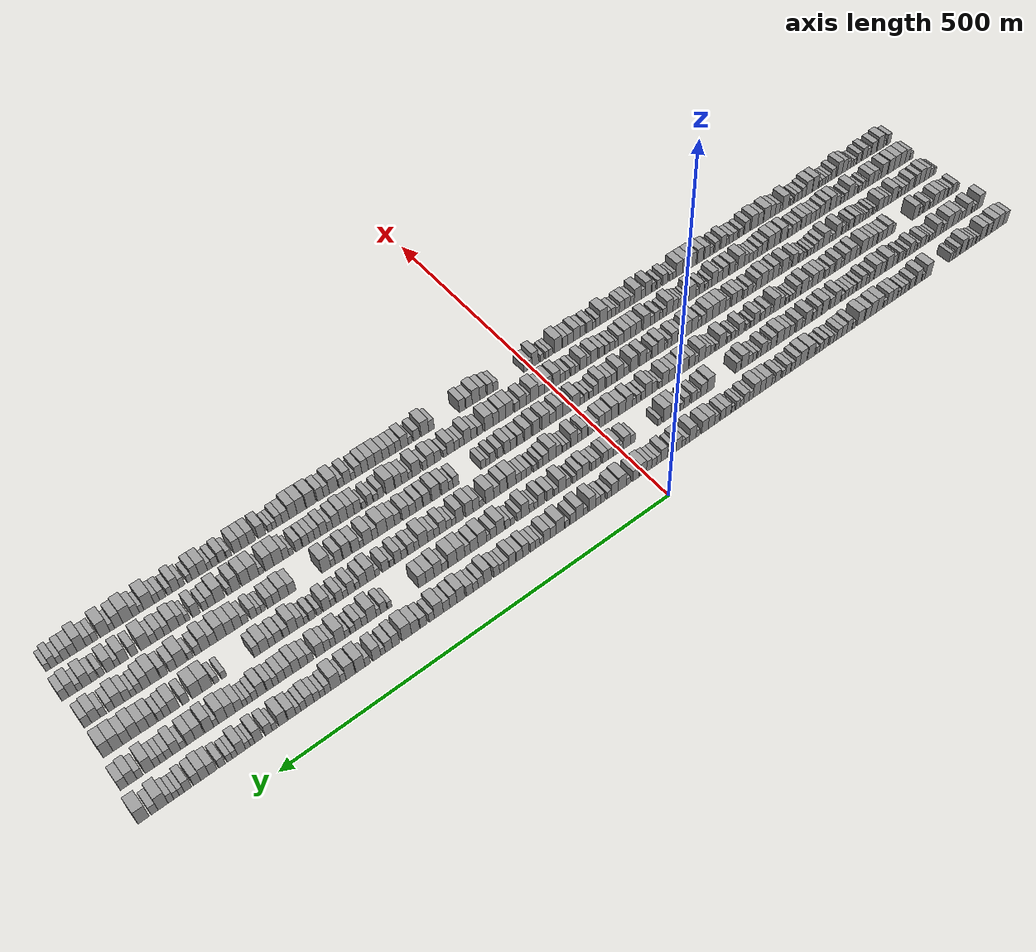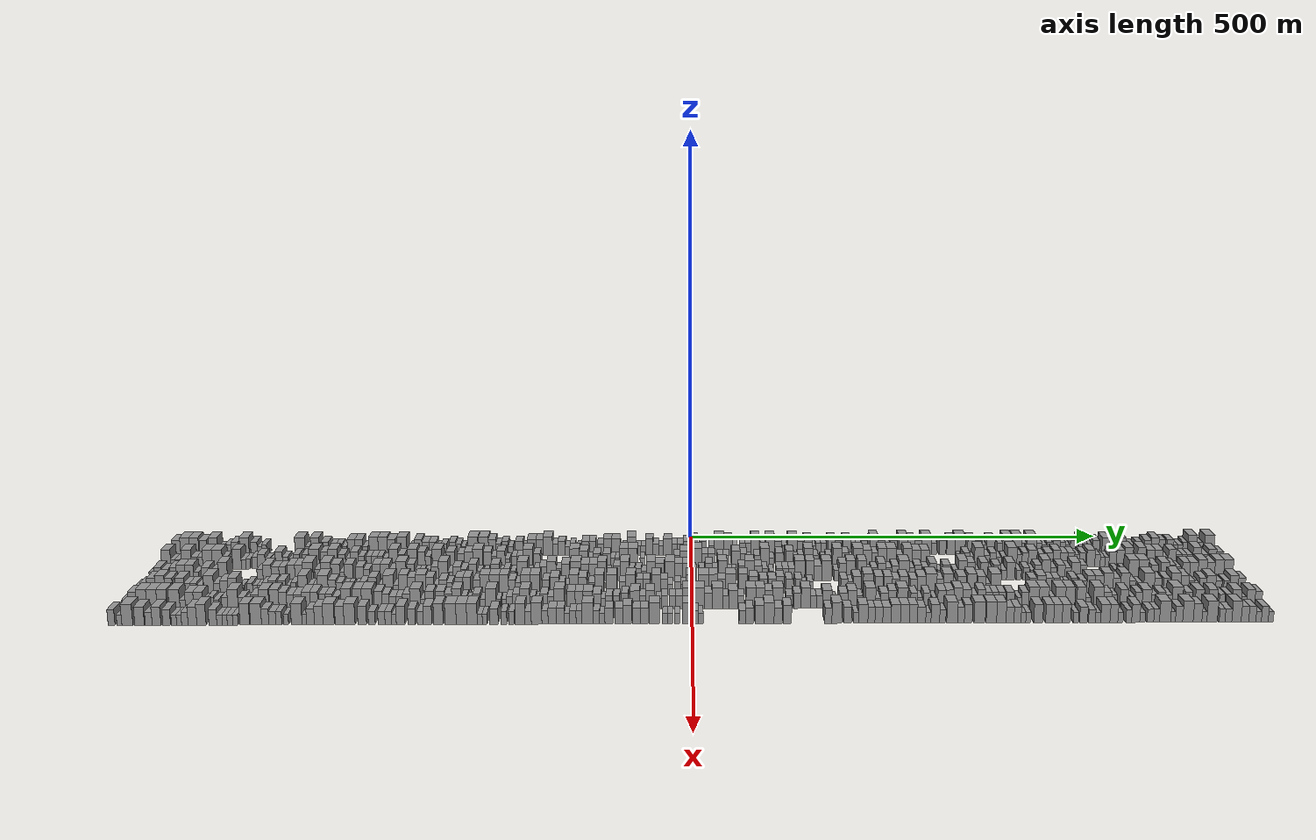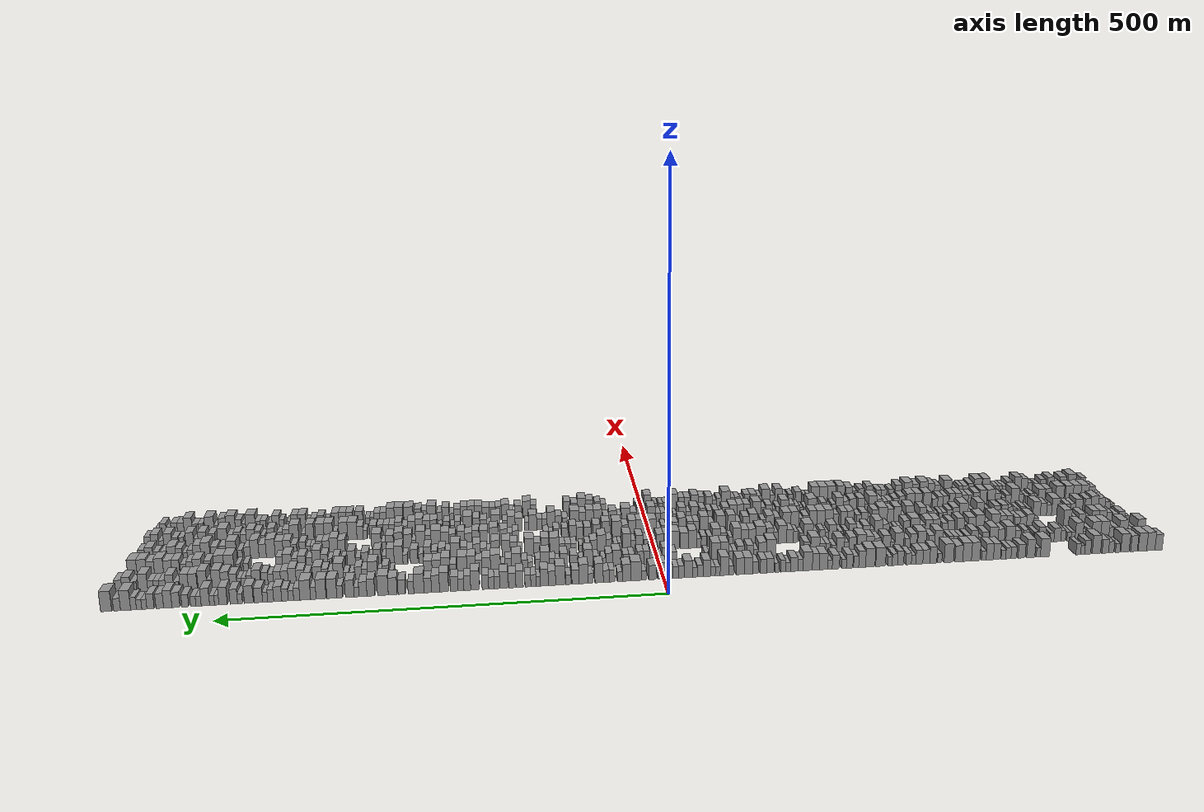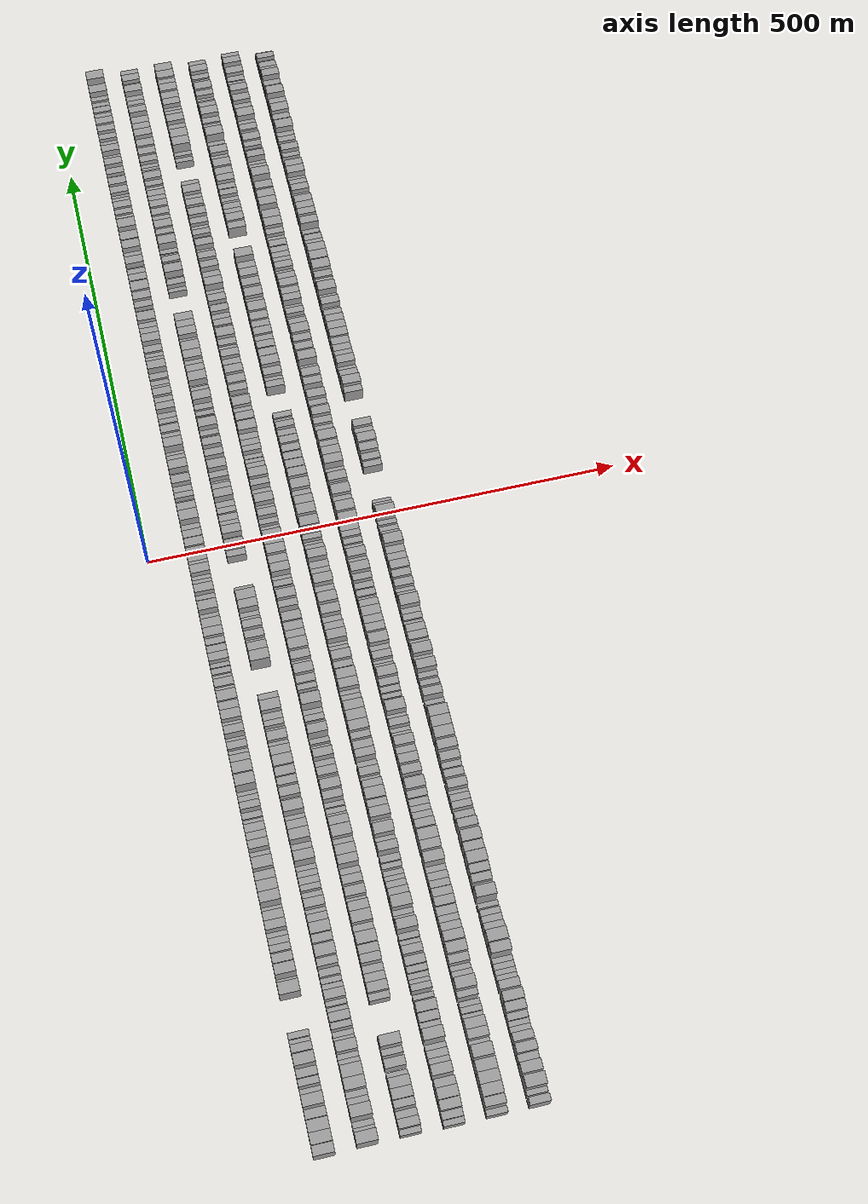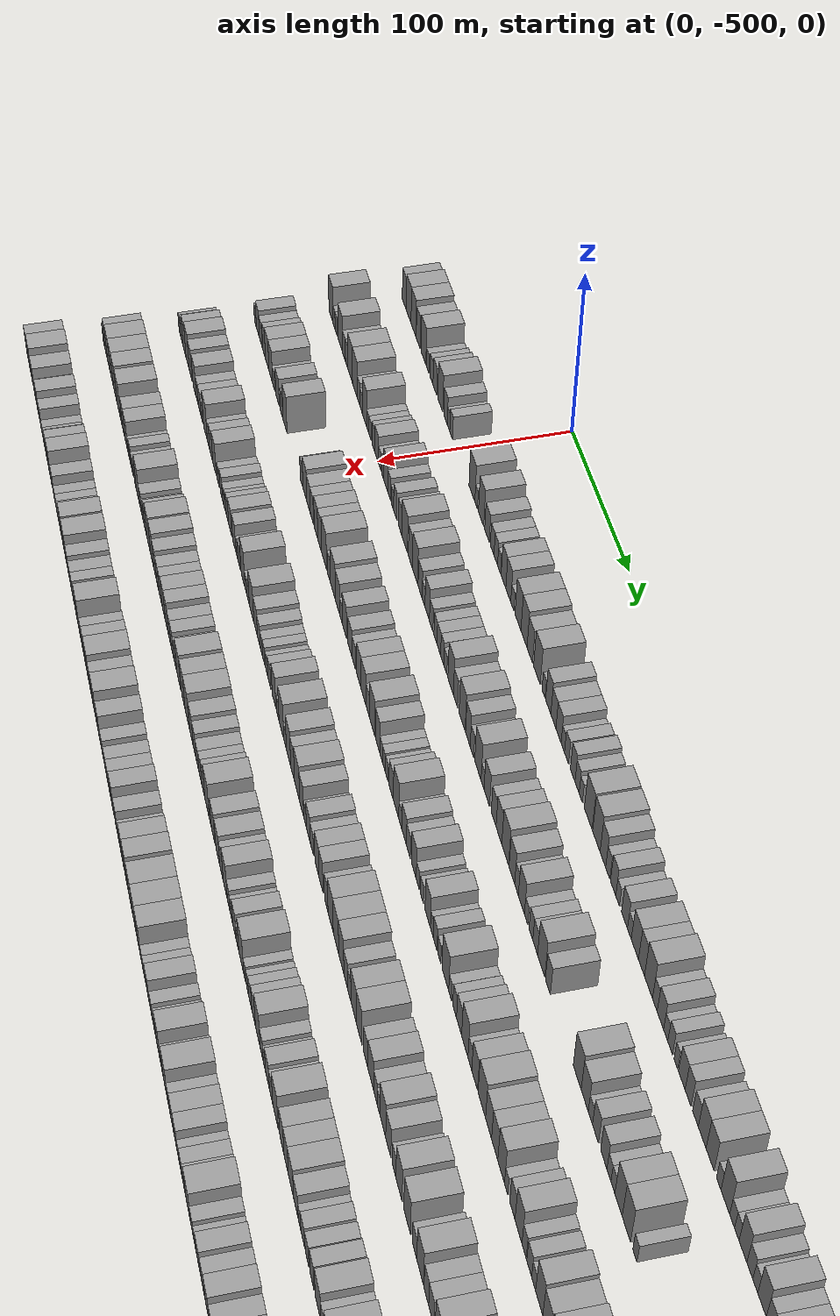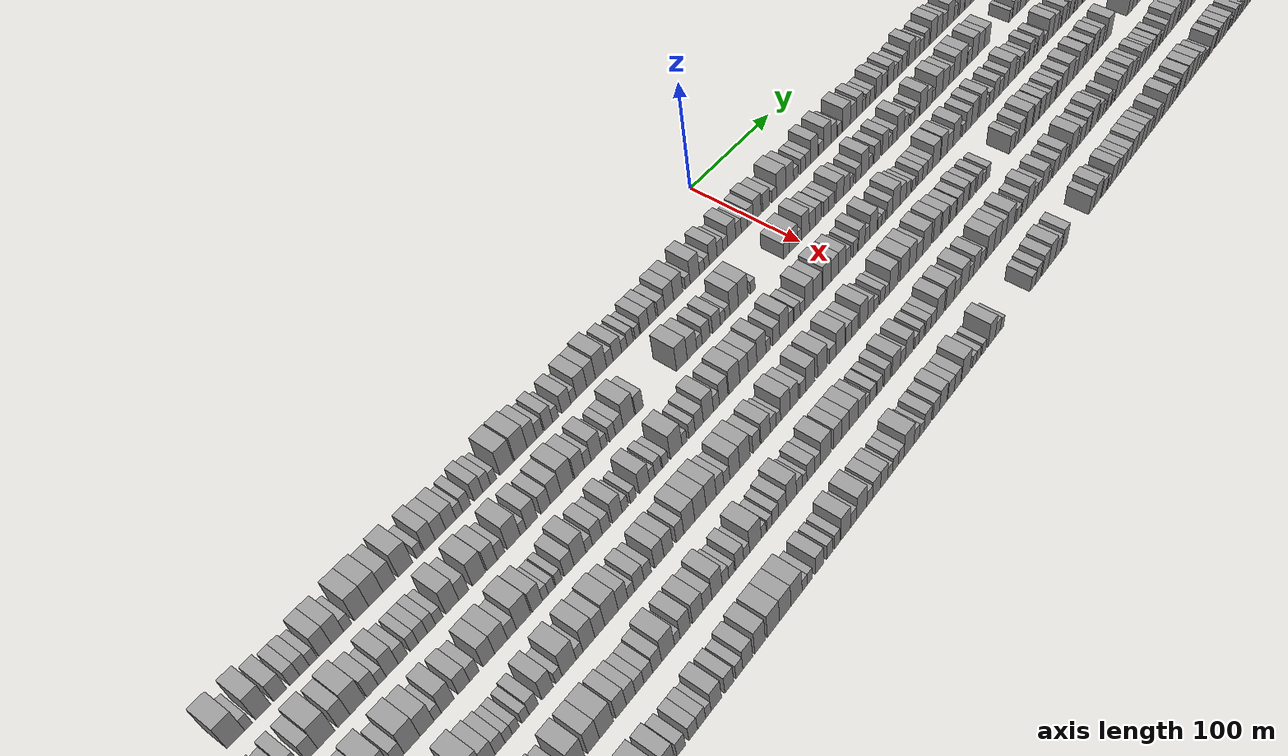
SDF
<sdf version="1.6">
 <world name="default">
  <scene>
   <sky><clouds><speed>12</speed></clouds></sky>
   <ambient>0.4 0.4 0.4 1</ambient>
   <background>0.7 0.7 0.7 1</background>
   <shadows>1</shadows>
  </scene>
  <gravity>0 0 -9.8066</gravity>
  <magnetic_field>6e-06 2.3e-05 -4.2e-05</magnetic_field>
  <physics default="0" name="default_physics" type="ode">
   <ode>
    <solver>
     <type>quick</type>
     <iters>10</iters>
     <sor>1.0</sor>
     <use_dynamic_moi_rescaling>0</use_dynamic_moi_rescaling>
    </solver>
    <constraints>
     <cfm>0</cfm>
     <erp>0.2</erp>
     <contact_max_correcting_vel>100</contact_max_correcting_vel>
     <contact_surface_layer>0.001</contact_surface_layer>
    </constraints>
   </ode>
   <max_step_size>0.004</max_step_size>
   <real_time_factor>1</real_time_factor>
   <real_time_update_rate>250</real_time_update_rate>
  </physics>
  <light name="sun" type="directional">
   <pose>0 0 10 0 0 0</pose>
   <diffuse>0.8 0.8 0.8 1</diffuse>
   <specular>0.2 0.2 0.2 1</specular>
   <attenuation>
    <range>1000</range>
    <constant>0.9</constant>
    <linear>0.01</linear>
    <quadratic>0.001</quadratic>
   </attenuation>
   <direction>-0.5 0.1 -0.9</direction>
  </light>
  <model name="building_1">
   <static>1</static>
   <pose>50.0000 -615.2156 0 0.000000 0.000000 0.000000</pose>
   <link name="link">
    <pose>0 0 10.50 0 0 0</pose>
    <collision name="collision"><geometry><box><size>20.0000 9.5688 21.0000</size></box></geometry></collision>
    <visual name="visual">
     <cast_shadows>0</cast_shadows>
     <geometry><box><size>20.0000 9.5688 21.0000</size></box></geometry>
     <material>
      <script>
       <uri>model://grey_wall/materials/scripts</uri>
       <uri>model://grey_wall/materials/textures</uri>
       <name>vrc/grey_wall</name>
      </script>
     </material>
    </visual>
   </link>
  </model>
  <model name="building_2">
   <static>1</static>
   <pose>50.0000 -604.9854 0 0.000000 0.000000 0.000000</pose>
   <link name="link">
    <pose>0 0 12.00 0 0 0</pose>
    <collision name="collision"><geometry><box><size>20.0000 10.8915 24.0000</size></box></geometry></collision>
    <visual name="visual">
     <cast_shadows>0</cast_shadows>
     <geometry><box><size>20.0000 10.8915 24.0000</size></box></geometry>
     <material>
      <script>
       <uri>model://grey_wall/materials/scripts</uri>
       <uri>model://grey_wall/materials/textures</uri>
       <name>vrc/grey_wall</name>
      </script>
     </material>
    </visual>
   </link>
  </model>
  <model name="building_3">
   <static>1</static>
   <pose>50.0000 -594.0050 0 0.000000 0.000000 0.000000</pose>
   <link name="link">
    <pose>0 0 12.00 0 0 0</pose>
    <collision name="collision"><geometry><box><size>20.0000 11.0693 24.0000</size></box></geometry></collision>
    <visual name="visual">
     <cast_shadows>0</cast_shadows>
     <geometry><box><size>20.0000 11.0693 24.0000</size></box></geometry>
     <material>
      <script>
       <uri>model://grey_wall/materials/scripts</uri>
       <uri>model://grey_wall/materials/textures</uri>
       <name>vrc/grey_wall</name>
      </script>
     </material>
    </visual>
   </link>
  </model>
  <model name="building_4">
   <static>1</static>
   <pose>50.0000 -583.0827 0 0.000000 0.000000 0.000000</pose>
   <link name="link">
    <pose>0 0 10.50 0 0 0</pose>
    <collision name="collision"><geometry><box><size>20.0000 8.7754 21.0000</size></box></geometry></collision>
    <visual name="visual">
     <cast_shadows>0</cast_shadows>
     <geometry><box><size>20.0000 8.7754 21.0000</size></box></geometry>
     <material>
      <script>
       <uri>model://grey_wall/materials/scripts</uri>
       <uri>model://grey_wall/materials/textures</uri>
       <name>vrc/grey_wall</name>
      </script>
     </material>
    </visual>
   </link>
  </model>
  <model name="building_5">
   <static>1</static>
   <pose>50.0000 -571.2221 0 0.000000 0.000000 0.000000</pose>
   <link name="link">
    <pose>0 0 12.00 0 0 0</pose>
    <collision name="collision"><geometry><box><size>20.0000 10.9458 24.0000</size></box></geometry></collision>
    <visual name="visual">
     <cast_shadows>0</cast_shadows>
     <geometry><box><size>20.0000 10.9458 24.0000</size></box></geometry>
     <material>
      <script>
       <uri>model://grey_wall/materials/scripts</uri>
       <uri>model://grey_wall/materials/textures</uri>
       <name>vrc/grey_wall</name>
      </script>
     </material>
    </visual>
   </link>
  </model>
  <model name="building_6">
   <static>1</static>
   <pose>50.0000 -561.8170 0 0.000000 0.000000 0.000000</pose>
   <link name="link">
    <pose>0 0 6.00 0 0 0</pose>
    <collision name="collision"><geometry><box><size>20.0000 5.8643 12.0000</size></box></geometry></collision>
    <visual name="visual">
     <cast_shadows>0</cast_shadows>
     <geometry><box><size>20.0000 5.8643 12.0000</size></box></geometry>
     <material>
      <script>
       <uri>model://grey_wall/materials/scripts</uri>
       <uri>model://grey_wall/materials/textures</uri>
       <name>vrc/grey_wall</name>
      </script>
     </material>
    </visual>
   </link>
  </model>
  <model name="building_7">
   <static>1</static>
   <pose>50.0000 -553.3687 0 0.000000 0.000000 0.000000</pose>
   <link name="link">
    <pose>0 0 7.50 0 0 0</pose>
    <collision name="collision"><geometry><box><size>20.0000 7.0323 15.0000</size></box></geometry></collision>
    <visual name="visual">
     <cast_shadows>0</cast_shadows>
     <geometry><box><size>20.0000 7.0323 15.0000</size></box></geometry>
     <material>
      <script>
       <uri>model://grey_wall/materials/scripts</uri>
       <uri>model://grey_wall/materials/textures</uri>
       <name>vrc/grey_wall</name>
      </script>
     </material>
    </visual>
   </link>
  </model>
  <model name="building_8">
   <static>1</static>
   <pose>50.0000 -545.6769 0 0.000000 0.000000 0.000000</pose>
   <link name="link">
    <pose>0 0 9.00 0 0 0</pose>
    <collision name="collision"><geometry><box><size>20.0000 8.3513 18.0000</size></box></geometry></collision>
    <visual name="visual">
     <cast_shadows>0</cast_shadows>
     <geometry><box><size>20.0000 8.3513 18.0000</size></box></geometry>
     <material>
      <script>
       <uri>model://grey_wall/materials/scripts</uri>
       <uri>model://grey_wall/materials/textures</uri>
       <name>vrc/grey_wall</name>
      </script>
     </material>
    </visual>
   </link>
  </model>
  <model name="building_9">
   <static>1</static>
   <pose>50.0000 -534.0716 0 0.000000 0.000000 0.000000</pose>
   <link name="link">
    <pose>0 0 12.00 0 0 0</pose>
    <collision name="collision"><geometry><box><size>20.0000 10.8593 24.0000</size></box></geometry></collision>
    <visual name="visual">
     <cast_shadows>0</cast_shadows>
     <geometry><box><size>20.0000 10.8593 24.0000</size></box></geometry>
     <material>
      <script>
       <uri>model://grey_wall/materials/scripts</uri>
       <uri>model://grey_wall/materials/textures</uri>
       <name>vrc/grey_wall</name>
      </script>
     </material>
    </visual>
   </link>
  </model>
  <model name="building_10">
   <static>1</static>
   <pose>50.0000 -522.7396 0 0.000000 0.000000 0.000000</pose>
   <link name="link">
    <pose>0 0 9.00 0 0 0</pose>
    <collision name="collision"><geometry><box><size>20.0000 7.8048 18.0000</size></box></geometry></collision>
    <visual name="visual">
     <cast_shadows>0</cast_shadows>
     <geometry><box><size>20.0000 7.8048 18.0000</size></box></geometry>
     <material>
      <script>
       <uri>model://grey_wall/materials/scripts</uri>
       <uri>model://grey_wall/materials/textures</uri>
       <name>vrc/grey_wall</name>
      </script>
     </material>
    </visual>
   </link>
  </model>
  <model name="building_11">
   <static>1</static>
   <pose>50.0000 -516.2478 0 0.000000 0.000000 0.000000</pose>
   <link name="link">
    <pose>0 0 6.00 0 0 0</pose>
    <collision name="collision"><geometry><box><size>20.0000 5.1789 12.0000</size></box></geometry></collision>
    <visual name="visual">
     <cast_shadows>0</cast_shadows>
     <geometry><box><size>20.0000 5.1789 12.0000</size></box></geometry>
     <material>
      <script>
       <uri>model://grey_wall/materials/scripts</uri>
       <uri>model://grey_wall/materials/textures</uri>
       <name>vrc/grey_wall</name>
      </script>
     </material>
    </visual>
   </link>
  </model>
  <model name="building_12">
   <static>1</static>
   <pose>50.0000 -510.6056 0 0.000000 0.000000 0.000000</pose>
   <link name="link">
    <pose>0 0 7.50 0 0 0</pose>
    <collision name="collision"><geometry><box><size>20.0000 6.1054 15.0000</size></box></geometry></collision>
    <visual name="visual">
     <cast_shadows>0</cast_shadows>
     <geometry><box><size>20.0000 6.1054 15.0000</size></box></geometry>
     <material>
      <script>
       <uri>model://grey_wall/materials/scripts</uri>
       <uri>model://grey_wall/materials/textures</uri>
       <name>vrc/grey_wall</name>
      </script>
     </material>
    </visual>
   </link>
  </model>
  <model name="building_13">
   <static>1</static>
   <pose>50.0000 -467.8218 0 0.000000 0.000000 0.000000</pose>
   <link name="link">
    <pose>0 0 12.00 0 0 0</pose>
    <collision name="collision"><geometry><box><size>20.0000 11.8208 24.0000</size></box></geometry></collision>
    <visual name="visual">
     <cast_shadows>0</cast_shadows>
     <geometry><box><size>20.0000 11.8208 24.0000</size></box></geometry>
     <material>
      <script>
       <uri>model://grey_wall/materials/scripts</uri>
       <uri>model://grey_wall/materials/textures</uri>
       <name>vrc/grey_wall</name>
      </script>
     </material>
    </visual>
   </link>
  </model>
  <model name="building_14">
   <static>1</static>
   <pose>50.0000 -459.3710 0 0.000000 0.000000 0.000000</pose>
   <link name="link">
    <pose>0 0 6.00 0 0 0</pose>
    <collision name="collision"><geometry><box><size>20.0000 5.0807 12.0000</size></box></geometry></collision>
    <visual name="visual">
     <cast_shadows>0</cast_shadows>
     <geometry><box><size>20.0000 5.0807 12.0000</size></box></geometry>
     <material>
      <script>
       <uri>model://grey_wall/materials/scripts</uri>
       <uri>model://grey_wall/materials/textures</uri>
       <name>vrc/grey_wall</name>
      </script>
     </material>
    </visual>
   </link>
  </model>
  <model name="building_15">
   <static>1</static>
   <pose>50.0000 -449.6643 0 0.000000 0.000000 0.000000</pose>
   <link name="link">
    <pose>0 0 12.00 0 0 0</pose>
    <collision name="collision"><geometry><box><size>20.0000 10.3328 24.0000</size></box></geometry></collision>
    <visual name="visual">
     <cast_shadows>0</cast_shadows>
     <geometry><box><size>20.0000 10.3328 24.0000</size></box></geometry>
     <material>
      <script>
       <uri>model://grey_wall/materials/scripts</uri>
       <uri>model://grey_wall/materials/textures</uri>
       <name>vrc/grey_wall</name>
      </script>
     </material>
    </visual>
   </link>
  </model>
  <model name="building_16">
   <static>1</static>
   <pose>50.0000 -438.0300 0 0.000000 0.000000 0.000000</pose>
   <link name="link">
    <pose>0 0 9.00 0 0 0</pose>
    <collision name="collision"><geometry><box><size>20.0000 8.9358 18.0000</size></box></geometry></collision>
    <visual name="visual">
     <cast_shadows>0</cast_shadows>
     <geometry><box><size>20.0000 8.9358 18.0000</size></box></geometry>
     <material>
      <script>
       <uri>model://grey_wall/materials/scripts</uri>
       <uri>model://grey_wall/materials/textures</uri>
       <name>vrc/grey_wall</name>
      </script>
     </material>
    </visual>
   </link>
  </model>
  <model name="building_17">
   <static>1</static>
   <pose>50.0000 -428.0484 0 0.000000 0.000000 0.000000</pose>
   <link name="link">
    <pose>0 0 7.50 0 0 0</pose>
    <collision name="collision"><geometry><box><size>20.0000 7.0274 15.0000</size></box></geometry></collision>
    <visual name="visual">
     <cast_shadows>0</cast_shadows>
     <geometry><box><size>20.0000 7.0274 15.0000</size></box></geometry>
     <material>
      <script>
       <uri>model://grey_wall/materials/scripts</uri>
       <uri>model://grey_wall/materials/textures</uri>
       <name>vrc/grey_wall</name>
      </script>
     </material>
    </visual>
   </link>
  </model>
  <model name="building_18">
   <static>1</static>
   <pose>50.0000 -421.1219 0 0.000000 0.000000 0.000000</pose>
   <link name="link">
    <pose>0 0 7.50 0 0 0</pose>
    <collision name="collision"><geometry><box><size>20.0000 6.8255 15.0000</size></box></geometry></collision>
    <visual name="visual">
     <cast_shadows>0</cast_shadows>
     <geometry><box><size>20.0000 6.8255 15.0000</size></box></geometry>
     <material>
      <script>
       <uri>model://grey_wall/materials/scripts</uri>
       <uri>model://grey_wall/materials/textures</uri>
       <name>vrc/grey_wall</name>
      </script>
     </material>
    </visual>
   </link>
  </model>
  <model name="building_19">
   <static>1</static>
   <pose>50.0000 -414.8773 0 0.000000 0.000000 0.000000</pose>
   <link name="link">
    <pose>0 0 6.00 0 0 0</pose>
    <collision name="collision"><geometry><box><size>20.0000 5.6638 12.0000</size></box></geometry></collision>
    <visual name="visual">
     <cast_shadows>0</cast_shadows>
     <geometry><box><size>20.0000 5.6638 12.0000</size></box></geometry>
     <material>
      <script>
       <uri>model://grey_wall/materials/scripts</uri>
       <uri>model://grey_wall/materials/textures</uri>
       <name>vrc/grey_wall</name>
      </script>
     </material>
    </visual>
   </link>
  </model>
  <model name="building_20">
   <static>1</static>
   <pose>50.0000 -406.5833 0 0.000000 0.000000 0.000000</pose>
   <link name="link">
    <pose>0 0 10.50 0 0 0</pose>
    <collision name="collision"><geometry><box><size>20.0000 8.9241 21.0000</size></box></geometry></collision>
    <visual name="visual">
     <cast_shadows>0</cast_shadows>
     <geometry><box><size>20.0000 8.9241 21.0000</size></box></geometry>
     <material>
      <script>
       <uri>model://grey_wall/materials/scripts</uri>
       <uri>model://grey_wall/materials/textures</uri>
       <name>vrc/grey_wall</name>
      </script>
     </material>
    </visual>
   </link>
  </model>
  <model name="building_21">
   <static>1</static>
   <pose>50.0000 -397.5467 0 0.000000 0.000000 0.000000</pose>
   <link name="link">
    <pose>0 0 10.50 0 0 0</pose>
    <collision name="collision"><geometry><box><size>20.0000 9.1492 21.0000</size></box></geometry></collision>
    <visual name="visual">
     <cast_shadows>0</cast_shadows>
     <geometry><box><size>20.0000 9.1492 21.0000</size></box></geometry>
     <material>
      <script>
       <uri>model://grey_wall/materials/scripts</uri>
       <uri>model://grey_wall/materials/textures</uri>
       <name>vrc/grey_wall</name>
      </script>
     </material>
    </visual>
   </link>
  </model>
  <model name="building_22">
   <static>1</static>
   <pose>50.0000 -390.0511 0 0.000000 0.000000 0.000000</pose>
   <link name="link">
    <pose>0 0 6.00 0 0 0</pose>
    <collision name="collision"><geometry><box><size>20.0000 5.8420 12.0000</size></box></geometry></collision>
    <visual name="visual">
     <cast_shadows>0</cast_shadows>
     <geometry><box><size>20.0000 5.8420 12.0000</size></box></geometry>
     <material>
      <script>
       <uri>model://grey_wall/materials/scripts</uri>
       <uri>model://grey_wall/materials/textures</uri>
       <name>vrc/grey_wall</name>
      </script>
     </material>
    </visual>
   </link>
  </model>
  <model name="building_23">
   <static>1</static>
   <pose>50.0000 -379.7609 0 0.000000 0.000000 0.000000</pose>
   <link name="link">
    <pose>0 0 12.00 0 0 0</pose>
    <collision name="collision"><geometry><box><size>20.0000 10.7384 24.0000</size></box></geometry></collision>
    <visual name="visual">
     <cast_shadows>0</cast_shadows>
     <geometry><box><size>20.0000 10.7384 24.0000</size></box></geometry>
     <material>
      <script>
       <uri>model://grey_wall/materials/scripts</uri>
       <uri>model://grey_wall/materials/textures</uri>
       <name>vrc/grey_wall</name>
      </script>
     </material>
    </visual>
   </link>
  </model>
  <model name="building_24">
   <static>1</static>
   <pose>50.0000 -368.8941 0 0.000000 0.000000 0.000000</pose>
   <link name="link">
    <pose>0 0 12.00 0 0 0</pose>
    <collision name="collision"><geometry><box><size>20.0000 10.9952 24.0000</size></box></geometry></collision>
    <visual name="visual">
     <cast_shadows>0</cast_shadows>
     <geometry><box><size>20.0000 10.9952 24.0000</size></box></geometry>
     <material>
      <script>
       <uri>model://grey_wall/materials/scripts</uri>
       <uri>model://grey_wall/materials/textures</uri>
       <name>vrc/grey_wall</name>
      </script>
     </material>
    </visual>
   </link>
  </model>
  <model name="building_25">
   <static>1</static>
   <pose>50.0000 -358.5665 0 0.000000 0.000000 0.000000</pose>
   <link name="link">
    <pose>0 0 10.50 0 0 0</pose>
    <collision name="collision"><geometry><box><size>20.0000 9.6600 21.0000</size></box></geometry></collision>
    <visual name="visual">
     <cast_shadows>0</cast_shadows>
     <geometry><box><size>20.0000 9.6600 21.0000</size></box></geometry>
     <material>
      <script>
       <uri>model://grey_wall/materials/scripts</uri>
       <uri>model://grey_wall/materials/textures</uri>
       <name>vrc/grey_wall</name>
      </script>
     </material>
    </visual>
   </link>
  </model>
  <model name="building_26">
   <static>1</static>
   <pose>50.0000 -345.9555 0 0.000000 0.000000 0.000000</pose>
   <link name="link">
    <pose>0 0 12.00 0 0 0</pose>
    <collision name="collision"><geometry><box><size>20.0000 11.5620 24.0000</size></box></geometry></collision>
    <visual name="visual">
     <cast_shadows>0</cast_shadows>
     <geometry><box><size>20.0000 11.5620 24.0000</size></box></geometry>
     <material>
      <script>
       <uri>model://grey_wall/materials/scripts</uri>
       <uri>model://grey_wall/materials/textures</uri>
       <name>vrc/grey_wall</name>
      </script>
     </material>
    </visual>
   </link>
  </model>
  <model name="building_27">
   <static>1</static>
   <pose>50.0000 -334.5388 0 0.000000 0.000000 0.000000</pose>
   <link name="link">
    <pose>0 0 6.00 0 0 0</pose>
    <collision name="collision"><geometry><box><size>20.0000 5.2714 12.0000</size></box></geometry></collision>
    <visual name="visual">
     <cast_shadows>0</cast_shadows>
     <geometry><box><size>20.0000 5.2714 12.0000</size></box></geometry>
     <material>
      <script>
       <uri>model://grey_wall/materials/scripts</uri>
       <uri>model://grey_wall/materials/textures</uri>
       <name>vrc/grey_wall</name>
      </script>
     </material>
    </visual>
   </link>
  </model>
  <model name="building_28">
   <static>1</static>
   <pose>50.0000 -326.4957 0 0.000000 0.000000 0.000000</pose>
   <link name="link">
    <pose>0 0 10.50 0 0 0</pose>
    <collision name="collision"><geometry><box><size>20.0000 8.8148 21.0000</size></box></geometry></collision>
    <visual name="visual">
     <cast_shadows>0</cast_shadows>
     <geometry><box><size>20.0000 8.8148 21.0000</size></box></geometry>
     <material>
      <script>
       <uri>model://grey_wall/materials/scripts</uri>
       <uri>model://grey_wall/materials/textures</uri>
       <name>vrc/grey_wall</name>
      </script>
     </material>
    </visual>
   </link>
  </model>
  <model name="building_29">
   <static>1</static>
   <pose>50.0000 -317.7686 0 0.000000 0.000000 0.000000</pose>
   <link name="link">
    <pose>0 0 9.00 0 0 0</pose>
    <collision name="collision"><geometry><box><size>20.0000 8.6393 18.0000</size></box></geometry></collision>
    <visual name="visual">
     <cast_shadows>0</cast_shadows>
     <geometry><box><size>20.0000 8.6393 18.0000</size></box></geometry>
     <material>
      <script>
       <uri>model://grey_wall/materials/scripts</uri>
       <uri>model://grey_wall/materials/textures</uri>
       <name>vrc/grey_wall</name>
      </script>
     </material>
    </visual>
   </link>
  </model>
  <model name="building_30">
   <static>1</static>
   <pose>50.0000 -309.1270 0 0.000000 0.000000 0.000000</pose>
   <link name="link">
    <pose>0 0 9.00 0 0 0</pose>
    <collision name="collision"><geometry><box><size>20.0000 8.6440 18.0000</size></box></geometry></collision>
    <visual name="visual">
     <cast_shadows>0</cast_shadows>
     <geometry><box><size>20.0000 8.6440 18.0000</size></box></geometry>
     <material>
      <script>
       <uri>model://grey_wall/materials/scripts</uri>
       <uri>model://grey_wall/materials/textures</uri>
       <name>vrc/grey_wall</name>
      </script>
     </material>
    </visual>
   </link>
  </model>
  <model name="building_31">
   <static>1</static>
   <pose>50.0000 -302.0066 0 0.000000 0.000000 0.000000</pose>
   <link name="link">
    <pose>0 0 6.00 0 0 0</pose>
    <collision name="collision"><geometry><box><size>20.0000 5.5969 12.0000</size></box></geometry></collision>
    <visual name="visual">
     <cast_shadows>0</cast_shadows>
     <geometry><box><size>20.0000 5.5969 12.0000</size></box></geometry>
     <material>
      <script>
       <uri>model://grey_wall/materials/scripts</uri>
       <uri>model://grey_wall/materials/textures</uri>
       <name>vrc/grey_wall</name>
      </script>
     </material>
    </visual>
   </link>
  </model>
  <model name="building_32">
   <static>1</static>
   <pose>50.0000 -295.8793 0 0.000000 0.000000 0.000000</pose>
   <link name="link">
    <pose>0 0 7.50 0 0 0</pose>
    <collision name="collision"><geometry><box><size>20.0000 6.6576 15.0000</size></box></geometry></collision>
    <visual name="visual">
     <cast_shadows>0</cast_shadows>
     <geometry><box><size>20.0000 6.6576 15.0000</size></box></geometry>
     <material>
      <script>
       <uri>model://grey_wall/materials/scripts</uri>
       <uri>model://grey_wall/materials/textures</uri>
       <name>vrc/grey_wall</name>
      </script>
     </material>
    </visual>
   </link>
  </model>
  <model name="building_33">
   <static>1</static>
   <pose>50.0000 -285.7998 0 0.000000 0.000000 0.000000</pose>
   <link name="link">
    <pose>0 0 9.00 0 0 0</pose>
    <collision name="collision"><geometry><box><size>20.0000 7.5014 18.0000</size></box></geometry></collision>
    <visual name="visual">
     <cast_shadows>0</cast_shadows>
     <geometry><box><size>20.0000 7.5014 18.0000</size></box></geometry>
     <material>
      <script>
       <uri>model://grey_wall/materials/scripts</uri>
       <uri>model://grey_wall/materials/textures</uri>
       <name>vrc/grey_wall</name>
      </script>
     </material>
    </visual>
   </link>
  </model>
  <model name="building_34">
   <static>1</static>
   <pose>50.0000 -278.7101 0 0.000000 0.000000 0.000000</pose>
   <link name="link">
    <pose>0 0 7.50 0 0 0</pose>
    <collision name="collision"><geometry><box><size>20.0000 6.6780 15.0000</size></box></geometry></collision>
    <visual name="visual">
     <cast_shadows>0</cast_shadows>
     <geometry><box><size>20.0000 6.6780 15.0000</size></box></geometry>
     <material>
      <script>
       <uri>model://grey_wall/materials/scripts</uri>
       <uri>model://grey_wall/materials/textures</uri>
       <name>vrc/grey_wall</name>
      </script>
     </material>
    </visual>
   </link>
  </model>
  <model name="building_35">
   <static>1</static>
   <pose>50.0000 -272.7477 0 0.000000 0.000000 0.000000</pose>
   <link name="link">
    <pose>0 0 6.00 0 0 0</pose>
    <collision name="collision"><geometry><box><size>20.0000 5.2467 12.0000</size></box></geometry></collision>
    <visual name="visual">
     <cast_shadows>0</cast_shadows>
     <geometry><box><size>20.0000 5.2467 12.0000</size></box></geometry>
     <material>
      <script>
       <uri>model://grey_wall/materials/scripts</uri>
       <uri>model://grey_wall/materials/textures</uri>
       <name>vrc/grey_wall</name>
      </script>
     </material>
    </visual>
   </link>
  </model>
  <model name="building_36">
   <static>1</static>
   <pose>50.0000 -261.1301 0 0.000000 0.000000 0.000000</pose>
   <link name="link">
    <pose>0 0 12.00 0 0 0</pose>
    <collision name="collision"><geometry><box><size>20.0000 11.9886 24.0000</size></box></geometry></collision>
    <visual name="visual">
     <cast_shadows>0</cast_shadows>
     <geometry><box><size>20.0000 11.9886 24.0000</size></box></geometry>
     <material>
      <script>
       <uri>model://grey_wall/materials/scripts</uri>
       <uri>model://grey_wall/materials/textures</uri>
       <name>vrc/grey_wall</name>
      </script>
     </material>
    </visual>
   </link>
  </model>
  <model name="building_37">
   <static>1</static>
   <pose>50.0000 -248.3697 0 0.000000 0.000000 0.000000</pose>
   <link name="link">
    <pose>0 0 12.00 0 0 0</pose>
    <collision name="collision"><geometry><box><size>20.0000 11.5321 24.0000</size></box></geometry></collision>
    <visual name="visual">
     <cast_shadows>0</cast_shadows>
     <geometry><box><size>20.0000 11.5321 24.0000</size></box></geometry>
     <material>
      <script>
       <uri>model://grey_wall/materials/scripts</uri>
       <uri>model://grey_wall/materials/textures</uri>
       <name>vrc/grey_wall</name>
      </script>
     </material>
    </visual>
   </link>
  </model>
  <model name="building_38">
   <static>1</static>
   <pose>50.0000 -238.3256 0 0.000000 0.000000 0.000000</pose>
   <link name="link">
    <pose>0 0 10.50 0 0 0</pose>
    <collision name="collision"><geometry><box><size>20.0000 8.5561 21.0000</size></box></geometry></collision>
    <visual name="visual">
     <cast_shadows>0</cast_shadows>
     <geometry><box><size>20.0000 8.5561 21.0000</size></box></geometry>
     <material>
      <script>
       <uri>model://grey_wall/materials/scripts</uri>
       <uri>model://grey_wall/materials/textures</uri>
       <name>vrc/grey_wall</name>
      </script>
     </material>
    </visual>
   </link>
  </model>
  <model name="building_39">
   <static>1</static>
   <pose>50.0000 -230.9383 0 0.000000 0.000000 0.000000</pose>
   <link name="link">
    <pose>0 0 7.50 0 0 0</pose>
    <collision name="collision"><geometry><box><size>20.0000 6.2185 15.0000</size></box></geometry></collision>
    <visual name="visual">
     <cast_shadows>0</cast_shadows>
     <geometry><box><size>20.0000 6.2185 15.0000</size></box></geometry>
     <material>
      <script>
       <uri>model://grey_wall/materials/scripts</uri>
       <uri>model://grey_wall/materials/textures</uri>
       <name>vrc/grey_wall</name>
      </script>
     </material>
    </visual>
   </link>
  </model>
  <model name="building_40">
   <static>1</static>
   <pose>50.0000 -222.8630 0 0.000000 0.000000 0.000000</pose>
   <link name="link">
    <pose>0 0 9.00 0 0 0</pose>
    <collision name="collision"><geometry><box><size>20.0000 7.9320 18.0000</size></box></geometry></collision>
    <visual name="visual">
     <cast_shadows>0</cast_shadows>
     <geometry><box><size>20.0000 7.9320 18.0000</size></box></geometry>
     <material>
      <script>
       <uri>model://grey_wall/materials/scripts</uri>
       <uri>model://grey_wall/materials/textures</uri>
       <name>vrc/grey_wall</name>
      </script>
     </material>
    </visual>
   </link>
  </model>
  <model name="building_41">
   <static>1</static>
   <pose>50.0000 -216.1563 0 0.000000 0.000000 0.000000</pose>
   <link name="link">
    <pose>0 0 6.00 0 0 0</pose>
    <collision name="collision"><geometry><box><size>20.0000 5.4815 12.0000</size></box></geometry></collision>
    <visual name="visual">
     <cast_shadows>0</cast_shadows>
     <geometry><box><size>20.0000 5.4815 12.0000</size></box></geometry>
     <material>
      <script>
       <uri>model://grey_wall/materials/scripts</uri>
       <uri>model://grey_wall/materials/textures</uri>
       <name>vrc/grey_wall</name>
      </script>
     </material>
    </visual>
   </link>
  </model>
  <model name="building_42">
   <static>1</static>
   <pose>50.0000 -206.0236 0 0.000000 0.000000 0.000000</pose>
   <link name="link">
    <pose>0 0 9.00 0 0 0</pose>
    <collision name="collision"><geometry><box><size>20.0000 8.7838 18.0000</size></box></geometry></collision>
    <visual name="visual">
     <cast_shadows>0</cast_shadows>
     <geometry><box><size>20.0000 8.7838 18.0000</size></box></geometry>
     <material>
      <script>
       <uri>model://grey_wall/materials/scripts</uri>
       <uri>model://grey_wall/materials/textures</uri>
       <name>vrc/grey_wall</name>
      </script>
     </material>
    </visual>
   </link>
  </model>
  <model name="building_43">
   <static>1</static>
   <pose>50.0000 -198.8813 0 0.000000 0.000000 0.000000</pose>
   <link name="link">
    <pose>0 0 6.00 0 0 0</pose>
    <collision name="collision"><geometry><box><size>20.0000 5.5008 12.0000</size></box></geometry></collision>
    <visual name="visual">
     <cast_shadows>0</cast_shadows>
     <geometry><box><size>20.0000 5.5008 12.0000</size></box></geometry>
     <material>
      <script>
       <uri>model://grey_wall/materials/scripts</uri>
       <uri>model://grey_wall/materials/textures</uri>
       <name>vrc/grey_wall</name>
      </script>
     </material>
    </visual>
   </link>
  </model>
  <model name="building_44">
   <static>1</static>
   <pose>50.0000 -190.9988 0 0.000000 0.000000 0.000000</pose>
   <link name="link">
    <pose>0 0 10.50 0 0 0</pose>
    <collision name="collision"><geometry><box><size>20.0000 10.2642 21.0000</size></box></geometry></collision>
    <visual name="visual">
     <cast_shadows>0</cast_shadows>
     <geometry><box><size>20.0000 10.2642 21.0000</size></box></geometry>
     <material>
      <script>
       <uri>model://grey_wall/materials/scripts</uri>
       <uri>model://grey_wall/materials/textures</uri>
       <name>vrc/grey_wall</name>
      </script>
     </material>
    </visual>
   </link>
  </model>
  <model name="building_45">
   <static>1</static>
   <pose>50.0000 -181.6023 0 0.000000 0.000000 0.000000</pose>
   <link name="link">
    <pose>0 0 10.50 0 0 0</pose>
    <collision name="collision"><geometry><box><size>20.0000 8.5288 21.0000</size></box></geometry></collision>
    <visual name="visual">
     <cast_shadows>0</cast_shadows>
     <geometry><box><size>20.0000 8.5288 21.0000</size></box></geometry>
     <material>
      <script>
       <uri>model://grey_wall/materials/scripts</uri>
       <uri>model://grey_wall/materials/textures</uri>
       <name>vrc/grey_wall</name>
      </script>
     </material>
    </visual>
   </link>
  </model>
  <model name="building_46">
   <static>1</static>
   <pose>50.0000 -171.7198 0 0.000000 0.000000 0.000000</pose>
   <link name="link">
    <pose>0 0 12.00 0 0 0</pose>
    <collision name="collision"><geometry><box><size>20.0000 11.2362 24.0000</size></box></geometry></collision>
    <visual name="visual">
     <cast_shadows>0</cast_shadows>
     <geometry><box><size>20.0000 11.2362 24.0000</size></box></geometry>
     <material>
      <script>
       <uri>model://grey_wall/materials/scripts</uri>
       <uri>model://grey_wall/materials/textures</uri>
       <name>vrc/grey_wall</name>
      </script>
     </material>
    </visual>
   </link>
  </model>
  <model name="building_47">
   <static>1</static>
   <pose>50.0000 -162.8576 0 0.000000 0.000000 0.000000</pose>
   <link name="link">
    <pose>0 0 7.50 0 0 0</pose>
    <collision name="collision"><geometry><box><size>20.0000 6.4881 15.0000</size></box></geometry></collision>
    <visual name="visual">
     <cast_shadows>0</cast_shadows>
     <geometry><box><size>20.0000 6.4881 15.0000</size></box></geometry>
     <material>
      <script>
       <uri>model://grey_wall/materials/scripts</uri>
       <uri>model://grey_wall/materials/textures</uri>
       <name>vrc/grey_wall</name>
      </script>
     </material>
    </visual>
   </link>
  </model>
  <model name="building_48">
   <static>1</static>
   <pose>50.0000 -155.2234 0 0.000000 0.000000 0.000000</pose>
   <link name="link">
    <pose>0 0 9.00 0 0 0</pose>
    <collision name="collision"><geometry><box><size>20.0000 8.7803 18.0000</size></box></geometry></collision>
    <visual name="visual">
     <cast_shadows>0</cast_shadows>
     <geometry><box><size>20.0000 8.7803 18.0000</size></box></geometry>
     <material>
      <script>
       <uri>model://grey_wall/materials/scripts</uri>
       <uri>model://grey_wall/materials/textures</uri>
       <name>vrc/grey_wall</name>
      </script>
     </material>
    </visual>
   </link>
  </model>
  <model name="building_49">
   <static>1</static>
   <pose>50.0000 -147.9795 0 0.000000 0.000000 0.000000</pose>
   <link name="link">
    <pose>0 0 6.00 0 0 0</pose>
    <collision name="collision"><geometry><box><size>20.0000 5.7076 12.0000</size></box></geometry></collision>
    <visual name="visual">
     <cast_shadows>0</cast_shadows>
     <geometry><box><size>20.0000 5.7076 12.0000</size></box></geometry>
     <material>
      <script>
       <uri>model://grey_wall/materials/scripts</uri>
       <uri>model://grey_wall/materials/textures</uri>
       <name>vrc/grey_wall</name>
      </script>
     </material>
    </visual>
   </link>
  </model>
  <model name="building_50">
   <static>1</static>
   <pose>50.0000 -141.9601 0 0.000000 0.000000 0.000000</pose>
   <link name="link">
    <pose>0 0 7.50 0 0 0</pose>
    <collision name="collision"><geometry><box><size>20.0000 6.3311 15.0000</size></box></geometry></collision>
    <visual name="visual">
     <cast_shadows>0</cast_shadows>
     <geometry><box><size>20.0000 6.3311 15.0000</size></box></geometry>
     <material>
      <script>
       <uri>model://grey_wall/materials/scripts</uri>
       <uri>model://grey_wall/materials/textures</uri>
       <name>vrc/grey_wall</name>
      </script>
     </material>
    </visual>
   </link>
  </model>
  <model name="building_51">
   <static>1</static>
   <pose>50.0000 -134.3684 0 0.000000 0.000000 0.000000</pose>
   <link name="link">
    <pose>0 0 6.00 0 0 0</pose>
    <collision name="collision"><geometry><box><size>20.0000 4.8523 12.0000</size></box></geometry></collision>
    <visual name="visual">
     <cast_shadows>0</cast_shadows>
     <geometry><box><size>20.0000 4.8523 12.0000</size></box></geometry>
     <material>
      <script>
       <uri>model://grey_wall/materials/scripts</uri>
       <uri>model://grey_wall/materials/textures</uri>
       <name>vrc/grey_wall</name>
      </script>
     </material>
    </visual>
   </link>
  </model>
  <model name="building_52">
   <static>1</static>
   <pose>50.0000 -126.5529 0 0.000000 0.000000 0.000000</pose>
   <link name="link">
    <pose>0 0 9.00 0 0 0</pose>
    <collision name="collision"><geometry><box><size>20.0000 8.7786 18.0000</size></box></geometry></collision>
    <visual name="visual">
     <cast_shadows>0</cast_shadows>
     <geometry><box><size>20.0000 8.7786 18.0000</size></box></geometry>
     <material>
      <script>
       <uri>model://grey_wall/materials/scripts</uri>
       <uri>model://grey_wall/materials/textures</uri>
       <name>vrc/grey_wall</name>
      </script>
     </material>
    </visual>
   </link>
  </model>
  <model name="building_53">
   <static>1</static>
   <pose>50.0000 -118.3003 0 0.000000 0.000000 0.000000</pose>
   <link name="link">
    <pose>0 0 9.00 0 0 0</pose>
    <collision name="collision"><geometry><box><size>20.0000 7.7267 18.0000</size></box></geometry></collision>
    <visual name="visual">
     <cast_shadows>0</cast_shadows>
     <geometry><box><size>20.0000 7.7267 18.0000</size></box></geometry>
     <material>
      <script>
       <uri>model://grey_wall/materials/scripts</uri>
       <uri>model://grey_wall/materials/textures</uri>
       <name>vrc/grey_wall</name>
      </script>
     </material>
    </visual>
   </link>
  </model>
  <model name="building_54">
   <static>1</static>
   <pose>50.0000 -108.7481 0 0.000000 0.000000 0.000000</pose>
   <link name="link">
    <pose>0 0 7.50 0 0 0</pose>
    <collision name="collision"><geometry><box><size>20.0000 7.3778 15.0000</size></box></geometry></collision>
    <visual name="visual">
     <cast_shadows>0</cast_shadows>
     <geometry><box><size>20.0000 7.3778 15.0000</size></box></geometry>
     <material>
      <script>
       <uri>model://grey_wall/materials/scripts</uri>
       <uri>model://grey_wall/materials/textures</uri>
       <name>vrc/grey_wall</name>
      </script>
     </material>
    </visual>
   </link>
  </model>
  <model name="building_55">
   <static>1</static>
   <pose>50.0000 -100.1763 0 0.000000 0.000000 0.000000</pose>
   <link name="link">
    <pose>0 0 10.50 0 0 0</pose>
    <collision name="collision"><geometry><box><size>20.0000 9.7657 21.0000</size></box></geometry></collision>
    <visual name="visual">
     <cast_shadows>0</cast_shadows>
     <geometry><box><size>20.0000 9.7657 21.0000</size></box></geometry>
     <material>
      <script>
       <uri>model://grey_wall/materials/scripts</uri>
       <uri>model://grey_wall/materials/textures</uri>
       <name>vrc/grey_wall</name>
      </script>
     </material>
    </visual>
   </link>
  </model>
  <model name="building_56">
   <static>1</static>
   <pose>50.0000 -90.2900 0 0.000000 0.000000 0.000000</pose>
   <link name="link">
    <pose>0 0 10.50 0 0 0</pose>
    <collision name="collision"><geometry><box><size>20.0000 10.0070 21.0000</size></box></geometry></collision>
    <visual name="visual">
     <cast_shadows>0</cast_shadows>
     <geometry><box><size>20.0000 10.0070 21.0000</size></box></geometry>
     <material>
      <script>
       <uri>model://grey_wall/materials/scripts</uri>
       <uri>model://grey_wall/materials/textures</uri>
       <name>vrc/grey_wall</name>
      </script>
     </material>
    </visual>
   </link>
  </model>
  <model name="building_57">
   <static>1</static>
   <pose>50.0000 -79.5370 0 0.000000 0.000000 0.000000</pose>
   <link name="link">
    <pose>0 0 6.00 0 0 0</pose>
    <collision name="collision"><geometry><box><size>20.0000 5.4991 12.0000</size></box></geometry></collision>
    <visual name="visual">
     <cast_shadows>0</cast_shadows>
     <geometry><box><size>20.0000 5.4991 12.0000</size></box></geometry>
     <material>
      <script>
       <uri>model://grey_wall/materials/scripts</uri>
       <uri>model://grey_wall/materials/textures</uri>
       <name>vrc/grey_wall</name>
      </script>
     </material>
    </visual>
   </link>
  </model>
  <model name="building_58">
   <static>1</static>
   <pose>50.0000 -71.5203 0 0.000000 0.000000 0.000000</pose>
   <link name="link">
    <pose>0 0 12.00 0 0 0</pose>
    <collision name="collision"><geometry><box><size>20.0000 10.5342 24.0000</size></box></geometry></collision>
    <visual name="visual">
     <cast_shadows>0</cast_shadows>
     <geometry><box><size>20.0000 10.5342 24.0000</size></box></geometry>
     <material>
      <script>
       <uri>model://grey_wall/materials/scripts</uri>
       <uri>model://grey_wall/materials/textures</uri>
       <name>vrc/grey_wall</name>
      </script>
     </material>
    </visual>
   </link>
  </model>
  <model name="building_59">
   <static>1</static>
   <pose>50.0000 -63.3227 0 0.000000 0.000000 0.000000</pose>
   <link name="link">
    <pose>0 0 6.00 0 0 0</pose>
    <collision name="collision"><geometry><box><size>20.0000 5.8610 12.0000</size></box></geometry></collision>
    <visual name="visual">
     <cast_shadows>0</cast_shadows>
     <geometry><box><size>20.0000 5.8610 12.0000</size></box></geometry>
     <material>
      <script>
       <uri>model://grey_wall/materials/scripts</uri>
       <uri>model://grey_wall/materials/textures</uri>
       <name>vrc/grey_wall</name>
      </script>
     </material>
    </visual>
   </link>
  </model>
  <model name="building_60">
   <static>1</static>
   <pose>50.0000 -57.6979 0 0.000000 0.000000 0.000000</pose>
   <link name="link">
    <pose>0 0 6.00 0 0 0</pose>
    <collision name="collision"><geometry><box><size>20.0000 5.3887 12.0000</size></box></geometry></collision>
    <visual name="visual">
     <cast_shadows>0</cast_shadows>
     <geometry><box><size>20.0000 5.3887 12.0000</size></box></geometry>
     <material>
      <script>
       <uri>model://grey_wall/materials/scripts</uri>
       <uri>model://grey_wall/materials/textures</uri>
       <name>vrc/grey_wall</name>
      </script>
     </material>
    </visual>
   </link>
  </model>
  <model name="building_61">
   <static>1</static>
   <pose>50.0000 -50.3611 0 0.000000 0.000000 0.000000</pose>
   <link name="link">
    <pose>0 0 10.50 0 0 0</pose>
    <collision name="collision"><geometry><box><size>20.0000 9.2848 21.0000</size></box></geometry></collision>
    <visual name="visual">
     <cast_shadows>0</cast_shadows>
     <geometry><box><size>20.0000 9.2848 21.0000</size></box></geometry>
     <material>
      <script>
       <uri>model://grey_wall/materials/scripts</uri>
       <uri>model://grey_wall/materials/textures</uri>
       <name>vrc/grey_wall</name>
      </script>
     </material>
    </visual>
   </link>
  </model>
  <model name="building_62">
   <static>1</static>
   <pose>50.0000 -42.2896 0 0.000000 0.000000 0.000000</pose>
   <link name="link">
    <pose>0 0 7.50 0 0 0</pose>
    <collision name="collision"><geometry><box><size>20.0000 6.8582 15.0000</size></box></geometry></collision>
    <visual name="visual">
     <cast_shadows>0</cast_shadows>
     <geometry><box><size>20.0000 6.8582 15.0000</size></box></geometry>
     <material>
      <script>
       <uri>model://grey_wall/materials/scripts</uri>
       <uri>model://grey_wall/materials/textures</uri>
       <name>vrc/grey_wall</name>
      </script>
     </material>
    </visual>
   </link>
  </model>
  <model name="building_63">
   <static>1</static>
   <pose>50.0000 -35.9948 0 0.000000 0.000000 0.000000</pose>
   <link name="link">
    <pose>0 0 6.00 0 0 0</pose>
    <collision name="collision"><geometry><box><size>20.0000 5.7316 12.0000</size></box></geometry></collision>
    <visual name="visual">
     <cast_shadows>0</cast_shadows>
     <geometry><box><size>20.0000 5.7316 12.0000</size></box></geometry>
     <material>
      <script>
       <uri>model://grey_wall/materials/scripts</uri>
       <uri>model://grey_wall/materials/textures</uri>
       <name>vrc/grey_wall</name>
      </script>
     </material>
    </visual>
   </link>
  </model>
  <model name="building_64">
   <static>1</static>
   <pose>50.0000 -28.2666 0 0.000000 0.000000 0.000000</pose>
   <link name="link">
    <pose>0 0 10.50 0 0 0</pose>
    <collision name="collision"><geometry><box><size>20.0000 9.7247 21.0000</size></box></geometry></collision>
    <visual name="visual">
     <cast_shadows>0</cast_shadows>
     <geometry><box><size>20.0000 9.7247 21.0000</size></box></geometry>
     <material>
      <script>
       <uri>model://grey_wall/materials/scripts</uri>
       <uri>model://grey_wall/materials/textures</uri>
       <name>vrc/grey_wall</name>
      </script>
     </material>
    </visual>
   </link>
  </model>
  <model name="building_65">
   <static>1</static>
   <pose>50.0000 -20.1713 0 0.000000 0.000000 0.000000</pose>
   <link name="link">
    <pose>0 0 7.50 0 0 0</pose>
    <collision name="collision"><geometry><box><size>20.0000 6.4660 15.0000</size></box></geometry></collision>
    <visual name="visual">
     <cast_shadows>0</cast_shadows>
     <geometry><box><size>20.0000 6.4660 15.0000</size></box></geometry>
     <material>
      <script>
       <uri>model://grey_wall/materials/scripts</uri>
       <uri>model://grey_wall/materials/textures</uri>
       <name>vrc/grey_wall</name>
      </script>
     </material>
    </visual>
   </link>
  </model>
  <model name="building_66">
   <static>1</static>
   <pose>50.0000 -13.2347 0 0.000000 0.000000 0.000000</pose>
   <link name="link">
    <pose>0 0 7.50 0 0 0</pose>
    <collision name="collision"><geometry><box><size>20.0000 7.4073 15.0000</size></box></geometry></collision>
    <visual name="visual">
     <cast_shadows>0</cast_shadows>
     <geometry><box><size>20.0000 7.4073 15.0000</size></box></geometry>
     <material>
      <script>
       <uri>model://grey_wall/materials/scripts</uri>
       <uri>model://grey_wall/materials/textures</uri>
       <name>vrc/grey_wall</name>
      </script>
     </material>
    </visual>
   </link>
  </model>
  <model name="building_67">
   <static>1</static>
   <pose>50.0000 -5.7749 0 0.000000 0.000000 0.000000</pose>
   <link name="link">
    <pose>0 0 9.00 0 0 0</pose>
    <collision name="collision"><geometry><box><size>20.0000 7.5123 18.0000</size></box></geometry></collision>
    <visual name="visual">
     <cast_shadows>0</cast_shadows>
     <geometry><box><size>20.0000 7.5123 18.0000</size></box></geometry>
     <material>
      <script>
       <uri>model://grey_wall/materials/scripts</uri>
       <uri>model://grey_wall/materials/textures</uri>
       <name>vrc/grey_wall</name>
      </script>
     </material>
    </visual>
   </link>
  </model>
  <model name="building_68">
   <static>1</static>
   <pose>50.0000 2.7636 0 0.000000 0.000000 0.000000</pose>
   <link name="link">
    <pose>0 0 10.50 0 0 0</pose>
    <collision name="collision"><geometry><box><size>20.0000 9.5645 21.0000</size></box></geometry></collision>
    <visual name="visual">
     <cast_shadows>0</cast_shadows>
     <geometry><box><size>20.0000 9.5645 21.0000</size></box></geometry>
     <material>
      <script>
       <uri>model://grey_wall/materials/scripts</uri>
       <uri>model://grey_wall/materials/textures</uri>
       <name>vrc/grey_wall</name>
      </script>
     </material>
    </visual>
   </link>
  </model>
  <model name="building_69">
   <static>1</static>
   <pose>50.0000 13.9163 0 0.000000 0.000000 0.000000</pose>
   <link name="link">
    <pose>0 0 9.00 0 0 0</pose>
    <collision name="collision"><geometry><box><size>20.0000 8.7409 18.0000</size></box></geometry></collision>
    <visual name="visual">
     <cast_shadows>0</cast_shadows>
     <geometry><box><size>20.0000 8.7409 18.0000</size></box></geometry>
     <material>
      <script>
       <uri>model://grey_wall/materials/scripts</uri>
       <uri>model://grey_wall/materials/textures</uri>
       <name>vrc/grey_wall</name>
      </script>
     </material>
    </visual>
   </link>
  </model>
  <model name="building_70">
   <static>1</static>
   <pose>50.0000 24.2809 0 0.000000 0.000000 0.000000</pose>
   <link name="link">
    <pose>0 0 6.00 0 0 0</pose>
    <collision name="collision"><geometry><box><size>20.0000 5.9884 12.0000</size></box></geometry></collision>
    <visual name="visual">
     <cast_shadows>0</cast_shadows>
     <geometry><box><size>20.0000 5.9884 12.0000</size></box></geometry>
     <material>
      <script>
       <uri>model://grey_wall/materials/scripts</uri>
       <uri>model://grey_wall/materials/textures</uri>
       <name>vrc/grey_wall</name>
      </script>
     </material>
    </visual>
   </link>
  </model>
  <model name="building_71">
   <static>1</static>
   <pose>50.0000 33.2430 0 0.000000 0.000000 0.000000</pose>
   <link name="link">
    <pose>0 0 12.00 0 0 0</pose>
    <collision name="collision"><geometry><box><size>20.0000 11.9358 24.0000</size></box></geometry></collision>
    <visual name="visual">
     <cast_shadows>0</cast_shadows>
     <geometry><box><size>20.0000 11.9358 24.0000</size></box></geometry>
     <material>
      <script>
       <uri>model://grey_wall/materials/scripts</uri>
       <uri>model://grey_wall/materials/textures</uri>
       <name>vrc/grey_wall</name>
      </script>
     </material>
    </visual>
   </link>
  </model>
  <model name="building_72">
   <static>1</static>
   <pose>50.0000 44.2532 0 0.000000 0.000000 0.000000</pose>
   <link name="link">
    <pose>0 0 10.50 0 0 0</pose>
    <collision name="collision"><geometry><box><size>20.0000 10.0846 21.0000</size></box></geometry></collision>
    <visual name="visual">
     <cast_shadows>0</cast_shadows>
     <geometry><box><size>20.0000 10.0846 21.0000</size></box></geometry>
     <material>
      <script>
       <uri>model://grey_wall/materials/scripts</uri>
       <uri>model://grey_wall/materials/textures</uri>
       <name>vrc/grey_wall</name>
      </script>
     </material>
    </visual>
   </link>
  </model>
  <model name="building_73">
   <static>1</static>
   <pose>50.0000 52.2478 0 0.000000 0.000000 0.000000</pose>
   <link name="link">
    <pose>0 0 6.00 0 0 0</pose>
    <collision name="collision"><geometry><box><size>20.0000 5.9046 12.0000</size></box></geometry></collision>
    <visual name="visual">
     <cast_shadows>0</cast_shadows>
     <geometry><box><size>20.0000 5.9046 12.0000</size></box></geometry>
     <material>
      <script>
       <uri>model://grey_wall/materials/scripts</uri>
       <uri>model://grey_wall/materials/textures</uri>
       <name>vrc/grey_wall</name>
      </script>
     </material>
    </visual>
   </link>
  </model>
  <model name="building_74">
   <static>1</static>
   <pose>50.0000 61.4282 0 0.000000 0.000000 0.000000</pose>
   <link name="link">
    <pose>0 0 7.50 0 0 0</pose>
    <collision name="collision"><geometry><box><size>20.0000 6.4562 15.0000</size></box></geometry></collision>
    <visual name="visual">
     <cast_shadows>0</cast_shadows>
     <geometry><box><size>20.0000 6.4562 15.0000</size></box></geometry>
     <material>
      <script>
       <uri>model://grey_wall/materials/scripts</uri>
       <uri>model://grey_wall/materials/textures</uri>
       <name>vrc/grey_wall</name>
      </script>
     </material>
    </visual>
   </link>
  </model>
  <model name="building_75">
   <static>1</static>
   <pose>50.0000 68.1440 0 0.000000 0.000000 0.000000</pose>
   <link name="link">
    <pose>0 0 7.50 0 0 0</pose>
    <collision name="collision"><geometry><box><size>20.0000 6.9753 15.0000</size></box></geometry></collision>
    <visual name="visual">
     <cast_shadows>0</cast_shadows>
     <geometry><box><size>20.0000 6.9753 15.0000</size></box></geometry>
     <material>
      <script>
       <uri>model://grey_wall/materials/scripts</uri>
       <uri>model://grey_wall/materials/textures</uri>
       <name>vrc/grey_wall</name>
      </script>
     </material>
    </visual>
   </link>
  </model>
  <model name="building_76">
   <static>1</static>
   <pose>50.0000 76.4512 0 0.000000 0.000000 0.000000</pose>
   <link name="link">
    <pose>0 0 12.00 0 0 0</pose>
    <collision name="collision"><geometry><box><size>20.0000 9.6390 24.0000</size></box></geometry></collision>
    <visual name="visual">
     <cast_shadows>0</cast_shadows>
     <geometry><box><size>20.0000 9.6390 24.0000</size></box></geometry>
     <material>
      <script>
       <uri>model://grey_wall/materials/scripts</uri>
       <uri>model://grey_wall/materials/textures</uri>
       <name>vrc/grey_wall</name>
      </script>
     </material>
    </visual>
   </link>
  </model>
  <model name="building_77">
   <static>1</static>
   <pose>50.0000 86.1628 0 0.000000 0.000000 0.000000</pose>
   <link name="link">
    <pose>0 0 6.00 0 0 0</pose>
    <collision name="collision"><geometry><box><size>20.0000 5.7843 12.0000</size></box></geometry></collision>
    <visual name="visual">
     <cast_shadows>0</cast_shadows>
     <geometry><box><size>20.0000 5.7843 12.0000</size></box></geometry>
     <material>
      <script>
       <uri>model://grey_wall/materials/scripts</uri>
       <uri>model://grey_wall/materials/textures</uri>
       <name>vrc/grey_wall</name>
      </script>
     </material>
    </visual>
   </link>
  </model>
  <model name="building_78">
   <static>1</static>
   <pose>50.0000 94.3628 0 0.000000 0.000000 0.000000</pose>
   <link name="link">
    <pose>0 0 12.00 0 0 0</pose>
    <collision name="collision"><geometry><box><size>20.0000 10.6158 24.0000</size></box></geometry></collision>
    <visual name="visual">
     <cast_shadows>0</cast_shadows>
     <geometry><box><size>20.0000 10.6158 24.0000</size></box></geometry>
     <material>
      <script>
       <uri>model://grey_wall/materials/scripts</uri>
       <uri>model://grey_wall/materials/textures</uri>
       <name>vrc/grey_wall</name>
      </script>
     </material>
    </visual>
   </link>
  </model>
  <model name="building_79">
   <static>1</static>
   <pose>50.0000 103.8367 0 0.000000 0.000000 0.000000</pose>
   <link name="link">
    <pose>0 0 9.00 0 0 0</pose>
    <collision name="collision"><geometry><box><size>20.0000 8.3320 18.0000</size></box></geometry></collision>
    <visual name="visual">
     <cast_shadows>0</cast_shadows>
     <geometry><box><size>20.0000 8.3320 18.0000</size></box></geometry>
     <material>
      <script>
       <uri>model://grey_wall/materials/scripts</uri>
       <uri>model://grey_wall/materials/textures</uri>
       <name>vrc/grey_wall</name>
      </script>
     </material>
    </visual>
   </link>
  </model>
  <model name="building_80">
   <static>1</static>
   <pose>50.0000 111.9396 0 0.000000 0.000000 0.000000</pose>
   <link name="link">
    <pose>0 0 6.00 0 0 0</pose>
    <collision name="collision"><geometry><box><size>20.0000 5.8737 12.0000</size></box></geometry></collision>
    <visual name="visual">
     <cast_shadows>0</cast_shadows>
     <geometry><box><size>20.0000 5.8737 12.0000</size></box></geometry>
     <material>
      <script>
       <uri>model://grey_wall/materials/scripts</uri>
       <uri>model://grey_wall/materials/textures</uri>
       <name>vrc/grey_wall</name>
      </script>
     </material>
    </visual>
   </link>
  </model>
  <model name="building_81">
   <static>1</static>
   <pose>50.0000 121.3827 0 0.000000 0.000000 0.000000</pose>
   <link name="link">
    <pose>0 0 12.00 0 0 0</pose>
    <collision name="collision"><geometry><box><size>20.0000 11.0125 24.0000</size></box></geometry></collision>
    <visual name="visual">
     <cast_shadows>0</cast_shadows>
     <geometry><box><size>20.0000 11.0125 24.0000</size></box></geometry>
     <material>
      <script>
       <uri>model://grey_wall/materials/scripts</uri>
       <uri>model://grey_wall/materials/textures</uri>
       <name>vrc/grey_wall</name>
      </script>
     </material>
    </visual>
   </link>
  </model>
  <model name="building_82">
   <static>1</static>
   <pose>50.0000 131.1170 0 0.000000 0.000000 0.000000</pose>
   <link name="link">
    <pose>0 0 9.00 0 0 0</pose>
    <collision name="collision"><geometry><box><size>20.0000 8.4562 18.0000</size></box></geometry></collision>
    <visual name="visual">
     <cast_shadows>0</cast_shadows>
     <geometry><box><size>20.0000 8.4562 18.0000</size></box></geometry>
     <material>
      <script>
       <uri>model://grey_wall/materials/scripts</uri>
       <uri>model://grey_wall/materials/textures</uri>
       <name>vrc/grey_wall</name>
      </script>
     </material>
    </visual>
   </link>
  </model>
  <model name="building_83">
   <static>1</static>
   <pose>50.0000 139.8790 0 0.000000 0.000000 0.000000</pose>
   <link name="link">
    <pose>0 0 10.50 0 0 0</pose>
    <collision name="collision"><geometry><box><size>20.0000 9.0677 21.0000</size></box></geometry></collision>
    <visual name="visual">
     <cast_shadows>0</cast_shadows>
     <geometry><box><size>20.0000 9.0677 21.0000</size></box></geometry>
     <material>
      <script>
       <uri>model://grey_wall/materials/scripts</uri>
       <uri>model://grey_wall/materials/textures</uri>
       <name>vrc/grey_wall</name>
      </script>
     </material>
    </visual>
   </link>
  </model>
  <model name="building_84">
   <static>1</static>
   <pose>50.0000 146.8270 0 0.000000 0.000000 0.000000</pose>
   <link name="link">
    <pose>0 0 6.00 0 0 0</pose>
    <collision name="collision"><geometry><box><size>20.0000 4.8284 12.0000</size></box></geometry></collision>
    <visual name="visual">
     <cast_shadows>0</cast_shadows>
     <geometry><box><size>20.0000 4.8284 12.0000</size></box></geometry>
     <material>
      <script>
       <uri>model://grey_wall/materials/scripts</uri>
       <uri>model://grey_wall/materials/textures</uri>
       <name>vrc/grey_wall</name>
      </script>
     </material>
    </visual>
   </link>
  </model>
  <model name="building_85">
   <static>1</static>
   <pose>50.0000 152.3014 0 0.000000 0.000000 0.000000</pose>
   <link name="link">
    <pose>0 0 7.50 0 0 0</pose>
    <collision name="collision"><geometry><box><size>20.0000 6.1202 15.0000</size></box></geometry></collision>
    <visual name="visual">
     <cast_shadows>0</cast_shadows>
     <geometry><box><size>20.0000 6.1202 15.0000</size></box></geometry>
     <material>
      <script>
       <uri>model://grey_wall/materials/scripts</uri>
       <uri>model://grey_wall/materials/textures</uri>
       <name>vrc/grey_wall</name>
      </script>
     </material>
    </visual>
   </link>
  </model>
  <model name="building_86">
   <static>1</static>
   <pose>50.0000 158.7077 0 0.000000 0.000000 0.000000</pose>
   <link name="link">
    <pose>0 0 7.50 0 0 0</pose>
    <collision name="collision"><geometry><box><size>20.0000 6.6924 15.0000</size></box></geometry></collision>
    <visual name="visual">
     <cast_shadows>0</cast_shadows>
     <geometry><box><size>20.0000 6.6924 15.0000</size></box></geometry>
     <material>
      <script>
       <uri>model://grey_wall/materials/scripts</uri>
       <uri>model://grey_wall/materials/textures</uri>
       <name>vrc/grey_wall</name>
      </script>
     </material>
    </visual>
   </link>
  </model>
  <model name="building_87">
   <static>1</static>
   <pose>50.0000 168.2677 0 0.000000 0.000000 0.000000</pose>
   <link name="link">
    <pose>0 0 10.50 0 0 0</pose>
    <collision name="collision"><geometry><box><size>20.0000 8.4276 21.0000</size></box></geometry></collision>
    <visual name="visual">
     <cast_shadows>0</cast_shadows>
     <geometry><box><size>20.0000 8.4276 21.0000</size></box></geometry>
     <material>
      <script>
       <uri>model://grey_wall/materials/scripts</uri>
       <uri>model://grey_wall/materials/textures</uri>
       <name>vrc/grey_wall</name>
      </script>
     </material>
    </visual>
   </link>
  </model>
  <model name="building_88">
   <static>1</static>
   <pose>50.0000 176.6414 0 0.000000 0.000000 0.000000</pose>
   <link name="link">
    <pose>0 0 9.00 0 0 0</pose>
    <collision name="collision"><geometry><box><size>20.0000 8.3197 18.0000</size></box></geometry></collision>
    <visual name="visual">
     <cast_shadows>0</cast_shadows>
     <geometry><box><size>20.0000 8.3197 18.0000</size></box></geometry>
     <material>
      <script>
       <uri>model://grey_wall/materials/scripts</uri>
       <uri>model://grey_wall/materials/textures</uri>
       <name>vrc/grey_wall</name>
      </script>
     </material>
    </visual>
   </link>
  </model>
  <model name="building_89">
   <static>1</static>
   <pose>50.0000 186.3237 0 0.000000 0.000000 0.000000</pose>
   <link name="link">
    <pose>0 0 10.50 0 0 0</pose>
    <collision name="collision"><geometry><box><size>20.0000 9.0448 21.0000</size></box></geometry></collision>
    <visual name="visual">
     <cast_shadows>0</cast_shadows>
     <geometry><box><size>20.0000 9.0448 21.0000</size></box></geometry>
     <material>
      <script>
       <uri>model://grey_wall/materials/scripts</uri>
       <uri>model://grey_wall/materials/textures</uri>
       <name>vrc/grey_wall</name>
      </script>
     </material>
    </visual>
   </link>
  </model>
  <model name="building_90">
   <static>1</static>
   <pose>50.0000 194.1431 0 0.000000 0.000000 0.000000</pose>
   <link name="link">
    <pose>0 0 7.50 0 0 0</pose>
    <collision name="collision"><geometry><box><size>20.0000 6.5940 15.0000</size></box></geometry></collision>
    <visual name="visual">
     <cast_shadows>0</cast_shadows>
     <geometry><box><size>20.0000 6.5940 15.0000</size></box></geometry>
     <material>
      <script>
       <uri>model://grey_wall/materials/scripts</uri>
       <uri>model://grey_wall/materials/textures</uri>
       <name>vrc/grey_wall</name>
      </script>
     </material>
    </visual>
   </link>
  </model>
  <model name="building_91">
   <static>1</static>
   <pose>50.0000 200.4898 0 0.000000 0.000000 0.000000</pose>
   <link name="link">
    <pose>0 0 7.50 0 0 0</pose>
    <collision name="collision"><geometry><box><size>20.0000 6.0995 15.0000</size></box></geometry></collision>
    <visual name="visual">
     <cast_shadows>0</cast_shadows>
     <geometry><box><size>20.0000 6.0995 15.0000</size></box></geometry>
     <material>
      <script>
       <uri>model://grey_wall/materials/scripts</uri>
       <uri>model://grey_wall/materials/textures</uri>
       <name>vrc/grey_wall</name>
      </script>
     </material>
    </visual>
   </link>
  </model>
  <model name="building_92">
   <static>1</static>
   <pose>50.0000 207.2809 0 0.000000 0.000000 0.000000</pose>
   <link name="link">
    <pose>0 0 9.00 0 0 0</pose>
    <collision name="collision"><geometry><box><size>20.0000 7.4827 18.0000</size></box></geometry></collision>
    <visual name="visual">
     <cast_shadows>0</cast_shadows>
     <geometry><box><size>20.0000 7.4827 18.0000</size></box></geometry>
     <material>
      <script>
       <uri>model://grey_wall/materials/scripts</uri>
       <uri>model://grey_wall/materials/textures</uri>
       <name>vrc/grey_wall</name>
      </script>
     </material>
    </visual>
   </link>
  </model>
  <model name="building_93">
   <static>1</static>
   <pose>50.0000 218.9835 0 0.000000 0.000000 0.000000</pose>
   <link name="link">
    <pose>0 0 12.00 0 0 0</pose>
    <collision name="collision"><geometry><box><size>20.0000 9.9226 24.0000</size></box></geometry></collision>
    <visual name="visual">
     <cast_shadows>0</cast_shadows>
     <geometry><box><size>20.0000 9.9226 24.0000</size></box></geometry>
     <material>
      <script>
       <uri>model://grey_wall/materials/scripts</uri>
       <uri>model://grey_wall/materials/textures</uri>
       <name>vrc/grey_wall</name>
      </script>
     </material>
    </visual>
   </link>
  </model>
  <model name="building_94">
   <static>1</static>
   <pose>50.0000 227.7935 0 0.000000 0.000000 0.000000</pose>
   <link name="link">
    <pose>0 0 9.00 0 0 0</pose>
    <collision name="collision"><geometry><box><size>20.0000 7.6974 18.0000</size></box></geometry></collision>
    <visual name="visual">
     <cast_shadows>0</cast_shadows>
     <geometry><box><size>20.0000 7.6974 18.0000</size></box></geometry>
     <material>
      <script>
       <uri>model://grey_wall/materials/scripts</uri>
       <uri>model://grey_wall/materials/textures</uri>
       <name>vrc/grey_wall</name>
      </script>
     </material>
    </visual>
   </link>
  </model>
  <model name="building_95">
   <static>1</static>
   <pose>50.0000 234.9745 0 0.000000 0.000000 0.000000</pose>
   <link name="link">
    <pose>0 0 7.50 0 0 0</pose>
    <collision name="collision"><geometry><box><size>20.0000 6.6645 15.0000</size></box></geometry></collision>
    <visual name="visual">
     <cast_shadows>0</cast_shadows>
     <geometry><box><size>20.0000 6.6645 15.0000</size></box></geometry>
     <material>
      <script>
       <uri>model://grey_wall/materials/scripts</uri>
       <uri>model://grey_wall/materials/textures</uri>
       <name>vrc/grey_wall</name>
      </script>
     </material>
    </visual>
   </link>
  </model>
  <model name="building_96">
   <static>1</static>
   <pose>50.0000 242.5855 0 0.000000 0.000000 0.000000</pose>
   <link name="link">
    <pose>0 0 9.00 0 0 0</pose>
    <collision name="collision"><geometry><box><size>20.0000 8.5575 18.0000</size></box></geometry></collision>
    <visual name="visual">
     <cast_shadows>0</cast_shadows>
     <geometry><box><size>20.0000 8.5575 18.0000</size></box></geometry>
     <material>
      <script>
       <uri>model://grey_wall/materials/scripts</uri>
       <uri>model://grey_wall/materials/textures</uri>
       <name>vrc/grey_wall</name>
      </script>
     </material>
    </visual>
   </link>
  </model>
  <model name="building_97">
   <static>1</static>
   <pose>50.0000 253.9846 0 0.000000 0.000000 0.000000</pose>
   <link name="link">
    <pose>0 0 12.00 0 0 0</pose>
    <collision name="collision"><geometry><box><size>20.0000 10.2407 24.0000</size></box></geometry></collision>
    <visual name="visual">
     <cast_shadows>0</cast_shadows>
     <geometry><box><size>20.0000 10.2407 24.0000</size></box></geometry>
     <material>
      <script>
       <uri>model://grey_wall/materials/scripts</uri>
       <uri>model://grey_wall/materials/textures</uri>
       <name>vrc/grey_wall</name>
      </script>
     </material>
    </visual>
   </link>
  </model>
  <model name="building_98">
   <static>1</static>
   <pose>50.0000 263.6258 0 0.000000 0.000000 0.000000</pose>
   <link name="link">
    <pose>0 0 10.50 0 0 0</pose>
    <collision name="collision"><geometry><box><size>20.0000 9.0419 21.0000</size></box></geometry></collision>
    <visual name="visual">
     <cast_shadows>0</cast_shadows>
     <geometry><box><size>20.0000 9.0419 21.0000</size></box></geometry>
     <material>
      <script>
       <uri>model://grey_wall/materials/scripts</uri>
       <uri>model://grey_wall/materials/textures</uri>
       <name>vrc/grey_wall</name>
      </script>
     </material>
    </visual>
   </link>
  </model>
  <model name="building_99">
   <static>1</static>
   <pose>50.0000 272.3318 0 0.000000 0.000000 0.000000</pose>
   <link name="link">
    <pose>0 0 9.00 0 0 0</pose>
    <collision name="collision"><geometry><box><size>20.0000 8.3701 18.0000</size></box></geometry></collision>
    <visual name="visual">
     <cast_shadows>0</cast_shadows>
     <geometry><box><size>20.0000 8.3701 18.0000</size></box></geometry>
     <material>
      <script>
       <uri>model://grey_wall/materials/scripts</uri>
       <uri>model://grey_wall/materials/textures</uri>
       <name>vrc/grey_wall</name>
      </script>
     </material>
    </visual>
   </link>
  </model>
  <model name="building_100">
   <static>1</static>
   <pose>50.0000 282.2208 0 0.000000 0.000000 0.000000</pose>
   <link name="link">
    <pose>0 0 12.00 0 0 0</pose>
    <collision name="collision"><geometry><box><size>20.0000 11.4080 24.0000</size></box></geometry></collision>
    <visual name="visual">
     <cast_shadows>0</cast_shadows>
     <geometry><box><size>20.0000 11.4080 24.0000</size></box></geometry>
     <material>
      <script>
       <uri>model://grey_wall/materials/scripts</uri>
       <uri>model://grey_wall/materials/textures</uri>
       <name>vrc/grey_wall</name>
      </script>
     </material>
    </visual>
   </link>
  </model>
  <model name="building_101">
   <static>1</static>
   <pose>50.0000 291.2030 0 0.000000 0.000000 0.000000</pose>
   <link name="link">
    <pose>0 0 7.50 0 0 0</pose>
    <collision name="collision"><geometry><box><size>20.0000 6.5562 15.0000</size></box></geometry></collision>
    <visual name="visual">
     <cast_shadows>0</cast_shadows>
     <geometry><box><size>20.0000 6.5562 15.0000</size></box></geometry>
     <material>
      <script>
       <uri>model://grey_wall/materials/scripts</uri>
       <uri>model://grey_wall/materials/textures</uri>
       <name>vrc/grey_wall</name>
      </script>
     </material>
    </visual>
   </link>
  </model>
  <model name="building_102">
   <static>1</static>
   <pose>50.0000 301.5662 0 0.000000 0.000000 0.000000</pose>
   <link name="link">
    <pose>0 0 9.00 0 0 0</pose>
    <collision name="collision"><geometry><box><size>20.0000 8.1703 18.0000</size></box></geometry></collision>
    <visual name="visual">
     <cast_shadows>0</cast_shadows>
     <geometry><box><size>20.0000 8.1703 18.0000</size></box></geometry>
     <material>
      <script>
       <uri>model://grey_wall/materials/scripts</uri>
       <uri>model://grey_wall/materials/textures</uri>
       <name>vrc/grey_wall</name>
      </script>
     </material>
    </visual>
   </link>
  </model>
  <model name="building_103">
   <static>1</static>
   <pose>50.0000 311.6178 0 0.000000 0.000000 0.000000</pose>
   <link name="link">
    <pose>0 0 10.50 0 0 0</pose>
    <collision name="collision"><geometry><box><size>20.0000 9.9328 21.0000</size></box></geometry></collision>
    <visual name="visual">
     <cast_shadows>0</cast_shadows>
     <geometry><box><size>20.0000 9.9328 21.0000</size></box></geometry>
     <material>
      <script>
       <uri>model://grey_wall/materials/scripts</uri>
       <uri>model://grey_wall/materials/textures</uri>
       <name>vrc/grey_wall</name>
      </script>
     </material>
    </visual>
   </link>
  </model>
  <model name="building_104">
   <static>1</static>
   <pose>50.0000 322.5588 0 0.000000 0.000000 0.000000</pose>
   <link name="link">
    <pose>0 0 12.00 0 0 0</pose>
    <collision name="collision"><geometry><box><size>20.0000 11.9493 24.0000</size></box></geometry></collision>
    <visual name="visual">
     <cast_shadows>0</cast_shadows>
     <geometry><box><size>20.0000 11.9493 24.0000</size></box></geometry>
     <material>
      <script>
       <uri>model://grey_wall/materials/scripts</uri>
       <uri>model://grey_wall/materials/textures</uri>
       <name>vrc/grey_wall</name>
      </script>
     </material>
    </visual>
   </link>
  </model>
  <model name="building_105">
   <static>1</static>
   <pose>50.0000 335.8869 0 0.000000 0.000000 0.000000</pose>
   <link name="link">
    <pose>0 0 10.50 0 0 0</pose>
    <collision name="collision"><geometry><box><size>20.0000 8.7069 21.0000</size></box></geometry></collision>
    <visual name="visual">
     <cast_shadows>0</cast_shadows>
     <geometry><box><size>20.0000 8.7069 21.0000</size></box></geometry>
     <material>
      <script>
       <uri>model://grey_wall/materials/scripts</uri>
       <uri>model://grey_wall/materials/textures</uri>
       <name>vrc/grey_wall</name>
      </script>
     </material>
    </visual>
   </link>
  </model>
  <model name="building_106">
   <static>1</static>
   <pose>50.0000 344.6105 0 0.000000 0.000000 0.000000</pose>
   <link name="link">
    <pose>0 0 9.00 0 0 0</pose>
    <collision name="collision"><geometry><box><size>20.0000 8.7403 18.0000</size></box></geometry></collision>
    <visual name="visual">
     <cast_shadows>0</cast_shadows>
     <geometry><box><size>20.0000 8.7403 18.0000</size></box></geometry>
     <material>
      <script>
       <uri>model://grey_wall/materials/scripts</uri>
       <uri>model://grey_wall/materials/textures</uri>
       <name>vrc/grey_wall</name>
      </script>
     </material>
    </visual>
   </link>
  </model>
  <model name="building_107">
   <static>1</static>
   <pose>50.0000 351.6913 0 0.000000 0.000000 0.000000</pose>
   <link name="link">
    <pose>0 0 6.00 0 0 0</pose>
    <collision name="collision"><geometry><box><size>20.0000 5.4213 12.0000</size></box></geometry></collision>
    <visual name="visual">
     <cast_shadows>0</cast_shadows>
     <geometry><box><size>20.0000 5.4213 12.0000</size></box></geometry>
     <material>
      <script>
       <uri>model://grey_wall/materials/scripts</uri>
       <uri>model://grey_wall/materials/textures</uri>
       <name>vrc/grey_wall</name>
      </script>
     </material>
    </visual>
   </link>
  </model>
  <model name="building_108">
   <static>1</static>
   <pose>50.0000 359.2722 0 0.000000 0.000000 0.000000</pose>
   <link name="link">
    <pose>0 0 10.50 0 0 0</pose>
    <collision name="collision"><geometry><box><size>20.0000 9.7405 21.0000</size></box></geometry></collision>
    <visual name="visual">
     <cast_shadows>0</cast_shadows>
     <geometry><box><size>20.0000 9.7405 21.0000</size></box></geometry>
     <material>
      <script>
       <uri>model://grey_wall/materials/scripts</uri>
       <uri>model://grey_wall/materials/textures</uri>
       <name>vrc/grey_wall</name>
      </script>
     </material>
    </visual>
   </link>
  </model>
  <model name="building_109">
   <static>1</static>
   <pose>50.0000 370.3510 0 0.000000 0.000000 0.000000</pose>
   <link name="link">
    <pose>0 0 7.50 0 0 0</pose>
    <collision name="collision"><geometry><box><size>20.0000 6.4170 15.0000</size></box></geometry></collision>
    <visual name="visual">
     <cast_shadows>0</cast_shadows>
     <geometry><box><size>20.0000 6.4170 15.0000</size></box></geometry>
     <material>
      <script>
       <uri>model://grey_wall/materials/scripts</uri>
       <uri>model://grey_wall/materials/textures</uri>
       <name>vrc/grey_wall</name>
      </script>
     </material>
    </visual>
   </link>
  </model>
  <model name="building_110">
   <static>1</static>
   <pose>50.0000 379.0063 0 0.000000 0.000000 0.000000</pose>
   <link name="link">
    <pose>0 0 12.00 0 0 0</pose>
    <collision name="collision"><geometry><box><size>20.0000 10.8938 24.0000</size></box></geometry></collision>
    <visual name="visual">
     <cast_shadows>0</cast_shadows>
     <geometry><box><size>20.0000 10.8938 24.0000</size></box></geometry>
     <material>
      <script>
       <uri>model://grey_wall/materials/scripts</uri>
       <uri>model://grey_wall/materials/textures</uri>
       <name>vrc/grey_wall</name>
      </script>
     </material>
    </visual>
   </link>
  </model>
  <model name="building_111">
   <static>1</static>
   <pose>50.0000 390.9283 0 0.000000 0.000000 0.000000</pose>
   <link name="link">
    <pose>0 0 12.00 0 0 0</pose>
    <collision name="collision"><geometry><box><size>20.0000 10.9502 24.0000</size></box></geometry></collision>
    <visual name="visual">
     <cast_shadows>0</cast_shadows>
     <geometry><box><size>20.0000 10.9502 24.0000</size></box></geometry>
     <material>
      <script>
       <uri>model://grey_wall/materials/scripts</uri>
       <uri>model://grey_wall/materials/textures</uri>
       <name>vrc/grey_wall</name>
      </script>
     </material>
    </visual>
   </link>
  </model>
  <model name="building_112">
   <static>1</static>
   <pose>50.0000 399.4115 0 0.000000 0.000000 0.000000</pose>
   <link name="link">
    <pose>0 0 7.50 0 0 0</pose>
    <collision name="collision"><geometry><box><size>20.0000 6.0160 15.0000</size></box></geometry></collision>
    <visual name="visual">
     <cast_shadows>0</cast_shadows>
     <geometry><box><size>20.0000 6.0160 15.0000</size></box></geometry>
     <material>
      <script>
       <uri>model://grey_wall/materials/scripts</uri>
       <uri>model://grey_wall/materials/textures</uri>
       <name>vrc/grey_wall</name>
      </script>
     </material>
    </visual>
   </link>
  </model>
  <model name="building_113">
   <static>1</static>
   <pose>50.0000 408.2998 0 0.000000 0.000000 0.000000</pose>
   <link name="link">
    <pose>0 0 12.00 0 0 0</pose>
    <collision name="collision"><geometry><box><size>20.0000 11.7606 24.0000</size></box></geometry></collision>
    <visual name="visual">
     <cast_shadows>0</cast_shadows>
     <geometry><box><size>20.0000 11.7606 24.0000</size></box></geometry>
     <material>
      <script>
       <uri>model://grey_wall/materials/scripts</uri>
       <uri>model://grey_wall/materials/textures</uri>
       <name>vrc/grey_wall</name>
      </script>
     </material>
    </visual>
   </link>
  </model>
  <model name="building_114">
   <static>1</static>
   <pose>50.0000 417.5932 0 0.000000 0.000000 0.000000</pose>
   <link name="link">
    <pose>0 0 7.50 0 0 0</pose>
    <collision name="collision"><geometry><box><size>20.0000 6.8262 15.0000</size></box></geometry></collision>
    <visual name="visual">
     <cast_shadows>0</cast_shadows>
     <geometry><box><size>20.0000 6.8262 15.0000</size></box></geometry>
     <material>
      <script>
       <uri>model://grey_wall/materials/scripts</uri>
       <uri>model://grey_wall/materials/textures</uri>
       <name>vrc/grey_wall</name>
      </script>
     </material>
    </visual>
   </link>
  </model>
  <model name="building_115">
   <static>1</static>
   <pose>50.0000 423.9390 0 0.000000 0.000000 0.000000</pose>
   <link name="link">
    <pose>0 0 6.00 0 0 0</pose>
    <collision name="collision"><geometry><box><size>20.0000 5.8653 12.0000</size></box></geometry></collision>
    <visual name="visual">
     <cast_shadows>0</cast_shadows>
     <geometry><box><size>20.0000 5.8653 12.0000</size></box></geometry>
     <material>
      <script>
       <uri>model://grey_wall/materials/scripts</uri>
       <uri>model://grey_wall/materials/textures</uri>
       <name>vrc/grey_wall</name>
      </script>
     </material>
    </visual>
   </link>
  </model>
  <model name="building_116">
   <static>1</static>
   <pose>50.0000 430.4370 0 0.000000 0.000000 0.000000</pose>
   <link name="link">
    <pose>0 0 7.50 0 0 0</pose>
    <collision name="collision"><geometry><box><size>20.0000 7.1307 15.0000</size></box></geometry></collision>
    <visual name="visual">
     <cast_shadows>0</cast_shadows>
     <geometry><box><size>20.0000 7.1307 15.0000</size></box></geometry>
     <material>
      <script>
       <uri>model://grey_wall/materials/scripts</uri>
       <uri>model://grey_wall/materials/textures</uri>
       <name>vrc/grey_wall</name>
      </script>
     </material>
    </visual>
   </link>
  </model>
  <model name="building_117">
   <static>1</static>
   <pose>50.0000 438.3695 0 0.000000 0.000000 0.000000</pose>
   <link name="link">
    <pose>0 0 9.00 0 0 0</pose>
    <collision name="collision"><geometry><box><size>20.0000 8.7342 18.0000</size></box></geometry></collision>
    <visual name="visual">
     <cast_shadows>0</cast_shadows>
     <geometry><box><size>20.0000 8.7342 18.0000</size></box></geometry>
     <material>
      <script>
       <uri>model://grey_wall/materials/scripts</uri>
       <uri>model://grey_wall/materials/textures</uri>
       <name>vrc/grey_wall</name>
      </script>
     </material>
    </visual>
   </link>
  </model>
  <model name="building_118">
   <static>1</static>
   <pose>50.0000 445.9997 0 0.000000 0.000000 0.000000</pose>
   <link name="link">
    <pose>0 0 7.50 0 0 0</pose>
    <collision name="collision"><geometry><box><size>20.0000 6.5263 15.0000</size></box></geometry></collision>
    <visual name="visual">
     <cast_shadows>0</cast_shadows>
     <geometry><box><size>20.0000 6.5263 15.0000</size></box></geometry>
     <material>
      <script>
       <uri>model://grey_wall/materials/scripts</uri>
       <uri>model://grey_wall/materials/textures</uri>
       <name>vrc/grey_wall</name>
      </script>
     </material>
    </visual>
   </link>
  </model>
  <model name="building_119">
   <static>1</static>
   <pose>50.0000 452.0477 0 0.000000 0.000000 0.000000</pose>
   <link name="link">
    <pose>0 0 6.00 0 0 0</pose>
    <collision name="collision"><geometry><box><size>20.0000 5.5697 12.0000</size></box></geometry></collision>
    <visual name="visual">
     <cast_shadows>0</cast_shadows>
     <geometry><box><size>20.0000 5.5697 12.0000</size></box></geometry>
     <material>
      <script>
       <uri>model://grey_wall/materials/scripts</uri>
       <uri>model://grey_wall/materials/textures</uri>
       <name>vrc/grey_wall</name>
      </script>
     </material>
    </visual>
   </link>
  </model>
  <model name="building_120">
   <static>1</static>
   <pose>50.0000 459.3215 0 0.000000 0.000000 0.000000</pose>
   <link name="link">
    <pose>0 0 9.00 0 0 0</pose>
    <collision name="collision"><geometry><box><size>20.0000 8.9779 18.0000</size></box></geometry></collision>
    <visual name="visual">
     <cast_shadows>0</cast_shadows>
     <geometry><box><size>20.0000 8.9779 18.0000</size></box></geometry>
     <material>
      <script>
       <uri>model://grey_wall/materials/scripts</uri>
       <uri>model://grey_wall/materials/textures</uri>
       <name>vrc/grey_wall</name>
      </script>
     </material>
    </visual>
   </link>
  </model>
  <model name="building_121">
   <static>1</static>
   <pose>50.0000 469.6960 0 0.000000 0.000000 0.000000</pose>
   <link name="link">
    <pose>0 0 10.50 0 0 0</pose>
    <collision name="collision"><geometry><box><size>20.0000 9.7711 21.0000</size></box></geometry></collision>
    <visual name="visual">
     <cast_shadows>0</cast_shadows>
     <geometry><box><size>20.0000 9.7711 21.0000</size></box></geometry>
     <material>
      <script>
       <uri>model://grey_wall/materials/scripts</uri>
       <uri>model://grey_wall/materials/textures</uri>
       <name>vrc/grey_wall</name>
      </script>
     </material>
    </visual>
   </link>
  </model>
  <model name="building_122">
   <static>1</static>
   <pose>50.0000 479.2384 0 0.000000 0.000000 0.000000</pose>
   <link name="link">
    <pose>0 0 6.00 0 0 0</pose>
    <collision name="collision"><geometry><box><size>20.0000 5.3136 12.0000</size></box></geometry></collision>
    <visual name="visual">
     <cast_shadows>0</cast_shadows>
     <geometry><box><size>20.0000 5.3136 12.0000</size></box></geometry>
     <material>
      <script>
       <uri>model://grey_wall/materials/scripts</uri>
       <uri>model://grey_wall/materials/textures</uri>
       <name>vrc/grey_wall</name>
      </script>
     </material>
    </visual>
   </link>
  </model>
  <model name="building_123">
   <static>1</static>
   <pose>50.0000 485.9661 0 0.000000 0.000000 0.000000</pose>
   <link name="link">
    <pose>0 0 9.00 0 0 0</pose>
    <collision name="collision"><geometry><box><size>20.0000 8.1418 18.0000</size></box></geometry></collision>
    <visual name="visual">
     <cast_shadows>0</cast_shadows>
     <geometry><box><size>20.0000 8.1418 18.0000</size></box></geometry>
     <material>
      <script>
       <uri>model://grey_wall/materials/scripts</uri>
       <uri>model://grey_wall/materials/textures</uri>
       <name>vrc/grey_wall</name>
      </script>
     </material>
    </visual>
   </link>
  </model>
  <model name="building_124">
   <static>1</static>
   <pose>50.0000 497.5120 0 0.000000 0.000000 0.000000</pose>
   <link name="link">
    <pose>0 0 10.50 0 0 0</pose>
    <collision name="collision"><geometry><box><size>20.0000 8.9500 21.0000</size></box></geometry></collision>
    <visual name="visual">
     <cast_shadows>0</cast_shadows>
     <geometry><box><size>20.0000 8.9500 21.0000</size></box></geometry>
     <material>
      <script>
       <uri>model://grey_wall/materials/scripts</uri>
       <uri>model://grey_wall/materials/textures</uri>
       <name>vrc/grey_wall</name>
      </script>
     </material>
    </visual>
   </link>
  </model>
  <model name="building_125">
   <static>1</static>
   <pose>50.0000 504.3932 0 0.000000 0.000000 0.000000</pose>
   <link name="link">
    <pose>0 0 6.00 0 0 0</pose>
    <collision name="collision"><geometry><box><size>20.0000 4.8125 12.0000</size></box></geometry></collision>
    <visual name="visual">
     <cast_shadows>0</cast_shadows>
     <geometry><box><size>20.0000 4.8125 12.0000</size></box></geometry>
     <material>
      <script>
       <uri>model://grey_wall/materials/scripts</uri>
       <uri>model://grey_wall/materials/textures</uri>
       <name>vrc/grey_wall</name>
      </script>
     </material>
    </visual>
   </link>
  </model>
  <model name="building_126">
   <static>1</static>
   <pose>50.0000 509.4515 0 0.000000 0.000000 0.000000</pose>
   <link name="link">
    <pose>0 0 6.00 0 0 0</pose>
    <collision name="collision"><geometry><box><size>20.0000 5.3040 12.0000</size></box></geometry></collision>
    <visual name="visual">
     <cast_shadows>0</cast_shadows>
     <geometry><box><size>20.0000 5.3040 12.0000</size></box></geometry>
     <material>
      <script>
       <uri>model://grey_wall/materials/scripts</uri>
       <uri>model://grey_wall/materials/textures</uri>
       <name>vrc/grey_wall</name>
      </script>
     </material>
    </visual>
   </link>
  </model>
  <model name="building_127">
   <static>1</static>
   <pose>50.0000 516.6309 0 0.000000 0.000000 0.000000</pose>
   <link name="link">
    <pose>0 0 10.50 0 0 0</pose>
    <collision name="collision"><geometry><box><size>20.0000 9.0547 21.0000</size></box></geometry></collision>
    <visual name="visual">
     <cast_shadows>0</cast_shadows>
     <geometry><box><size>20.0000 9.0547 21.0000</size></box></geometry>
     <material>
      <script>
       <uri>model://grey_wall/materials/scripts</uri>
       <uri>model://grey_wall/materials/textures</uri>
       <name>vrc/grey_wall</name>
      </script>
     </material>
    </visual>
   </link>
  </model>
  <model name="building_128">
   <static>1</static>
   <pose>50.0000 523.9198 0 0.000000 0.000000 0.000000</pose>
   <link name="link">
    <pose>0 0 6.00 0 0 0</pose>
    <collision name="collision"><geometry><box><size>20.0000 5.5231 12.0000</size></box></geometry></collision>
    <visual name="visual">
     <cast_shadows>0</cast_shadows>
     <geometry><box><size>20.0000 5.5231 12.0000</size></box></geometry>
     <material>
      <script>
       <uri>model://grey_wall/materials/scripts</uri>
       <uri>model://grey_wall/materials/textures</uri>
       <name>vrc/grey_wall</name>
      </script>
     </material>
    </visual>
   </link>
  </model>
  <model name="building_129">
   <static>1</static>
   <pose>50.0000 529.6099 0 0.000000 0.000000 0.000000</pose>
   <link name="link">
    <pose>0 0 6.00 0 0 0</pose>
    <collision name="collision"><geometry><box><size>20.0000 5.8572 12.0000</size></box></geometry></collision>
    <visual name="visual">
     <cast_shadows>0</cast_shadows>
     <geometry><box><size>20.0000 5.8572 12.0000</size></box></geometry>
     <material>
      <script>
       <uri>model://grey_wall/materials/scripts</uri>
       <uri>model://grey_wall/materials/textures</uri>
       <name>vrc/grey_wall</name>
      </script>
     </material>
    </visual>
   </link>
  </model>
  <model name="building_130">
   <static>1</static>
   <pose>50.0000 538.1615 0 0.000000 0.000000 0.000000</pose>
   <link name="link">
    <pose>0 0 7.50 0 0 0</pose>
    <collision name="collision"><geometry><box><size>20.0000 7.2461 15.0000</size></box></geometry></collision>
    <visual name="visual">
     <cast_shadows>0</cast_shadows>
     <geometry><box><size>20.0000 7.2461 15.0000</size></box></geometry>
     <material>
      <script>
       <uri>model://grey_wall/materials/scripts</uri>
       <uri>model://grey_wall/materials/textures</uri>
       <name>vrc/grey_wall</name>
      </script>
     </material>
    </visual>
   </link>
  </model>
  <model name="building_131">
   <static>1</static>
   <pose>50.0000 548.0895 0 0.000000 0.000000 0.000000</pose>
   <link name="link">
    <pose>0 0 9.00 0 0 0</pose>
    <collision name="collision"><geometry><box><size>20.0000 8.6099 18.0000</size></box></geometry></collision>
    <visual name="visual">
     <cast_shadows>0</cast_shadows>
     <geometry><box><size>20.0000 8.6099 18.0000</size></box></geometry>
     <material>
      <script>
       <uri>model://grey_wall/materials/scripts</uri>
       <uri>model://grey_wall/materials/textures</uri>
       <name>vrc/grey_wall</name>
      </script>
     </material>
    </visual>
   </link>
  </model>
  <model name="building_132">
   <static>1</static>
   <pose>50.0000 556.8363 0 0.000000 0.000000 0.000000</pose>
   <link name="link">
    <pose>0 0 10.50 0 0 0</pose>
    <collision name="collision"><geometry><box><size>20.0000 8.8836 21.0000</size></box></geometry></collision>
    <visual name="visual">
     <cast_shadows>0</cast_shadows>
     <geometry><box><size>20.0000 8.8836 21.0000</size></box></geometry>
     <material>
      <script>
       <uri>model://grey_wall/materials/scripts</uri>
       <uri>model://grey_wall/materials/textures</uri>
       <name>vrc/grey_wall</name>
      </script>
     </material>
    </visual>
   </link>
  </model>
  <model name="building_133">
   <static>1</static>
   <pose>50.0000 565.3056 0 0.000000 0.000000 0.000000</pose>
   <link name="link">
    <pose>0 0 9.00 0 0 0</pose>
    <collision name="collision"><geometry><box><size>20.0000 8.0551 18.0000</size></box></geometry></collision>
    <visual name="visual">
     <cast_shadows>0</cast_shadows>
     <geometry><box><size>20.0000 8.0551 18.0000</size></box></geometry>
     <material>
      <script>
       <uri>model://grey_wall/materials/scripts</uri>
       <uri>model://grey_wall/materials/textures</uri>
       <name>vrc/grey_wall</name>
      </script>
     </material>
    </visual>
   </link>
  </model>
  <model name="building_134">
   <static>1</static>
   <pose>50.0000 575.1891 0 0.000000 0.000000 0.000000</pose>
   <link name="link">
    <pose>0 0 9.00 0 0 0</pose>
    <collision name="collision"><geometry><box><size>20.0000 7.7119 18.0000</size></box></geometry></collision>
    <visual name="visual">
     <cast_shadows>0</cast_shadows>
     <geometry><box><size>20.0000 7.7119 18.0000</size></box></geometry>
     <material>
      <script>
       <uri>model://grey_wall/materials/scripts</uri>
       <uri>model://grey_wall/materials/textures</uri>
       <name>vrc/grey_wall</name>
      </script>
     </material>
    </visual>
   </link>
  </model>
  <model name="building_135">
   <static>1</static>
   <pose>50.0000 581.7553 0 0.000000 0.000000 0.000000</pose>
   <link name="link">
    <pose>0 0 6.00 0 0 0</pose>
    <collision name="collision"><geometry><box><size>20.0000 5.4205 12.0000</size></box></geometry></collision>
    <visual name="visual">
     <cast_shadows>0</cast_shadows>
     <geometry><box><size>20.0000 5.4205 12.0000</size></box></geometry>
     <material>
      <script>
       <uri>model://grey_wall/materials/scripts</uri>
       <uri>model://grey_wall/materials/textures</uri>
       <name>vrc/grey_wall</name>
      </script>
     </material>
    </visual>
   </link>
  </model>
  <model name="building_136">
   <static>1</static>
   <pose>50.0000 587.3255 0 0.000000 0.000000 0.000000</pose>
   <link name="link">
    <pose>0 0 6.00 0 0 0</pose>
    <collision name="collision"><geometry><box><size>20.0000 5.7199 12.0000</size></box></geometry></collision>
    <visual name="visual">
     <cast_shadows>0</cast_shadows>
     <geometry><box><size>20.0000 5.7199 12.0000</size></box></geometry>
     <material>
      <script>
       <uri>model://grey_wall/materials/scripts</uri>
       <uri>model://grey_wall/materials/textures</uri>
       <name>vrc/grey_wall</name>
      </script>
     </material>
    </visual>
   </link>
  </model>
  <model name="building_137">
   <static>1</static>
   <pose>50.0000 593.2337 0 0.000000 0.000000 0.000000</pose>
   <link name="link">
    <pose>0 0 7.50 0 0 0</pose>
    <collision name="collision"><geometry><box><size>20.0000 6.0965 15.0000</size></box></geometry></collision>
    <visual name="visual">
     <cast_shadows>0</cast_shadows>
     <geometry><box><size>20.0000 6.0965 15.0000</size></box></geometry>
     <material>
      <script>
       <uri>model://grey_wall/materials/scripts</uri>
       <uri>model://grey_wall/materials/textures</uri>
       <name>vrc/grey_wall</name>
      </script>
     </material>
    </visual>
   </link>
  </model>
  <model name="building_138">
   <static>1</static>
   <pose>50.0000 601.6262 0 0.000000 0.000000 0.000000</pose>
   <link name="link">
    <pose>0 0 12.00 0 0 0</pose>
    <collision name="collision"><geometry><box><size>20.0000 10.6884 24.0000</size></box></geometry></collision>
    <visual name="visual">
     <cast_shadows>0</cast_shadows>
     <geometry><box><size>20.0000 10.6884 24.0000</size></box></geometry>
     <material>
      <script>
       <uri>model://grey_wall/materials/scripts</uri>
       <uri>model://grey_wall/materials/textures</uri>
       <name>vrc/grey_wall</name>
      </script>
     </material>
    </visual>
   </link>
  </model>
  <model name="building_139">
   <static>1</static>
   <pose>50.0000 610.6172 0 0.000000 0.000000 0.000000</pose>
   <link name="link">
    <pose>0 0 7.50 0 0 0</pose>
    <collision name="collision"><geometry><box><size>20.0000 7.2935 15.0000</size></box></geometry></collision>
    <visual name="visual">
     <cast_shadows>0</cast_shadows>
     <geometry><box><size>20.0000 7.2935 15.0000</size></box></geometry>
     <material>
      <script>
       <uri>model://grey_wall/materials/scripts</uri>
       <uri>model://grey_wall/materials/textures</uri>
       <name>vrc/grey_wall</name>
      </script>
     </material>
    </visual>
   </link>
  </model>
  <model name="building_140">
   <static>1</static>
   <pose>50.0000 622.1467 0 0.000000 0.000000 0.000000</pose>
   <link name="link">
    <pose>0 0 12.00 0 0 0</pose>
    <collision name="collision"><geometry><box><size>20.0000 11.7655 24.0000</size></box></geometry></collision>
    <visual name="visual">
     <cast_shadows>0</cast_shadows>
     <geometry><box><size>20.0000 11.7655 24.0000</size></box></geometry>
     <material>
      <script>
       <uri>model://grey_wall/materials/scripts</uri>
       <uri>model://grey_wall/materials/textures</uri>
       <name>vrc/grey_wall</name>
      </script>
     </material>
    </visual>
   </link>
  </model>
  <model name="building_141">
   <static>1</static>
   <pose>90.0000 -613.6190 0 0.000000 0.000000 0.000000</pose>
   <link name="link">
    <pose>0 0 12.00 0 0 0</pose>
    <collision name="collision"><geometry><box><size>20.0000 10.7619 24.0000</size></box></geometry></collision>
    <visual name="visual">
     <cast_shadows>0</cast_shadows>
     <geometry><box><size>20.0000 10.7619 24.0000</size></box></geometry>
     <material>
      <script>
       <uri>model://grey_wall/materials/scripts</uri>
       <uri>model://grey_wall/materials/textures</uri>
       <name>vrc/grey_wall</name>
      </script>
     </material>
    </visual>
   </link>
  </model>
  <model name="building_142">
   <static>1</static>
   <pose>90.0000 -605.7473 0 0.000000 0.000000 0.000000</pose>
   <link name="link">
    <pose>0 0 6.00 0 0 0</pose>
    <collision name="collision"><geometry><box><size>20.0000 4.9814 12.0000</size></box></geometry></collision>
    <visual name="visual">
     <cast_shadows>0</cast_shadows>
     <geometry><box><size>20.0000 4.9814 12.0000</size></box></geometry>
     <material>
      <script>
       <uri>model://grey_wall/materials/scripts</uri>
       <uri>model://grey_wall/materials/textures</uri>
       <name>vrc/grey_wall</name>
      </script>
     </material>
    </visual>
   </link>
  </model>
  <model name="building_143">
   <static>1</static>
   <pose>90.0000 -600.4229 0 0.000000 0.000000 0.000000</pose>
   <link name="link">
    <pose>0 0 6.00 0 0 0</pose>
    <collision name="collision"><geometry><box><size>20.0000 5.6675 12.0000</size></box></geometry></collision>
    <visual name="visual">
     <cast_shadows>0</cast_shadows>
     <geometry><box><size>20.0000 5.6675 12.0000</size></box></geometry>
     <material>
      <script>
       <uri>model://grey_wall/materials/scripts</uri>
       <uri>model://grey_wall/materials/textures</uri>
       <name>vrc/grey_wall</name>
      </script>
     </material>
    </visual>
   </link>
  </model>
  <model name="building_144">
   <static>1</static>
   <pose>90.0000 -589.9402 0 0.000000 0.000000 0.000000</pose>
   <link name="link">
    <pose>0 0 12.00 0 0 0</pose>
    <collision name="collision"><geometry><box><size>20.0000 11.2980 24.0000</size></box></geometry></collision>
    <visual name="visual">
     <cast_shadows>0</cast_shadows>
     <geometry><box><size>20.0000 11.2980 24.0000</size></box></geometry>
     <material>
      <script>
       <uri>model://grey_wall/materials/scripts</uri>
       <uri>model://grey_wall/materials/textures</uri>
       <name>vrc/grey_wall</name>
      </script>
     </material>
    </visual>
   </link>
  </model>
  <model name="building_145">
   <static>1</static>
   <pose>90.0000 -580.6962 0 0.000000 0.000000 0.000000</pose>
   <link name="link">
    <pose>0 0 7.50 0 0 0</pose>
    <collision name="collision"><geometry><box><size>20.0000 7.1899 15.0000</size></box></geometry></collision>
    <visual name="visual">
     <cast_shadows>0</cast_shadows>
     <geometry><box><size>20.0000 7.1899 15.0000</size></box></geometry>
     <material>
      <script>
       <uri>model://grey_wall/materials/scripts</uri>
       <uri>model://grey_wall/materials/textures</uri>
       <name>vrc/grey_wall</name>
      </script>
     </material>
    </visual>
   </link>
  </model>
  <model name="building_146">
   <static>1</static>
   <pose>90.0000 -574.0619 0 0.000000 0.000000 0.000000</pose>
   <link name="link">
    <pose>0 0 7.50 0 0 0</pose>
    <collision name="collision"><geometry><box><size>20.0000 6.0786 15.0000</size></box></geometry></collision>
    <visual name="visual">
     <cast_shadows>0</cast_shadows>
     <geometry><box><size>20.0000 6.0786 15.0000</size></box></geometry>
     <material>
      <script>
       <uri>model://grey_wall/materials/scripts</uri>
       <uri>model://grey_wall/materials/textures</uri>
       <name>vrc/grey_wall</name>
      </script>
     </material>
    </visual>
   </link>
  </model>
  <model name="building_147">
   <static>1</static>
   <pose>90.0000 -565.4503 0 0.000000 0.000000 0.000000</pose>
   <link name="link">
    <pose>0 0 12.00 0 0 0</pose>
    <collision name="collision"><geometry><box><size>20.0000 11.1445 24.0000</size></box></geometry></collision>
    <visual name="visual">
     <cast_shadows>0</cast_shadows>
     <geometry><box><size>20.0000 11.1445 24.0000</size></box></geometry>
     <material>
      <script>
       <uri>model://grey_wall/materials/scripts</uri>
       <uri>model://grey_wall/materials/textures</uri>
       <name>vrc/grey_wall</name>
      </script>
     </material>
    </visual>
   </link>
  </model>
  <model name="building_148">
   <static>1</static>
   <pose>90.0000 -553.9315 0 0.000000 0.000000 0.000000</pose>
   <link name="link">
    <pose>0 0 12.00 0 0 0</pose>
    <collision name="collision"><geometry><box><size>20.0000 11.8931 24.0000</size></box></geometry></collision>
    <visual name="visual">
     <cast_shadows>0</cast_shadows>
     <geometry><box><size>20.0000 11.8931 24.0000</size></box></geometry>
     <material>
      <script>
       <uri>model://grey_wall/materials/scripts</uri>
       <uri>model://grey_wall/materials/textures</uri>
       <name>vrc/grey_wall</name>
      </script>
     </material>
    </visual>
   </link>
  </model>
  <model name="building_149">
   <static>1</static>
   <pose>90.0000 -544.9189 0 0.000000 0.000000 0.000000</pose>
   <link name="link">
    <pose>0 0 7.50 0 0 0</pose>
    <collision name="collision"><geometry><box><size>20.0000 6.1323 15.0000</size></box></geometry></collision>
    <visual name="visual">
     <cast_shadows>0</cast_shadows>
     <geometry><box><size>20.0000 6.1323 15.0000</size></box></geometry>
     <material>
      <script>
       <uri>model://grey_wall/materials/scripts</uri>
       <uri>model://grey_wall/materials/textures</uri>
       <name>vrc/grey_wall</name>
      </script>
     </material>
    </visual>
   </link>
  </model>
  <model name="building_150">
   <static>1</static>
   <pose>90.0000 -539.0211 0 0.000000 0.000000 0.000000</pose>
   <link name="link">
    <pose>0 0 6.00 0 0 0</pose>
    <collision name="collision"><geometry><box><size>20.0000 5.6632 12.0000</size></box></geometry></collision>
    <visual name="visual">
     <cast_shadows>0</cast_shadows>
     <geometry><box><size>20.0000 5.6632 12.0000</size></box></geometry>
     <material>
      <script>
       <uri>model://grey_wall/materials/scripts</uri>
       <uri>model://grey_wall/materials/textures</uri>
       <name>vrc/grey_wall</name>
      </script>
     </material>
    </visual>
   </link>
  </model>
  <model name="building_151">
   <static>1</static>
   <pose>90.0000 -531.1451 0 0.000000 0.000000 0.000000</pose>
   <link name="link">
    <pose>0 0 12.00 0 0 0</pose>
    <collision name="collision"><geometry><box><size>20.0000 10.0889 24.0000</size></box></geometry></collision>
    <visual name="visual">
     <cast_shadows>0</cast_shadows>
     <geometry><box><size>20.0000 10.0889 24.0000</size></box></geometry>
     <material>
      <script>
       <uri>model://grey_wall/materials/scripts</uri>
       <uri>model://grey_wall/materials/textures</uri>
       <name>vrc/grey_wall</name>
      </script>
     </material>
    </visual>
   </link>
  </model>
  <model name="building_152">
   <static>1</static>
   <pose>90.0000 -523.4456 0 0.000000 0.000000 0.000000</pose>
   <link name="link">
    <pose>0 0 6.00 0 0 0</pose>
    <collision name="collision"><geometry><box><size>20.0000 5.3101 12.0000</size></box></geometry></collision>
    <visual name="visual">
     <cast_shadows>0</cast_shadows>
     <geometry><box><size>20.0000 5.3101 12.0000</size></box></geometry>
     <material>
      <script>
       <uri>model://grey_wall/materials/scripts</uri>
       <uri>model://grey_wall/materials/textures</uri>
       <name>vrc/grey_wall</name>
      </script>
     </material>
    </visual>
   </link>
  </model>
  <model name="building_153">
   <static>1</static>
   <pose>90.0000 -518.1492 0 0.000000 0.000000 0.000000</pose>
   <link name="link">
    <pose>0 0 6.00 0 0 0</pose>
    <collision name="collision"><geometry><box><size>20.0000 5.2826 12.0000</size></box></geometry></collision>
    <visual name="visual">
     <cast_shadows>0</cast_shadows>
     <geometry><box><size>20.0000 5.2826 12.0000</size></box></geometry>
     <material>
      <script>
       <uri>model://grey_wall/materials/scripts</uri>
       <uri>model://grey_wall/materials/textures</uri>
       <name>vrc/grey_wall</name>
      </script>
     </material>
    </visual>
   </link>
  </model>
  <model name="building_154">
   <static>1</static>
   <pose>90.0000 -510.3659 0 0.000000 0.000000 0.000000</pose>
   <link name="link">
    <pose>0 0 7.50 0 0 0</pose>
    <collision name="collision"><geometry><box><size>20.0000 6.2840 15.0000</size></box></geometry></collision>
    <visual name="visual">
     <cast_shadows>0</cast_shadows>
     <geometry><box><size>20.0000 6.2840 15.0000</size></box></geometry>
     <material>
      <script>
       <uri>model://grey_wall/materials/scripts</uri>
       <uri>model://grey_wall/materials/textures</uri>
       <name>vrc/grey_wall</name>
      </script>
     </material>
    </visual>
   </link>
  </model>
  <model name="building_155">
   <static>1</static>
   <pose>90.0000 -502.7356 0 0.000000 0.000000 0.000000</pose>
   <link name="link">
    <pose>0 0 9.00 0 0 0</pose>
    <collision name="collision"><geometry><box><size>20.0000 8.9766 18.0000</size></box></geometry></collision>
    <visual name="visual">
     <cast_shadows>0</cast_shadows>
     <geometry><box><size>20.0000 8.9766 18.0000</size></box></geometry>
     <material>
      <script>
       <uri>model://grey_wall/materials/scripts</uri>
       <uri>model://grey_wall/materials/textures</uri>
       <name>vrc/grey_wall</name>
      </script>
     </material>
    </visual>
   </link>
  </model>
  <model name="building_156">
   <static>1</static>
   <pose>90.0000 -495.5175 0 0.000000 0.000000 0.000000</pose>
   <link name="link">
    <pose>0 0 6.00 0 0 0</pose>
    <collision name="collision"><geometry><box><size>20.0000 5.4596 12.0000</size></box></geometry></collision>
    <visual name="visual">
     <cast_shadows>0</cast_shadows>
     <geometry><box><size>20.0000 5.4596 12.0000</size></box></geometry>
     <material>
      <script>
       <uri>model://grey_wall/materials/scripts</uri>
       <uri>model://grey_wall/materials/textures</uri>
       <name>vrc/grey_wall</name>
      </script>
     </material>
    </visual>
   </link>
  </model>
  <model name="building_157">
   <static>1</static>
   <pose>90.0000 -489.2278 0 0.000000 0.000000 0.000000</pose>
   <link name="link">
    <pose>0 0 6.00 0 0 0</pose>
    <collision name="collision"><geometry><box><size>20.0000 5.1197 12.0000</size></box></geometry></collision>
    <visual name="visual">
     <cast_shadows>0</cast_shadows>
     <geometry><box><size>20.0000 5.1197 12.0000</size></box></geometry>
     <material>
      <script>
       <uri>model://grey_wall/materials/scripts</uri>
       <uri>model://grey_wall/materials/textures</uri>
       <name>vrc/grey_wall</name>
      </script>
     </material>
    </visual>
   </link>
  </model>
  <model name="building_158">
   <static>1</static>
   <pose>90.0000 -482.2254 0 0.000000 0.000000 0.000000</pose>
   <link name="link">
    <pose>0 0 10.50 0 0 0</pose>
    <collision name="collision"><geometry><box><size>20.0000 8.8852 21.0000</size></box></geometry></collision>
    <visual name="visual">
     <cast_shadows>0</cast_shadows>
     <geometry><box><size>20.0000 8.8852 21.0000</size></box></geometry>
     <material>
      <script>
       <uri>model://grey_wall/materials/scripts</uri>
       <uri>model://grey_wall/materials/textures</uri>
       <name>vrc/grey_wall</name>
      </script>
     </material>
    </visual>
   </link>
  </model>
  <model name="building_159">
   <static>1</static>
   <pose>90.0000 -474.5796 0 0.000000 0.000000 0.000000</pose>
   <link name="link">
    <pose>0 0 7.50 0 0 0</pose>
    <collision name="collision"><geometry><box><size>20.0000 6.4064 15.0000</size></box></geometry></collision>
    <visual name="visual">
     <cast_shadows>0</cast_shadows>
     <geometry><box><size>20.0000 6.4064 15.0000</size></box></geometry>
     <material>
      <script>
       <uri>model://grey_wall/materials/scripts</uri>
       <uri>model://grey_wall/materials/textures</uri>
       <name>vrc/grey_wall</name>
      </script>
     </material>
    </visual>
   </link>
  </model>
  <model name="building_160">
   <static>1</static>
   <pose>90.0000 -467.6576 0 0.000000 0.000000 0.000000</pose>
   <link name="link">
    <pose>0 0 6.00 0 0 0</pose>
    <collision name="collision"><geometry><box><size>20.0000 5.4376 12.0000</size></box></geometry></collision>
    <visual name="visual">
     <cast_shadows>0</cast_shadows>
     <geometry><box><size>20.0000 5.4376 12.0000</size></box></geometry>
     <material>
      <script>
       <uri>model://grey_wall/materials/scripts</uri>
       <uri>model://grey_wall/materials/textures</uri>
       <name>vrc/grey_wall</name>
      </script>
     </material>
    </visual>
   </link>
  </model>
  <model name="building_161">
   <static>1</static>
   <pose>90.0000 -461.2988 0 0.000000 0.000000 0.000000</pose>
   <link name="link">
    <pose>0 0 9.00 0 0 0</pose>
    <collision name="collision"><geometry><box><size>20.0000 7.2801 18.0000</size></box></geometry></collision>
    <visual name="visual">
     <cast_shadows>0</cast_shadows>
     <geometry><box><size>20.0000 7.2801 18.0000</size></box></geometry>
     <material>
      <script>
       <uri>model://grey_wall/materials/scripts</uri>
       <uri>model://grey_wall/materials/textures</uri>
       <name>vrc/grey_wall</name>
      </script>
     </material>
    </visual>
   </link>
  </model>
  <model name="building_162">
   <static>1</static>
   <pose>90.0000 -450.7785 0 0.000000 0.000000 0.000000</pose>
   <link name="link">
    <pose>0 0 9.00 0 0 0</pose>
    <collision name="collision"><geometry><box><size>20.0000 7.7603 18.0000</size></box></geometry></collision>
    <visual name="visual">
     <cast_shadows>0</cast_shadows>
     <geometry><box><size>20.0000 7.7603 18.0000</size></box></geometry>
     <material>
      <script>
       <uri>model://grey_wall/materials/scripts</uri>
       <uri>model://grey_wall/materials/textures</uri>
       <name>vrc/grey_wall</name>
      </script>
     </material>
    </visual>
   </link>
  </model>
  <model name="building_163">
   <static>1</static>
   <pose>90.0000 -440.9800 0 0.000000 0.000000 0.000000</pose>
   <link name="link">
    <pose>0 0 12.00 0 0 0</pose>
    <collision name="collision"><geometry><box><size>20.0000 11.8367 24.0000</size></box></geometry></collision>
    <visual name="visual">
     <cast_shadows>0</cast_shadows>
     <geometry><box><size>20.0000 11.8367 24.0000</size></box></geometry>
     <material>
      <script>
       <uri>model://grey_wall/materials/scripts</uri>
       <uri>model://grey_wall/materials/textures</uri>
       <name>vrc/grey_wall</name>
      </script>
     </material>
    </visual>
   </link>
  </model>
  <model name="building_164">
   <static>1</static>
   <pose>90.0000 -428.8132 0 0.000000 0.000000 0.000000</pose>
   <link name="link">
    <pose>0 0 10.50 0 0 0</pose>
    <collision name="collision"><geometry><box><size>20.0000 8.4970 21.0000</size></box></geometry></collision>
    <visual name="visual">
     <cast_shadows>0</cast_shadows>
     <geometry><box><size>20.0000 8.4970 21.0000</size></box></geometry>
     <material>
      <script>
       <uri>model://grey_wall/materials/scripts</uri>
       <uri>model://grey_wall/materials/textures</uri>
       <name>vrc/grey_wall</name>
      </script>
     </material>
    </visual>
   </link>
  </model>
  <model name="building_165">
   <static>1</static>
   <pose>90.0000 -419.1036 0 0.000000 0.000000 0.000000</pose>
   <link name="link">
    <pose>0 0 12.00 0 0 0</pose>
    <collision name="collision"><geometry><box><size>20.0000 10.9220 24.0000</size></box></geometry></collision>
    <visual name="visual">
     <cast_shadows>0</cast_shadows>
     <geometry><box><size>20.0000 10.9220 24.0000</size></box></geometry>
     <material>
      <script>
       <uri>model://grey_wall/materials/scripts</uri>
       <uri>model://grey_wall/materials/textures</uri>
       <name>vrc/grey_wall</name>
      </script>
     </material>
    </visual>
   </link>
  </model>
  <model name="building_166">
   <static>1</static>
   <pose>90.0000 -408.4933 0 0.000000 0.000000 0.000000</pose>
   <link name="link">
    <pose>0 0 9.00 0 0 0</pose>
    <collision name="collision"><geometry><box><size>20.0000 8.2987 18.0000</size></box></geometry></collision>
    <visual name="visual">
     <cast_shadows>0</cast_shadows>
     <geometry><box><size>20.0000 8.2987 18.0000</size></box></geometry>
     <material>
      <script>
       <uri>model://grey_wall/materials/scripts</uri>
       <uri>model://grey_wall/materials/textures</uri>
       <name>vrc/grey_wall</name>
      </script>
     </material>
    </visual>
   </link>
  </model>
  <model name="building_167">
   <static>1</static>
   <pose>90.0000 -401.4646 0 0.000000 0.000000 0.000000</pose>
   <link name="link">
    <pose>0 0 6.00 0 0 0</pose>
    <collision name="collision"><geometry><box><size>20.0000 5.7587 12.0000</size></box></geometry></collision>
    <visual name="visual">
     <cast_shadows>0</cast_shadows>
     <geometry><box><size>20.0000 5.7587 12.0000</size></box></geometry>
     <material>
      <script>
       <uri>model://grey_wall/materials/scripts</uri>
       <uri>model://grey_wall/materials/textures</uri>
       <name>vrc/grey_wall</name>
      </script>
     </material>
    </visual>
   </link>
  </model>
  <model name="building_168">
   <static>1</static>
   <pose>90.0000 -394.0648 0 0.000000 0.000000 0.000000</pose>
   <link name="link">
    <pose>0 0 10.50 0 0 0</pose>
    <collision name="collision"><geometry><box><size>20.0000 9.0409 21.0000</size></box></geometry></collision>
    <visual name="visual">
     <cast_shadows>0</cast_shadows>
     <geometry><box><size>20.0000 9.0409 21.0000</size></box></geometry>
     <material>
      <script>
       <uri>model://grey_wall/materials/scripts</uri>
       <uri>model://grey_wall/materials/textures</uri>
       <name>vrc/grey_wall</name>
      </script>
     </material>
    </visual>
   </link>
  </model>
  <model name="building_169">
   <static>1</static>
   <pose>90.0000 -386.0669 0 0.000000 0.000000 0.000000</pose>
   <link name="link">
    <pose>0 0 7.50 0 0 0</pose>
    <collision name="collision"><geometry><box><size>20.0000 6.9549 15.0000</size></box></geometry></collision>
    <visual name="visual">
     <cast_shadows>0</cast_shadows>
     <geometry><box><size>20.0000 6.9549 15.0000</size></box></geometry>
     <material>
      <script>
       <uri>model://grey_wall/materials/scripts</uri>
       <uri>model://grey_wall/materials/textures</uri>
       <name>vrc/grey_wall</name>
      </script>
     </material>
    </visual>
   </link>
  </model>
  <model name="building_170">
   <static>1</static>
   <pose>90.0000 -377.5510 0 0.000000 0.000000 0.000000</pose>
   <link name="link">
    <pose>0 0 7.50 0 0 0</pose>
    <collision name="collision"><geometry><box><size>20.0000 6.0769 15.0000</size></box></geometry></collision>
    <visual name="visual">
     <cast_shadows>0</cast_shadows>
     <geometry><box><size>20.0000 6.0769 15.0000</size></box></geometry>
     <material>
      <script>
       <uri>model://grey_wall/materials/scripts</uri>
       <uri>model://grey_wall/materials/textures</uri>
       <name>vrc/grey_wall</name>
      </script>
     </material>
    </visual>
   </link>
  </model>
  <model name="building_171">
   <static>1</static>
   <pose>90.0000 -370.9142 0 0.000000 0.000000 0.000000</pose>
   <link name="link">
    <pose>0 0 7.50 0 0 0</pose>
    <collision name="collision"><geometry><box><size>20.0000 7.1967 15.0000</size></box></geometry></collision>
    <visual name="visual">
     <cast_shadows>0</cast_shadows>
     <geometry><box><size>20.0000 7.1967 15.0000</size></box></geometry>
     <material>
      <script>
       <uri>model://grey_wall/materials/scripts</uri>
       <uri>model://grey_wall/materials/textures</uri>
       <name>vrc/grey_wall</name>
      </script>
     </material>
    </visual>
   </link>
  </model>
  <model name="building_172">
   <static>1</static>
   <pose>90.0000 -364.2547 0 0.000000 0.000000 0.000000</pose>
   <link name="link">
    <pose>0 0 7.50 0 0 0</pose>
    <collision name="collision"><geometry><box><size>20.0000 6.1224 15.0000</size></box></geometry></collision>
    <visual name="visual">
     <cast_shadows>0</cast_shadows>
     <geometry><box><size>20.0000 6.1224 15.0000</size></box></geometry>
     <material>
      <script>
       <uri>model://grey_wall/materials/scripts</uri>
       <uri>model://grey_wall/materials/textures</uri>
       <name>vrc/grey_wall</name>
      </script>
     </material>
    </visual>
   </link>
  </model>
  <model name="building_173">
   <static>1</static>
   <pose>90.0000 -358.2039 0 0.000000 0.000000 0.000000</pose>
   <link name="link">
    <pose>0 0 6.00 0 0 0</pose>
    <collision name="collision"><geometry><box><size>20.0000 5.9791 12.0000</size></box></geometry></collision>
    <visual name="visual">
     <cast_shadows>0</cast_shadows>
     <geometry><box><size>20.0000 5.9791 12.0000</size></box></geometry>
     <material>
      <script>
       <uri>model://grey_wall/materials/scripts</uri>
       <uri>model://grey_wall/materials/textures</uri>
       <name>vrc/grey_wall</name>
      </script>
     </material>
    </visual>
   </link>
  </model>
  <model name="building_174">
   <static>1</static>
   <pose>90.0000 -348.0177 0 0.000000 0.000000 0.000000</pose>
   <link name="link">
    <pose>0 0 12.00 0 0 0</pose>
    <collision name="collision"><geometry><box><size>20.0000 10.3933 24.0000</size></box></geometry></collision>
    <visual name="visual">
     <cast_shadows>0</cast_shadows>
     <geometry><box><size>20.0000 10.3933 24.0000</size></box></geometry>
     <material>
      <script>
       <uri>model://grey_wall/materials/scripts</uri>
       <uri>model://grey_wall/materials/textures</uri>
       <name>vrc/grey_wall</name>
      </script>
     </material>
    </visual>
   </link>
  </model>
  <model name="building_175">
   <static>1</static>
   <pose>90.0000 -338.8537 0 0.000000 0.000000 0.000000</pose>
   <link name="link">
    <pose>0 0 9.00 0 0 0</pose>
    <collision name="collision"><geometry><box><size>20.0000 7.9347 18.0000</size></box></geometry></collision>
    <visual name="visual">
     <cast_shadows>0</cast_shadows>
     <geometry><box><size>20.0000 7.9347 18.0000</size></box></geometry>
     <material>
      <script>
       <uri>model://grey_wall/materials/scripts</uri>
       <uri>model://grey_wall/materials/textures</uri>
       <name>vrc/grey_wall</name>
      </script>
     </material>
    </visual>
   </link>
  </model>
  <model name="building_176">
   <static>1</static>
   <pose>90.0000 -326.4017 0 0.000000 0.000000 0.000000</pose>
   <link name="link">
    <pose>0 0 12.00 0 0 0</pose>
    <collision name="collision"><geometry><box><size>20.0000 10.9694 24.0000</size></box></geometry></collision>
    <visual name="visual">
     <cast_shadows>0</cast_shadows>
     <geometry><box><size>20.0000 10.9694 24.0000</size></box></geometry>
     <material>
      <script>
       <uri>model://grey_wall/materials/scripts</uri>
       <uri>model://grey_wall/materials/textures</uri>
       <name>vrc/grey_wall</name>
      </script>
     </material>
    </visual>
   </link>
  </model>
  <model name="building_177">
   <static>1</static>
   <pose>90.0000 -315.6308 0 0.000000 0.000000 0.000000</pose>
   <link name="link">
    <pose>0 0 10.50 0 0 0</pose>
    <collision name="collision"><geometry><box><size>20.0000 8.5724 21.0000</size></box></geometry></collision>
    <visual name="visual">
     <cast_shadows>0</cast_shadows>
     <geometry><box><size>20.0000 8.5724 21.0000</size></box></geometry>
     <material>
      <script>
       <uri>model://grey_wall/materials/scripts</uri>
       <uri>model://grey_wall/materials/textures</uri>
       <name>vrc/grey_wall</name>
      </script>
     </material>
    </visual>
   </link>
  </model>
  <model name="building_178">
   <static>1</static>
   <pose>90.0000 -308.1661 0 0.000000 0.000000 0.000000</pose>
   <link name="link">
    <pose>0 0 7.50 0 0 0</pose>
    <collision name="collision"><geometry><box><size>20.0000 6.3571 15.0000</size></box></geometry></collision>
    <visual name="visual">
     <cast_shadows>0</cast_shadows>
     <geometry><box><size>20.0000 6.3571 15.0000</size></box></geometry>
     <material>
      <script>
       <uri>model://grey_wall/materials/scripts</uri>
       <uri>model://grey_wall/materials/textures</uri>
       <name>vrc/grey_wall</name>
      </script>
     </material>
    </visual>
   </link>
  </model>
  <model name="building_179">
   <static>1</static>
   <pose>90.0000 -297.3634 0 0.000000 0.000000 0.000000</pose>
   <link name="link">
    <pose>0 0 12.00 0 0 0</pose>
    <collision name="collision"><geometry><box><size>20.0000 11.2482 24.0000</size></box></geometry></collision>
    <visual name="visual">
     <cast_shadows>0</cast_shadows>
     <geometry><box><size>20.0000 11.2482 24.0000</size></box></geometry>
     <material>
      <script>
       <uri>model://grey_wall/materials/scripts</uri>
       <uri>model://grey_wall/materials/textures</uri>
       <name>vrc/grey_wall</name>
      </script>
     </material>
    </visual>
   </link>
  </model>
  <model name="building_180">
   <static>1</static>
   <pose>90.0000 -289.0930 0 0.000000 0.000000 0.000000</pose>
   <link name="link">
    <pose>0 0 6.00 0 0 0</pose>
    <collision name="collision"><geometry><box><size>20.0000 5.2927 12.0000</size></box></geometry></collision>
    <visual name="visual">
     <cast_shadows>0</cast_shadows>
     <geometry><box><size>20.0000 5.2927 12.0000</size></box></geometry>
     <material>
      <script>
       <uri>model://grey_wall/materials/scripts</uri>
       <uri>model://grey_wall/materials/textures</uri>
       <name>vrc/grey_wall</name>
      </script>
     </material>
    </visual>
   </link>
  </model>
  <model name="building_181">
   <static>1</static>
   <pose>90.0000 -281.5855 0 0.000000 0.000000 0.000000</pose>
   <link name="link">
    <pose>0 0 10.50 0 0 0</pose>
    <collision name="collision"><geometry><box><size>20.0000 9.7224 21.0000</size></box></geometry></collision>
    <visual name="visual">
     <cast_shadows>0</cast_shadows>
     <geometry><box><size>20.0000 9.7224 21.0000</size></box></geometry>
     <material>
      <script>
       <uri>model://grey_wall/materials/scripts</uri>
       <uri>model://grey_wall/materials/textures</uri>
       <name>vrc/grey_wall</name>
      </script>
     </material>
    </visual>
   </link>
  </model>
  <model name="building_182">
   <static>1</static>
   <pose>90.0000 -269.5433 0 0.000000 0.000000 0.000000</pose>
   <link name="link">
    <pose>0 0 9.00 0 0 0</pose>
    <collision name="collision"><geometry><box><size>20.0000 8.3619 18.0000</size></box></geometry></collision>
    <visual name="visual">
     <cast_shadows>0</cast_shadows>
     <geometry><box><size>20.0000 8.3619 18.0000</size></box></geometry>
     <material>
      <script>
       <uri>model://grey_wall/materials/scripts</uri>
       <uri>model://grey_wall/materials/textures</uri>
       <name>vrc/grey_wall</name>
      </script>
     </material>
    </visual>
   </link>
  </model>
  <model name="building_183">
   <static>1</static>
   <pose>90.0000 -260.5118 0 0.000000 0.000000 0.000000</pose>
   <link name="link">
    <pose>0 0 10.50 0 0 0</pose>
    <collision name="collision"><geometry><box><size>20.0000 9.7011 21.0000</size></box></geometry></collision>
    <visual name="visual">
     <cast_shadows>0</cast_shadows>
     <geometry><box><size>20.0000 9.7011 21.0000</size></box></geometry>
     <material>
      <script>
       <uri>model://grey_wall/materials/scripts</uri>
       <uri>model://grey_wall/materials/textures</uri>
       <name>vrc/grey_wall</name>
      </script>
     </material>
    </visual>
   </link>
  </model>
  <model name="building_184">
   <static>1</static>
   <pose>90.0000 -249.9628 0 0.000000 0.000000 0.000000</pose>
   <link name="link">
    <pose>0 0 12.00 0 0 0</pose>
    <collision name="collision"><geometry><box><size>20.0000 11.3970 24.0000</size></box></geometry></collision>
    <visual name="visual">
     <cast_shadows>0</cast_shadows>
     <geometry><box><size>20.0000 11.3970 24.0000</size></box></geometry>
     <material>
      <script>
       <uri>model://grey_wall/materials/scripts</uri>
       <uri>model://grey_wall/materials/textures</uri>
       <name>vrc/grey_wall</name>
      </script>
     </material>
    </visual>
   </link>
  </model>
  <model name="building_185">
   <static>1</static>
   <pose>90.0000 -238.6274 0 0.000000 0.000000 0.000000</pose>
   <link name="link">
    <pose>0 0 10.50 0 0 0</pose>
    <collision name="collision"><geometry><box><size>20.0000 9.2737 21.0000</size></box></geometry></collision>
    <visual name="visual">
     <cast_shadows>0</cast_shadows>
     <geometry><box><size>20.0000 9.2737 21.0000</size></box></geometry>
     <material>
      <script>
       <uri>model://grey_wall/materials/scripts</uri>
       <uri>model://grey_wall/materials/textures</uri>
       <name>vrc/grey_wall</name>
      </script>
     </material>
    </visual>
   </link>
  </model>
  <model name="building_186">
   <static>1</static>
   <pose>90.0000 -230.9327 0 0.000000 0.000000 0.000000</pose>
   <link name="link">
    <pose>0 0 7.50 0 0 0</pose>
    <collision name="collision"><geometry><box><size>20.0000 6.1157 15.0000</size></box></geometry></collision>
    <visual name="visual">
     <cast_shadows>0</cast_shadows>
     <geometry><box><size>20.0000 6.1157 15.0000</size></box></geometry>
     <material>
      <script>
       <uri>model://grey_wall/materials/scripts</uri>
       <uri>model://grey_wall/materials/textures</uri>
       <name>vrc/grey_wall</name>
      </script>
     </material>
    </visual>
   </link>
  </model>
  <model name="building_187">
   <static>1</static>
   <pose>90.0000 -222.9014 0 0.000000 0.000000 0.000000</pose>
   <link name="link">
    <pose>0 0 10.50 0 0 0</pose>
    <collision name="collision"><geometry><box><size>20.0000 9.9469 21.0000</size></box></geometry></collision>
    <visual name="visual">
     <cast_shadows>0</cast_shadows>
     <geometry><box><size>20.0000 9.9469 21.0000</size></box></geometry>
     <material>
      <script>
       <uri>model://grey_wall/materials/scripts</uri>
       <uri>model://grey_wall/materials/textures</uri>
       <name>vrc/grey_wall</name>
      </script>
     </material>
    </visual>
   </link>
  </model>
  <model name="building_188">
   <static>1</static>
   <pose>90.0000 -215.1962 0 0.000000 0.000000 0.000000</pose>
   <link name="link">
    <pose>0 0 6.00 0 0 0</pose>
    <collision name="collision"><geometry><box><size>20.0000 5.4635 12.0000</size></box></geometry></collision>
    <visual name="visual">
     <cast_shadows>0</cast_shadows>
     <geometry><box><size>20.0000 5.4635 12.0000</size></box></geometry>
     <material>
      <script>
       <uri>model://grey_wall/materials/scripts</uri>
       <uri>model://grey_wall/materials/textures</uri>
       <name>vrc/grey_wall</name>
      </script>
     </material>
    </visual>
   </link>
  </model>
  <model name="building_189">
   <static>1</static>
   <pose>90.0000 -207.4547 0 0.000000 0.000000 0.000000</pose>
   <link name="link">
    <pose>0 0 7.50 0 0 0</pose>
    <collision name="collision"><geometry><box><size>20.0000 6.0195 15.0000</size></box></geometry></collision>
    <visual name="visual">
     <cast_shadows>0</cast_shadows>
     <geometry><box><size>20.0000 6.0195 15.0000</size></box></geometry>
     <material>
      <script>
       <uri>model://grey_wall/materials/scripts</uri>
       <uri>model://grey_wall/materials/textures</uri>
       <name>vrc/grey_wall</name>
      </script>
     </material>
    </visual>
   </link>
  </model>
  <model name="building_190">
   <static>1</static>
   <pose>90.0000 -200.7023 0 0.000000 0.000000 0.000000</pose>
   <link name="link">
    <pose>0 0 7.50 0 0 0</pose>
    <collision name="collision"><geometry><box><size>20.0000 7.4853 15.0000</size></box></geometry></collision>
    <visual name="visual">
     <cast_shadows>0</cast_shadows>
     <geometry><box><size>20.0000 7.4853 15.0000</size></box></geometry>
     <material>
      <script>
       <uri>model://grey_wall/materials/scripts</uri>
       <uri>model://grey_wall/materials/textures</uri>
       <name>vrc/grey_wall</name>
      </script>
     </material>
    </visual>
   </link>
  </model>
  <model name="building_191">
   <static>1</static>
   <pose>90.0000 -191.3024 0 0.000000 0.000000 0.000000</pose>
   <link name="link">
    <pose>0 0 12.00 0 0 0</pose>
    <collision name="collision"><geometry><box><size>20.0000 11.3145 24.0000</size></box></geometry></collision>
    <visual name="visual">
     <cast_shadows>0</cast_shadows>
     <geometry><box><size>20.0000 11.3145 24.0000</size></box></geometry>
     <material>
      <script>
       <uri>model://grey_wall/materials/scripts</uri>
       <uri>model://grey_wall/materials/textures</uri>
       <name>vrc/grey_wall</name>
      </script>
     </material>
    </visual>
   </link>
  </model>
  <model name="building_192">
   <static>1</static>
   <pose>90.0000 -180.8074 0 0.000000 0.000000 0.000000</pose>
   <link name="link">
    <pose>0 0 9.00 0 0 0</pose>
    <collision name="collision"><geometry><box><size>20.0000 7.6755 18.0000</size></box></geometry></collision>
    <visual name="visual">
     <cast_shadows>0</cast_shadows>
     <geometry><box><size>20.0000 7.6755 18.0000</size></box></geometry>
     <material>
      <script>
       <uri>model://grey_wall/materials/scripts</uri>
       <uri>model://grey_wall/materials/textures</uri>
       <name>vrc/grey_wall</name>
      </script>
     </material>
    </visual>
   </link>
  </model>
  <model name="building_193">
   <static>1</static>
   <pose>90.0000 -136.7988 0 0.000000 0.000000 0.000000</pose>
   <link name="link">
    <pose>0 0 12.00 0 0 0</pose>
    <collision name="collision"><geometry><box><size>20.0000 11.4472 24.0000</size></box></geometry></collision>
    <visual name="visual">
     <cast_shadows>0</cast_shadows>
     <geometry><box><size>20.0000 11.4472 24.0000</size></box></geometry>
     <material>
      <script>
       <uri>model://grey_wall/materials/scripts</uri>
       <uri>model://grey_wall/materials/textures</uri>
       <name>vrc/grey_wall</name>
      </script>
     </material>
    </visual>
   </link>
  </model>
  <model name="building_194">
   <static>1</static>
   <pose>90.0000 -125.9730 0 0.000000 0.000000 0.000000</pose>
   <link name="link">
    <pose>0 0 10.50 0 0 0</pose>
    <collision name="collision"><geometry><box><size>20.0000 10.2042 21.0000</size></box></geometry></collision>
    <visual name="visual">
     <cast_shadows>0</cast_shadows>
     <geometry><box><size>20.0000 10.2042 21.0000</size></box></geometry>
     <material>
      <script>
       <uri>model://grey_wall/materials/scripts</uri>
       <uri>model://grey_wall/materials/textures</uri>
       <name>vrc/grey_wall</name>
      </script>
     </material>
    </visual>
   </link>
  </model>
  <model name="building_195">
   <static>1</static>
   <pose>90.0000 -117.8890 0 0.000000 0.000000 0.000000</pose>
   <link name="link">
    <pose>0 0 6.00 0 0 0</pose>
    <collision name="collision"><geometry><box><size>20.0000 5.9638 12.0000</size></box></geometry></collision>
    <visual name="visual">
     <cast_shadows>0</cast_shadows>
     <geometry><box><size>20.0000 5.9638 12.0000</size></box></geometry>
     <material>
      <script>
       <uri>model://grey_wall/materials/scripts</uri>
       <uri>model://grey_wall/materials/textures</uri>
       <name>vrc/grey_wall</name>
      </script>
     </material>
    </visual>
   </link>
  </model>
  <model name="building_196">
   <static>1</static>
   <pose>90.0000 -110.6893 0 0.000000 0.000000 0.000000</pose>
   <link name="link">
    <pose>0 0 9.00 0 0 0</pose>
    <collision name="collision"><geometry><box><size>20.0000 8.4355 18.0000</size></box></geometry></collision>
    <visual name="visual">
     <cast_shadows>0</cast_shadows>
     <geometry><box><size>20.0000 8.4355 18.0000</size></box></geometry>
     <material>
      <script>
       <uri>model://grey_wall/materials/scripts</uri>
       <uri>model://grey_wall/materials/textures</uri>
       <name>vrc/grey_wall</name>
      </script>
     </material>
    </visual>
   </link>
  </model>
  <model name="building_197">
   <static>1</static>
   <pose>90.0000 -99.1332 0 0.000000 0.000000 0.000000</pose>
   <link name="link">
    <pose>0 0 9.00 0 0 0</pose>
    <collision name="collision"><geometry><box><size>20.0000 8.6768 18.0000</size></box></geometry></collision>
    <visual name="visual">
     <cast_shadows>0</cast_shadows>
     <geometry><box><size>20.0000 8.6768 18.0000</size></box></geometry>
     <material>
      <script>
       <uri>model://grey_wall/materials/scripts</uri>
       <uri>model://grey_wall/materials/textures</uri>
       <name>vrc/grey_wall</name>
      </script>
     </material>
    </visual>
   </link>
  </model>
  <model name="building_198">
   <static>1</static>
   <pose>90.0000 -92.0664 0 0.000000 0.000000 0.000000</pose>
   <link name="link">
    <pose>0 0 6.00 0 0 0</pose>
    <collision name="collision"><geometry><box><size>20.0000 5.4568 12.0000</size></box></geometry></collision>
    <visual name="visual">
     <cast_shadows>0</cast_shadows>
     <geometry><box><size>20.0000 5.4568 12.0000</size></box></geometry>
     <material>
      <script>
       <uri>model://grey_wall/materials/scripts</uri>
       <uri>model://grey_wall/materials/textures</uri>
       <name>vrc/grey_wall</name>
      </script>
     </material>
    </visual>
   </link>
  </model>
  <model name="building_199">
   <static>1</static>
   <pose>90.0000 -86.6915 0 0.000000 0.000000 0.000000</pose>
   <link name="link">
    <pose>0 0 6.00 0 0 0</pose>
    <collision name="collision"><geometry><box><size>20.0000 5.2930 12.0000</size></box></geometry></collision>
    <visual name="visual">
     <cast_shadows>0</cast_shadows>
     <geometry><box><size>20.0000 5.2930 12.0000</size></box></geometry>
     <material>
      <script>
       <uri>model://grey_wall/materials/scripts</uri>
       <uri>model://grey_wall/materials/textures</uri>
       <name>vrc/grey_wall</name>
      </script>
     </material>
    </visual>
   </link>
  </model>
  <model name="building_200">
   <static>1</static>
   <pose>90.0000 -79.1349 0 0.000000 0.000000 0.000000</pose>
   <link name="link">
    <pose>0 0 12.00 0 0 0</pose>
    <collision name="collision"><geometry><box><size>20.0000 9.8201 24.0000</size></box></geometry></collision>
    <visual name="visual">
     <cast_shadows>0</cast_shadows>
     <geometry><box><size>20.0000 9.8201 24.0000</size></box></geometry>
     <material>
      <script>
       <uri>model://grey_wall/materials/scripts</uri>
       <uri>model://grey_wall/materials/textures</uri>
       <name>vrc/grey_wall</name>
      </script>
     </material>
    </visual>
   </link>
  </model>
  <model name="building_201">
   <static>1</static>
   <pose>90.0000 -68.7197 0 0.000000 0.000000 0.000000</pose>
   <link name="link">
    <pose>0 0 12.00 0 0 0</pose>
    <collision name="collision"><geometry><box><size>20.0000 11.0104 24.0000</size></box></geometry></collision>
    <visual name="visual">
     <cast_shadows>0</cast_shadows>
     <geometry><box><size>20.0000 11.0104 24.0000</size></box></geometry>
     <material>
      <script>
       <uri>model://grey_wall/materials/scripts</uri>
       <uri>model://grey_wall/materials/textures</uri>
       <name>vrc/grey_wall</name>
      </script>
     </material>
    </visual>
   </link>
  </model>
  <model name="building_202">
   <static>1</static>
   <pose>90.0000 -57.4896 0 0.000000 0.000000 0.000000</pose>
   <link name="link">
    <pose>0 0 6.00 0 0 0</pose>
    <collision name="collision"><geometry><box><size>20.0000 5.4498 12.0000</size></box></geometry></collision>
    <visual name="visual">
     <cast_shadows>0</cast_shadows>
     <geometry><box><size>20.0000 5.4498 12.0000</size></box></geometry>
     <material>
      <script>
       <uri>model://grey_wall/materials/scripts</uri>
       <uri>model://grey_wall/materials/textures</uri>
       <name>vrc/grey_wall</name>
      </script>
     </material>
    </visual>
   </link>
  </model>
  <model name="building_203">
   <static>1</static>
   <pose>90.0000 -16.8949 0 0.000000 0.000000 0.000000</pose>
   <link name="link">
    <pose>0 0 7.50 0 0 0</pose>
    <collision name="collision"><geometry><box><size>20.0000 7.2466 15.0000</size></box></geometry></collision>
    <visual name="visual">
     <cast_shadows>0</cast_shadows>
     <geometry><box><size>20.0000 7.2466 15.0000</size></box></geometry>
     <material>
      <script>
       <uri>model://grey_wall/materials/scripts</uri>
       <uri>model://grey_wall/materials/textures</uri>
       <name>vrc/grey_wall</name>
      </script>
     </material>
    </visual>
   </link>
  </model>
  <model name="building_204">
   <static>1</static>
   <pose>90.0000 -8.0760 0 0.000000 0.000000 0.000000</pose>
   <link name="link">
    <pose>0 0 10.50 0 0 0</pose>
    <collision name="collision"><geometry><box><size>20.0000 10.3910 21.0000</size></box></geometry></collision>
    <visual name="visual">
     <cast_shadows>0</cast_shadows>
     <geometry><box><size>20.0000 10.3910 21.0000</size></box></geometry>
     <material>
      <script>
       <uri>model://grey_wall/materials/scripts</uri>
       <uri>model://grey_wall/materials/textures</uri>
       <name>vrc/grey_wall</name>
      </script>
     </material>
    </visual>
   </link>
  </model>
  <model name="building_205">
   <static>1</static>
   <pose>90.0000 -0.3212 0 0.000000 0.000000 0.000000</pose>
   <link name="link">
    <pose>0 0 6.00 0 0 0</pose>
    <collision name="collision"><geometry><box><size>20.0000 5.1186 12.0000</size></box></geometry></collision>
    <visual name="visual">
     <cast_shadows>0</cast_shadows>
     <geometry><box><size>20.0000 5.1186 12.0000</size></box></geometry>
     <material>
      <script>
       <uri>model://grey_wall/materials/scripts</uri>
       <uri>model://grey_wall/materials/textures</uri>
       <name>vrc/grey_wall</name>
      </script>
     </material>
    </visual>
   </link>
  </model>
  <model name="building_206">
   <static>1</static>
   <pose>90.0000 7.0396 0 0.000000 0.000000 0.000000</pose>
   <link name="link">
    <pose>0 0 12.00 0 0 0</pose>
    <collision name="collision"><geometry><box><size>20.0000 9.6031 24.0000</size></box></geometry></collision>
    <visual name="visual">
     <cast_shadows>0</cast_shadows>
     <geometry><box><size>20.0000 9.6031 24.0000</size></box></geometry>
     <material>
      <script>
       <uri>model://grey_wall/materials/scripts</uri>
       <uri>model://grey_wall/materials/textures</uri>
       <name>vrc/grey_wall</name>
      </script>
     </material>
    </visual>
   </link>
  </model>
  <model name="building_207">
   <static>1</static>
   <pose>90.0000 15.6660 0 0.000000 0.000000 0.000000</pose>
   <link name="link">
    <pose>0 0 9.00 0 0 0</pose>
    <collision name="collision"><geometry><box><size>20.0000 7.6497 18.0000</size></box></geometry></collision>
    <visual name="visual">
     <cast_shadows>0</cast_shadows>
     <geometry><box><size>20.0000 7.6497 18.0000</size></box></geometry>
     <material>
      <script>
       <uri>model://grey_wall/materials/scripts</uri>
       <uri>model://grey_wall/materials/textures</uri>
       <name>vrc/grey_wall</name>
      </script>
     </material>
    </visual>
   </link>
  </model>
  <model name="building_208">
   <static>1</static>
   <pose>90.0000 23.4075 0 0.000000 0.000000 0.000000</pose>
   <link name="link">
    <pose>0 0 9.00 0 0 0</pose>
    <collision name="collision"><geometry><box><size>20.0000 7.8333 18.0000</size></box></geometry></collision>
    <visual name="visual">
     <cast_shadows>0</cast_shadows>
     <geometry><box><size>20.0000 7.8333 18.0000</size></box></geometry>
     <material>
      <script>
       <uri>model://grey_wall/materials/scripts</uri>
       <uri>model://grey_wall/materials/textures</uri>
       <name>vrc/grey_wall</name>
      </script>
     </material>
    </visual>
   </link>
  </model>
  <model name="building_209">
   <static>1</static>
   <pose>90.0000 33.6929 0 0.000000 0.000000 0.000000</pose>
   <link name="link">
    <pose>0 0 7.50 0 0 0</pose>
    <collision name="collision"><geometry><box><size>20.0000 6.7376 15.0000</size></box></geometry></collision>
    <visual name="visual">
     <cast_shadows>0</cast_shadows>
     <geometry><box><size>20.0000 6.7376 15.0000</size></box></geometry>
     <material>
      <script>
       <uri>model://grey_wall/materials/scripts</uri>
       <uri>model://grey_wall/materials/textures</uri>
       <name>vrc/grey_wall</name>
      </script>
     </material>
    </visual>
   </link>
  </model>
  <model name="building_210">
   <static>1</static>
   <pose>90.0000 40.5470 0 0.000000 0.000000 0.000000</pose>
   <link name="link">
    <pose>0 0 7.50 0 0 0</pose>
    <collision name="collision"><geometry><box><size>20.0000 6.9706 15.0000</size></box></geometry></collision>
    <visual name="visual">
     <cast_shadows>0</cast_shadows>
     <geometry><box><size>20.0000 6.9706 15.0000</size></box></geometry>
     <material>
      <script>
       <uri>model://grey_wall/materials/scripts</uri>
       <uri>model://grey_wall/materials/textures</uri>
       <name>vrc/grey_wall</name>
      </script>
     </material>
    </visual>
   </link>
  </model>
  <model name="building_211">
   <static>1</static>
   <pose>90.0000 51.9845 0 0.000000 0.000000 0.000000</pose>
   <link name="link">
    <pose>0 0 10.50 0 0 0</pose>
    <collision name="collision"><geometry><box><size>20.0000 9.9043 21.0000</size></box></geometry></collision>
    <visual name="visual">
     <cast_shadows>0</cast_shadows>
     <geometry><box><size>20.0000 9.9043 21.0000</size></box></geometry>
     <material>
      <script>
       <uri>model://grey_wall/materials/scripts</uri>
       <uri>model://grey_wall/materials/textures</uri>
       <name>vrc/grey_wall</name>
      </script>
     </material>
    </visual>
   </link>
  </model>
  <model name="building_212">
   <static>1</static>
   <pose>90.0000 60.9253 0 0.000000 0.000000 0.000000</pose>
   <link name="link">
    <pose>0 0 9.00 0 0 0</pose>
    <collision name="collision"><geometry><box><size>20.0000 7.9774 18.0000</size></box></geometry></collision>
    <visual name="visual">
     <cast_shadows>0</cast_shadows>
     <geometry><box><size>20.0000 7.9774 18.0000</size></box></geometry>
     <material>
      <script>
       <uri>model://grey_wall/materials/scripts</uri>
       <uri>model://grey_wall/materials/textures</uri>
       <name>vrc/grey_wall</name>
      </script>
     </material>
    </visual>
   </link>
  </model>
  <model name="building_213">
   <static>1</static>
   <pose>90.0000 67.6078 0 0.000000 0.000000 0.000000</pose>
   <link name="link">
    <pose>0 0 6.00 0 0 0</pose>
    <collision name="collision"><geometry><box><size>20.0000 5.3876 12.0000</size></box></geometry></collision>
    <visual name="visual">
     <cast_shadows>0</cast_shadows>
     <geometry><box><size>20.0000 5.3876 12.0000</size></box></geometry>
     <material>
      <script>
       <uri>model://grey_wall/materials/scripts</uri>
       <uri>model://grey_wall/materials/textures</uri>
       <name>vrc/grey_wall</name>
      </script>
     </material>
    </visual>
   </link>
  </model>
  <model name="building_214">
   <static>1</static>
   <pose>90.0000 76.9625 0 0.000000 0.000000 0.000000</pose>
   <link name="link">
    <pose>0 0 7.50 0 0 0</pose>
    <collision name="collision"><geometry><box><size>20.0000 7.3217 15.0000</size></box></geometry></collision>
    <visual name="visual">
     <cast_shadows>0</cast_shadows>
     <geometry><box><size>20.0000 7.3217 15.0000</size></box></geometry>
     <material>
      <script>
       <uri>model://grey_wall/materials/scripts</uri>
       <uri>model://grey_wall/materials/textures</uri>
       <name>vrc/grey_wall</name>
      </script>
     </material>
    </visual>
   </link>
  </model>
  <model name="building_215">
   <static>1</static>
   <pose>90.0000 85.8339 0 0.000000 0.000000 0.000000</pose>
   <link name="link">
    <pose>0 0 12.00 0 0 0</pose>
    <collision name="collision"><geometry><box><size>20.0000 10.4212 24.0000</size></box></geometry></collision>
    <visual name="visual">
     <cast_shadows>0</cast_shadows>
     <geometry><box><size>20.0000 10.4212 24.0000</size></box></geometry>
     <material>
      <script>
       <uri>model://grey_wall/materials/scripts</uri>
       <uri>model://grey_wall/materials/textures</uri>
       <name>vrc/grey_wall</name>
      </script>
     </material>
    </visual>
   </link>
  </model>
  <model name="building_216">
   <static>1</static>
   <pose>90.0000 93.9189 0 0.000000 0.000000 0.000000</pose>
   <link name="link">
    <pose>0 0 6.00 0 0 0</pose>
    <collision name="collision"><geometry><box><size>20.0000 5.7488 12.0000</size></box></geometry></collision>
    <visual name="visual">
     <cast_shadows>0</cast_shadows>
     <geometry><box><size>20.0000 5.7488 12.0000</size></box></geometry>
     <material>
      <script>
       <uri>model://grey_wall/materials/scripts</uri>
       <uri>model://grey_wall/materials/textures</uri>
       <name>vrc/grey_wall</name>
      </script>
     </material>
    </visual>
   </link>
  </model>
  <model name="building_217">
   <static>1</static>
   <pose>90.0000 103.0473 0 0.000000 0.000000 0.000000</pose>
   <link name="link">
    <pose>0 0 9.00 0 0 0</pose>
    <collision name="collision"><geometry><box><size>20.0000 8.5080 18.0000</size></box></geometry></collision>
    <visual name="visual">
     <cast_shadows>0</cast_shadows>
     <geometry><box><size>20.0000 8.5080 18.0000</size></box></geometry>
     <material>
      <script>
       <uri>model://grey_wall/materials/scripts</uri>
       <uri>model://grey_wall/materials/textures</uri>
       <name>vrc/grey_wall</name>
      </script>
     </material>
    </visual>
   </link>
  </model>
  <model name="building_218">
   <static>1</static>
   <pose>90.0000 114.8244 0 0.000000 0.000000 0.000000</pose>
   <link name="link">
    <pose>0 0 10.50 0 0 0</pose>
    <collision name="collision"><geometry><box><size>20.0000 9.0462 21.0000</size></box></geometry></collision>
    <visual name="visual">
     <cast_shadows>0</cast_shadows>
     <geometry><box><size>20.0000 9.0462 21.0000</size></box></geometry>
     <material>
      <script>
       <uri>model://grey_wall/materials/scripts</uri>
       <uri>model://grey_wall/materials/textures</uri>
       <name>vrc/grey_wall</name>
      </script>
     </material>
    </visual>
   </link>
  </model>
  <model name="building_219">
   <static>1</static>
   <pose>90.0000 122.1387 0 0.000000 0.000000 0.000000</pose>
   <link name="link">
    <pose>0 0 6.00 0 0 0</pose>
    <collision name="collision"><geometry><box><size>20.0000 5.5823 12.0000</size></box></geometry></collision>
    <visual name="visual">
     <cast_shadows>0</cast_shadows>
     <geometry><box><size>20.0000 5.5823 12.0000</size></box></geometry>
     <material>
      <script>
       <uri>model://grey_wall/materials/scripts</uri>
       <uri>model://grey_wall/materials/textures</uri>
       <name>vrc/grey_wall</name>
      </script>
     </material>
    </visual>
   </link>
  </model>
  <model name="building_220">
   <static>1</static>
   <pose>90.0000 128.3299 0 0.000000 0.000000 0.000000</pose>
   <link name="link">
    <pose>0 0 7.50 0 0 0</pose>
    <collision name="collision"><geometry><box><size>20.0000 6.8003 15.0000</size></box></geometry></collision>
    <visual name="visual">
     <cast_shadows>0</cast_shadows>
     <geometry><box><size>20.0000 6.8003 15.0000</size></box></geometry>
     <material>
      <script>
       <uri>model://grey_wall/materials/scripts</uri>
       <uri>model://grey_wall/materials/textures</uri>
       <name>vrc/grey_wall</name>
      </script>
     </material>
    </visual>
   </link>
  </model>
  <model name="building_221">
   <static>1</static>
   <pose>90.0000 137.0487 0 0.000000 0.000000 0.000000</pose>
   <link name="link">
    <pose>0 0 12.00 0 0 0</pose>
    <collision name="collision"><geometry><box><size>20.0000 10.6373 24.0000</size></box></geometry></collision>
    <visual name="visual">
     <cast_shadows>0</cast_shadows>
     <geometry><box><size>20.0000 10.6373 24.0000</size></box></geometry>
     <material>
      <script>
       <uri>model://grey_wall/materials/scripts</uri>
       <uri>model://grey_wall/materials/textures</uri>
       <name>vrc/grey_wall</name>
      </script>
     </material>
    </visual>
   </link>
  </model>
  <model name="building_222">
   <static>1</static>
   <pose>90.0000 145.5464 0 0.000000 0.000000 0.000000</pose>
   <link name="link">
    <pose>0 0 7.50 0 0 0</pose>
    <collision name="collision"><geometry><box><size>20.0000 6.3581 15.0000</size></box></geometry></collision>
    <visual name="visual">
     <cast_shadows>0</cast_shadows>
     <geometry><box><size>20.0000 6.3581 15.0000</size></box></geometry>
     <material>
      <script>
       <uri>model://grey_wall/materials/scripts</uri>
       <uri>model://grey_wall/materials/textures</uri>
       <name>vrc/grey_wall</name>
      </script>
     </material>
    </visual>
   </link>
  </model>
  <model name="building_223">
   <static>1</static>
   <pose>90.0000 154.7102 0 0.000000 0.000000 0.000000</pose>
   <link name="link">
    <pose>0 0 6.00 0 0 0</pose>
    <collision name="collision"><geometry><box><size>20.0000 5.9695 12.0000</size></box></geometry></collision>
    <visual name="visual">
     <cast_shadows>0</cast_shadows>
     <geometry><box><size>20.0000 5.9695 12.0000</size></box></geometry>
     <material>
      <script>
       <uri>model://grey_wall/materials/scripts</uri>
       <uri>model://grey_wall/materials/textures</uri>
       <name>vrc/grey_wall</name>
      </script>
     </material>
    </visual>
   </link>
  </model>
  <model name="building_224">
   <static>1</static>
   <pose>90.0000 161.1571 0 0.000000 0.000000 0.000000</pose>
   <link name="link">
    <pose>0 0 7.50 0 0 0</pose>
    <collision name="collision"><geometry><box><size>20.0000 6.9242 15.0000</size></box></geometry></collision>
    <visual name="visual">
     <cast_shadows>0</cast_shadows>
     <geometry><box><size>20.0000 6.9242 15.0000</size></box></geometry>
     <material>
      <script>
       <uri>model://grey_wall/materials/scripts</uri>
       <uri>model://grey_wall/materials/textures</uri>
       <name>vrc/grey_wall</name>
      </script>
     </material>
    </visual>
   </link>
  </model>
  <model name="building_225">
   <static>1</static>
   <pose>90.0000 170.9820 0 0.000000 0.000000 0.000000</pose>
   <link name="link">
    <pose>0 0 12.00 0 0 0</pose>
    <collision name="collision"><geometry><box><size>20.0000 10.7256 24.0000</size></box></geometry></collision>
    <visual name="visual">
     <cast_shadows>0</cast_shadows>
     <geometry><box><size>20.0000 10.7256 24.0000</size></box></geometry>
     <material>
      <script>
       <uri>model://grey_wall/materials/scripts</uri>
       <uri>model://grey_wall/materials/textures</uri>
       <name>vrc/grey_wall</name>
      </script>
     </material>
    </visual>
   </link>
  </model>
  <model name="building_226">
   <static>1</static>
   <pose>90.0000 180.4390 0 0.000000 0.000000 0.000000</pose>
   <link name="link">
    <pose>0 0 9.00 0 0 0</pose>
    <collision name="collision"><geometry><box><size>20.0000 8.1884 18.0000</size></box></geometry></collision>
    <visual name="visual">
     <cast_shadows>0</cast_shadows>
     <geometry><box><size>20.0000 8.1884 18.0000</size></box></geometry>
     <material>
      <script>
       <uri>model://grey_wall/materials/scripts</uri>
       <uri>model://grey_wall/materials/textures</uri>
       <name>vrc/grey_wall</name>
      </script>
     </material>
    </visual>
   </link>
  </model>
  <model name="building_227">
   <static>1</static>
   <pose>90.0000 187.0563 0 0.000000 0.000000 0.000000</pose>
   <link name="link">
    <pose>0 0 6.00 0 0 0</pose>
    <collision name="collision"><geometry><box><size>20.0000 5.0464 12.0000</size></box></geometry></collision>
    <visual name="visual">
     <cast_shadows>0</cast_shadows>
     <geometry><box><size>20.0000 5.0464 12.0000</size></box></geometry>
     <material>
      <script>
       <uri>model://grey_wall/materials/scripts</uri>
       <uri>model://grey_wall/materials/textures</uri>
       <name>vrc/grey_wall</name>
      </script>
     </material>
    </visual>
   </link>
  </model>
  <model name="building_228">
   <static>1</static>
   <pose>90.0000 195.3474 0 0.000000 0.000000 0.000000</pose>
   <link name="link">
    <pose>0 0 12.00 0 0 0</pose>
    <collision name="collision"><geometry><box><size>20.0000 11.5357 24.0000</size></box></geometry></collision>
    <visual name="visual">
     <cast_shadows>0</cast_shadows>
     <geometry><box><size>20.0000 11.5357 24.0000</size></box></geometry>
     <material>
      <script>
       <uri>model://grey_wall/materials/scripts</uri>
       <uri>model://grey_wall/materials/textures</uri>
       <name>vrc/grey_wall</name>
      </script>
     </material>
    </visual>
   </link>
  </model>
  <model name="building_229">
   <static>1</static>
   <pose>90.0000 206.2094 0 0.000000 0.000000 0.000000</pose>
   <link name="link">
    <pose>0 0 10.50 0 0 0</pose>
    <collision name="collision"><geometry><box><size>20.0000 10.1883 21.0000</size></box></geometry></collision>
    <visual name="visual">
     <cast_shadows>0</cast_shadows>
     <geometry><box><size>20.0000 10.1883 21.0000</size></box></geometry>
     <material>
      <script>
       <uri>model://grey_wall/materials/scripts</uri>
       <uri>model://grey_wall/materials/textures</uri>
       <name>vrc/grey_wall</name>
      </script>
     </material>
    </visual>
   </link>
  </model>
  <model name="building_230">
   <static>1</static>
   <pose>90.0000 214.9155 0 0.000000 0.000000 0.000000</pose>
   <link name="link">
    <pose>0 0 9.00 0 0 0</pose>
    <collision name="collision"><geometry><box><size>20.0000 7.2239 18.0000</size></box></geometry></collision>
    <visual name="visual">
     <cast_shadows>0</cast_shadows>
     <geometry><box><size>20.0000 7.2239 18.0000</size></box></geometry>
     <material>
      <script>
       <uri>model://grey_wall/materials/scripts</uri>
       <uri>model://grey_wall/materials/textures</uri>
       <name>vrc/grey_wall</name>
      </script>
     </material>
    </visual>
   </link>
  </model>
  <model name="building_231">
   <static>1</static>
   <pose>90.0000 223.6382 0 0.000000 0.000000 0.000000</pose>
   <link name="link">
    <pose>0 0 12.00 0 0 0</pose>
    <collision name="collision"><geometry><box><size>20.0000 10.2217 24.0000</size></box></geometry></collision>
    <visual name="visual">
     <cast_shadows>0</cast_shadows>
     <geometry><box><size>20.0000 10.2217 24.0000</size></box></geometry>
     <material>
      <script>
       <uri>model://grey_wall/materials/scripts</uri>
       <uri>model://grey_wall/materials/textures</uri>
       <name>vrc/grey_wall</name>
      </script>
     </material>
    </visual>
   </link>
  </model>
  <model name="building_232">
   <static>1</static>
   <pose>90.0000 234.4106 0 0.000000 0.000000 0.000000</pose>
   <link name="link">
    <pose>0 0 12.00 0 0 0</pose>
    <collision name="collision"><geometry><box><size>20.0000 11.3230 24.0000</size></box></geometry></collision>
    <visual name="visual">
     <cast_shadows>0</cast_shadows>
     <geometry><box><size>20.0000 11.3230 24.0000</size></box></geometry>
     <material>
      <script>
       <uri>model://grey_wall/materials/scripts</uri>
       <uri>model://grey_wall/materials/textures</uri>
       <name>vrc/grey_wall</name>
      </script>
     </material>
    </visual>
   </link>
  </model>
  <model name="building_233">
   <static>1</static>
   <pose>90.0000 244.7694 0 0.000000 0.000000 0.000000</pose>
   <link name="link">
    <pose>0 0 7.50 0 0 0</pose>
    <collision name="collision"><geometry><box><size>20.0000 7.3947 15.0000</size></box></geometry></collision>
    <visual name="visual">
     <cast_shadows>0</cast_shadows>
     <geometry><box><size>20.0000 7.3947 15.0000</size></box></geometry>
     <material>
      <script>
       <uri>model://grey_wall/materials/scripts</uri>
       <uri>model://grey_wall/materials/textures</uri>
       <name>vrc/grey_wall</name>
      </script>
     </material>
    </visual>
   </link>
  </model>
  <model name="building_234">
   <static>1</static>
   <pose>90.0000 253.5661 0 0.000000 0.000000 0.000000</pose>
   <link name="link">
    <pose>0 0 12.00 0 0 0</pose>
    <collision name="collision"><geometry><box><size>20.0000 10.1986 24.0000</size></box></geometry></collision>
    <visual name="visual">
     <cast_shadows>0</cast_shadows>
     <geometry><box><size>20.0000 10.1986 24.0000</size></box></geometry>
     <material>
      <script>
       <uri>model://grey_wall/materials/scripts</uri>
       <uri>model://grey_wall/materials/textures</uri>
       <name>vrc/grey_wall</name>
      </script>
     </material>
    </visual>
   </link>
  </model>
  <model name="building_235">
   <static>1</static>
   <pose>90.0000 263.8465 0 0.000000 0.000000 0.000000</pose>
   <link name="link">
    <pose>0 0 10.50 0 0 0</pose>
    <collision name="collision"><geometry><box><size>20.0000 10.3622 21.0000</size></box></geometry></collision>
    <visual name="visual">
     <cast_shadows>0</cast_shadows>
     <geometry><box><size>20.0000 10.3622 21.0000</size></box></geometry>
     <material>
      <script>
       <uri>model://grey_wall/materials/scripts</uri>
       <uri>model://grey_wall/materials/textures</uri>
       <name>vrc/grey_wall</name>
      </script>
     </material>
    </visual>
   </link>
  </model>
  <model name="building_236">
   <static>1</static>
   <pose>90.0000 273.8949 0 0.000000 0.000000 0.000000</pose>
   <link name="link">
    <pose>0 0 10.50 0 0 0</pose>
    <collision name="collision"><geometry><box><size>20.0000 9.7345 21.0000</size></box></geometry></collision>
    <visual name="visual">
     <cast_shadows>0</cast_shadows>
     <geometry><box><size>20.0000 9.7345 21.0000</size></box></geometry>
     <material>
      <script>
       <uri>model://grey_wall/materials/scripts</uri>
       <uri>model://grey_wall/materials/textures</uri>
       <name>vrc/grey_wall</name>
      </script>
     </material>
    </visual>
   </link>
  </model>
  <model name="building_237">
   <static>1</static>
   <pose>90.0000 315.3220 0 0.000000 0.000000 0.000000</pose>
   <link name="link">
    <pose>0 0 6.00 0 0 0</pose>
    <collision name="collision"><geometry><box><size>20.0000 5.0399 12.0000</size></box></geometry></collision>
    <visual name="visual">
     <cast_shadows>0</cast_shadows>
     <geometry><box><size>20.0000 5.0399 12.0000</size></box></geometry>
     <material>
      <script>
       <uri>model://grey_wall/materials/scripts</uri>
       <uri>model://grey_wall/materials/textures</uri>
       <name>vrc/grey_wall</name>
      </script>
     </material>
    </visual>
   </link>
  </model>
  <model name="building_238">
   <static>1</static>
   <pose>90.0000 322.7026 0 0.000000 0.000000 0.000000</pose>
   <link name="link">
    <pose>0 0 9.00 0 0 0</pose>
    <collision name="collision"><geometry><box><size>20.0000 7.7215 18.0000</size></box></geometry></collision>
    <visual name="visual">
     <cast_shadows>0</cast_shadows>
     <geometry><box><size>20.0000 7.7215 18.0000</size></box></geometry>
     <material>
      <script>
       <uri>model://grey_wall/materials/scripts</uri>
       <uri>model://grey_wall/materials/textures</uri>
       <name>vrc/grey_wall</name>
      </script>
     </material>
    </visual>
   </link>
  </model>
  <model name="building_239">
   <static>1</static>
   <pose>90.0000 329.2253 0 0.000000 0.000000 0.000000</pose>
   <link name="link">
    <pose>0 0 6.00 0 0 0</pose>
    <collision name="collision"><geometry><box><size>20.0000 5.3239 12.0000</size></box></geometry></collision>
    <visual name="visual">
     <cast_shadows>0</cast_shadows>
     <geometry><box><size>20.0000 5.3239 12.0000</size></box></geometry>
     <material>
      <script>
       <uri>model://grey_wall/materials/scripts</uri>
       <uri>model://grey_wall/materials/textures</uri>
       <name>vrc/grey_wall</name>
      </script>
     </material>
    </visual>
   </link>
  </model>
  <model name="building_240">
   <static>1</static>
   <pose>90.0000 337.3894 0 0.000000 0.000000 0.000000</pose>
   <link name="link">
    <pose>0 0 12.00 0 0 0</pose>
    <collision name="collision"><geometry><box><size>20.0000 11.0042 24.0000</size></box></geometry></collision>
    <visual name="visual">
     <cast_shadows>0</cast_shadows>
     <geometry><box><size>20.0000 11.0042 24.0000</size></box></geometry>
     <material>
      <script>
       <uri>model://grey_wall/materials/scripts</uri>
       <uri>model://grey_wall/materials/textures</uri>
       <name>vrc/grey_wall</name>
      </script>
     </material>
    </visual>
   </link>
  </model>
  <model name="building_241">
   <static>1</static>
   <pose>90.0000 346.3576 0 0.000000 0.000000 0.000000</pose>
   <link name="link">
    <pose>0 0 7.50 0 0 0</pose>
    <collision name="collision"><geometry><box><size>20.0000 6.9323 15.0000</size></box></geometry></collision>
    <visual name="visual">
     <cast_shadows>0</cast_shadows>
     <geometry><box><size>20.0000 6.9323 15.0000</size></box></geometry>
     <material>
      <script>
       <uri>model://grey_wall/materials/scripts</uri>
       <uri>model://grey_wall/materials/textures</uri>
       <name>vrc/grey_wall</name>
      </script>
     </material>
    </visual>
   </link>
  </model>
  <model name="building_242">
   <static>1</static>
   <pose>90.0000 353.7307 0 0.000000 0.000000 0.000000</pose>
   <link name="link">
    <pose>0 0 9.00 0 0 0</pose>
    <collision name="collision"><geometry><box><size>20.0000 7.8138 18.0000</size></box></geometry></collision>
    <visual name="visual">
     <cast_shadows>0</cast_shadows>
     <geometry><box><size>20.0000 7.8138 18.0000</size></box></geometry>
     <material>
      <script>
       <uri>model://grey_wall/materials/scripts</uri>
       <uri>model://grey_wall/materials/textures</uri>
       <name>vrc/grey_wall</name>
      </script>
     </material>
    </visual>
   </link>
  </model>
  <model name="building_243">
   <static>1</static>
   <pose>90.0000 360.6090 0 0.000000 0.000000 0.000000</pose>
   <link name="link">
    <pose>0 0 6.00 0 0 0</pose>
    <collision name="collision"><geometry><box><size>20.0000 5.9428 12.0000</size></box></geometry></collision>
    <visual name="visual">
     <cast_shadows>0</cast_shadows>
     <geometry><box><size>20.0000 5.9428 12.0000</size></box></geometry>
     <material>
      <script>
       <uri>model://grey_wall/materials/scripts</uri>
       <uri>model://grey_wall/materials/textures</uri>
       <name>vrc/grey_wall</name>
      </script>
     </material>
    </visual>
   </link>
  </model>
  <model name="building_244">
   <static>1</static>
   <pose>90.0000 367.5336 0 0.000000 0.000000 0.000000</pose>
   <link name="link">
    <pose>0 0 6.00 0 0 0</pose>
    <collision name="collision"><geometry><box><size>20.0000 5.9064 12.0000</size></box></geometry></collision>
    <visual name="visual">
     <cast_shadows>0</cast_shadows>
     <geometry><box><size>20.0000 5.9064 12.0000</size></box></geometry>
     <material>
      <script>
       <uri>model://grey_wall/materials/scripts</uri>
       <uri>model://grey_wall/materials/textures</uri>
       <name>vrc/grey_wall</name>
      </script>
     </material>
    </visual>
   </link>
  </model>
  <model name="building_245">
   <static>1</static>
   <pose>90.0000 376.1183 0 0.000000 0.000000 0.000000</pose>
   <link name="link">
    <pose>0 0 12.00 0 0 0</pose>
    <collision name="collision"><geometry><box><size>20.0000 11.2629 24.0000</size></box></geometry></collision>
    <visual name="visual">
     <cast_shadows>0</cast_shadows>
     <geometry><box><size>20.0000 11.2629 24.0000</size></box></geometry>
     <material>
      <script>
       <uri>model://grey_wall/materials/scripts</uri>
       <uri>model://grey_wall/materials/textures</uri>
       <name>vrc/grey_wall</name>
      </script>
     </material>
    </visual>
   </link>
  </model>
  <model name="building_246">
   <static>1</static>
   <pose>90.0000 384.7715 0 0.000000 0.000000 0.000000</pose>
   <link name="link">
    <pose>0 0 7.50 0 0 0</pose>
    <collision name="collision"><geometry><box><size>20.0000 6.0434 15.0000</size></box></geometry></collision>
    <visual name="visual">
     <cast_shadows>0</cast_shadows>
     <geometry><box><size>20.0000 6.0434 15.0000</size></box></geometry>
     <material>
      <script>
       <uri>model://grey_wall/materials/scripts</uri>
       <uri>model://grey_wall/materials/textures</uri>
       <name>vrc/grey_wall</name>
      </script>
     </material>
    </visual>
   </link>
  </model>
  <model name="building_247">
   <static>1</static>
   <pose>90.0000 391.4435 0 0.000000 0.000000 0.000000</pose>
   <link name="link">
    <pose>0 0 9.00 0 0 0</pose>
    <collision name="collision"><geometry><box><size>20.0000 7.3007 18.0000</size></box></geometry></collision>
    <visual name="visual">
     <cast_shadows>0</cast_shadows>
     <geometry><box><size>20.0000 7.3007 18.0000</size></box></geometry>
     <material>
      <script>
       <uri>model://grey_wall/materials/scripts</uri>
       <uri>model://grey_wall/materials/textures</uri>
       <name>vrc/grey_wall</name>
      </script>
     </material>
    </visual>
   </link>
  </model>
  <model name="building_248">
   <static>1</static>
   <pose>90.0000 400.1529 0 0.000000 0.000000 0.000000</pose>
   <link name="link">
    <pose>0 0 10.50 0 0 0</pose>
    <collision name="collision"><geometry><box><size>20.0000 10.1180 21.0000</size></box></geometry></collision>
    <visual name="visual">
     <cast_shadows>0</cast_shadows>
     <geometry><box><size>20.0000 10.1180 21.0000</size></box></geometry>
     <material>
      <script>
       <uri>model://grey_wall/materials/scripts</uri>
       <uri>model://grey_wall/materials/textures</uri>
       <name>vrc/grey_wall</name>
      </script>
     </material>
    </visual>
   </link>
  </model>
  <model name="building_249">
   <static>1</static>
   <pose>90.0000 411.6209 0 0.000000 0.000000 0.000000</pose>
   <link name="link">
    <pose>0 0 7.50 0 0 0</pose>
    <collision name="collision"><geometry><box><size>20.0000 6.8179 15.0000</size></box></geometry></collision>
    <visual name="visual">
     <cast_shadows>0</cast_shadows>
     <geometry><box><size>20.0000 6.8179 15.0000</size></box></geometry>
     <material>
      <script>
       <uri>model://grey_wall/materials/scripts</uri>
       <uri>model://grey_wall/materials/textures</uri>
       <name>vrc/grey_wall</name>
      </script>
     </material>
    </visual>
   </link>
  </model>
  <model name="building_250">
   <static>1</static>
   <pose>90.0000 419.5177 0 0.000000 0.000000 0.000000</pose>
   <link name="link">
    <pose>0 0 9.00 0 0 0</pose>
    <collision name="collision"><geometry><box><size>20.0000 8.9758 18.0000</size></box></geometry></collision>
    <visual name="visual">
     <cast_shadows>0</cast_shadows>
     <geometry><box><size>20.0000 8.9758 18.0000</size></box></geometry>
     <material>
      <script>
       <uri>model://grey_wall/materials/scripts</uri>
       <uri>model://grey_wall/materials/textures</uri>
       <name>vrc/grey_wall</name>
      </script>
     </material>
    </visual>
   </link>
  </model>
  <model name="building_251">
   <static>1</static>
   <pose>90.0000 428.4254 0 0.000000 0.000000 0.000000</pose>
   <link name="link">
    <pose>0 0 10.50 0 0 0</pose>
    <collision name="collision"><geometry><box><size>20.0000 8.8394 21.0000</size></box></geometry></collision>
    <visual name="visual">
     <cast_shadows>0</cast_shadows>
     <geometry><box><size>20.0000 8.8394 21.0000</size></box></geometry>
     <material>
      <script>
       <uri>model://grey_wall/materials/scripts</uri>
       <uri>model://grey_wall/materials/textures</uri>
       <name>vrc/grey_wall</name>
      </script>
     </material>
    </visual>
   </link>
  </model>
  <model name="building_252">
   <static>1</static>
   <pose>90.0000 437.0895 0 0.000000 0.000000 0.000000</pose>
   <link name="link">
    <pose>0 0 9.00 0 0 0</pose>
    <collision name="collision"><geometry><box><size>20.0000 8.4889 18.0000</size></box></geometry></collision>
    <visual name="visual">
     <cast_shadows>0</cast_shadows>
     <geometry><box><size>20.0000 8.4889 18.0000</size></box></geometry>
     <material>
      <script>
       <uri>model://grey_wall/materials/scripts</uri>
       <uri>model://grey_wall/materials/textures</uri>
       <name>vrc/grey_wall</name>
      </script>
     </material>
    </visual>
   </link>
  </model>
  <model name="building_253">
   <static>1</static>
   <pose>90.0000 445.3743 0 0.000000 0.000000 0.000000</pose>
   <link name="link">
    <pose>0 0 9.00 0 0 0</pose>
    <collision name="collision"><geometry><box><size>20.0000 8.0807 18.0000</size></box></geometry></collision>
    <visual name="visual">
     <cast_shadows>0</cast_shadows>
     <geometry><box><size>20.0000 8.0807 18.0000</size></box></geometry>
     <material>
      <script>
       <uri>model://grey_wall/materials/scripts</uri>
       <uri>model://grey_wall/materials/textures</uri>
       <name>vrc/grey_wall</name>
      </script>
     </material>
    </visual>
   </link>
  </model>
  <model name="building_254">
   <static>1</static>
   <pose>90.0000 452.4753 0 0.000000 0.000000 0.000000</pose>
   <link name="link">
    <pose>0 0 7.50 0 0 0</pose>
    <collision name="collision"><geometry><box><size>20.0000 6.1213 15.0000</size></box></geometry></collision>
    <visual name="visual">
     <cast_shadows>0</cast_shadows>
     <geometry><box><size>20.0000 6.1213 15.0000</size></box></geometry>
     <material>
      <script>
       <uri>model://grey_wall/materials/scripts</uri>
       <uri>model://grey_wall/materials/textures</uri>
       <name>vrc/grey_wall</name>
      </script>
     </material>
    </visual>
   </link>
  </model>
  <model name="building_255">
   <static>1</static>
   <pose>90.0000 459.1482 0 0.000000 0.000000 0.000000</pose>
   <link name="link">
    <pose>0 0 9.00 0 0 0</pose>
    <collision name="collision"><geometry><box><size>20.0000 7.2246 18.0000</size></box></geometry></collision>
    <visual name="visual">
     <cast_shadows>0</cast_shadows>
     <geometry><box><size>20.0000 7.2246 18.0000</size></box></geometry>
     <material>
      <script>
       <uri>model://grey_wall/materials/scripts</uri>
       <uri>model://grey_wall/materials/textures</uri>
       <name>vrc/grey_wall</name>
      </script>
     </material>
    </visual>
   </link>
  </model>
  <model name="building_256">
   <static>1</static>
   <pose>90.0000 468.6027 0 0.000000 0.000000 0.000000</pose>
   <link name="link">
    <pose>0 0 10.50 0 0 0</pose>
    <collision name="collision"><geometry><box><size>20.0000 9.6843 21.0000</size></box></geometry></collision>
    <visual name="visual">
     <cast_shadows>0</cast_shadows>
     <geometry><box><size>20.0000 9.6843 21.0000</size></box></geometry>
     <material>
      <script>
       <uri>model://grey_wall/materials/scripts</uri>
       <uri>model://grey_wall/materials/textures</uri>
       <name>vrc/grey_wall</name>
      </script>
     </material>
    </visual>
   </link>
  </model>
  <model name="building_257">
   <static>1</static>
   <pose>90.0000 476.6241 0 0.000000 0.000000 0.000000</pose>
   <link name="link">
    <pose>0 0 7.50 0 0 0</pose>
    <collision name="collision"><geometry><box><size>20.0000 6.3584 15.0000</size></box></geometry></collision>
    <visual name="visual">
     <cast_shadows>0</cast_shadows>
     <geometry><box><size>20.0000 6.3584 15.0000</size></box></geometry>
     <material>
      <script>
       <uri>model://grey_wall/materials/scripts</uri>
       <uri>model://grey_wall/materials/textures</uri>
       <name>vrc/grey_wall</name>
      </script>
     </material>
    </visual>
   </link>
  </model>
  <model name="building_258">
   <static>1</static>
   <pose>90.0000 482.5900 0 0.000000 0.000000 0.000000</pose>
   <link name="link">
    <pose>0 0 6.00 0 0 0</pose>
    <collision name="collision"><geometry><box><size>20.0000 5.5734 12.0000</size></box></geometry></collision>
    <visual name="visual">
     <cast_shadows>0</cast_shadows>
     <geometry><box><size>20.0000 5.5734 12.0000</size></box></geometry>
     <material>
      <script>
       <uri>model://grey_wall/materials/scripts</uri>
       <uri>model://grey_wall/materials/textures</uri>
       <name>vrc/grey_wall</name>
      </script>
     </material>
    </visual>
   </link>
  </model>
  <model name="building_259">
   <static>1</static>
   <pose>90.0000 487.7816 0 0.000000 0.000000 0.000000</pose>
   <link name="link">
    <pose>0 0 6.00 0 0 0</pose>
    <collision name="collision"><geometry><box><size>20.0000 4.8100 12.0000</size></box></geometry></collision>
    <visual name="visual">
     <cast_shadows>0</cast_shadows>
     <geometry><box><size>20.0000 4.8100 12.0000</size></box></geometry>
     <material>
      <script>
       <uri>model://grey_wall/materials/scripts</uri>
       <uri>model://grey_wall/materials/textures</uri>
       <name>vrc/grey_wall</name>
      </script>
     </material>
    </visual>
   </link>
  </model>
  <model name="building_260">
   <static>1</static>
   <pose>90.0000 494.4795 0 0.000000 0.000000 0.000000</pose>
   <link name="link">
    <pose>0 0 9.00 0 0 0</pose>
    <collision name="collision"><geometry><box><size>20.0000 8.5857 18.0000</size></box></geometry></collision>
    <visual name="visual">
     <cast_shadows>0</cast_shadows>
     <geometry><box><size>20.0000 8.5857 18.0000</size></box></geometry>
     <material>
      <script>
       <uri>model://grey_wall/materials/scripts</uri>
       <uri>model://grey_wall/materials/textures</uri>
       <name>vrc/grey_wall</name>
      </script>
     </material>
    </visual>
   </link>
  </model>
  <model name="building_261">
   <static>1</static>
   <pose>90.0000 503.4653 0 0.000000 0.000000 0.000000</pose>
   <link name="link">
    <pose>0 0 10.50 0 0 0</pose>
    <collision name="collision"><geometry><box><size>20.0000 9.3860 21.0000</size></box></geometry></collision>
    <visual name="visual">
     <cast_shadows>0</cast_shadows>
     <geometry><box><size>20.0000 9.3860 21.0000</size></box></geometry>
     <material>
      <script>
       <uri>model://grey_wall/materials/scripts</uri>
       <uri>model://grey_wall/materials/textures</uri>
       <name>vrc/grey_wall</name>
      </script>
     </material>
    </visual>
   </link>
  </model>
  <model name="building_262">
   <static>1</static>
   <pose>90.0000 513.0955 0 0.000000 0.000000 0.000000</pose>
   <link name="link">
    <pose>0 0 12.00 0 0 0</pose>
    <collision name="collision"><geometry><box><size>20.0000 9.8744 24.0000</size></box></geometry></collision>
    <visual name="visual">
     <cast_shadows>0</cast_shadows>
     <geometry><box><size>20.0000 9.8744 24.0000</size></box></geometry>
     <material>
      <script>
       <uri>model://grey_wall/materials/scripts</uri>
       <uri>model://grey_wall/materials/textures</uri>
       <name>vrc/grey_wall</name>
      </script>
     </material>
    </visual>
   </link>
  </model>
  <model name="building_263">
   <static>1</static>
   <pose>90.0000 520.6710 0 0.000000 0.000000 0.000000</pose>
   <link name="link">
    <pose>0 0 6.00 0 0 0</pose>
    <collision name="collision"><geometry><box><size>20.0000 5.2766 12.0000</size></box></geometry></collision>
    <visual name="visual">
     <cast_shadows>0</cast_shadows>
     <geometry><box><size>20.0000 5.2766 12.0000</size></box></geometry>
     <material>
      <script>
       <uri>model://grey_wall/materials/scripts</uri>
       <uri>model://grey_wall/materials/textures</uri>
       <name>vrc/grey_wall</name>
      </script>
     </material>
    </visual>
   </link>
  </model>
  <model name="building_264">
   <static>1</static>
   <pose>90.0000 528.1899 0 0.000000 0.000000 0.000000</pose>
   <link name="link">
    <pose>0 0 12.00 0 0 0</pose>
    <collision name="collision"><geometry><box><size>20.0000 9.7612 24.0000</size></box></geometry></collision>
    <visual name="visual">
     <cast_shadows>0</cast_shadows>
     <geometry><box><size>20.0000 9.7612 24.0000</size></box></geometry>
     <material>
      <script>
       <uri>model://grey_wall/materials/scripts</uri>
       <uri>model://grey_wall/materials/textures</uri>
       <name>vrc/grey_wall</name>
      </script>
     </material>
    </visual>
   </link>
  </model>
  <model name="building_265">
   <static>1</static>
   <pose>90.0000 538.9353 0 0.000000 0.000000 0.000000</pose>
   <link name="link">
    <pose>0 0 10.50 0 0 0</pose>
    <collision name="collision"><geometry><box><size>20.0000 9.7296 21.0000</size></box></geometry></collision>
    <visual name="visual">
     <cast_shadows>0</cast_shadows>
     <geometry><box><size>20.0000 9.7296 21.0000</size></box></geometry>
     <material>
      <script>
       <uri>model://grey_wall/materials/scripts</uri>
       <uri>model://grey_wall/materials/textures</uri>
       <name>vrc/grey_wall</name>
      </script>
     </material>
    </visual>
   </link>
  </model>
  <model name="building_266">
   <static>1</static>
   <pose>90.0000 548.3500 0 0.000000 0.000000 0.000000</pose>
   <link name="link">
    <pose>0 0 10.50 0 0 0</pose>
    <collision name="collision"><geometry><box><size>20.0000 9.0999 21.0000</size></box></geometry></collision>
    <visual name="visual">
     <cast_shadows>0</cast_shadows>
     <geometry><box><size>20.0000 9.0999 21.0000</size></box></geometry>
     <material>
      <script>
       <uri>model://grey_wall/materials/scripts</uri>
       <uri>model://grey_wall/materials/textures</uri>
       <name>vrc/grey_wall</name>
      </script>
     </material>
    </visual>
   </link>
  </model>
  <model name="building_267">
   <static>1</static>
   <pose>90.0000 556.8402 0 0.000000 0.000000 0.000000</pose>
   <link name="link">
    <pose>0 0 6.00 0 0 0</pose>
    <collision name="collision"><geometry><box><size>20.0000 5.8805 12.0000</size></box></geometry></collision>
    <visual name="visual">
     <cast_shadows>0</cast_shadows>
     <geometry><box><size>20.0000 5.8805 12.0000</size></box></geometry>
     <material>
      <script>
       <uri>model://grey_wall/materials/scripts</uri>
       <uri>model://grey_wall/materials/textures</uri>
       <name>vrc/grey_wall</name>
      </script>
     </material>
    </visual>
   </link>
  </model>
  <model name="building_268">
   <static>1</static>
   <pose>90.0000 564.2443 0 0.000000 0.000000 0.000000</pose>
   <link name="link">
    <pose>0 0 10.50 0 0 0</pose>
    <collision name="collision"><geometry><box><size>20.0000 8.9277 21.0000</size></box></geometry></collision>
    <visual name="visual">
     <cast_shadows>0</cast_shadows>
     <geometry><box><size>20.0000 8.9277 21.0000</size></box></geometry>
     <material>
      <script>
       <uri>model://grey_wall/materials/scripts</uri>
       <uri>model://grey_wall/materials/textures</uri>
       <name>vrc/grey_wall</name>
      </script>
     </material>
    </visual>
   </link>
  </model>
  <model name="building_269">
   <static>1</static>
   <pose>90.0000 572.1969 0 0.000000 0.000000 0.000000</pose>
   <link name="link">
    <pose>0 0 7.50 0 0 0</pose>
    <collision name="collision"><geometry><box><size>20.0000 6.9775 15.0000</size></box></geometry></collision>
    <visual name="visual">
     <cast_shadows>0</cast_shadows>
     <geometry><box><size>20.0000 6.9775 15.0000</size></box></geometry>
     <material>
      <script>
       <uri>model://grey_wall/materials/scripts</uri>
       <uri>model://grey_wall/materials/textures</uri>
       <name>vrc/grey_wall</name>
      </script>
     </material>
    </visual>
   </link>
  </model>
  <model name="building_270">
   <static>1</static>
   <pose>90.0000 578.7076 0 0.000000 0.000000 0.000000</pose>
   <link name="link">
    <pose>0 0 7.50 0 0 0</pose>
    <collision name="collision"><geometry><box><size>20.0000 6.0438 15.0000</size></box></geometry></collision>
    <visual name="visual">
     <cast_shadows>0</cast_shadows>
     <geometry><box><size>20.0000 6.0438 15.0000</size></box></geometry>
     <material>
      <script>
       <uri>model://grey_wall/materials/scripts</uri>
       <uri>model://grey_wall/materials/textures</uri>
       <name>vrc/grey_wall</name>
      </script>
     </material>
    </visual>
   </link>
  </model>
  <model name="building_271">
   <static>1</static>
   <pose>90.0000 584.9846 0 0.000000 0.000000 0.000000</pose>
   <link name="link">
    <pose>0 0 7.50 0 0 0</pose>
    <collision name="collision"><geometry><box><size>20.0000 6.5103 15.0000</size></box></geometry></collision>
    <visual name="visual">
     <cast_shadows>0</cast_shadows>
     <geometry><box><size>20.0000 6.5103 15.0000</size></box></geometry>
     <material>
      <script>
       <uri>model://grey_wall/materials/scripts</uri>
       <uri>model://grey_wall/materials/textures</uri>
       <name>vrc/grey_wall</name>
      </script>
     </material>
    </visual>
   </link>
  </model>
  <model name="building_272">
   <static>1</static>
   <pose>90.0000 593.2257 0 0.000000 0.000000 0.000000</pose>
   <link name="link">
    <pose>0 0 12.00 0 0 0</pose>
    <collision name="collision"><geometry><box><size>20.0000 9.9718 24.0000</size></box></geometry></collision>
    <visual name="visual">
     <cast_shadows>0</cast_shadows>
     <geometry><box><size>20.0000 9.9718 24.0000</size></box></geometry>
     <material>
      <script>
       <uri>model://grey_wall/materials/scripts</uri>
       <uri>model://grey_wall/materials/textures</uri>
       <name>vrc/grey_wall</name>
      </script>
     </material>
    </visual>
   </link>
  </model>
  <model name="building_273">
   <static>1</static>
   <pose>90.0000 603.4936 0 0.000000 0.000000 0.000000</pose>
   <link name="link">
    <pose>0 0 7.50 0 0 0</pose>
    <collision name="collision"><geometry><box><size>20.0000 6.5639 15.0000</size></box></geometry></collision>
    <visual name="visual">
     <cast_shadows>0</cast_shadows>
     <geometry><box><size>20.0000 6.5639 15.0000</size></box></geometry>
     <material>
      <script>
       <uri>model://grey_wall/materials/scripts</uri>
       <uri>model://grey_wall/materials/textures</uri>
       <name>vrc/grey_wall</name>
      </script>
     </material>
    </visual>
   </link>
  </model>
  <model name="building_274">
   <static>1</static>
   <pose>90.0000 611.4252 0 0.000000 0.000000 0.000000</pose>
   <link name="link">
    <pose>0 0 10.50 0 0 0</pose>
    <collision name="collision"><geometry><box><size>20.0000 9.2993 21.0000</size></box></geometry></collision>
    <visual name="visual">
     <cast_shadows>0</cast_shadows>
     <geometry><box><size>20.0000 9.2993 21.0000</size></box></geometry>
     <material>
      <script>
       <uri>model://grey_wall/materials/scripts</uri>
       <uri>model://grey_wall/materials/textures</uri>
       <name>vrc/grey_wall</name>
      </script>
     </material>
    </visual>
   </link>
  </model>
  <model name="building_275">
   <static>1</static>
   <pose>90.0000 620.2771 0 0.000000 0.000000 0.000000</pose>
   <link name="link">
    <pose>0 0 9.00 0 0 0</pose>
    <collision name="collision"><geometry><box><size>20.0000 8.4045 18.0000</size></box></geometry></collision>
    <visual name="visual">
     <cast_shadows>0</cast_shadows>
     <geometry><box><size>20.0000 8.4045 18.0000</size></box></geometry>
     <material>
      <script>
       <uri>model://grey_wall/materials/scripts</uri>
       <uri>model://grey_wall/materials/textures</uri>
       <name>vrc/grey_wall</name>
      </script>
     </material>
    </visual>
   </link>
  </model>
  <model name="building_276">
   <static>1</static>
   <pose>130.0000 -616.2483 0 0.000000 0.000000 0.000000</pose>
   <link name="link">
    <pose>0 0 6.00 0 0 0</pose>
    <collision name="collision"><geometry><box><size>20.0000 5.5034 12.0000</size></box></geometry></collision>
    <visual name="visual">
     <cast_shadows>0</cast_shadows>
     <geometry><box><size>20.0000 5.5034 12.0000</size></box></geometry>
     <material>
      <script>
       <uri>model://grey_wall/materials/scripts</uri>
       <uri>model://grey_wall/materials/textures</uri>
       <name>vrc/grey_wall</name>
      </script>
     </material>
    </visual>
   </link>
  </model>
  <model name="building_277">
   <static>1</static>
   <pose>130.0000 -609.2471 0 0.000000 0.000000 0.000000</pose>
   <link name="link">
    <pose>0 0 9.00 0 0 0</pose>
    <collision name="collision"><geometry><box><size>20.0000 8.4990 18.0000</size></box></geometry></collision>
    <visual name="visual">
     <cast_shadows>0</cast_shadows>
     <geometry><box><size>20.0000 8.4990 18.0000</size></box></geometry>
     <material>
      <script>
       <uri>model://grey_wall/materials/scripts</uri>
       <uri>model://grey_wall/materials/textures</uri>
       <name>vrc/grey_wall</name>
      </script>
     </material>
    </visual>
   </link>
  </model>
  <model name="building_278">
   <static>1</static>
   <pose>130.0000 -601.2734 0 0.000000 0.000000 0.000000</pose>
   <link name="link">
    <pose>0 0 7.50 0 0 0</pose>
    <collision name="collision"><geometry><box><size>20.0000 7.4485 15.0000</size></box></geometry></collision>
    <visual name="visual">
     <cast_shadows>0</cast_shadows>
     <geometry><box><size>20.0000 7.4485 15.0000</size></box></geometry>
     <material>
      <script>
       <uri>model://grey_wall/materials/scripts</uri>
       <uri>model://grey_wall/materials/textures</uri>
       <name>vrc/grey_wall</name>
      </script>
     </material>
    </visual>
   </link>
  </model>
  <model name="building_279">
   <static>1</static>
   <pose>130.0000 -591.8523 0 0.000000 0.000000 0.000000</pose>
   <link name="link">
    <pose>0 0 9.00 0 0 0</pose>
    <collision name="collision"><geometry><box><size>20.0000 7.3937 18.0000</size></box></geometry></collision>
    <visual name="visual">
     <cast_shadows>0</cast_shadows>
     <geometry><box><size>20.0000 7.3937 18.0000</size></box></geometry>
     <material>
      <script>
       <uri>model://grey_wall/materials/scripts</uri>
       <uri>model://grey_wall/materials/textures</uri>
       <name>vrc/grey_wall</name>
      </script>
     </material>
    </visual>
   </link>
  </model>
  <model name="building_280">
   <static>1</static>
   <pose>130.0000 -583.1467 0 0.000000 0.000000 0.000000</pose>
   <link name="link">
    <pose>0 0 10.50 0 0 0</pose>
    <collision name="collision"><geometry><box><size>20.0000 10.0175 21.0000</size></box></geometry></collision>
    <visual name="visual">
     <cast_shadows>0</cast_shadows>
     <geometry><box><size>20.0000 10.0175 21.0000</size></box></geometry>
     <material>
      <script>
       <uri>model://grey_wall/materials/scripts</uri>
       <uri>model://grey_wall/materials/textures</uri>
       <name>vrc/grey_wall</name>
      </script>
     </material>
    </visual>
   </link>
  </model>
  <model name="building_281">
   <static>1</static>
   <pose>130.0000 -573.2533 0 0.000000 0.000000 0.000000</pose>
   <link name="link">
    <pose>0 0 10.50 0 0 0</pose>
    <collision name="collision"><geometry><box><size>20.0000 9.7693 21.0000</size></box></geometry></collision>
    <visual name="visual">
     <cast_shadows>0</cast_shadows>
     <geometry><box><size>20.0000 9.7693 21.0000</size></box></geometry>
     <material>
      <script>
       <uri>model://grey_wall/materials/scripts</uri>
       <uri>model://grey_wall/materials/textures</uri>
       <name>vrc/grey_wall</name>
      </script>
     </material>
    </visual>
   </link>
  </model>
  <model name="building_282">
   <static>1</static>
   <pose>130.0000 -565.3790 0 0.000000 0.000000 0.000000</pose>
   <link name="link">
    <pose>0 0 6.00 0 0 0</pose>
    <collision name="collision"><geometry><box><size>20.0000 5.9793 12.0000</size></box></geometry></collision>
    <visual name="visual">
     <cast_shadows>0</cast_shadows>
     <geometry><box><size>20.0000 5.9793 12.0000</size></box></geometry>
     <material>
      <script>
       <uri>model://grey_wall/materials/scripts</uri>
       <uri>model://grey_wall/materials/textures</uri>
       <name>vrc/grey_wall</name>
      </script>
     </material>
    </visual>
   </link>
  </model>
  <model name="building_283">
   <static>1</static>
   <pose>130.0000 -554.9411 0 0.000000 0.000000 0.000000</pose>
   <link name="link">
    <pose>0 0 9.00 0 0 0</pose>
    <collision name="collision"><geometry><box><size>20.0000 8.8964 18.0000</size></box></geometry></collision>
    <visual name="visual">
     <cast_shadows>0</cast_shadows>
     <geometry><box><size>20.0000 8.8964 18.0000</size></box></geometry>
     <material>
      <script>
       <uri>model://grey_wall/materials/scripts</uri>
       <uri>model://grey_wall/materials/textures</uri>
       <name>vrc/grey_wall</name>
      </script>
     </material>
    </visual>
   </link>
  </model>
  <model name="building_284">
   <static>1</static>
   <pose>130.0000 -544.3959 0 0.000000 0.000000 0.000000</pose>
   <link name="link">
    <pose>0 0 7.50 0 0 0</pose>
    <collision name="collision"><geometry><box><size>20.0000 6.1941 15.0000</size></box></geometry></collision>
    <visual name="visual">
     <cast_shadows>0</cast_shadows>
     <geometry><box><size>20.0000 6.1941 15.0000</size></box></geometry>
     <material>
      <script>
       <uri>model://grey_wall/materials/scripts</uri>
       <uri>model://grey_wall/materials/textures</uri>
       <name>vrc/grey_wall</name>
      </script>
     </material>
    </visual>
   </link>
  </model>
  <model name="building_285">
   <static>1</static>
   <pose>130.0000 -535.0878 0 0.000000 0.000000 0.000000</pose>
   <link name="link">
    <pose>0 0 12.00 0 0 0</pose>
    <collision name="collision"><geometry><box><size>20.0000 10.4222 24.0000</size></box></geometry></collision>
    <visual name="visual">
     <cast_shadows>0</cast_shadows>
     <geometry><box><size>20.0000 10.4222 24.0000</size></box></geometry>
     <material>
      <script>
       <uri>model://grey_wall/materials/scripts</uri>
       <uri>model://grey_wall/materials/textures</uri>
       <name>vrc/grey_wall</name>
      </script>
     </material>
    </visual>
   </link>
  </model>
  <model name="building_286">
   <static>1</static>
   <pose>130.0000 -492.7779 0 0.000000 0.000000 0.000000</pose>
   <link name="link">
    <pose>0 0 7.50 0 0 0</pose>
    <collision name="collision"><geometry><box><size>20.0000 6.7325 15.0000</size></box></geometry></collision>
    <visual name="visual">
     <cast_shadows>0</cast_shadows>
     <geometry><box><size>20.0000 6.7325 15.0000</size></box></geometry>
     <material>
      <script>
       <uri>model://grey_wall/materials/scripts</uri>
       <uri>model://grey_wall/materials/textures</uri>
       <name>vrc/grey_wall</name>
      </script>
     </material>
    </visual>
   </link>
  </model>
  <model name="building_287">
   <static>1</static>
   <pose>130.0000 -484.6358 0 0.000000 0.000000 0.000000</pose>
   <link name="link">
    <pose>0 0 10.50 0 0 0</pose>
    <collision name="collision"><geometry><box><size>20.0000 9.5515 21.0000</size></box></geometry></collision>
    <visual name="visual">
     <cast_shadows>0</cast_shadows>
     <geometry><box><size>20.0000 9.5515 21.0000</size></box></geometry>
     <material>
      <script>
       <uri>model://grey_wall/materials/scripts</uri>
       <uri>model://grey_wall/materials/textures</uri>
       <name>vrc/grey_wall</name>
      </script>
     </material>
    </visual>
   </link>
  </model>
  <model name="building_288">
   <static>1</static>
   <pose>130.0000 -475.4337 0 0.000000 0.000000 0.000000</pose>
   <link name="link">
    <pose>0 0 9.00 0 0 0</pose>
    <collision name="collision"><geometry><box><size>20.0000 8.8527 18.0000</size></box></geometry></collision>
    <visual name="visual">
     <cast_shadows>0</cast_shadows>
     <geometry><box><size>20.0000 8.8527 18.0000</size></box></geometry>
     <material>
      <script>
       <uri>model://grey_wall/materials/scripts</uri>
       <uri>model://grey_wall/materials/textures</uri>
       <name>vrc/grey_wall</name>
      </script>
     </material>
    </visual>
   </link>
  </model>
  <model name="building_289">
   <static>1</static>
   <pose>130.0000 -467.2524 0 0.000000 0.000000 0.000000</pose>
   <link name="link">
    <pose>0 0 9.00 0 0 0</pose>
    <collision name="collision"><geometry><box><size>20.0000 7.5099 18.0000</size></box></geometry></collision>
    <visual name="visual">
     <cast_shadows>0</cast_shadows>
     <geometry><box><size>20.0000 7.5099 18.0000</size></box></geometry>
     <material>
      <script>
       <uri>model://grey_wall/materials/scripts</uri>
       <uri>model://grey_wall/materials/textures</uri>
       <name>vrc/grey_wall</name>
      </script>
     </material>
    </visual>
   </link>
  </model>
  <model name="building_290">
   <static>1</static>
   <pose>130.0000 -457.2176 0 0.000000 0.000000 0.000000</pose>
   <link name="link">
    <pose>0 0 10.50 0 0 0</pose>
    <collision name="collision"><geometry><box><size>20.0000 8.5598 21.0000</size></box></geometry></collision>
    <visual name="visual">
     <cast_shadows>0</cast_shadows>
     <geometry><box><size>20.0000 8.5598 21.0000</size></box></geometry>
     <material>
      <script>
       <uri>model://grey_wall/materials/scripts</uri>
       <uri>model://grey_wall/materials/textures</uri>
       <name>vrc/grey_wall</name>
      </script>
     </material>
    </visual>
   </link>
  </model>
  <model name="building_291">
   <static>1</static>
   <pose>130.0000 -448.4546 0 0.000000 0.000000 0.000000</pose>
   <link name="link">
    <pose>0 0 10.50 0 0 0</pose>
    <collision name="collision"><geometry><box><size>20.0000 8.9662 21.0000</size></box></geometry></collision>
    <visual name="visual">
     <cast_shadows>0</cast_shadows>
     <geometry><box><size>20.0000 8.9662 21.0000</size></box></geometry>
     <material>
      <script>
       <uri>model://grey_wall/materials/scripts</uri>
       <uri>model://grey_wall/materials/textures</uri>
       <name>vrc/grey_wall</name>
      </script>
     </material>
    </visual>
   </link>
  </model>
  <model name="building_292">
   <static>1</static>
   <pose>130.0000 -438.0841 0 0.000000 0.000000 0.000000</pose>
   <link name="link">
    <pose>0 0 12.00 0 0 0</pose>
    <collision name="collision"><geometry><box><size>20.0000 11.7747 24.0000</size></box></geometry></collision>
    <visual name="visual">
     <cast_shadows>0</cast_shadows>
     <geometry><box><size>20.0000 11.7747 24.0000</size></box></geometry>
     <material>
      <script>
       <uri>model://grey_wall/materials/scripts</uri>
       <uri>model://grey_wall/materials/textures</uri>
       <name>vrc/grey_wall</name>
      </script>
     </material>
    </visual>
   </link>
  </model>
  <model name="building_293">
   <static>1</static>
   <pose>130.0000 -426.7488 0 0.000000 0.000000 0.000000</pose>
   <link name="link">
    <pose>0 0 7.50 0 0 0</pose>
    <collision name="collision"><geometry><box><size>20.0000 6.8958 15.0000</size></box></geometry></collision>
    <visual name="visual">
     <cast_shadows>0</cast_shadows>
     <geometry><box><size>20.0000 6.8958 15.0000</size></box></geometry>
     <material>
      <script>
       <uri>model://grey_wall/materials/scripts</uri>
       <uri>model://grey_wall/materials/textures</uri>
       <name>vrc/grey_wall</name>
      </script>
     </material>
    </visual>
   </link>
  </model>
  <model name="building_294">
   <static>1</static>
   <pose>130.0000 -417.6148 0 0.000000 0.000000 0.000000</pose>
   <link name="link">
    <pose>0 0 12.00 0 0 0</pose>
    <collision name="collision"><geometry><box><size>20.0000 11.3723 24.0000</size></box></geometry></collision>
    <visual name="visual">
     <cast_shadows>0</cast_shadows>
     <geometry><box><size>20.0000 11.3723 24.0000</size></box></geometry>
     <material>
      <script>
       <uri>model://grey_wall/materials/scripts</uri>
       <uri>model://grey_wall/materials/textures</uri>
       <name>vrc/grey_wall</name>
      </script>
     </material>
    </visual>
   </link>
  </model>
  <model name="building_295">
   <static>1</static>
   <pose>130.0000 -406.8437 0 0.000000 0.000000 0.000000</pose>
   <link name="link">
    <pose>0 0 10.50 0 0 0</pose>
    <collision name="collision"><geometry><box><size>20.0000 10.1698 21.0000</size></box></geometry></collision>
    <visual name="visual">
     <cast_shadows>0</cast_shadows>
     <geometry><box><size>20.0000 10.1698 21.0000</size></box></geometry>
     <material>
      <script>
       <uri>model://grey_wall/materials/scripts</uri>
       <uri>model://grey_wall/materials/textures</uri>
       <name>vrc/grey_wall</name>
      </script>
     </material>
    </visual>
   </link>
  </model>
  <model name="building_296">
   <static>1</static>
   <pose>130.0000 -399.0955 0 0.000000 0.000000 0.000000</pose>
   <link name="link">
    <pose>0 0 6.00 0 0 0</pose>
    <collision name="collision"><geometry><box><size>20.0000 5.3266 12.0000</size></box></geometry></collision>
    <visual name="visual">
     <cast_shadows>0</cast_shadows>
     <geometry><box><size>20.0000 5.3266 12.0000</size></box></geometry>
     <material>
      <script>
       <uri>model://grey_wall/materials/scripts</uri>
       <uri>model://grey_wall/materials/textures</uri>
       <name>vrc/grey_wall</name>
      </script>
     </material>
    </visual>
   </link>
  </model>
  <model name="building_297">
   <static>1</static>
   <pose>130.0000 -391.6073 0 0.000000 0.000000 0.000000</pose>
   <link name="link">
    <pose>0 0 10.50 0 0 0</pose>
    <collision name="collision"><geometry><box><size>20.0000 9.6499 21.0000</size></box></geometry></collision>
    <visual name="visual">
     <cast_shadows>0</cast_shadows>
     <geometry><box><size>20.0000 9.6499 21.0000</size></box></geometry>
     <material>
      <script>
       <uri>model://grey_wall/materials/scripts</uri>
       <uri>model://grey_wall/materials/textures</uri>
       <name>vrc/grey_wall</name>
      </script>
     </material>
    </visual>
   </link>
  </model>
  <model name="building_298">
   <static>1</static>
   <pose>130.0000 -379.3631 0 0.000000 0.000000 0.000000</pose>
   <link name="link">
    <pose>0 0 9.00 0 0 0</pose>
    <collision name="collision"><geometry><box><size>20.0000 8.8384 18.0000</size></box></geometry></collision>
    <visual name="visual">
     <cast_shadows>0</cast_shadows>
     <geometry><box><size>20.0000 8.8384 18.0000</size></box></geometry>
     <material>
      <script>
       <uri>model://grey_wall/materials/scripts</uri>
       <uri>model://grey_wall/materials/textures</uri>
       <name>vrc/grey_wall</name>
      </script>
     </material>
    </visual>
   </link>
  </model>
  <model name="building_299">
   <static>1</static>
   <pose>130.0000 -371.2778 0 0.000000 0.000000 0.000000</pose>
   <link name="link">
    <pose>0 0 7.50 0 0 0</pose>
    <collision name="collision"><geometry><box><size>20.0000 7.3323 15.0000</size></box></geometry></collision>
    <visual name="visual">
     <cast_shadows>0</cast_shadows>
     <geometry><box><size>20.0000 7.3323 15.0000</size></box></geometry>
     <material>
      <script>
       <uri>model://grey_wall/materials/scripts</uri>
       <uri>model://grey_wall/materials/textures</uri>
       <name>vrc/grey_wall</name>
      </script>
     </material>
    </visual>
   </link>
  </model>
  <model name="building_300">
   <static>1</static>
   <pose>130.0000 -359.9958 0 0.000000 0.000000 0.000000</pose>
   <link name="link">
    <pose>0 0 10.50 0 0 0</pose>
    <collision name="collision"><geometry><box><size>20.0000 9.2318 21.0000</size></box></geometry></collision>
    <visual name="visual">
     <cast_shadows>0</cast_shadows>
     <geometry><box><size>20.0000 9.2318 21.0000</size></box></geometry>
     <material>
      <script>
       <uri>model://grey_wall/materials/scripts</uri>
       <uri>model://grey_wall/materials/textures</uri>
       <name>vrc/grey_wall</name>
      </script>
     </material>
    </visual>
   </link>
  </model>
  <model name="building_301">
   <static>1</static>
   <pose>130.0000 -350.2088 0 0.000000 0.000000 0.000000</pose>
   <link name="link">
    <pose>0 0 10.50 0 0 0</pose>
    <collision name="collision"><geometry><box><size>20.0000 10.3421 21.0000</size></box></geometry></collision>
    <visual name="visual">
     <cast_shadows>0</cast_shadows>
     <geometry><box><size>20.0000 10.3421 21.0000</size></box></geometry>
     <material>
      <script>
       <uri>model://grey_wall/materials/scripts</uri>
       <uri>model://grey_wall/materials/textures</uri>
       <name>vrc/grey_wall</name>
      </script>
     </material>
    </visual>
   </link>
  </model>
  <model name="building_302">
   <static>1</static>
   <pose>130.0000 -341.4178 0 0.000000 0.000000 0.000000</pose>
   <link name="link">
    <pose>0 0 7.50 0 0 0</pose>
    <collision name="collision"><geometry><box><size>20.0000 7.2398 15.0000</size></box></geometry></collision>
    <visual name="visual">
     <cast_shadows>0</cast_shadows>
     <geometry><box><size>20.0000 7.2398 15.0000</size></box></geometry>
     <material>
      <script>
       <uri>model://grey_wall/materials/scripts</uri>
       <uri>model://grey_wall/materials/textures</uri>
       <name>vrc/grey_wall</name>
      </script>
     </material>
    </visual>
   </link>
  </model>
  <model name="building_303">
   <static>1</static>
   <pose>130.0000 -331.9038 0 0.000000 0.000000 0.000000</pose>
   <link name="link">
    <pose>0 0 12.00 0 0 0</pose>
    <collision name="collision"><geometry><box><size>20.0000 11.7884 24.0000</size></box></geometry></collision>
    <visual name="visual">
     <cast_shadows>0</cast_shadows>
     <geometry><box><size>20.0000 11.7884 24.0000</size></box></geometry>
     <material>
      <script>
       <uri>model://grey_wall/materials/scripts</uri>
       <uri>model://grey_wall/materials/textures</uri>
       <name>vrc/grey_wall</name>
      </script>
     </material>
    </visual>
   </link>
  </model>
  <model name="building_304">
   <static>1</static>
   <pose>130.0000 -320.6479 0 0.000000 0.000000 0.000000</pose>
   <link name="link">
    <pose>0 0 10.50 0 0 0</pose>
    <collision name="collision"><geometry><box><size>20.0000 8.7233 21.0000</size></box></geometry></collision>
    <visual name="visual">
     <cast_shadows>0</cast_shadows>
     <geometry><box><size>20.0000 8.7233 21.0000</size></box></geometry>
     <material>
      <script>
       <uri>model://grey_wall/materials/scripts</uri>
       <uri>model://grey_wall/materials/textures</uri>
       <name>vrc/grey_wall</name>
      </script>
     </material>
    </visual>
   </link>
  </model>
  <model name="building_305">
   <static>1</static>
   <pose>130.0000 -313.7650 0 0.000000 0.000000 0.000000</pose>
   <link name="link">
    <pose>0 0 6.00 0 0 0</pose>
    <collision name="collision"><geometry><box><size>20.0000 5.0424 12.0000</size></box></geometry></collision>
    <visual name="visual">
     <cast_shadows>0</cast_shadows>
     <geometry><box><size>20.0000 5.0424 12.0000</size></box></geometry>
     <material>
      <script>
       <uri>model://grey_wall/materials/scripts</uri>
       <uri>model://grey_wall/materials/textures</uri>
       <name>vrc/grey_wall</name>
      </script>
     </material>
    </visual>
   </link>
  </model>
  <model name="building_306">
   <static>1</static>
   <pose>130.0000 -308.5142 0 0.000000 0.000000 0.000000</pose>
   <link name="link">
    <pose>0 0 6.00 0 0 0</pose>
    <collision name="collision"><geometry><box><size>20.0000 5.4593 12.0000</size></box></geometry></collision>
    <visual name="visual">
     <cast_shadows>0</cast_shadows>
     <geometry><box><size>20.0000 5.4593 12.0000</size></box></geometry>
     <material>
      <script>
       <uri>model://grey_wall/materials/scripts</uri>
       <uri>model://grey_wall/materials/textures</uri>
       <name>vrc/grey_wall</name>
      </script>
     </material>
    </visual>
   </link>
  </model>
  <model name="building_307">
   <static>1</static>
   <pose>130.0000 -302.1926 0 0.000000 0.000000 0.000000</pose>
   <link name="link">
    <pose>0 0 6.00 0 0 0</pose>
    <collision name="collision"><geometry><box><size>20.0000 5.1838 12.0000</size></box></geometry></collision>
    <visual name="visual">
     <cast_shadows>0</cast_shadows>
     <geometry><box><size>20.0000 5.1838 12.0000</size></box></geometry>
     <material>
      <script>
       <uri>model://grey_wall/materials/scripts</uri>
       <uri>model://grey_wall/materials/textures</uri>
       <name>vrc/grey_wall</name>
      </script>
     </material>
    </visual>
   </link>
  </model>
  <model name="building_308">
   <static>1</static>
   <pose>130.0000 -293.3657 0 0.000000 0.000000 0.000000</pose>
   <link name="link">
    <pose>0 0 9.00 0 0 0</pose>
    <collision name="collision"><geometry><box><size>20.0000 8.4700 18.0000</size></box></geometry></collision>
    <visual name="visual">
     <cast_shadows>0</cast_shadows>
     <geometry><box><size>20.0000 8.4700 18.0000</size></box></geometry>
     <material>
      <script>
       <uri>model://grey_wall/materials/scripts</uri>
       <uri>model://grey_wall/materials/textures</uri>
       <name>vrc/grey_wall</name>
      </script>
     </material>
    </visual>
   </link>
  </model>
  <model name="building_309">
   <static>1</static>
   <pose>130.0000 -283.8906 0 0.000000 0.000000 0.000000</pose>
   <link name="link">
    <pose>0 0 12.00 0 0 0</pose>
    <collision name="collision"><geometry><box><size>20.0000 10.4804 24.0000</size></box></geometry></collision>
    <visual name="visual">
     <cast_shadows>0</cast_shadows>
     <geometry><box><size>20.0000 10.4804 24.0000</size></box></geometry>
     <material>
      <script>
       <uri>model://grey_wall/materials/scripts</uri>
       <uri>model://grey_wall/materials/textures</uri>
       <name>vrc/grey_wall</name>
      </script>
     </material>
    </visual>
   </link>
  </model>
  <model name="building_310">
   <static>1</static>
   <pose>130.0000 -275.7303 0 0.000000 0.000000 0.000000</pose>
   <link name="link">
    <pose>0 0 6.00 0 0 0</pose>
    <collision name="collision"><geometry><box><size>20.0000 5.8401 12.0000</size></box></geometry></collision>
    <visual name="visual">
     <cast_shadows>0</cast_shadows>
     <geometry><box><size>20.0000 5.8401 12.0000</size></box></geometry>
     <material>
      <script>
       <uri>model://grey_wall/materials/scripts</uri>
       <uri>model://grey_wall/materials/textures</uri>
       <name>vrc/grey_wall</name>
      </script>
     </material>
    </visual>
   </link>
  </model>
  <model name="building_311">
   <static>1</static>
   <pose>130.0000 -268.3710 0 0.000000 0.000000 0.000000</pose>
   <link name="link">
    <pose>0 0 9.00 0 0 0</pose>
    <collision name="collision"><geometry><box><size>20.0000 8.8785 18.0000</size></box></geometry></collision>
    <visual name="visual">
     <cast_shadows>0</cast_shadows>
     <geometry><box><size>20.0000 8.8785 18.0000</size></box></geometry>
     <material>
      <script>
       <uri>model://grey_wall/materials/scripts</uri>
       <uri>model://grey_wall/materials/textures</uri>
       <name>vrc/grey_wall</name>
      </script>
     </material>
    </visual>
   </link>
  </model>
  <model name="building_312">
   <static>1</static>
   <pose>130.0000 -260.2960 0 0.000000 0.000000 0.000000</pose>
   <link name="link">
    <pose>0 0 7.50 0 0 0</pose>
    <collision name="collision"><geometry><box><size>20.0000 7.2715 15.0000</size></box></geometry></collision>
    <visual name="visual">
     <cast_shadows>0</cast_shadows>
     <geometry><box><size>20.0000 7.2715 15.0000</size></box></geometry>
     <material>
      <script>
       <uri>model://grey_wall/materials/scripts</uri>
       <uri>model://grey_wall/materials/textures</uri>
       <name>vrc/grey_wall</name>
      </script>
     </material>
    </visual>
   </link>
  </model>
  <model name="building_313">
   <static>1</static>
   <pose>130.0000 -250.1205 0 0.000000 0.000000 0.000000</pose>
   <link name="link">
    <pose>0 0 10.50 0 0 0</pose>
    <collision name="collision"><geometry><box><size>20.0000 9.0794 21.0000</size></box></geometry></collision>
    <visual name="visual">
     <cast_shadows>0</cast_shadows>
     <geometry><box><size>20.0000 9.0794 21.0000</size></box></geometry>
     <material>
      <script>
       <uri>model://grey_wall/materials/scripts</uri>
       <uri>model://grey_wall/materials/textures</uri>
       <name>vrc/grey_wall</name>
      </script>
     </material>
    </visual>
   </link>
  </model>
  <model name="building_314">
   <static>1</static>
   <pose>130.0000 -242.7657 0 0.000000 0.000000 0.000000</pose>
   <link name="link">
    <pose>0 0 6.00 0 0 0</pose>
    <collision name="collision"><geometry><box><size>20.0000 5.6302 12.0000</size></box></geometry></collision>
    <visual name="visual">
     <cast_shadows>0</cast_shadows>
     <geometry><box><size>20.0000 5.6302 12.0000</size></box></geometry>
     <material>
      <script>
       <uri>model://grey_wall/materials/scripts</uri>
       <uri>model://grey_wall/materials/textures</uri>
       <name>vrc/grey_wall</name>
      </script>
     </material>
    </visual>
   </link>
  </model>
  <model name="building_315">
   <static>1</static>
   <pose>130.0000 -235.1568 0 0.000000 0.000000 0.000000</pose>
   <link name="link">
    <pose>0 0 6.00 0 0 0</pose>
    <collision name="collision"><geometry><box><size>20.0000 5.5876 12.0000</size></box></geometry></collision>
    <visual name="visual">
     <cast_shadows>0</cast_shadows>
     <geometry><box><size>20.0000 5.5876 12.0000</size></box></geometry>
     <material>
      <script>
       <uri>model://grey_wall/materials/scripts</uri>
       <uri>model://grey_wall/materials/textures</uri>
       <name>vrc/grey_wall</name>
      </script>
     </material>
    </visual>
   </link>
  </model>
  <model name="building_316">
   <static>1</static>
   <pose>130.0000 -224.4772 0 0.000000 0.000000 0.000000</pose>
   <link name="link">
    <pose>0 0 10.50 0 0 0</pose>
    <collision name="collision"><geometry><box><size>20.0000 9.7715 21.0000</size></box></geometry></collision>
    <visual name="visual">
     <cast_shadows>0</cast_shadows>
     <geometry><box><size>20.0000 9.7715 21.0000</size></box></geometry>
     <material>
      <script>
       <uri>model://grey_wall/materials/scripts</uri>
       <uri>model://grey_wall/materials/textures</uri>
       <name>vrc/grey_wall</name>
      </script>
     </material>
    </visual>
   </link>
  </model>
  <model name="building_317">
   <static>1</static>
   <pose>130.0000 -217.0704 0 0.000000 0.000000 0.000000</pose>
   <link name="link">
    <pose>0 0 6.00 0 0 0</pose>
    <collision name="collision"><geometry><box><size>20.0000 5.0422 12.0000</size></box></geometry></collision>
    <visual name="visual">
     <cast_shadows>0</cast_shadows>
     <geometry><box><size>20.0000 5.0422 12.0000</size></box></geometry>
     <material>
      <script>
       <uri>model://grey_wall/materials/scripts</uri>
       <uri>model://grey_wall/materials/textures</uri>
       <name>vrc/grey_wall</name>
      </script>
     </material>
    </visual>
   </link>
  </model>
  <model name="building_318">
   <static>1</static>
   <pose>130.0000 -211.2280 0 0.000000 0.000000 0.000000</pose>
   <link name="link">
    <pose>0 0 7.50 0 0 0</pose>
    <collision name="collision"><geometry><box><size>20.0000 6.6426 15.0000</size></box></geometry></collision>
    <visual name="visual">
     <cast_shadows>0</cast_shadows>
     <geometry><box><size>20.0000 6.6426 15.0000</size></box></geometry>
     <material>
      <script>
       <uri>model://grey_wall/materials/scripts</uri>
       <uri>model://grey_wall/materials/textures</uri>
       <name>vrc/grey_wall</name>
      </script>
     </material>
    </visual>
   </link>
  </model>
  <model name="building_319">
   <static>1</static>
   <pose>130.0000 -204.0711 0 0.000000 0.000000 0.000000</pose>
   <link name="link">
    <pose>0 0 6.00 0 0 0</pose>
    <collision name="collision"><geometry><box><size>20.0000 5.6711 12.0000</size></box></geometry></collision>
    <visual name="visual">
     <cast_shadows>0</cast_shadows>
     <geometry><box><size>20.0000 5.6711 12.0000</size></box></geometry>
     <material>
      <script>
       <uri>model://grey_wall/materials/scripts</uri>
       <uri>model://grey_wall/materials/textures</uri>
       <name>vrc/grey_wall</name>
      </script>
     </material>
    </visual>
   </link>
  </model>
  <model name="building_320">
   <static>1</static>
   <pose>130.0000 -193.3416 0 0.000000 0.000000 0.000000</pose>
   <link name="link">
    <pose>0 0 12.00 0 0 0</pose>
    <collision name="collision"><geometry><box><size>20.0000 11.7881 24.0000</size></box></geometry></collision>
    <visual name="visual">
     <cast_shadows>0</cast_shadows>
     <geometry><box><size>20.0000 11.7881 24.0000</size></box></geometry>
     <material>
      <script>
       <uri>model://grey_wall/materials/scripts</uri>
       <uri>model://grey_wall/materials/textures</uri>
       <name>vrc/grey_wall</name>
      </script>
     </material>
    </visual>
   </link>
  </model>
  <model name="building_321">
   <static>1</static>
   <pose>130.0000 -184.9267 0 0.000000 0.000000 0.000000</pose>
   <link name="link">
    <pose>0 0 6.00 0 0 0</pose>
    <collision name="collision"><geometry><box><size>20.0000 5.0417 12.0000</size></box></geometry></collision>
    <visual name="visual">
     <cast_shadows>0</cast_shadows>
     <geometry><box><size>20.0000 5.0417 12.0000</size></box></geometry>
     <material>
      <script>
       <uri>model://grey_wall/materials/scripts</uri>
       <uri>model://grey_wall/materials/textures</uri>
       <name>vrc/grey_wall</name>
      </script>
     </material>
    </visual>
   </link>
  </model>
  <model name="building_322">
   <static>1</static>
   <pose>130.0000 -177.2299 0 0.000000 0.000000 0.000000</pose>
   <link name="link">
    <pose>0 0 7.50 0 0 0</pose>
    <collision name="collision"><geometry><box><size>20.0000 6.3518 15.0000</size></box></geometry></collision>
    <visual name="visual">
     <cast_shadows>0</cast_shadows>
     <geometry><box><size>20.0000 6.3518 15.0000</size></box></geometry>
     <material>
      <script>
       <uri>model://grey_wall/materials/scripts</uri>
       <uri>model://grey_wall/materials/textures</uri>
       <name>vrc/grey_wall</name>
      </script>
     </material>
    </visual>
   </link>
  </model>
  <model name="building_323">
   <static>1</static>
   <pose>130.0000 -169.7824 0 0.000000 0.000000 0.000000</pose>
   <link name="link">
    <pose>0 0 9.00 0 0 0</pose>
    <collision name="collision"><geometry><box><size>20.0000 8.5433 18.0000</size></box></geometry></collision>
    <visual name="visual">
     <cast_shadows>0</cast_shadows>
     <geometry><box><size>20.0000 8.5433 18.0000</size></box></geometry>
     <material>
      <script>
       <uri>model://grey_wall/materials/scripts</uri>
       <uri>model://grey_wall/materials/textures</uri>
       <name>vrc/grey_wall</name>
      </script>
     </material>
    </visual>
   </link>
  </model>
  <model name="building_324">
   <static>1</static>
   <pose>130.0000 -160.2518 0 0.000000 0.000000 0.000000</pose>
   <link name="link">
    <pose>0 0 12.00 0 0 0</pose>
    <collision name="collision"><geometry><box><size>20.0000 10.5179 24.0000</size></box></geometry></collision>
    <visual name="visual">
     <cast_shadows>0</cast_shadows>
     <geometry><box><size>20.0000 10.5179 24.0000</size></box></geometry>
     <material>
      <script>
       <uri>model://grey_wall/materials/scripts</uri>
       <uri>model://grey_wall/materials/textures</uri>
       <name>vrc/grey_wall</name>
      </script>
     </material>
    </visual>
   </link>
  </model>
  <model name="building_325">
   <static>1</static>
   <pose>130.0000 -151.8718 0 0.000000 0.000000 0.000000</pose>
   <link name="link">
    <pose>0 0 7.50 0 0 0</pose>
    <collision name="collision"><geometry><box><size>20.0000 6.2420 15.0000</size></box></geometry></collision>
    <visual name="visual">
     <cast_shadows>0</cast_shadows>
     <geometry><box><size>20.0000 6.2420 15.0000</size></box></geometry>
     <material>
      <script>
       <uri>model://grey_wall/materials/scripts</uri>
       <uri>model://grey_wall/materials/textures</uri>
       <name>vrc/grey_wall</name>
      </script>
     </material>
    </visual>
   </link>
  </model>
  <model name="building_326">
   <static>1</static>
   <pose>130.0000 -144.1343 0 0.000000 0.000000 0.000000</pose>
   <link name="link">
    <pose>0 0 10.50 0 0 0</pose>
    <collision name="collision"><geometry><box><size>20.0000 9.2330 21.0000</size></box></geometry></collision>
    <visual name="visual">
     <cast_shadows>0</cast_shadows>
     <geometry><box><size>20.0000 9.2330 21.0000</size></box></geometry>
     <material>
      <script>
       <uri>model://grey_wall/materials/scripts</uri>
       <uri>model://grey_wall/materials/textures</uri>
       <name>vrc/grey_wall</name>
      </script>
     </material>
    </visual>
   </link>
  </model>
  <model name="building_327">
   <static>1</static>
   <pose>130.0000 -132.5599 0 0.000000 0.000000 0.000000</pose>
   <link name="link">
    <pose>0 0 12.00 0 0 0</pose>
    <collision name="collision"><geometry><box><size>20.0000 11.9157 24.0000</size></box></geometry></collision>
    <visual name="visual">
     <cast_shadows>0</cast_shadows>
     <geometry><box><size>20.0000 11.9157 24.0000</size></box></geometry>
     <material>
      <script>
       <uri>model://grey_wall/materials/scripts</uri>
       <uri>model://grey_wall/materials/textures</uri>
       <name>vrc/grey_wall</name>
      </script>
     </material>
    </visual>
   </link>
  </model>
  <model name="building_328">
   <static>1</static>
   <pose>130.0000 -121.8762 0 0.000000 0.000000 0.000000</pose>
   <link name="link">
    <pose>0 0 10.50 0 0 0</pose>
    <collision name="collision"><geometry><box><size>20.0000 9.4518 21.0000</size></box></geometry></collision>
    <visual name="visual">
     <cast_shadows>0</cast_shadows>
     <geometry><box><size>20.0000 9.4518 21.0000</size></box></geometry>
     <material>
      <script>
       <uri>model://grey_wall/materials/scripts</uri>
       <uri>model://grey_wall/materials/textures</uri>
       <name>vrc/grey_wall</name>
      </script>
     </material>
    </visual>
   </link>
  </model>
  <model name="building_329">
   <static>1</static>
   <pose>130.0000 -112.3474 0 0.000000 0.000000 0.000000</pose>
   <link name="link">
    <pose>0 0 10.50 0 0 0</pose>
    <collision name="collision"><geometry><box><size>20.0000 9.6057 21.0000</size></box></geometry></collision>
    <visual name="visual">
     <cast_shadows>0</cast_shadows>
     <geometry><box><size>20.0000 9.6057 21.0000</size></box></geometry>
     <material>
      <script>
       <uri>model://grey_wall/materials/scripts</uri>
       <uri>model://grey_wall/materials/textures</uri>
       <name>vrc/grey_wall</name>
      </script>
     </material>
    </visual>
   </link>
  </model>
  <model name="building_330">
   <static>1</static>
   <pose>130.0000 -102.4316 0 0.000000 0.000000 0.000000</pose>
   <link name="link">
    <pose>0 0 12.00 0 0 0</pose>
    <collision name="collision"><geometry><box><size>20.0000 10.2258 24.0000</size></box></geometry></collision>
    <visual name="visual">
     <cast_shadows>0</cast_shadows>
     <geometry><box><size>20.0000 10.2258 24.0000</size></box></geometry>
     <material>
      <script>
       <uri>model://grey_wall/materials/scripts</uri>
       <uri>model://grey_wall/materials/textures</uri>
       <name>vrc/grey_wall</name>
      </script>
     </material>
    </visual>
   </link>
  </model>
  <model name="building_331">
   <static>1</static>
   <pose>130.0000 -94.8656 0 0.000000 0.000000 0.000000</pose>
   <link name="link">
    <pose>0 0 6.00 0 0 0</pose>
    <collision name="collision"><geometry><box><size>20.0000 4.9062 12.0000</size></box></geometry></collision>
    <visual name="visual">
     <cast_shadows>0</cast_shadows>
     <geometry><box><size>20.0000 4.9062 12.0000</size></box></geometry>
     <material>
      <script>
       <uri>model://grey_wall/materials/scripts</uri>
       <uri>model://grey_wall/materials/textures</uri>
       <name>vrc/grey_wall</name>
      </script>
     </material>
    </visual>
   </link>
  </model>
  <model name="building_332">
   <static>1</static>
   <pose>130.0000 -85.4718 0 0.000000 0.000000 0.000000</pose>
   <link name="link">
    <pose>0 0 9.00 0 0 0</pose>
    <collision name="collision"><geometry><box><size>20.0000 7.8814 18.0000</size></box></geometry></collision>
    <visual name="visual">
     <cast_shadows>0</cast_shadows>
     <geometry><box><size>20.0000 7.8814 18.0000</size></box></geometry>
     <material>
      <script>
       <uri>model://grey_wall/materials/scripts</uri>
       <uri>model://grey_wall/materials/textures</uri>
       <name>vrc/grey_wall</name>
      </script>
     </material>
    </visual>
   </link>
  </model>
  <model name="building_333">
   <static>1</static>
   <pose>130.0000 -76.4172 0 0.000000 0.000000 0.000000</pose>
   <link name="link">
    <pose>0 0 12.00 0 0 0</pose>
    <collision name="collision"><geometry><box><size>20.0000 10.2279 24.0000</size></box></geometry></collision>
    <visual name="visual">
     <cast_shadows>0</cast_shadows>
     <geometry><box><size>20.0000 10.2279 24.0000</size></box></geometry>
     <material>
      <script>
       <uri>model://grey_wall/materials/scripts</uri>
       <uri>model://grey_wall/materials/textures</uri>
       <name>vrc/grey_wall</name>
      </script>
     </material>
    </visual>
   </link>
  </model>
  <model name="building_334">
   <static>1</static>
   <pose>130.0000 -68.3030 0 0.000000 0.000000 0.000000</pose>
   <link name="link">
    <pose>0 0 7.50 0 0 0</pose>
    <collision name="collision"><geometry><box><size>20.0000 6.0005 15.0000</size></box></geometry></collision>
    <visual name="visual">
     <cast_shadows>0</cast_shadows>
     <geometry><box><size>20.0000 6.0005 15.0000</size></box></geometry>
     <material>
      <script>
       <uri>model://grey_wall/materials/scripts</uri>
       <uri>model://grey_wall/materials/textures</uri>
       <name>vrc/grey_wall</name>
      </script>
     </material>
    </visual>
   </link>
  </model>
  <model name="building_335">
   <static>1</static>
   <pose>130.0000 -60.8172 0 0.000000 0.000000 0.000000</pose>
   <link name="link">
    <pose>0 0 7.50 0 0 0</pose>
    <collision name="collision"><geometry><box><size>20.0000 6.9711 15.0000</size></box></geometry></collision>
    <visual name="visual">
     <cast_shadows>0</cast_shadows>
     <geometry><box><size>20.0000 6.9711 15.0000</size></box></geometry>
     <material>
      <script>
       <uri>model://grey_wall/materials/scripts</uri>
       <uri>model://grey_wall/materials/textures</uri>
       <name>vrc/grey_wall</name>
      </script>
     </material>
    </visual>
   </link>
  </model>
  <model name="building_336">
   <static>1</static>
   <pose>130.0000 -54.4874 0 0.000000 0.000000 0.000000</pose>
   <link name="link">
    <pose>0 0 6.00 0 0 0</pose>
    <collision name="collision"><geometry><box><size>20.0000 5.6887 12.0000</size></box></geometry></collision>
    <visual name="visual">
     <cast_shadows>0</cast_shadows>
     <geometry><box><size>20.0000 5.6887 12.0000</size></box></geometry>
     <material>
      <script>
       <uri>model://grey_wall/materials/scripts</uri>
       <uri>model://grey_wall/materials/textures</uri>
       <name>vrc/grey_wall</name>
      </script>
     </material>
    </visual>
   </link>
  </model>
  <model name="building_337">
   <static>1</static>
   <pose>130.0000 -46.5720 0 0.000000 0.000000 0.000000</pose>
   <link name="link">
    <pose>0 0 12.00 0 0 0</pose>
    <collision name="collision"><geometry><box><size>20.0000 10.1422 24.0000</size></box></geometry></collision>
    <visual name="visual">
     <cast_shadows>0</cast_shadows>
     <geometry><box><size>20.0000 10.1422 24.0000</size></box></geometry>
     <material>
      <script>
       <uri>model://grey_wall/materials/scripts</uri>
       <uri>model://grey_wall/materials/textures</uri>
       <name>vrc/grey_wall</name>
      </script>
     </material>
    </visual>
   </link>
  </model>
  <model name="building_338">
   <static>1</static>
   <pose>130.0000 -36.2806 0 0.000000 0.000000 0.000000</pose>
   <link name="link">
    <pose>0 0 10.50 0 0 0</pose>
    <collision name="collision"><geometry><box><size>20.0000 10.4406 21.0000</size></box></geometry></collision>
    <visual name="visual">
     <cast_shadows>0</cast_shadows>
     <geometry><box><size>20.0000 10.4406 21.0000</size></box></geometry>
     <material>
      <script>
       <uri>model://grey_wall/materials/scripts</uri>
       <uri>model://grey_wall/materials/textures</uri>
       <name>vrc/grey_wall</name>
      </script>
     </material>
    </visual>
   </link>
  </model>
  <model name="building_339">
   <static>1</static>
   <pose>130.0000 -24.7656 0 0.000000 0.000000 0.000000</pose>
   <link name="link">
    <pose>0 0 12.00 0 0 0</pose>
    <collision name="collision"><geometry><box><size>20.0000 10.5893 24.0000</size></box></geometry></collision>
    <visual name="visual">
     <cast_shadows>0</cast_shadows>
     <geometry><box><size>20.0000 10.5893 24.0000</size></box></geometry>
     <material>
      <script>
       <uri>model://grey_wall/materials/scripts</uri>
       <uri>model://grey_wall/materials/textures</uri>
       <name>vrc/grey_wall</name>
      </script>
     </material>
    </visual>
   </link>
  </model>
  <model name="building_340">
   <static>1</static>
   <pose>130.0000 -14.7515 0 0.000000 0.000000 0.000000</pose>
   <link name="link">
    <pose>0 0 10.50 0 0 0</pose>
    <collision name="collision"><geometry><box><size>20.0000 9.4389 21.0000</size></box></geometry></collision>
    <visual name="visual">
     <cast_shadows>0</cast_shadows>
     <geometry><box><size>20.0000 9.4389 21.0000</size></box></geometry>
     <material>
      <script>
       <uri>model://grey_wall/materials/scripts</uri>
       <uri>model://grey_wall/materials/textures</uri>
       <name>vrc/grey_wall</name>
      </script>
     </material>
    </visual>
   </link>
  </model>
  <model name="building_341">
   <static>1</static>
   <pose>130.0000 -5.6271 0 0.000000 0.000000 0.000000</pose>
   <link name="link">
    <pose>0 0 10.50 0 0 0</pose>
    <collision name="collision"><geometry><box><size>20.0000 8.8099 21.0000</size></box></geometry></collision>
    <visual name="visual">
     <cast_shadows>0</cast_shadows>
     <geometry><box><size>20.0000 8.8099 21.0000</size></box></geometry>
     <material>
      <script>
       <uri>model://grey_wall/materials/scripts</uri>
       <uri>model://grey_wall/materials/textures</uri>
       <name>vrc/grey_wall</name>
      </script>
     </material>
    </visual>
   </link>
  </model>
  <model name="building_342">
   <static>1</static>
   <pose>130.0000 2.0201 0 0.000000 0.000000 0.000000</pose>
   <link name="link">
    <pose>0 0 7.50 0 0 0</pose>
    <collision name="collision"><geometry><box><size>20.0000 6.4845 15.0000</size></box></geometry></collision>
    <visual name="visual">
     <cast_shadows>0</cast_shadows>
     <geometry><box><size>20.0000 6.4845 15.0000</size></box></geometry>
     <material>
      <script>
       <uri>model://grey_wall/materials/scripts</uri>
       <uri>model://grey_wall/materials/textures</uri>
       <name>vrc/grey_wall</name>
      </script>
     </material>
    </visual>
   </link>
  </model>
  <model name="building_343">
   <static>1</static>
   <pose>130.0000 11.3536 0 0.000000 0.000000 0.000000</pose>
   <link name="link">
    <pose>0 0 7.50 0 0 0</pose>
    <collision name="collision"><geometry><box><size>20.0000 6.1825 15.0000</size></box></geometry></collision>
    <visual name="visual">
     <cast_shadows>0</cast_shadows>
     <geometry><box><size>20.0000 6.1825 15.0000</size></box></geometry>
     <material>
      <script>
       <uri>model://grey_wall/materials/scripts</uri>
       <uri>model://grey_wall/materials/textures</uri>
       <name>vrc/grey_wall</name>
      </script>
     </material>
    </visual>
   </link>
  </model>
  <model name="building_344">
   <static>1</static>
   <pose>130.0000 19.7942 0 0.000000 0.000000 0.000000</pose>
   <link name="link">
    <pose>0 0 10.50 0 0 0</pose>
    <collision name="collision"><geometry><box><size>20.0000 8.6985 21.0000</size></box></geometry></collision>
    <visual name="visual">
     <cast_shadows>0</cast_shadows>
     <geometry><box><size>20.0000 8.6985 21.0000</size></box></geometry>
     <material>
      <script>
       <uri>model://grey_wall/materials/scripts</uri>
       <uri>model://grey_wall/materials/textures</uri>
       <name>vrc/grey_wall</name>
      </script>
     </material>
    </visual>
   </link>
  </model>
  <model name="building_345">
   <static>1</static>
   <pose>130.0000 27.2043 0 0.000000 0.000000 0.000000</pose>
   <link name="link">
    <pose>0 0 7.50 0 0 0</pose>
    <collision name="collision"><geometry><box><size>20.0000 6.1217 15.0000</size></box></geometry></collision>
    <visual name="visual">
     <cast_shadows>0</cast_shadows>
     <geometry><box><size>20.0000 6.1217 15.0000</size></box></geometry>
     <material>
      <script>
       <uri>model://grey_wall/materials/scripts</uri>
       <uri>model://grey_wall/materials/textures</uri>
       <name>vrc/grey_wall</name>
      </script>
     </material>
    </visual>
   </link>
  </model>
  <model name="building_346">
   <static>1</static>
   <pose>130.0000 35.3455 0 0.000000 0.000000 0.000000</pose>
   <link name="link">
    <pose>0 0 12.00 0 0 0</pose>
    <collision name="collision"><geometry><box><size>20.0000 10.1606 24.0000</size></box></geometry></collision>
    <visual name="visual">
     <cast_shadows>0</cast_shadows>
     <geometry><box><size>20.0000 10.1606 24.0000</size></box></geometry>
     <material>
      <script>
       <uri>model://grey_wall/materials/scripts</uri>
       <uri>model://grey_wall/materials/textures</uri>
       <name>vrc/grey_wall</name>
      </script>
     </material>
    </visual>
   </link>
  </model>
  <model name="building_347">
   <static>1</static>
   <pose>130.0000 43.8545 0 0.000000 0.000000 0.000000</pose>
   <link name="link">
    <pose>0 0 6.00 0 0 0</pose>
    <collision name="collision"><geometry><box><size>20.0000 4.8574 12.0000</size></box></geometry></collision>
    <visual name="visual">
     <cast_shadows>0</cast_shadows>
     <geometry><box><size>20.0000 4.8574 12.0000</size></box></geometry>
     <material>
      <script>
       <uri>model://grey_wall/materials/scripts</uri>
       <uri>model://grey_wall/materials/textures</uri>
       <name>vrc/grey_wall</name>
      </script>
     </material>
    </visual>
   </link>
  </model>
  <model name="building_348">
   <static>1</static>
   <pose>130.0000 48.9297 0 0.000000 0.000000 0.000000</pose>
   <link name="link">
    <pose>0 0 6.00 0 0 0</pose>
    <collision name="collision"><geometry><box><size>20.0000 5.2930 12.0000</size></box></geometry></collision>
    <visual name="visual">
     <cast_shadows>0</cast_shadows>
     <geometry><box><size>20.0000 5.2930 12.0000</size></box></geometry>
     <material>
      <script>
       <uri>model://grey_wall/materials/scripts</uri>
       <uri>model://grey_wall/materials/textures</uri>
       <name>vrc/grey_wall</name>
      </script>
     </material>
    </visual>
   </link>
  </model>
  <model name="building_349">
   <static>1</static>
   <pose>130.0000 57.3346 0 0.000000 0.000000 0.000000</pose>
   <link name="link">
    <pose>0 0 9.00 0 0 0</pose>
    <collision name="collision"><geometry><box><size>20.0000 7.5169 18.0000</size></box></geometry></collision>
    <visual name="visual">
     <cast_shadows>0</cast_shadows>
     <geometry><box><size>20.0000 7.5169 18.0000</size></box></geometry>
     <material>
      <script>
       <uri>model://grey_wall/materials/scripts</uri>
       <uri>model://grey_wall/materials/textures</uri>
       <name>vrc/grey_wall</name>
      </script>
     </material>
    </visual>
   </link>
  </model>
  <model name="building_350">
   <static>1</static>
   <pose>130.0000 66.3436 0 0.000000 0.000000 0.000000</pose>
   <link name="link">
    <pose>0 0 12.00 0 0 0</pose>
    <collision name="collision"><geometry><box><size>20.0000 10.5011 24.0000</size></box></geometry></collision>
    <visual name="visual">
     <cast_shadows>0</cast_shadows>
     <geometry><box><size>20.0000 10.5011 24.0000</size></box></geometry>
     <material>
      <script>
       <uri>model://grey_wall/materials/scripts</uri>
       <uri>model://grey_wall/materials/textures</uri>
       <name>vrc/grey_wall</name>
      </script>
     </material>
    </visual>
   </link>
  </model>
  <model name="building_351">
   <static>1</static>
   <pose>130.0000 76.0034 0 0.000000 0.000000 0.000000</pose>
   <link name="link">
    <pose>0 0 9.00 0 0 0</pose>
    <collision name="collision"><geometry><box><size>20.0000 8.8185 18.0000</size></box></geometry></collision>
    <visual name="visual">
     <cast_shadows>0</cast_shadows>
     <geometry><box><size>20.0000 8.8185 18.0000</size></box></geometry>
     <material>
      <script>
       <uri>model://grey_wall/materials/scripts</uri>
       <uri>model://grey_wall/materials/textures</uri>
       <name>vrc/grey_wall</name>
      </script>
     </material>
    </visual>
   </link>
  </model>
  <model name="building_352">
   <static>1</static>
   <pose>130.0000 83.5599 0 0.000000 0.000000 0.000000</pose>
   <link name="link">
    <pose>0 0 7.50 0 0 0</pose>
    <collision name="collision"><geometry><box><size>20.0000 6.2944 15.0000</size></box></geometry></collision>
    <visual name="visual">
     <cast_shadows>0</cast_shadows>
     <geometry><box><size>20.0000 6.2944 15.0000</size></box></geometry>
     <material>
      <script>
       <uri>model://grey_wall/materials/scripts</uri>
       <uri>model://grey_wall/materials/textures</uri>
       <name>vrc/grey_wall</name>
      </script>
     </material>
    </visual>
   </link>
  </model>
  <model name="building_353">
   <static>1</static>
   <pose>130.0000 91.3104 0 0.000000 0.000000 0.000000</pose>
   <link name="link">
    <pose>0 0 6.00 0 0 0</pose>
    <collision name="collision"><geometry><box><size>20.0000 5.2067 12.0000</size></box></geometry></collision>
    <visual name="visual">
     <cast_shadows>0</cast_shadows>
     <geometry><box><size>20.0000 5.2067 12.0000</size></box></geometry>
     <material>
      <script>
       <uri>model://grey_wall/materials/scripts</uri>
       <uri>model://grey_wall/materials/textures</uri>
       <name>vrc/grey_wall</name>
      </script>
     </material>
    </visual>
   </link>
  </model>
  <model name="building_354">
   <static>1</static>
   <pose>130.0000 100.3685 0 0.000000 0.000000 0.000000</pose>
   <link name="link">
    <pose>0 0 7.50 0 0 0</pose>
    <collision name="collision"><geometry><box><size>20.0000 6.9093 15.0000</size></box></geometry></collision>
    <visual name="visual">
     <cast_shadows>0</cast_shadows>
     <geometry><box><size>20.0000 6.9093 15.0000</size></box></geometry>
     <material>
      <script>
       <uri>model://grey_wall/materials/scripts</uri>
       <uri>model://grey_wall/materials/textures</uri>
       <name>vrc/grey_wall</name>
      </script>
     </material>
    </visual>
   </link>
  </model>
  <model name="building_355">
   <static>1</static>
   <pose>130.0000 107.3992 0 0.000000 0.000000 0.000000</pose>
   <link name="link">
    <pose>0 0 7.50 0 0 0</pose>
    <collision name="collision"><geometry><box><size>20.0000 7.1522 15.0000</size></box></geometry></collision>
    <visual name="visual">
     <cast_shadows>0</cast_shadows>
     <geometry><box><size>20.0000 7.1522 15.0000</size></box></geometry>
     <material>
      <script>
       <uri>model://grey_wall/materials/scripts</uri>
       <uri>model://grey_wall/materials/textures</uri>
       <name>vrc/grey_wall</name>
      </script>
     </material>
    </visual>
   </link>
  </model>
  <model name="building_356">
   <static>1</static>
   <pose>130.0000 114.6066 0 0.000000 0.000000 0.000000</pose>
   <link name="link">
    <pose>0 0 7.50 0 0 0</pose>
    <collision name="collision"><geometry><box><size>20.0000 7.2624 15.0000</size></box></geometry></collision>
    <visual name="visual">
     <cast_shadows>0</cast_shadows>
     <geometry><box><size>20.0000 7.2624 15.0000</size></box></geometry>
     <material>
      <script>
       <uri>model://grey_wall/materials/scripts</uri>
       <uri>model://grey_wall/materials/textures</uri>
       <name>vrc/grey_wall</name>
      </script>
     </material>
    </visual>
   </link>
  </model>
  <model name="building_357">
   <static>1</static>
   <pose>130.0000 123.9338 0 0.000000 0.000000 0.000000</pose>
   <link name="link">
    <pose>0 0 12.00 0 0 0</pose>
    <collision name="collision"><geometry><box><size>20.0000 11.3920 24.0000</size></box></geometry></collision>
    <visual name="visual">
     <cast_shadows>0</cast_shadows>
     <geometry><box><size>20.0000 11.3920 24.0000</size></box></geometry>
     <material>
      <script>
       <uri>model://grey_wall/materials/scripts</uri>
       <uri>model://grey_wall/materials/textures</uri>
       <name>vrc/grey_wall</name>
      </script>
     </material>
    </visual>
   </link>
  </model>
  <model name="building_358">
   <static>1</static>
   <pose>130.0000 135.4759 0 0.000000 0.000000 0.000000</pose>
   <link name="link">
    <pose>0 0 12.00 0 0 0</pose>
    <collision name="collision"><geometry><box><size>20.0000 9.6922 24.0000</size></box></geometry></collision>
    <visual name="visual">
     <cast_shadows>0</cast_shadows>
     <geometry><box><size>20.0000 9.6922 24.0000</size></box></geometry>
     <material>
      <script>
       <uri>model://grey_wall/materials/scripts</uri>
       <uri>model://grey_wall/materials/textures</uri>
       <name>vrc/grey_wall</name>
      </script>
     </material>
    </visual>
   </link>
  </model>
  <model name="building_359">
   <static>1</static>
   <pose>130.0000 144.6103 0 0.000000 0.000000 0.000000</pose>
   <link name="link">
    <pose>0 0 9.00 0 0 0</pose>
    <collision name="collision"><geometry><box><size>20.0000 8.5766 18.0000</size></box></geometry></collision>
    <visual name="visual">
     <cast_shadows>0</cast_shadows>
     <geometry><box><size>20.0000 8.5766 18.0000</size></box></geometry>
     <material>
      <script>
       <uri>model://grey_wall/materials/scripts</uri>
       <uri>model://grey_wall/materials/textures</uri>
       <name>vrc/grey_wall</name>
      </script>
     </material>
    </visual>
   </link>
  </model>
  <model name="building_360">
   <static>1</static>
   <pose>130.0000 154.5294 0 0.000000 0.000000 0.000000</pose>
   <link name="link">
    <pose>0 0 12.00 0 0 0</pose>
    <collision name="collision"><geometry><box><size>20.0000 11.2617 24.0000</size></box></geometry></collision>
    <visual name="visual">
     <cast_shadows>0</cast_shadows>
     <geometry><box><size>20.0000 11.2617 24.0000</size></box></geometry>
     <material>
      <script>
       <uri>model://grey_wall/materials/scripts</uri>
       <uri>model://grey_wall/materials/textures</uri>
       <name>vrc/grey_wall</name>
      </script>
     </material>
    </visual>
   </link>
  </model>
  <model name="building_361">
   <static>1</static>
   <pose>130.0000 165.8953 0 0.000000 0.000000 0.000000</pose>
   <link name="link">
    <pose>0 0 6.00 0 0 0</pose>
    <collision name="collision"><geometry><box><size>20.0000 5.4702 12.0000</size></box></geometry></collision>
    <visual name="visual">
     <cast_shadows>0</cast_shadows>
     <geometry><box><size>20.0000 5.4702 12.0000</size></box></geometry>
     <material>
      <script>
       <uri>model://grey_wall/materials/scripts</uri>
       <uri>model://grey_wall/materials/textures</uri>
       <name>vrc/grey_wall</name>
      </script>
     </material>
    </visual>
   </link>
  </model>
  <model name="building_362">
   <static>1</static>
   <pose>130.0000 173.0348 0 0.000000 0.000000 0.000000</pose>
   <link name="link">
    <pose>0 0 10.50 0 0 0</pose>
    <collision name="collision"><geometry><box><size>20.0000 8.8087 21.0000</size></box></geometry></collision>
    <visual name="visual">
     <cast_shadows>0</cast_shadows>
     <geometry><box><size>20.0000 8.8087 21.0000</size></box></geometry>
     <material>
      <script>
       <uri>model://grey_wall/materials/scripts</uri>
       <uri>model://grey_wall/materials/textures</uri>
       <name>vrc/grey_wall</name>
      </script>
     </material>
    </visual>
   </link>
  </model>
  <model name="building_363">
   <static>1</static>
   <pose>130.0000 182.4381 0 0.000000 0.000000 0.000000</pose>
   <link name="link">
    <pose>0 0 12.00 0 0 0</pose>
    <collision name="collision"><geometry><box><size>20.0000 9.9980 24.0000</size></box></geometry></collision>
    <visual name="visual">
     <cast_shadows>0</cast_shadows>
     <geometry><box><size>20.0000 9.9980 24.0000</size></box></geometry>
     <material>
      <script>
       <uri>model://grey_wall/materials/scripts</uri>
       <uri>model://grey_wall/materials/textures</uri>
       <name>vrc/grey_wall</name>
      </script>
     </material>
    </visual>
   </link>
  </model>
  <model name="building_364">
   <static>1</static>
   <pose>130.0000 195.3754 0 0.000000 0.000000 0.000000</pose>
   <link name="link">
    <pose>0 0 12.00 0 0 0</pose>
    <collision name="collision"><geometry><box><size>20.0000 9.8765 24.0000</size></box></geometry></collision>
    <visual name="visual">
     <cast_shadows>0</cast_shadows>
     <geometry><box><size>20.0000 9.8765 24.0000</size></box></geometry>
     <material>
      <script>
       <uri>model://grey_wall/materials/scripts</uri>
       <uri>model://grey_wall/materials/textures</uri>
       <name>vrc/grey_wall</name>
      </script>
     </material>
    </visual>
   </link>
  </model>
  <model name="building_365">
   <static>1</static>
   <pose>130.0000 203.0832 0 0.000000 0.000000 0.000000</pose>
   <link name="link">
    <pose>0 0 6.00 0 0 0</pose>
    <collision name="collision"><geometry><box><size>20.0000 5.5390 12.0000</size></box></geometry></collision>
    <visual name="visual">
     <cast_shadows>0</cast_shadows>
     <geometry><box><size>20.0000 5.5390 12.0000</size></box></geometry>
     <material>
      <script>
       <uri>model://grey_wall/materials/scripts</uri>
       <uri>model://grey_wall/materials/textures</uri>
       <name>vrc/grey_wall</name>
      </script>
     </material>
    </visual>
   </link>
  </model>
  <model name="building_366">
   <static>1</static>
   <pose>130.0000 209.5107 0 0.000000 0.000000 0.000000</pose>
   <link name="link">
    <pose>0 0 7.50 0 0 0</pose>
    <collision name="collision"><geometry><box><size>20.0000 7.3158 15.0000</size></box></geometry></collision>
    <visual name="visual">
     <cast_shadows>0</cast_shadows>
     <geometry><box><size>20.0000 7.3158 15.0000</size></box></geometry>
     <material>
      <script>
       <uri>model://grey_wall/materials/scripts</uri>
       <uri>model://grey_wall/materials/textures</uri>
       <name>vrc/grey_wall</name>
      </script>
     </material>
    </visual>
   </link>
  </model>
  <model name="building_367">
   <static>1</static>
   <pose>130.0000 217.7273 0 0.000000 0.000000 0.000000</pose>
   <link name="link">
    <pose>0 0 10.50 0 0 0</pose>
    <collision name="collision"><geometry><box><size>20.0000 9.1174 21.0000</size></box></geometry></collision>
    <visual name="visual">
     <cast_shadows>0</cast_shadows>
     <geometry><box><size>20.0000 9.1174 21.0000</size></box></geometry>
     <material>
      <script>
       <uri>model://grey_wall/materials/scripts</uri>
       <uri>model://grey_wall/materials/textures</uri>
       <name>vrc/grey_wall</name>
      </script>
     </material>
    </visual>
   </link>
  </model>
  <model name="building_368">
   <static>1</static>
   <pose>130.0000 225.8231 0 0.000000 0.000000 0.000000</pose>
   <link name="link">
    <pose>0 0 7.50 0 0 0</pose>
    <collision name="collision"><geometry><box><size>20.0000 7.0741 15.0000</size></box></geometry></collision>
    <visual name="visual">
     <cast_shadows>0</cast_shadows>
     <geometry><box><size>20.0000 7.0741 15.0000</size></box></geometry>
     <material>
      <script>
       <uri>model://grey_wall/materials/scripts</uri>
       <uri>model://grey_wall/materials/textures</uri>
       <name>vrc/grey_wall</name>
      </script>
     </material>
    </visual>
   </link>
  </model>
  <model name="building_369">
   <static>1</static>
   <pose>130.0000 233.4443 0 0.000000 0.000000 0.000000</pose>
   <link name="link">
    <pose>0 0 9.00 0 0 0</pose>
    <collision name="collision"><geometry><box><size>20.0000 8.1684 18.0000</size></box></geometry></collision>
    <visual name="visual">
     <cast_shadows>0</cast_shadows>
     <geometry><box><size>20.0000 8.1684 18.0000</size></box></geometry>
     <material>
      <script>
       <uri>model://grey_wall/materials/scripts</uri>
       <uri>model://grey_wall/materials/textures</uri>
       <name>vrc/grey_wall</name>
      </script>
     </material>
    </visual>
   </link>
  </model>
  <model name="building_370">
   <static>1</static>
   <pose>130.0000 243.2981 0 0.000000 0.000000 0.000000</pose>
   <link name="link">
    <pose>0 0 12.00 0 0 0</pose>
    <collision name="collision"><geometry><box><size>20.0000 11.5391 24.0000</size></box></geometry></collision>
    <visual name="visual">
     <cast_shadows>0</cast_shadows>
     <geometry><box><size>20.0000 11.5391 24.0000</size></box></geometry>
     <material>
      <script>
       <uri>model://grey_wall/materials/scripts</uri>
       <uri>model://grey_wall/materials/textures</uri>
       <name>vrc/grey_wall</name>
      </script>
     </material>
    </visual>
   </link>
  </model>
  <model name="building_371">
   <static>1</static>
   <pose>130.0000 252.1452 0 0.000000 0.000000 0.000000</pose>
   <link name="link">
    <pose>0 0 7.50 0 0 0</pose>
    <collision name="collision"><geometry><box><size>20.0000 6.1551 15.0000</size></box></geometry></collision>
    <visual name="visual">
     <cast_shadows>0</cast_shadows>
     <geometry><box><size>20.0000 6.1551 15.0000</size></box></geometry>
     <material>
      <script>
       <uri>model://grey_wall/materials/scripts</uri>
       <uri>model://grey_wall/materials/textures</uri>
       <name>vrc/grey_wall</name>
      </script>
     </material>
    </visual>
   </link>
  </model>
  <model name="building_372">
   <static>1</static>
   <pose>130.0000 259.3646 0 0.000000 0.000000 0.000000</pose>
   <link name="link">
    <pose>0 0 9.00 0 0 0</pose>
    <collision name="collision"><geometry><box><size>20.0000 8.2837 18.0000</size></box></geometry></collision>
    <visual name="visual">
     <cast_shadows>0</cast_shadows>
     <geometry><box><size>20.0000 8.2837 18.0000</size></box></geometry>
     <material>
      <script>
       <uri>model://grey_wall/materials/scripts</uri>
       <uri>model://grey_wall/materials/textures</uri>
       <name>vrc/grey_wall</name>
      </script>
     </material>
    </visual>
   </link>
  </model>
  <model name="building_373">
   <static>1</static>
   <pose>130.0000 268.2199 0 0.000000 0.000000 0.000000</pose>
   <link name="link">
    <pose>0 0 7.50 0 0 0</pose>
    <collision name="collision"><geometry><box><size>20.0000 7.4271 15.0000</size></box></geometry></collision>
    <visual name="visual">
     <cast_shadows>0</cast_shadows>
     <geometry><box><size>20.0000 7.4271 15.0000</size></box></geometry>
     <material>
      <script>
       <uri>model://grey_wall/materials/scripts</uri>
       <uri>model://grey_wall/materials/textures</uri>
       <name>vrc/grey_wall</name>
      </script>
     </material>
    </visual>
   </link>
  </model>
  <model name="building_374">
   <static>1</static>
   <pose>130.0000 276.2735 0 0.000000 0.000000 0.000000</pose>
   <link name="link">
    <pose>0 0 10.50 0 0 0</pose>
    <collision name="collision"><geometry><box><size>20.0000 8.6801 21.0000</size></box></geometry></collision>
    <visual name="visual">
     <cast_shadows>0</cast_shadows>
     <geometry><box><size>20.0000 8.6801 21.0000</size></box></geometry>
     <material>
      <script>
       <uri>model://grey_wall/materials/scripts</uri>
       <uri>model://grey_wall/materials/textures</uri>
       <name>vrc/grey_wall</name>
      </script>
     </material>
    </visual>
   </link>
  </model>
  <model name="building_375">
   <static>1</static>
   <pose>130.0000 284.2449 0 0.000000 0.000000 0.000000</pose>
   <link name="link">
    <pose>0 0 6.00 0 0 0</pose>
    <collision name="collision"><geometry><box><size>20.0000 5.2626 12.0000</size></box></geometry></collision>
    <visual name="visual">
     <cast_shadows>0</cast_shadows>
     <geometry><box><size>20.0000 5.2626 12.0000</size></box></geometry>
     <material>
      <script>
       <uri>model://grey_wall/materials/scripts</uri>
       <uri>model://grey_wall/materials/textures</uri>
       <name>vrc/grey_wall</name>
      </script>
     </material>
    </visual>
   </link>
  </model>
  <model name="building_376">
   <static>1</static>
   <pose>130.0000 292.3466 0 0.000000 0.000000 0.000000</pose>
   <link name="link">
    <pose>0 0 9.00 0 0 0</pose>
    <collision name="collision"><geometry><box><size>20.0000 8.9408 18.0000</size></box></geometry></collision>
    <visual name="visual">
     <cast_shadows>0</cast_shadows>
     <geometry><box><size>20.0000 8.9408 18.0000</size></box></geometry>
     <material>
      <script>
       <uri>model://grey_wall/materials/scripts</uri>
       <uri>model://grey_wall/materials/textures</uri>
       <name>vrc/grey_wall</name>
      </script>
     </material>
    </visual>
   </link>
  </model>
  <model name="building_377">
   <static>1</static>
   <pose>130.0000 302.6996 0 0.000000 0.000000 0.000000</pose>
   <link name="link">
    <pose>0 0 6.00 0 0 0</pose>
    <collision name="collision"><geometry><box><size>20.0000 5.7654 12.0000</size></box></geometry></collision>
    <visual name="visual">
     <cast_shadows>0</cast_shadows>
     <geometry><box><size>20.0000 5.7654 12.0000</size></box></geometry>
     <material>
      <script>
       <uri>model://grey_wall/materials/scripts</uri>
       <uri>model://grey_wall/materials/textures</uri>
       <name>vrc/grey_wall</name>
      </script>
     </material>
    </visual>
   </link>
  </model>
  <model name="building_378">
   <static>1</static>
   <pose>130.0000 310.7073 0 0.000000 0.000000 0.000000</pose>
   <link name="link">
    <pose>0 0 12.00 0 0 0</pose>
    <collision name="collision"><geometry><box><size>20.0000 10.2499 24.0000</size></box></geometry></collision>
    <visual name="visual">
     <cast_shadows>0</cast_shadows>
     <geometry><box><size>20.0000 10.2499 24.0000</size></box></geometry>
     <material>
      <script>
       <uri>model://grey_wall/materials/scripts</uri>
       <uri>model://grey_wall/materials/textures</uri>
       <name>vrc/grey_wall</name>
      </script>
     </material>
    </visual>
   </link>
  </model>
  <model name="building_379">
   <static>1</static>
   <pose>130.0000 320.3564 0 0.000000 0.000000 0.000000</pose>
   <link name="link">
    <pose>0 0 10.50 0 0 0</pose>
    <collision name="collision"><geometry><box><size>20.0000 9.0484 21.0000</size></box></geometry></collision>
    <visual name="visual">
     <cast_shadows>0</cast_shadows>
     <geometry><box><size>20.0000 9.0484 21.0000</size></box></geometry>
     <material>
      <script>
       <uri>model://grey_wall/materials/scripts</uri>
       <uri>model://grey_wall/materials/textures</uri>
       <name>vrc/grey_wall</name>
      </script>
     </material>
    </visual>
   </link>
  </model>
  <model name="building_380">
   <static>1</static>
   <pose>130.0000 327.4883 0 0.000000 0.000000 0.000000</pose>
   <link name="link">
    <pose>0 0 6.00 0 0 0</pose>
    <collision name="collision"><geometry><box><size>20.0000 5.2154 12.0000</size></box></geometry></collision>
    <visual name="visual">
     <cast_shadows>0</cast_shadows>
     <geometry><box><size>20.0000 5.2154 12.0000</size></box></geometry>
     <material>
      <script>
       <uri>model://grey_wall/materials/scripts</uri>
       <uri>model://grey_wall/materials/textures</uri>
       <name>vrc/grey_wall</name>
      </script>
     </material>
    </visual>
   </link>
  </model>
  <model name="building_381">
   <static>1</static>
   <pose>130.0000 335.4414 0 0.000000 0.000000 0.000000</pose>
   <link name="link">
    <pose>0 0 10.50 0 0 0</pose>
    <collision name="collision"><geometry><box><size>20.0000 8.6909 21.0000</size></box></geometry></collision>
    <visual name="visual">
     <cast_shadows>0</cast_shadows>
     <geometry><box><size>20.0000 8.6909 21.0000</size></box></geometry>
     <material>
      <script>
       <uri>model://grey_wall/materials/scripts</uri>
       <uri>model://grey_wall/materials/textures</uri>
       <name>vrc/grey_wall</name>
      </script>
     </material>
    </visual>
   </link>
  </model>
  <model name="building_382">
   <static>1</static>
   <pose>130.0000 342.7356 0 0.000000 0.000000 0.000000</pose>
   <link name="link">
    <pose>0 0 6.00 0 0 0</pose>
    <collision name="collision"><geometry><box><size>20.0000 5.8975 12.0000</size></box></geometry></collision>
    <visual name="visual">
     <cast_shadows>0</cast_shadows>
     <geometry><box><size>20.0000 5.8975 12.0000</size></box></geometry>
     <material>
      <script>
       <uri>model://grey_wall/materials/scripts</uri>
       <uri>model://grey_wall/materials/textures</uri>
       <name>vrc/grey_wall</name>
      </script>
     </material>
    </visual>
   </link>
  </model>
  <model name="building_383">
   <static>1</static>
   <pose>130.0000 349.9667 0 0.000000 0.000000 0.000000</pose>
   <link name="link">
    <pose>0 0 9.00 0 0 0</pose>
    <collision name="collision"><geometry><box><size>20.0000 8.5647 18.0000</size></box></geometry></collision>
    <visual name="visual">
     <cast_shadows>0</cast_shadows>
     <geometry><box><size>20.0000 8.5647 18.0000</size></box></geometry>
     <material>
      <script>
       <uri>model://grey_wall/materials/scripts</uri>
       <uri>model://grey_wall/materials/textures</uri>
       <name>vrc/grey_wall</name>
      </script>
     </material>
    </visual>
   </link>
  </model>
  <model name="building_384">
   <static>1</static>
   <pose>130.0000 358.1767 0 0.000000 0.000000 0.000000</pose>
   <link name="link">
    <pose>0 0 6.00 0 0 0</pose>
    <collision name="collision"><geometry><box><size>20.0000 5.8553 12.0000</size></box></geometry></collision>
    <visual name="visual">
     <cast_shadows>0</cast_shadows>
     <geometry><box><size>20.0000 5.8553 12.0000</size></box></geometry>
     <material>
      <script>
       <uri>model://grey_wall/materials/scripts</uri>
       <uri>model://grey_wall/materials/textures</uri>
       <name>vrc/grey_wall</name>
      </script>
     </material>
    </visual>
   </link>
  </model>
  <model name="building_385">
   <static>1</static>
   <pose>130.0000 365.8003 0 0.000000 0.000000 0.000000</pose>
   <link name="link">
    <pose>0 0 10.50 0 0 0</pose>
    <collision name="collision"><geometry><box><size>20.0000 9.3918 21.0000</size></box></geometry></collision>
    <visual name="visual">
     <cast_shadows>0</cast_shadows>
     <geometry><box><size>20.0000 9.3918 21.0000</size></box></geometry>
     <material>
      <script>
       <uri>model://grey_wall/materials/scripts</uri>
       <uri>model://grey_wall/materials/textures</uri>
       <name>vrc/grey_wall</name>
      </script>
     </material>
    </visual>
   </link>
  </model>
  <model name="building_386">
   <static>1</static>
   <pose>130.0000 375.2388 0 0.000000 0.000000 0.000000</pose>
   <link name="link">
    <pose>0 0 6.00 0 0 0</pose>
    <collision name="collision"><geometry><box><size>20.0000 5.4852 12.0000</size></box></geometry></collision>
    <visual name="visual">
     <cast_shadows>0</cast_shadows>
     <geometry><box><size>20.0000 5.4852 12.0000</size></box></geometry>
     <material>
      <script>
       <uri>model://grey_wall/materials/scripts</uri>
       <uri>model://grey_wall/materials/textures</uri>
       <name>vrc/grey_wall</name>
      </script>
     </material>
    </visual>
   </link>
  </model>
  <model name="building_387">
   <static>1</static>
   <pose>130.0000 383.6699 0 0.000000 0.000000 0.000000</pose>
   <link name="link">
    <pose>0 0 7.50 0 0 0</pose>
    <collision name="collision"><geometry><box><size>20.0000 7.3772 15.0000</size></box></geometry></collision>
    <visual name="visual">
     <cast_shadows>0</cast_shadows>
     <geometry><box><size>20.0000 7.3772 15.0000</size></box></geometry>
     <material>
      <script>
       <uri>model://grey_wall/materials/scripts</uri>
       <uri>model://grey_wall/materials/textures</uri>
       <name>vrc/grey_wall</name>
      </script>
     </material>
    </visual>
   </link>
  </model>
  <model name="building_388">
   <static>1</static>
   <pose>130.0000 390.8518 0 0.000000 0.000000 0.000000</pose>
   <link name="link">
    <pose>0 0 6.00 0 0 0</pose>
    <collision name="collision"><geometry><box><size>20.0000 4.9866 12.0000</size></box></geometry></collision>
    <visual name="visual">
     <cast_shadows>0</cast_shadows>
     <geometry><box><size>20.0000 4.9866 12.0000</size></box></geometry>
     <material>
      <script>
       <uri>model://grey_wall/materials/scripts</uri>
       <uri>model://grey_wall/materials/textures</uri>
       <name>vrc/grey_wall</name>
      </script>
     </material>
    </visual>
   </link>
  </model>
  <model name="building_389">
   <static>1</static>
   <pose>130.0000 397.3499 0 0.000000 0.000000 0.000000</pose>
   <link name="link">
    <pose>0 0 9.00 0 0 0</pose>
    <collision name="collision"><geometry><box><size>20.0000 8.0096 18.0000</size></box></geometry></collision>
    <visual name="visual">
     <cast_shadows>0</cast_shadows>
     <geometry><box><size>20.0000 8.0096 18.0000</size></box></geometry>
     <material>
      <script>
       <uri>model://grey_wall/materials/scripts</uri>
       <uri>model://grey_wall/materials/textures</uri>
       <name>vrc/grey_wall</name>
      </script>
     </material>
    </visual>
   </link>
  </model>
  <model name="building_390">
   <static>1</static>
   <pose>130.0000 406.2601 0 0.000000 0.000000 0.000000</pose>
   <link name="link">
    <pose>0 0 12.00 0 0 0</pose>
    <collision name="collision"><geometry><box><size>20.0000 9.8107 24.0000</size></box></geometry></collision>
    <visual name="visual">
     <cast_shadows>0</cast_shadows>
     <geometry><box><size>20.0000 9.8107 24.0000</size></box></geometry>
     <material>
      <script>
       <uri>model://grey_wall/materials/scripts</uri>
       <uri>model://grey_wall/materials/textures</uri>
       <name>vrc/grey_wall</name>
      </script>
     </material>
    </visual>
   </link>
  </model>
  <model name="building_391">
   <static>1</static>
   <pose>130.0000 414.6228 0 0.000000 0.000000 0.000000</pose>
   <link name="link">
    <pose>0 0 7.50 0 0 0</pose>
    <collision name="collision"><geometry><box><size>20.0000 6.9147 15.0000</size></box></geometry></collision>
    <visual name="visual">
     <cast_shadows>0</cast_shadows>
     <geometry><box><size>20.0000 6.9147 15.0000</size></box></geometry>
     <material>
      <script>
       <uri>model://grey_wall/materials/scripts</uri>
       <uri>model://grey_wall/materials/textures</uri>
       <name>vrc/grey_wall</name>
      </script>
     </material>
    </visual>
   </link>
  </model>
  <model name="building_392">
   <static>1</static>
   <pose>130.0000 423.5350 0 0.000000 0.000000 0.000000</pose>
   <link name="link">
    <pose>0 0 9.00 0 0 0</pose>
    <collision name="collision"><geometry><box><size>20.0000 8.9096 18.0000</size></box></geometry></collision>
    <visual name="visual">
     <cast_shadows>0</cast_shadows>
     <geometry><box><size>20.0000 8.9096 18.0000</size></box></geometry>
     <material>
      <script>
       <uri>model://grey_wall/materials/scripts</uri>
       <uri>model://grey_wall/materials/textures</uri>
       <name>vrc/grey_wall</name>
      </script>
     </material>
    </visual>
   </link>
  </model>
  <model name="building_393">
   <static>1</static>
   <pose>130.0000 431.5417 0 0.000000 0.000000 0.000000</pose>
   <link name="link">
    <pose>0 0 7.50 0 0 0</pose>
    <collision name="collision"><geometry><box><size>20.0000 7.1038 15.0000</size></box></geometry></collision>
    <visual name="visual">
     <cast_shadows>0</cast_shadows>
     <geometry><box><size>20.0000 7.1038 15.0000</size></box></geometry>
     <material>
      <script>
       <uri>model://grey_wall/materials/scripts</uri>
       <uri>model://grey_wall/materials/textures</uri>
       <name>vrc/grey_wall</name>
      </script>
     </material>
    </visual>
   </link>
  </model>
  <model name="building_394">
   <static>1</static>
   <pose>130.0000 440.2475 0 0.000000 0.000000 0.000000</pose>
   <link name="link">
    <pose>0 0 10.50 0 0 0</pose>
    <collision name="collision"><geometry><box><size>20.0000 10.3077 21.0000</size></box></geometry></collision>
    <visual name="visual">
     <cast_shadows>0</cast_shadows>
     <geometry><box><size>20.0000 10.3077 21.0000</size></box></geometry>
     <material>
      <script>
       <uri>model://grey_wall/materials/scripts</uri>
       <uri>model://grey_wall/materials/textures</uri>
       <name>vrc/grey_wall</name>
      </script>
     </material>
    </visual>
   </link>
  </model>
  <model name="building_395">
   <static>1</static>
   <pose>130.0000 449.1606 0 0.000000 0.000000 0.000000</pose>
   <link name="link">
    <pose>0 0 9.00 0 0 0</pose>
    <collision name="collision"><geometry><box><size>20.0000 7.5187 18.0000</size></box></geometry></collision>
    <visual name="visual">
     <cast_shadows>0</cast_shadows>
     <geometry><box><size>20.0000 7.5187 18.0000</size></box></geometry>
     <material>
      <script>
       <uri>model://grey_wall/materials/scripts</uri>
       <uri>model://grey_wall/materials/textures</uri>
       <name>vrc/grey_wall</name>
      </script>
     </material>
    </visual>
   </link>
  </model>
  <model name="building_396">
   <static>1</static>
   <pose>130.0000 487.6850 0 0.000000 0.000000 0.000000</pose>
   <link name="link">
    <pose>0 0 6.00 0 0 0</pose>
    <collision name="collision"><geometry><box><size>20.0000 5.8433 12.0000</size></box></geometry></collision>
    <visual name="visual">
     <cast_shadows>0</cast_shadows>
     <geometry><box><size>20.0000 5.8433 12.0000</size></box></geometry>
     <material>
      <script>
       <uri>model://grey_wall/materials/scripts</uri>
       <uri>model://grey_wall/materials/textures</uri>
       <name>vrc/grey_wall</name>
      </script>
     </material>
    </visual>
   </link>
  </model>
  <model name="building_397">
   <static>1</static>
   <pose>130.0000 496.3202 0 0.000000 0.000000 0.000000</pose>
   <link name="link">
    <pose>0 0 6.00 0 0 0</pose>
    <collision name="collision"><geometry><box><size>20.0000 5.4271 12.0000</size></box></geometry></collision>
    <visual name="visual">
     <cast_shadows>0</cast_shadows>
     <geometry><box><size>20.0000 5.4271 12.0000</size></box></geometry>
     <material>
      <script>
       <uri>model://grey_wall/materials/scripts</uri>
       <uri>model://grey_wall/materials/textures</uri>
       <name>vrc/grey_wall</name>
      </script>
     </material>
    </visual>
   </link>
  </model>
  <model name="building_398">
   <static>1</static>
   <pose>130.0000 506.7186 0 0.000000 0.000000 0.000000</pose>
   <link name="link">
    <pose>0 0 12.00 0 0 0</pose>
    <collision name="collision"><geometry><box><size>20.0000 11.3697 24.0000</size></box></geometry></collision>
    <visual name="visual">
     <cast_shadows>0</cast_shadows>
     <geometry><box><size>20.0000 11.3697 24.0000</size></box></geometry>
     <material>
      <script>
       <uri>model://grey_wall/materials/scripts</uri>
       <uri>model://grey_wall/materials/textures</uri>
       <name>vrc/grey_wall</name>
      </script>
     </material>
    </visual>
   </link>
  </model>
  <model name="building_399">
   <static>1</static>
   <pose>130.0000 518.1915 0 0.000000 0.000000 0.000000</pose>
   <link name="link">
    <pose>0 0 12.00 0 0 0</pose>
    <collision name="collision"><geometry><box><size>20.0000 11.5762 24.0000</size></box></geometry></collision>
    <visual name="visual">
     <cast_shadows>0</cast_shadows>
     <geometry><box><size>20.0000 11.5762 24.0000</size></box></geometry>
     <material>
      <script>
       <uri>model://grey_wall/materials/scripts</uri>
       <uri>model://grey_wall/materials/textures</uri>
       <name>vrc/grey_wall</name>
      </script>
     </material>
    </visual>
   </link>
  </model>
  <model name="building_400">
   <static>1</static>
   <pose>130.0000 530.9166 0 0.000000 0.000000 0.000000</pose>
   <link name="link">
    <pose>0 0 9.00 0 0 0</pose>
    <collision name="collision"><geometry><box><size>20.0000 7.8739 18.0000</size></box></geometry></collision>
    <visual name="visual">
     <cast_shadows>0</cast_shadows>
     <geometry><box><size>20.0000 7.8739 18.0000</size></box></geometry>
     <material>
      <script>
       <uri>model://grey_wall/materials/scripts</uri>
       <uri>model://grey_wall/materials/textures</uri>
       <name>vrc/grey_wall</name>
      </script>
     </material>
    </visual>
   </link>
  </model>
  <model name="building_401">
   <static>1</static>
   <pose>130.0000 542.8620 0 0.000000 0.000000 0.000000</pose>
   <link name="link">
    <pose>0 0 10.50 0 0 0</pose>
    <collision name="collision"><geometry><box><size>20.0000 10.0170 21.0000</size></box></geometry></collision>
    <visual name="visual">
     <cast_shadows>0</cast_shadows>
     <geometry><box><size>20.0000 10.0170 21.0000</size></box></geometry>
     <material>
      <script>
       <uri>model://grey_wall/materials/scripts</uri>
       <uri>model://grey_wall/materials/textures</uri>
       <name>vrc/grey_wall</name>
      </script>
     </material>
    </visual>
   </link>
  </model>
  <model name="building_402">
   <static>1</static>
   <pose>130.0000 551.4988 0 0.000000 0.000000 0.000000</pose>
   <link name="link">
    <pose>0 0 9.00 0 0 0</pose>
    <collision name="collision"><geometry><box><size>20.0000 7.2565 18.0000</size></box></geometry></collision>
    <visual name="visual">
     <cast_shadows>0</cast_shadows>
     <geometry><box><size>20.0000 7.2565 18.0000</size></box></geometry>
     <material>
      <script>
       <uri>model://grey_wall/materials/scripts</uri>
       <uri>model://grey_wall/materials/textures</uri>
       <name>vrc/grey_wall</name>
      </script>
     </material>
    </visual>
   </link>
  </model>
  <model name="building_403">
   <static>1</static>
   <pose>130.0000 558.3437 0 0.000000 0.000000 0.000000</pose>
   <link name="link">
    <pose>0 0 7.50 0 0 0</pose>
    <collision name="collision"><geometry><box><size>20.0000 6.4332 15.0000</size></box></geometry></collision>
    <visual name="visual">
     <cast_shadows>0</cast_shadows>
     <geometry><box><size>20.0000 6.4332 15.0000</size></box></geometry>
     <material>
      <script>
       <uri>model://grey_wall/materials/scripts</uri>
       <uri>model://grey_wall/materials/textures</uri>
       <name>vrc/grey_wall</name>
      </script>
     </material>
    </visual>
   </link>
  </model>
  <model name="building_404">
   <static>1</static>
   <pose>130.0000 566.9742 0 0.000000 0.000000 0.000000</pose>
   <link name="link">
    <pose>0 0 10.50 0 0 0</pose>
    <collision name="collision"><geometry><box><size>20.0000 8.8277 21.0000</size></box></geometry></collision>
    <visual name="visual">
     <cast_shadows>0</cast_shadows>
     <geometry><box><size>20.0000 8.8277 21.0000</size></box></geometry>
     <material>
      <script>
       <uri>model://grey_wall/materials/scripts</uri>
       <uri>model://grey_wall/materials/textures</uri>
       <name>vrc/grey_wall</name>
      </script>
     </material>
    </visual>
   </link>
  </model>
  <model name="building_405">
   <static>1</static>
   <pose>130.0000 576.0744 0 0.000000 0.000000 0.000000</pose>
   <link name="link">
    <pose>0 0 10.50 0 0 0</pose>
    <collision name="collision"><geometry><box><size>20.0000 9.3727 21.0000</size></box></geometry></collision>
    <visual name="visual">
     <cast_shadows>0</cast_shadows>
     <geometry><box><size>20.0000 9.3727 21.0000</size></box></geometry>
     <material>
      <script>
       <uri>model://grey_wall/materials/scripts</uri>
       <uri>model://grey_wall/materials/textures</uri>
       <name>vrc/grey_wall</name>
      </script>
     </material>
    </visual>
   </link>
  </model>
  <model name="building_406">
   <static>1</static>
   <pose>130.0000 585.8609 0 0.000000 0.000000 0.000000</pose>
   <link name="link">
    <pose>0 0 12.00 0 0 0</pose>
    <collision name="collision"><geometry><box><size>20.0000 10.2002 24.0000</size></box></geometry></collision>
    <visual name="visual">
     <cast_shadows>0</cast_shadows>
     <geometry><box><size>20.0000 10.2002 24.0000</size></box></geometry>
     <material>
      <script>
       <uri>model://grey_wall/materials/scripts</uri>
       <uri>model://grey_wall/materials/textures</uri>
       <name>vrc/grey_wall</name>
      </script>
     </material>
    </visual>
   </link>
  </model>
  <model name="building_407">
   <static>1</static>
   <pose>130.0000 595.4363 0 0.000000 0.000000 0.000000</pose>
   <link name="link">
    <pose>0 0 10.50 0 0 0</pose>
    <collision name="collision"><geometry><box><size>20.0000 8.9507 21.0000</size></box></geometry></collision>
    <visual name="visual">
     <cast_shadows>0</cast_shadows>
     <geometry><box><size>20.0000 8.9507 21.0000</size></box></geometry>
     <material>
      <script>
       <uri>model://grey_wall/materials/scripts</uri>
       <uri>model://grey_wall/materials/textures</uri>
       <name>vrc/grey_wall</name>
      </script>
     </material>
    </visual>
   </link>
  </model>
  <model name="building_408">
   <static>1</static>
   <pose>130.0000 605.1836 0 0.000000 0.000000 0.000000</pose>
   <link name="link">
    <pose>0 0 12.00 0 0 0</pose>
    <collision name="collision"><geometry><box><size>20.0000 10.5439 24.0000</size></box></geometry></collision>
    <visual name="visual">
     <cast_shadows>0</cast_shadows>
     <geometry><box><size>20.0000 10.5439 24.0000</size></box></geometry>
     <material>
      <script>
       <uri>model://grey_wall/materials/scripts</uri>
       <uri>model://grey_wall/materials/textures</uri>
       <name>vrc/grey_wall</name>
      </script>
     </material>
    </visual>
   </link>
  </model>
  <model name="building_409">
   <static>1</static>
   <pose>130.0000 615.7106 0 0.000000 0.000000 0.000000</pose>
   <link name="link">
    <pose>0 0 12.00 0 0 0</pose>
    <collision name="collision"><geometry><box><size>20.0000 10.5100 24.0000</size></box></geometry></collision>
    <visual name="visual">
     <cast_shadows>0</cast_shadows>
     <geometry><box><size>20.0000 10.5100 24.0000</size></box></geometry>
     <material>
      <script>
       <uri>model://grey_wall/materials/scripts</uri>
       <uri>model://grey_wall/materials/textures</uri>
       <name>vrc/grey_wall</name>
      </script>
     </material>
    </visual>
   </link>
  </model>
  <model name="building_410">
   <static>1</static>
   <pose>170.0000 -617.2385 0 0.000000 0.000000 0.000000</pose>
   <link name="link">
    <pose>0 0 6.00 0 0 0</pose>
    <collision name="collision"><geometry><box><size>20.0000 5.5230 12.0000</size></box></geometry></collision>
    <visual name="visual">
     <cast_shadows>0</cast_shadows>
     <geometry><box><size>20.0000 5.5230 12.0000</size></box></geometry>
     <material>
      <script>
       <uri>model://grey_wall/materials/scripts</uri>
       <uri>model://grey_wall/materials/textures</uri>
       <name>vrc/grey_wall</name>
      </script>
     </material>
    </visual>
   </link>
  </model>
  <model name="building_411">
   <static>1</static>
   <pose>170.0000 -610.7409 0 0.000000 0.000000 0.000000</pose>
   <link name="link">
    <pose>0 0 7.50 0 0 0</pose>
    <collision name="collision"><geometry><box><size>20.0000 7.4721 15.0000</size></box></geometry></collision>
    <visual name="visual">
     <cast_shadows>0</cast_shadows>
     <geometry><box><size>20.0000 7.4721 15.0000</size></box></geometry>
     <material>
      <script>
       <uri>model://grey_wall/materials/scripts</uri>
       <uri>model://grey_wall/materials/textures</uri>
       <name>vrc/grey_wall</name>
      </script>
     </material>
    </visual>
   </link>
  </model>
  <model name="building_412">
   <static>1</static>
   <pose>170.0000 -602.3396 0 0.000000 0.000000 0.000000</pose>
   <link name="link">
    <pose>0 0 10.50 0 0 0</pose>
    <collision name="collision"><geometry><box><size>20.0000 9.3305 21.0000</size></box></geometry></collision>
    <visual name="visual">
     <cast_shadows>0</cast_shadows>
     <geometry><box><size>20.0000 9.3305 21.0000</size></box></geometry>
     <material>
      <script>
       <uri>model://grey_wall/materials/scripts</uri>
       <uri>model://grey_wall/materials/textures</uri>
       <name>vrc/grey_wall</name>
      </script>
     </material>
    </visual>
   </link>
  </model>
  <model name="building_413">
   <static>1</static>
   <pose>170.0000 -592.4498 0 0.000000 0.000000 0.000000</pose>
   <link name="link">
    <pose>0 0 12.00 0 0 0</pose>
    <collision name="collision"><geometry><box><size>20.0000 10.4492 24.0000</size></box></geometry></collision>
    <visual name="visual">
     <cast_shadows>0</cast_shadows>
     <geometry><box><size>20.0000 10.4492 24.0000</size></box></geometry>
     <material>
      <script>
       <uri>model://grey_wall/materials/scripts</uri>
       <uri>model://grey_wall/materials/textures</uri>
       <name>vrc/grey_wall</name>
      </script>
     </material>
    </visual>
   </link>
  </model>
  <model name="building_414">
   <static>1</static>
   <pose>170.0000 -582.9175 0 0.000000 0.000000 0.000000</pose>
   <link name="link">
    <pose>0 0 10.50 0 0 0</pose>
    <collision name="collision"><geometry><box><size>20.0000 8.6153 21.0000</size></box></geometry></collision>
    <visual name="visual">
     <cast_shadows>0</cast_shadows>
     <geometry><box><size>20.0000 8.6153 21.0000</size></box></geometry>
     <material>
      <script>
       <uri>model://grey_wall/materials/scripts</uri>
       <uri>model://grey_wall/materials/textures</uri>
       <name>vrc/grey_wall</name>
      </script>
     </material>
    </visual>
   </link>
  </model>
  <model name="building_415">
   <static>1</static>
   <pose>170.0000 -570.5486 0 0.000000 0.000000 0.000000</pose>
   <link name="link">
    <pose>0 0 10.50 0 0 0</pose>
    <collision name="collision"><geometry><box><size>20.0000 10.1227 21.0000</size></box></geometry></collision>
    <visual name="visual">
     <cast_shadows>0</cast_shadows>
     <geometry><box><size>20.0000 10.1227 21.0000</size></box></geometry>
     <material>
      <script>
       <uri>model://grey_wall/materials/scripts</uri>
       <uri>model://grey_wall/materials/textures</uri>
       <name>vrc/grey_wall</name>
      </script>
     </material>
    </visual>
   </link>
  </model>
  <model name="building_416">
   <static>1</static>
   <pose>170.0000 -562.2956 0 0.000000 0.000000 0.000000</pose>
   <link name="link">
    <pose>0 0 7.50 0 0 0</pose>
    <collision name="collision"><geometry><box><size>20.0000 6.3832 15.0000</size></box></geometry></collision>
    <visual name="visual">
     <cast_shadows>0</cast_shadows>
     <geometry><box><size>20.0000 6.3832 15.0000</size></box></geometry>
     <material>
      <script>
       <uri>model://grey_wall/materials/scripts</uri>
       <uri>model://grey_wall/materials/textures</uri>
       <name>vrc/grey_wall</name>
      </script>
     </material>
    </visual>
   </link>
  </model>
  <model name="building_417">
   <static>1</static>
   <pose>170.0000 -555.4278 0 0.000000 0.000000 0.000000</pose>
   <link name="link">
    <pose>0 0 7.50 0 0 0</pose>
    <collision name="collision"><geometry><box><size>20.0000 7.3524 15.0000</size></box></geometry></collision>
    <visual name="visual">
     <cast_shadows>0</cast_shadows>
     <geometry><box><size>20.0000 7.3524 15.0000</size></box></geometry>
     <material>
      <script>
       <uri>model://grey_wall/materials/scripts</uri>
       <uri>model://grey_wall/materials/textures</uri>
       <name>vrc/grey_wall</name>
      </script>
     </material>
    </visual>
   </link>
  </model>
  <model name="building_418">
   <static>1</static>
   <pose>170.0000 -548.7995 0 0.000000 0.000000 0.000000</pose>
   <link name="link">
    <pose>0 0 6.00 0 0 0</pose>
    <collision name="collision"><geometry><box><size>20.0000 5.9043 12.0000</size></box></geometry></collision>
    <visual name="visual">
     <cast_shadows>0</cast_shadows>
     <geometry><box><size>20.0000 5.9043 12.0000</size></box></geometry>
     <material>
      <script>
       <uri>model://grey_wall/materials/scripts</uri>
       <uri>model://grey_wall/materials/textures</uri>
       <name>vrc/grey_wall</name>
      </script>
     </material>
    </visual>
   </link>
  </model>
  <model name="building_419">
   <static>1</static>
   <pose>170.0000 -538.3559 0 0.000000 0.000000 0.000000</pose>
   <link name="link">
    <pose>0 0 12.00 0 0 0</pose>
    <collision name="collision"><geometry><box><size>20.0000 10.9829 24.0000</size></box></geometry></collision>
    <visual name="visual">
     <cast_shadows>0</cast_shadows>
     <geometry><box><size>20.0000 10.9829 24.0000</size></box></geometry>
     <material>
      <script>
       <uri>model://grey_wall/materials/scripts</uri>
       <uri>model://grey_wall/materials/textures</uri>
       <name>vrc/grey_wall</name>
      </script>
     </material>
    </visual>
   </link>
  </model>
  <model name="building_420">
   <static>1</static>
   <pose>170.0000 -529.3795 0 0.000000 0.000000 0.000000</pose>
   <link name="link">
    <pose>0 0 7.50 0 0 0</pose>
    <collision name="collision"><geometry><box><size>20.0000 6.9699 15.0000</size></box></geometry></collision>
    <visual name="visual">
     <cast_shadows>0</cast_shadows>
     <geometry><box><size>20.0000 6.9699 15.0000</size></box></geometry>
     <material>
      <script>
       <uri>model://grey_wall/materials/scripts</uri>
       <uri>model://grey_wall/materials/textures</uri>
       <name>vrc/grey_wall</name>
      </script>
     </material>
    </visual>
   </link>
  </model>
  <model name="building_421">
   <static>1</static>
   <pose>170.0000 -521.5071 0 0.000000 0.000000 0.000000</pose>
   <link name="link">
    <pose>0 0 9.00 0 0 0</pose>
    <collision name="collision"><geometry><box><size>20.0000 8.7749 18.0000</size></box></geometry></collision>
    <visual name="visual">
     <cast_shadows>0</cast_shadows>
     <geometry><box><size>20.0000 8.7749 18.0000</size></box></geometry>
     <material>
      <script>
       <uri>model://grey_wall/materials/scripts</uri>
       <uri>model://grey_wall/materials/textures</uri>
       <name>vrc/grey_wall</name>
      </script>
     </material>
    </visual>
   </link>
  </model>
  <model name="building_422">
   <static>1</static>
   <pose>170.0000 -512.0831 0 0.000000 0.000000 0.000000</pose>
   <link name="link">
    <pose>0 0 10.50 0 0 0</pose>
    <collision name="collision"><geometry><box><size>20.0000 10.0730 21.0000</size></box></geometry></collision>
    <visual name="visual">
     <cast_shadows>0</cast_shadows>
     <geometry><box><size>20.0000 10.0730 21.0000</size></box></geometry>
     <material>
      <script>
       <uri>model://grey_wall/materials/scripts</uri>
       <uri>model://grey_wall/materials/textures</uri>
       <name>vrc/grey_wall</name>
      </script>
     </material>
    </visual>
   </link>
  </model>
  <model name="building_423">
   <static>1</static>
   <pose>170.0000 -501.4994 0 0.000000 0.000000 0.000000</pose>
   <link name="link">
    <pose>0 0 6.00 0 0 0</pose>
    <collision name="collision"><geometry><box><size>20.0000 5.0945 12.0000</size></box></geometry></collision>
    <visual name="visual">
     <cast_shadows>0</cast_shadows>
     <geometry><box><size>20.0000 5.0945 12.0000</size></box></geometry>
     <material>
      <script>
       <uri>model://grey_wall/materials/scripts</uri>
       <uri>model://grey_wall/materials/textures</uri>
       <name>vrc/grey_wall</name>
      </script>
     </material>
    </visual>
   </link>
  </model>
  <model name="building_424">
   <static>1</static>
   <pose>170.0000 -492.7236 0 0.000000 0.000000 0.000000</pose>
   <link name="link">
    <pose>0 0 7.50 0 0 0</pose>
    <collision name="collision"><geometry><box><size>20.0000 6.4571 15.0000</size></box></geometry></collision>
    <visual name="visual">
     <cast_shadows>0</cast_shadows>
     <geometry><box><size>20.0000 6.4571 15.0000</size></box></geometry>
     <material>
      <script>
       <uri>model://grey_wall/materials/scripts</uri>
       <uri>model://grey_wall/materials/textures</uri>
       <name>vrc/grey_wall</name>
      </script>
     </material>
    </visual>
   </link>
  </model>
  <model name="building_425">
   <static>1</static>
   <pose>170.0000 -487.0002 0 0.000000 0.000000 0.000000</pose>
   <link name="link">
    <pose>0 0 6.00 0 0 0</pose>
    <collision name="collision"><geometry><box><size>20.0000 4.9897 12.0000</size></box></geometry></collision>
    <visual name="visual">
     <cast_shadows>0</cast_shadows>
     <geometry><box><size>20.0000 4.9897 12.0000</size></box></geometry>
     <material>
      <script>
       <uri>model://grey_wall/materials/scripts</uri>
       <uri>model://grey_wall/materials/textures</uri>
       <name>vrc/grey_wall</name>
      </script>
     </material>
    </visual>
   </link>
  </model>
  <model name="building_426">
   <static>1</static>
   <pose>170.0000 -481.7513 0 0.000000 0.000000 0.000000</pose>
   <link name="link">
    <pose>0 0 6.00 0 0 0</pose>
    <collision name="collision"><geometry><box><size>20.0000 5.5082 12.0000</size></box></geometry></collision>
    <visual name="visual">
     <cast_shadows>0</cast_shadows>
     <geometry><box><size>20.0000 5.5082 12.0000</size></box></geometry>
     <material>
      <script>
       <uri>model://grey_wall/materials/scripts</uri>
       <uri>model://grey_wall/materials/textures</uri>
       <name>vrc/grey_wall</name>
      </script>
     </material>
    </visual>
   </link>
  </model>
  <model name="building_427">
   <static>1</static>
   <pose>170.0000 -475.6947 0 0.000000 0.000000 0.000000</pose>
   <link name="link">
    <pose>0 0 7.50 0 0 0</pose>
    <collision name="collision"><geometry><box><size>20.0000 6.6049 15.0000</size></box></geometry></collision>
    <visual name="visual">
     <cast_shadows>0</cast_shadows>
     <geometry><box><size>20.0000 6.6049 15.0000</size></box></geometry>
     <material>
      <script>
       <uri>model://grey_wall/materials/scripts</uri>
       <uri>model://grey_wall/materials/textures</uri>
       <name>vrc/grey_wall</name>
      </script>
     </material>
    </visual>
   </link>
  </model>
  <model name="building_428">
   <static>1</static>
   <pose>170.0000 -467.9194 0 0.000000 0.000000 0.000000</pose>
   <link name="link">
    <pose>0 0 9.00 0 0 0</pose>
    <collision name="collision"><geometry><box><size>20.0000 8.9458 18.0000</size></box></geometry></collision>
    <visual name="visual">
     <cast_shadows>0</cast_shadows>
     <geometry><box><size>20.0000 8.9458 18.0000</size></box></geometry>
     <material>
      <script>
       <uri>model://grey_wall/materials/scripts</uri>
       <uri>model://grey_wall/materials/textures</uri>
       <name>vrc/grey_wall</name>
      </script>
     </material>
    </visual>
   </link>
  </model>
  <model name="building_429">
   <static>1</static>
   <pose>170.0000 -457.2220 0 0.000000 0.000000 0.000000</pose>
   <link name="link">
    <pose>0 0 9.00 0 0 0</pose>
    <collision name="collision"><geometry><box><size>20.0000 8.4489 18.0000</size></box></geometry></collision>
    <visual name="visual">
     <cast_shadows>0</cast_shadows>
     <geometry><box><size>20.0000 8.4489 18.0000</size></box></geometry>
     <material>
      <script>
       <uri>model://grey_wall/materials/scripts</uri>
       <uri>model://grey_wall/materials/textures</uri>
       <name>vrc/grey_wall</name>
      </script>
     </material>
    </visual>
   </link>
  </model>
  <model name="building_430">
   <static>1</static>
   <pose>170.0000 -449.5183 0 0.000000 0.000000 0.000000</pose>
   <link name="link">
    <pose>0 0 6.00 0 0 0</pose>
    <collision name="collision"><geometry><box><size>20.0000 4.9585 12.0000</size></box></geometry></collision>
    <visual name="visual">
     <cast_shadows>0</cast_shadows>
     <geometry><box><size>20.0000 4.9585 12.0000</size></box></geometry>
     <material>
      <script>
       <uri>model://grey_wall/materials/scripts</uri>
       <uri>model://grey_wall/materials/textures</uri>
       <name>vrc/grey_wall</name>
      </script>
     </material>
    </visual>
   </link>
  </model>
  <model name="building_431">
   <static>1</static>
   <pose>170.0000 -443.9488 0 0.000000 0.000000 0.000000</pose>
   <link name="link">
    <pose>0 0 7.50 0 0 0</pose>
    <collision name="collision"><geometry><box><size>20.0000 6.1805 15.0000</size></box></geometry></collision>
    <visual name="visual">
     <cast_shadows>0</cast_shadows>
     <geometry><box><size>20.0000 6.1805 15.0000</size></box></geometry>
     <material>
      <script>
       <uri>model://grey_wall/materials/scripts</uri>
       <uri>model://grey_wall/materials/textures</uri>
       <name>vrc/grey_wall</name>
      </script>
     </material>
    </visual>
   </link>
  </model>
  <model name="building_432">
   <static>1</static>
   <pose>170.0000 -433.6842 0 0.000000 0.000000 0.000000</pose>
   <link name="link">
    <pose>0 0 12.00 0 0 0</pose>
    <collision name="collision"><geometry><box><size>20.0000 10.3487 24.0000</size></box></geometry></collision>
    <visual name="visual">
     <cast_shadows>0</cast_shadows>
     <geometry><box><size>20.0000 10.3487 24.0000</size></box></geometry>
     <material>
      <script>
       <uri>model://grey_wall/materials/scripts</uri>
       <uri>model://grey_wall/materials/textures</uri>
       <name>vrc/grey_wall</name>
      </script>
     </material>
    </visual>
   </link>
  </model>
  <model name="building_433">
   <static>1</static>
   <pose>170.0000 -425.7482 0 0.000000 0.000000 0.000000</pose>
   <link name="link">
    <pose>0 0 6.00 0 0 0</pose>
    <collision name="collision"><geometry><box><size>20.0000 5.5233 12.0000</size></box></geometry></collision>
    <visual name="visual">
     <cast_shadows>0</cast_shadows>
     <geometry><box><size>20.0000 5.5233 12.0000</size></box></geometry>
     <material>
      <script>
       <uri>model://grey_wall/materials/scripts</uri>
       <uri>model://grey_wall/materials/textures</uri>
       <name>vrc/grey_wall</name>
      </script>
     </material>
    </visual>
   </link>
  </model>
  <model name="building_434">
   <static>1</static>
   <pose>170.0000 -420.1841 0 0.000000 0.000000 0.000000</pose>
   <link name="link">
    <pose>0 0 6.00 0 0 0</pose>
    <collision name="collision"><geometry><box><size>20.0000 5.6050 12.0000</size></box></geometry></collision>
    <visual name="visual">
     <cast_shadows>0</cast_shadows>
     <geometry><box><size>20.0000 5.6050 12.0000</size></box></geometry>
     <material>
      <script>
       <uri>model://grey_wall/materials/scripts</uri>
       <uri>model://grey_wall/materials/textures</uri>
       <name>vrc/grey_wall</name>
      </script>
     </material>
    </visual>
   </link>
  </model>
  <model name="building_435">
   <static>1</static>
   <pose>170.0000 -411.4951 0 0.000000 0.000000 0.000000</pose>
   <link name="link">
    <pose>0 0 12.00 0 0 0</pose>
    <collision name="collision"><geometry><box><size>20.0000 11.7731 24.0000</size></box></geometry></collision>
    <visual name="visual">
     <cast_shadows>0</cast_shadows>
     <geometry><box><size>20.0000 11.7731 24.0000</size></box></geometry>
     <material>
      <script>
       <uri>model://grey_wall/materials/scripts</uri>
       <uri>model://grey_wall/materials/textures</uri>
       <name>vrc/grey_wall</name>
      </script>
     </material>
    </visual>
   </link>
  </model>
  <model name="building_436">
   <static>1</static>
   <pose>170.0000 -401.1962 0 0.000000 0.000000 0.000000</pose>
   <link name="link">
    <pose>0 0 9.00 0 0 0</pose>
    <collision name="collision"><geometry><box><size>20.0000 8.8247 18.0000</size></box></geometry></collision>
    <visual name="visual">
     <cast_shadows>0</cast_shadows>
     <geometry><box><size>20.0000 8.8247 18.0000</size></box></geometry>
     <material>
      <script>
       <uri>model://grey_wall/materials/scripts</uri>
       <uri>model://grey_wall/materials/textures</uri>
       <name>vrc/grey_wall</name>
      </script>
     </material>
    </visual>
   </link>
  </model>
  <model name="building_437">
   <static>1</static>
   <pose>170.0000 -393.1007 0 0.000000 0.000000 0.000000</pose>
   <link name="link">
    <pose>0 0 7.50 0 0 0</pose>
    <collision name="collision"><geometry><box><size>20.0000 7.3663 15.0000</size></box></geometry></collision>
    <visual name="visual">
     <cast_shadows>0</cast_shadows>
     <geometry><box><size>20.0000 7.3663 15.0000</size></box></geometry>
     <material>
      <script>
       <uri>model://grey_wall/materials/scripts</uri>
       <uri>model://grey_wall/materials/textures</uri>
       <name>vrc/grey_wall</name>
      </script>
     </material>
    </visual>
   </link>
  </model>
  <model name="building_438">
   <static>1</static>
   <pose>170.0000 -386.5834 0 0.000000 0.000000 0.000000</pose>
   <link name="link">
    <pose>0 0 6.00 0 0 0</pose>
    <collision name="collision"><geometry><box><size>20.0000 5.6684 12.0000</size></box></geometry></collision>
    <visual name="visual">
     <cast_shadows>0</cast_shadows>
     <geometry><box><size>20.0000 5.6684 12.0000</size></box></geometry>
     <material>
      <script>
       <uri>model://grey_wall/materials/scripts</uri>
       <uri>model://grey_wall/materials/textures</uri>
       <name>vrc/grey_wall</name>
      </script>
     </material>
    </visual>
   </link>
  </model>
  <model name="building_439">
   <static>1</static>
   <pose>170.0000 -381.0757 0 0.000000 0.000000 0.000000</pose>
   <link name="link">
    <pose>0 0 6.00 0 0 0</pose>
    <collision name="collision"><geometry><box><size>20.0000 5.3468 12.0000</size></box></geometry></collision>
    <visual name="visual">
     <cast_shadows>0</cast_shadows>
     <geometry><box><size>20.0000 5.3468 12.0000</size></box></geometry>
     <material>
      <script>
       <uri>model://grey_wall/materials/scripts</uri>
       <uri>model://grey_wall/materials/textures</uri>
       <name>vrc/grey_wall</name>
      </script>
     </material>
    </visual>
   </link>
  </model>
  <model name="building_440">
   <static>1</static>
   <pose>170.0000 -373.6140 0 0.000000 0.000000 0.000000</pose>
   <link name="link">
    <pose>0 0 6.00 0 0 0</pose>
    <collision name="collision"><geometry><box><size>20.0000 5.5766 12.0000</size></box></geometry></collision>
    <visual name="visual">
     <cast_shadows>0</cast_shadows>
     <geometry><box><size>20.0000 5.5766 12.0000</size></box></geometry>
     <material>
      <script>
       <uri>model://grey_wall/materials/scripts</uri>
       <uri>model://grey_wall/materials/textures</uri>
       <name>vrc/grey_wall</name>
      </script>
     </material>
    </visual>
   </link>
  </model>
  <model name="building_441">
   <static>1</static>
   <pose>170.0000 -367.2083 0 0.000000 0.000000 0.000000</pose>
   <link name="link">
    <pose>0 0 7.50 0 0 0</pose>
    <collision name="collision"><geometry><box><size>20.0000 7.2350 15.0000</size></box></geometry></collision>
    <visual name="visual">
     <cast_shadows>0</cast_shadows>
     <geometry><box><size>20.0000 7.2350 15.0000</size></box></geometry>
     <material>
      <script>
       <uri>model://grey_wall/materials/scripts</uri>
       <uri>model://grey_wall/materials/textures</uri>
       <name>vrc/grey_wall</name>
      </script>
     </material>
    </visual>
   </link>
  </model>
  <model name="building_442">
   <static>1</static>
   <pose>170.0000 -356.0742 0 0.000000 0.000000 0.000000</pose>
   <link name="link">
    <pose>0 0 10.50 0 0 0</pose>
    <collision name="collision"><geometry><box><size>20.0000 9.0331 21.0000</size></box></geometry></collision>
    <visual name="visual">
     <cast_shadows>0</cast_shadows>
     <geometry><box><size>20.0000 9.0331 21.0000</size></box></geometry>
     <material>
      <script>
       <uri>model://grey_wall/materials/scripts</uri>
       <uri>model://grey_wall/materials/textures</uri>
       <name>vrc/grey_wall</name>
      </script>
     </material>
    </visual>
   </link>
  </model>
  <model name="building_443">
   <static>1</static>
   <pose>170.0000 -346.9433 0 0.000000 0.000000 0.000000</pose>
   <link name="link">
    <pose>0 0 6.00 0 0 0</pose>
    <collision name="collision"><geometry><box><size>20.0000 5.2286 12.0000</size></box></geometry></collision>
    <visual name="visual">
     <cast_shadows>0</cast_shadows>
     <geometry><box><size>20.0000 5.2286 12.0000</size></box></geometry>
     <material>
      <script>
       <uri>model://grey_wall/materials/scripts</uri>
       <uri>model://grey_wall/materials/textures</uri>
       <name>vrc/grey_wall</name>
      </script>
     </material>
    </visual>
   </link>
  </model>
  <model name="building_444">
   <static>1</static>
   <pose>170.0000 -338.5435 0 0.000000 0.000000 0.000000</pose>
   <link name="link">
    <pose>0 0 12.00 0 0 0</pose>
    <collision name="collision"><geometry><box><size>20.0000 11.5711 24.0000</size></box></geometry></collision>
    <visual name="visual">
     <cast_shadows>0</cast_shadows>
     <geometry><box><size>20.0000 11.5711 24.0000</size></box></geometry>
     <material>
      <script>
       <uri>model://grey_wall/materials/scripts</uri>
       <uri>model://grey_wall/materials/textures</uri>
       <name>vrc/grey_wall</name>
      </script>
     </material>
    </visual>
   </link>
  </model>
  <model name="building_445">
   <static>1</static>
   <pose>170.0000 -329.8842 0 0.000000 0.000000 0.000000</pose>
   <link name="link">
    <pose>0 0 6.00 0 0 0</pose>
    <collision name="collision"><geometry><box><size>20.0000 5.7475 12.0000</size></box></geometry></collision>
    <visual name="visual">
     <cast_shadows>0</cast_shadows>
     <geometry><box><size>20.0000 5.7475 12.0000</size></box></geometry>
     <material>
      <script>
       <uri>model://grey_wall/materials/scripts</uri>
       <uri>model://grey_wall/materials/textures</uri>
       <name>vrc/grey_wall</name>
      </script>
     </material>
    </visual>
   </link>
  </model>
  <model name="building_446">
   <static>1</static>
   <pose>170.0000 -321.9696 0 0.000000 0.000000 0.000000</pose>
   <link name="link">
    <pose>0 0 12.00 0 0 0</pose>
    <collision name="collision"><geometry><box><size>20.0000 10.0817 24.0000</size></box></geometry></collision>
    <visual name="visual">
     <cast_shadows>0</cast_shadows>
     <geometry><box><size>20.0000 10.0817 24.0000</size></box></geometry>
     <material>
      <script>
       <uri>model://grey_wall/materials/scripts</uri>
       <uri>model://grey_wall/materials/textures</uri>
       <name>vrc/grey_wall</name>
      </script>
     </material>
    </visual>
   </link>
  </model>
  <model name="building_447">
   <static>1</static>
   <pose>170.0000 -312.6576 0 0.000000 0.000000 0.000000</pose>
   <link name="link">
    <pose>0 0 10.50 0 0 0</pose>
    <collision name="collision"><geometry><box><size>20.0000 8.5422 21.0000</size></box></geometry></collision>
    <visual name="visual">
     <cast_shadows>0</cast_shadows>
     <geometry><box><size>20.0000 8.5422 21.0000</size></box></geometry>
     <material>
      <script>
       <uri>model://grey_wall/materials/scripts</uri>
       <uri>model://grey_wall/materials/textures</uri>
       <name>vrc/grey_wall</name>
      </script>
     </material>
    </visual>
   </link>
  </model>
  <model name="building_448">
   <static>1</static>
   <pose>170.0000 -302.5746 0 0.000000 0.000000 0.000000</pose>
   <link name="link">
    <pose>0 0 12.00 0 0 0</pose>
    <collision name="collision"><geometry><box><size>20.0000 11.6238 24.0000</size></box></geometry></collision>
    <visual name="visual">
     <cast_shadows>0</cast_shadows>
     <geometry><box><size>20.0000 11.6238 24.0000</size></box></geometry>
     <material>
      <script>
       <uri>model://grey_wall/materials/scripts</uri>
       <uri>model://grey_wall/materials/textures</uri>
       <name>vrc/grey_wall</name>
      </script>
     </material>
    </visual>
   </link>
  </model>
  <model name="building_449">
   <static>1</static>
   <pose>170.0000 -292.4098 0 0.000000 0.000000 0.000000</pose>
   <link name="link">
    <pose>0 0 10.50 0 0 0</pose>
    <collision name="collision"><geometry><box><size>20.0000 8.7058 21.0000</size></box></geometry></collision>
    <visual name="visual">
     <cast_shadows>0</cast_shadows>
     <geometry><box><size>20.0000 8.7058 21.0000</size></box></geometry>
     <material>
      <script>
       <uri>model://grey_wall/materials/scripts</uri>
       <uri>model://grey_wall/materials/textures</uri>
       <name>vrc/grey_wall</name>
      </script>
     </material>
    </visual>
   </link>
  </model>
  <model name="building_450">
   <static>1</static>
   <pose>170.0000 -285.1520 0 0.000000 0.000000 0.000000</pose>
   <link name="link">
    <pose>0 0 6.00 0 0 0</pose>
    <collision name="collision"><geometry><box><size>20.0000 5.8097 12.0000</size></box></geometry></collision>
    <visual name="visual">
     <cast_shadows>0</cast_shadows>
     <geometry><box><size>20.0000 5.8097 12.0000</size></box></geometry>
     <material>
      <script>
       <uri>model://grey_wall/materials/scripts</uri>
       <uri>model://grey_wall/materials/textures</uri>
       <name>vrc/grey_wall</name>
      </script>
     </material>
    </visual>
   </link>
  </model>
  <model name="building_451">
   <static>1</static>
   <pose>170.0000 -277.9276 0 0.000000 0.000000 0.000000</pose>
   <link name="link">
    <pose>0 0 9.00 0 0 0</pose>
    <collision name="collision"><geometry><box><size>20.0000 8.6393 18.0000</size></box></geometry></collision>
    <visual name="visual">
     <cast_shadows>0</cast_shadows>
     <geometry><box><size>20.0000 8.6393 18.0000</size></box></geometry>
     <material>
      <script>
       <uri>model://grey_wall/materials/scripts</uri>
       <uri>model://grey_wall/materials/textures</uri>
       <name>vrc/grey_wall</name>
      </script>
     </material>
    </visual>
   </link>
  </model>
  <model name="building_452">
   <static>1</static>
   <pose>170.0000 -270.3039 0 0.000000 0.000000 0.000000</pose>
   <link name="link">
    <pose>0 0 7.50 0 0 0</pose>
    <collision name="collision"><geometry><box><size>20.0000 6.6082 15.0000</size></box></geometry></collision>
    <visual name="visual">
     <cast_shadows>0</cast_shadows>
     <geometry><box><size>20.0000 6.6082 15.0000</size></box></geometry>
     <material>
      <script>
       <uri>model://grey_wall/materials/scripts</uri>
       <uri>model://grey_wall/materials/textures</uri>
       <name>vrc/grey_wall</name>
      </script>
     </material>
    </visual>
   </link>
  </model>
  <model name="building_453">
   <static>1</static>
   <pose>170.0000 -259.5985 0 0.000000 0.000000 0.000000</pose>
   <link name="link">
    <pose>0 0 10.50 0 0 0</pose>
    <collision name="collision"><geometry><box><size>20.0000 8.8025 21.0000</size></box></geometry></collision>
    <visual name="visual">
     <cast_shadows>0</cast_shadows>
     <geometry><box><size>20.0000 8.8025 21.0000</size></box></geometry>
     <material>
      <script>
       <uri>model://grey_wall/materials/scripts</uri>
       <uri>model://grey_wall/materials/textures</uri>
       <name>vrc/grey_wall</name>
      </script>
     </material>
    </visual>
   </link>
  </model>
  <model name="building_454">
   <static>1</static>
   <pose>170.0000 -250.9530 0 0.000000 0.000000 0.000000</pose>
   <link name="link">
    <pose>0 0 10.50 0 0 0</pose>
    <collision name="collision"><geometry><box><size>20.0000 8.4886 21.0000</size></box></geometry></collision>
    <visual name="visual">
     <cast_shadows>0</cast_shadows>
     <geometry><box><size>20.0000 8.4886 21.0000</size></box></geometry>
     <material>
      <script>
       <uri>model://grey_wall/materials/scripts</uri>
       <uri>model://grey_wall/materials/textures</uri>
       <name>vrc/grey_wall</name>
      </script>
     </material>
    </visual>
   </link>
  </model>
  <model name="building_455">
   <static>1</static>
   <pose>170.0000 -240.0830 0 0.000000 0.000000 0.000000</pose>
   <link name="link">
    <pose>0 0 9.00 0 0 0</pose>
    <collision name="collision"><geometry><box><size>20.0000 7.2514 18.0000</size></box></geometry></collision>
    <visual name="visual">
     <cast_shadows>0</cast_shadows>
     <geometry><box><size>20.0000 7.2514 18.0000</size></box></geometry>
     <material>
      <script>
       <uri>model://grey_wall/materials/scripts</uri>
       <uri>model://grey_wall/materials/textures</uri>
       <name>vrc/grey_wall</name>
      </script>
     </material>
    </visual>
   </link>
  </model>
  <model name="building_456">
   <static>1</static>
   <pose>170.0000 -231.1326 0 0.000000 0.000000 0.000000</pose>
   <link name="link">
    <pose>0 0 12.00 0 0 0</pose>
    <collision name="collision"><geometry><box><size>20.0000 10.6492 24.0000</size></box></geometry></collision>
    <visual name="visual">
     <cast_shadows>0</cast_shadows>
     <geometry><box><size>20.0000 10.6492 24.0000</size></box></geometry>
     <material>
      <script>
       <uri>model://grey_wall/materials/scripts</uri>
       <uri>model://grey_wall/materials/textures</uri>
       <name>vrc/grey_wall</name>
      </script>
     </material>
    </visual>
   </link>
  </model>
  <model name="building_457">
   <static>1</static>
   <pose>170.0000 -220.2752 0 0.000000 0.000000 0.000000</pose>
   <link name="link">
    <pose>0 0 12.00 0 0 0</pose>
    <collision name="collision"><geometry><box><size>20.0000 11.0657 24.0000</size></box></geometry></collision>
    <visual name="visual">
     <cast_shadows>0</cast_shadows>
     <geometry><box><size>20.0000 11.0657 24.0000</size></box></geometry>
     <material>
      <script>
       <uri>model://grey_wall/materials/scripts</uri>
       <uri>model://grey_wall/materials/textures</uri>
       <name>vrc/grey_wall</name>
      </script>
     </material>
    </visual>
   </link>
  </model>
  <model name="building_458">
   <static>1</static>
   <pose>170.0000 -209.6518 0 0.000000 0.000000 0.000000</pose>
   <link name="link">
    <pose>0 0 12.00 0 0 0</pose>
    <collision name="collision"><geometry><box><size>20.0000 10.1810 24.0000</size></box></geometry></collision>
    <visual name="visual">
     <cast_shadows>0</cast_shadows>
     <geometry><box><size>20.0000 10.1810 24.0000</size></box></geometry>
     <material>
      <script>
       <uri>model://grey_wall/materials/scripts</uri>
       <uri>model://grey_wall/materials/textures</uri>
       <name>vrc/grey_wall</name>
      </script>
     </material>
    </visual>
   </link>
  </model>
  <model name="building_459">
   <static>1</static>
   <pose>170.0000 -200.6749 0 0.000000 0.000000 0.000000</pose>
   <link name="link">
    <pose>0 0 9.00 0 0 0</pose>
    <collision name="collision"><geometry><box><size>20.0000 7.7728 18.0000</size></box></geometry></collision>
    <visual name="visual">
     <cast_shadows>0</cast_shadows>
     <geometry><box><size>20.0000 7.7728 18.0000</size></box></geometry>
     <material>
      <script>
       <uri>model://grey_wall/materials/scripts</uri>
       <uri>model://grey_wall/materials/textures</uri>
       <name>vrc/grey_wall</name>
      </script>
     </material>
    </visual>
   </link>
  </model>
  <model name="building_460">
   <static>1</static>
   <pose>170.0000 -193.7880 0 0.000000 0.000000 0.000000</pose>
   <link name="link">
    <pose>0 0 7.50 0 0 0</pose>
    <collision name="collision"><geometry><box><size>20.0000 6.0010 15.0000</size></box></geometry></collision>
    <visual name="visual">
     <cast_shadows>0</cast_shadows>
     <geometry><box><size>20.0000 6.0010 15.0000</size></box></geometry>
     <material>
      <script>
       <uri>model://grey_wall/materials/scripts</uri>
       <uri>model://grey_wall/materials/textures</uri>
       <name>vrc/grey_wall</name>
      </script>
     </material>
    </visual>
   </link>
  </model>
  <model name="building_461">
   <static>1</static>
   <pose>170.0000 -185.6848 0 0.000000 0.000000 0.000000</pose>
   <link name="link">
    <pose>0 0 12.00 0 0 0</pose>
    <collision name="collision"><geometry><box><size>20.0000 10.2054 24.0000</size></box></geometry></collision>
    <visual name="visual">
     <cast_shadows>0</cast_shadows>
     <geometry><box><size>20.0000 10.2054 24.0000</size></box></geometry>
     <material>
      <script>
       <uri>model://grey_wall/materials/scripts</uri>
       <uri>model://grey_wall/materials/textures</uri>
       <name>vrc/grey_wall</name>
      </script>
     </material>
    </visual>
   </link>
  </model>
  <model name="building_462">
   <static>1</static>
   <pose>170.0000 -175.1895 0 0.000000 0.000000 0.000000</pose>
   <link name="link">
    <pose>0 0 12.00 0 0 0</pose>
    <collision name="collision"><geometry><box><size>20.0000 10.7854 24.0000</size></box></geometry></collision>
    <visual name="visual">
     <cast_shadows>0</cast_shadows>
     <geometry><box><size>20.0000 10.7854 24.0000</size></box></geometry>
     <material>
      <script>
       <uri>model://grey_wall/materials/scripts</uri>
       <uri>model://grey_wall/materials/textures</uri>
       <name>vrc/grey_wall</name>
      </script>
     </material>
    </visual>
   </link>
  </model>
  <model name="building_463">
   <static>1</static>
   <pose>170.0000 -163.0595 0 0.000000 0.000000 0.000000</pose>
   <link name="link">
    <pose>0 0 9.00 0 0 0</pose>
    <collision name="collision"><geometry><box><size>20.0000 7.4746 18.0000</size></box></geometry></collision>
    <visual name="visual">
     <cast_shadows>0</cast_shadows>
     <geometry><box><size>20.0000 7.4746 18.0000</size></box></geometry>
     <material>
      <script>
       <uri>model://grey_wall/materials/scripts</uri>
       <uri>model://grey_wall/materials/textures</uri>
       <name>vrc/grey_wall</name>
      </script>
     </material>
    </visual>
   </link>
  </model>
  <model name="building_464">
   <static>1</static>
   <pose>170.0000 -153.3222 0 0.000000 0.000000 0.000000</pose>
   <link name="link">
    <pose>0 0 10.50 0 0 0</pose>
    <collision name="collision"><geometry><box><size>20.0000 10.0000 21.0000</size></box></geometry></collision>
    <visual name="visual">
     <cast_shadows>0</cast_shadows>
     <geometry><box><size>20.0000 10.0000 21.0000</size></box></geometry>
     <material>
      <script>
       <uri>model://grey_wall/materials/scripts</uri>
       <uri>model://grey_wall/materials/textures</uri>
       <name>vrc/grey_wall</name>
      </script>
     </material>
    </visual>
   </link>
  </model>
  <model name="building_465">
   <static>1</static>
   <pose>170.0000 -145.0394 0 0.000000 0.000000 0.000000</pose>
   <link name="link">
    <pose>0 0 7.50 0 0 0</pose>
    <collision name="collision"><geometry><box><size>20.0000 6.5656 15.0000</size></box></geometry></collision>
    <visual name="visual">
     <cast_shadows>0</cast_shadows>
     <geometry><box><size>20.0000 6.5656 15.0000</size></box></geometry>
     <material>
      <script>
       <uri>model://grey_wall/materials/scripts</uri>
       <uri>model://grey_wall/materials/textures</uri>
       <name>vrc/grey_wall</name>
      </script>
     </material>
    </visual>
   </link>
  </model>
  <model name="building_466">
   <static>1</static>
   <pose>170.0000 -139.3261 0 0.000000 0.000000 0.000000</pose>
   <link name="link">
    <pose>0 0 6.00 0 0 0</pose>
    <collision name="collision"><geometry><box><size>20.0000 4.8610 12.0000</size></box></geometry></collision>
    <visual name="visual">
     <cast_shadows>0</cast_shadows>
     <geometry><box><size>20.0000 4.8610 12.0000</size></box></geometry>
     <material>
      <script>
       <uri>model://grey_wall/materials/scripts</uri>
       <uri>model://grey_wall/materials/textures</uri>
       <name>vrc/grey_wall</name>
      </script>
     </material>
    </visual>
   </link>
  </model>
  <model name="building_467">
   <static>1</static>
   <pose>170.0000 -131.6792 0 0.000000 0.000000 0.000000</pose>
   <link name="link">
    <pose>0 0 12.00 0 0 0</pose>
    <collision name="collision"><geometry><box><size>20.0000 10.4327 24.0000</size></box></geometry></collision>
    <visual name="visual">
     <cast_shadows>0</cast_shadows>
     <geometry><box><size>20.0000 10.4327 24.0000</size></box></geometry>
     <material>
      <script>
       <uri>model://grey_wall/materials/scripts</uri>
       <uri>model://grey_wall/materials/textures</uri>
       <name>vrc/grey_wall</name>
      </script>
     </material>
    </visual>
   </link>
  </model>
  <model name="building_468">
   <static>1</static>
   <pose>170.0000 -121.9236 0 0.000000 0.000000 0.000000</pose>
   <link name="link">
    <pose>0 0 10.50 0 0 0</pose>
    <collision name="collision"><geometry><box><size>20.0000 9.0785 21.0000</size></box></geometry></collision>
    <visual name="visual">
     <cast_shadows>0</cast_shadows>
     <geometry><box><size>20.0000 9.0785 21.0000</size></box></geometry>
     <material>
      <script>
       <uri>model://grey_wall/materials/scripts</uri>
       <uri>model://grey_wall/materials/textures</uri>
       <name>vrc/grey_wall</name>
      </script>
     </material>
    </visual>
   </link>
  </model>
  <model name="building_469">
   <static>1</static>
   <pose>170.0000 -111.9603 0 0.000000 0.000000 0.000000</pose>
   <link name="link">
    <pose>0 0 7.50 0 0 0</pose>
    <collision name="collision"><geometry><box><size>20.0000 6.8480 15.0000</size></box></geometry></collision>
    <visual name="visual">
     <cast_shadows>0</cast_shadows>
     <geometry><box><size>20.0000 6.8480 15.0000</size></box></geometry>
     <material>
      <script>
       <uri>model://grey_wall/materials/scripts</uri>
       <uri>model://grey_wall/materials/textures</uri>
       <name>vrc/grey_wall</name>
      </script>
     </material>
    </visual>
   </link>
  </model>
  <model name="building_470">
   <static>1</static>
   <pose>170.0000 -103.3231 0 0.000000 0.000000 0.000000</pose>
   <link name="link">
    <pose>0 0 12.00 0 0 0</pose>
    <collision name="collision"><geometry><box><size>20.0000 10.4263 24.0000</size></box></geometry></collision>
    <visual name="visual">
     <cast_shadows>0</cast_shadows>
     <geometry><box><size>20.0000 10.4263 24.0000</size></box></geometry>
     <material>
      <script>
       <uri>model://grey_wall/materials/scripts</uri>
       <uri>model://grey_wall/materials/textures</uri>
       <name>vrc/grey_wall</name>
      </script>
     </material>
    </visual>
   </link>
  </model>
  <model name="building_471">
   <static>1</static>
   <pose>170.0000 -89.5599 0 0.000000 0.000000 0.000000</pose>
   <link name="link">
    <pose>0 0 12.00 0 0 0</pose>
    <collision name="collision"><geometry><box><size>20.0000 11.1001 24.0000</size></box></geometry></collision>
    <visual name="visual">
     <cast_shadows>0</cast_shadows>
     <geometry><box><size>20.0000 11.1001 24.0000</size></box></geometry>
     <material>
      <script>
       <uri>model://grey_wall/materials/scripts</uri>
       <uri>model://grey_wall/materials/textures</uri>
       <name>vrc/grey_wall</name>
      </script>
     </material>
    </visual>
   </link>
  </model>
  <model name="building_472">
   <static>1</static>
   <pose>170.0000 -77.2872 0 0.000000 0.000000 0.000000</pose>
   <link name="link">
    <pose>0 0 7.50 0 0 0</pose>
    <collision name="collision"><geometry><box><size>20.0000 7.4454 15.0000</size></box></geometry></collision>
    <visual name="visual">
     <cast_shadows>0</cast_shadows>
     <geometry><box><size>20.0000 7.4454 15.0000</size></box></geometry>
     <material>
      <script>
       <uri>model://grey_wall/materials/scripts</uri>
       <uri>model://grey_wall/materials/textures</uri>
       <name>vrc/grey_wall</name>
      </script>
     </material>
    </visual>
   </link>
  </model>
  <model name="building_473">
   <static>1</static>
   <pose>170.0000 -68.2282 0 0.000000 0.000000 0.000000</pose>
   <link name="link">
    <pose>0 0 12.00 0 0 0</pose>
    <collision name="collision"><geometry><box><size>20.0000 10.6726 24.0000</size></box></geometry></collision>
    <visual name="visual">
     <cast_shadows>0</cast_shadows>
     <geometry><box><size>20.0000 10.6726 24.0000</size></box></geometry>
     <material>
      <script>
       <uri>model://grey_wall/materials/scripts</uri>
       <uri>model://grey_wall/materials/textures</uri>
       <name>vrc/grey_wall</name>
      </script>
     </material>
    </visual>
   </link>
  </model>
  <model name="building_474">
   <static>1</static>
   <pose>170.0000 -58.1395 0 0.000000 0.000000 0.000000</pose>
   <link name="link">
    <pose>0 0 9.00 0 0 0</pose>
    <collision name="collision"><geometry><box><size>20.0000 7.5047 18.0000</size></box></geometry></collision>
    <visual name="visual">
     <cast_shadows>0</cast_shadows>
     <geometry><box><size>20.0000 7.5047 18.0000</size></box></geometry>
     <material>
      <script>
       <uri>model://grey_wall/materials/scripts</uri>
       <uri>model://grey_wall/materials/textures</uri>
       <name>vrc/grey_wall</name>
      </script>
     </material>
    </visual>
   </link>
  </model>
  <model name="building_475">
   <static>1</static>
   <pose>170.0000 -50.4210 0 0.000000 0.000000 0.000000</pose>
   <link name="link">
    <pose>0 0 9.00 0 0 0</pose>
    <collision name="collision"><geometry><box><size>20.0000 7.9324 18.0000</size></box></geometry></collision>
    <visual name="visual">
     <cast_shadows>0</cast_shadows>
     <geometry><box><size>20.0000 7.9324 18.0000</size></box></geometry>
     <material>
      <script>
       <uri>model://grey_wall/materials/scripts</uri>
       <uri>model://grey_wall/materials/textures</uri>
       <name>vrc/grey_wall</name>
      </script>
     </material>
    </visual>
   </link>
  </model>
  <model name="building_476">
   <static>1</static>
   <pose>170.0000 -39.5075 0 0.000000 0.000000 0.000000</pose>
   <link name="link">
    <pose>0 0 12.00 0 0 0</pose>
    <collision name="collision"><geometry><box><size>20.0000 9.8945 24.0000</size></box></geometry></collision>
    <visual name="visual">
     <cast_shadows>0</cast_shadows>
     <geometry><box><size>20.0000 9.8945 24.0000</size></box></geometry>
     <material>
      <script>
       <uri>model://grey_wall/materials/scripts</uri>
       <uri>model://grey_wall/materials/textures</uri>
       <name>vrc/grey_wall</name>
      </script>
     </material>
    </visual>
   </link>
  </model>
  <model name="building_477">
   <static>1</static>
   <pose>170.0000 -30.7029 0 0.000000 0.000000 0.000000</pose>
   <link name="link">
    <pose>0 0 9.00 0 0 0</pose>
    <collision name="collision"><geometry><box><size>20.0000 7.7148 18.0000</size></box></geometry></collision>
    <visual name="visual">
     <cast_shadows>0</cast_shadows>
     <geometry><box><size>20.0000 7.7148 18.0000</size></box></geometry>
     <material>
      <script>
       <uri>model://grey_wall/materials/scripts</uri>
       <uri>model://grey_wall/materials/textures</uri>
       <name>vrc/grey_wall</name>
      </script>
     </material>
    </visual>
   </link>
  </model>
  <model name="building_478">
   <static>1</static>
   <pose>170.0000 -23.9001 0 0.000000 0.000000 0.000000</pose>
   <link name="link">
    <pose>0 0 6.00 0 0 0</pose>
    <collision name="collision"><geometry><box><size>20.0000 5.8907 12.0000</size></box></geometry></collision>
    <visual name="visual">
     <cast_shadows>0</cast_shadows>
     <geometry><box><size>20.0000 5.8907 12.0000</size></box></geometry>
     <material>
      <script>
       <uri>model://grey_wall/materials/scripts</uri>
       <uri>model://grey_wall/materials/textures</uri>
       <name>vrc/grey_wall</name>
      </script>
     </material>
    </visual>
   </link>
  </model>
  <model name="building_479">
   <static>1</static>
   <pose>170.0000 -15.8050 0 0.000000 0.000000 0.000000</pose>
   <link name="link">
    <pose>0 0 7.50 0 0 0</pose>
    <collision name="collision"><geometry><box><size>20.0000 6.2994 15.0000</size></box></geometry></collision>
    <visual name="visual">
     <cast_shadows>0</cast_shadows>
     <geometry><box><size>20.0000 6.2994 15.0000</size></box></geometry>
     <material>
      <script>
       <uri>model://grey_wall/materials/scripts</uri>
       <uri>model://grey_wall/materials/textures</uri>
       <name>vrc/grey_wall</name>
      </script>
     </material>
    </visual>
   </link>
  </model>
  <model name="building_480">
   <static>1</static>
   <pose>170.0000 -9.7315 0 0.000000 0.000000 0.000000</pose>
   <link name="link">
    <pose>0 0 6.00 0 0 0</pose>
    <collision name="collision"><geometry><box><size>20.0000 5.8476 12.0000</size></box></geometry></collision>
    <visual name="visual">
     <cast_shadows>0</cast_shadows>
     <geometry><box><size>20.0000 5.8476 12.0000</size></box></geometry>
     <material>
      <script>
       <uri>model://grey_wall/materials/scripts</uri>
       <uri>model://grey_wall/materials/textures</uri>
       <name>vrc/grey_wall</name>
      </script>
     </material>
    </visual>
   </link>
  </model>
  <model name="building_481">
   <static>1</static>
   <pose>170.0000 -1.2676 0 0.000000 0.000000 0.000000</pose>
   <link name="link">
    <pose>0 0 12.00 0 0 0</pose>
    <collision name="collision"><geometry><box><size>20.0000 11.0801 24.0000</size></box></geometry></collision>
    <visual name="visual">
     <cast_shadows>0</cast_shadows>
     <geometry><box><size>20.0000 11.0801 24.0000</size></box></geometry>
     <material>
      <script>
       <uri>model://grey_wall/materials/scripts</uri>
       <uri>model://grey_wall/materials/textures</uri>
       <name>vrc/grey_wall</name>
      </script>
     </material>
    </visual>
   </link>
  </model>
  <model name="building_482">
   <static>1</static>
   <pose>170.0000 13.1661 0 0.000000 0.000000 0.000000</pose>
   <link name="link">
    <pose>0 0 12.00 0 0 0</pose>
    <collision name="collision"><geometry><box><size>20.0000 11.7874 24.0000</size></box></geometry></collision>
    <visual name="visual">
     <cast_shadows>0</cast_shadows>
     <geometry><box><size>20.0000 11.7874 24.0000</size></box></geometry>
     <material>
      <script>
       <uri>model://grey_wall/materials/scripts</uri>
       <uri>model://grey_wall/materials/textures</uri>
       <name>vrc/grey_wall</name>
      </script>
     </material>
    </visual>
   </link>
  </model>
  <model name="building_483">
   <static>1</static>
   <pose>170.0000 23.9355 0 0.000000 0.000000 0.000000</pose>
   <link name="link">
    <pose>0 0 12.00 0 0 0</pose>
    <collision name="collision"><geometry><box><size>20.0000 9.7513 24.0000</size></box></geometry></collision>
    <visual name="visual">
     <cast_shadows>0</cast_shadows>
     <geometry><box><size>20.0000 9.7513 24.0000</size></box></geometry>
     <material>
      <script>
       <uri>model://grey_wall/materials/scripts</uri>
       <uri>model://grey_wall/materials/textures</uri>
       <name>vrc/grey_wall</name>
      </script>
     </material>
    </visual>
   </link>
  </model>
  <model name="building_484">
   <static>1</static>
   <pose>170.0000 33.2792 0 0.000000 0.000000 0.000000</pose>
   <link name="link">
    <pose>0 0 9.00 0 0 0</pose>
    <collision name="collision"><geometry><box><size>20.0000 8.9362 18.0000</size></box></geometry></collision>
    <visual name="visual">
     <cast_shadows>0</cast_shadows>
     <geometry><box><size>20.0000 8.9362 18.0000</size></box></geometry>
     <material>
      <script>
       <uri>model://grey_wall/materials/scripts</uri>
       <uri>model://grey_wall/materials/textures</uri>
       <name>vrc/grey_wall</name>
      </script>
     </material>
    </visual>
   </link>
  </model>
  <model name="building_485">
   <static>1</static>
   <pose>170.0000 43.5351 0 0.000000 0.000000 0.000000</pose>
   <link name="link">
    <pose>0 0 12.00 0 0 0</pose>
    <collision name="collision"><geometry><box><size>20.0000 11.5755 24.0000</size></box></geometry></collision>
    <visual name="visual">
     <cast_shadows>0</cast_shadows>
     <geometry><box><size>20.0000 11.5755 24.0000</size></box></geometry>
     <material>
      <script>
       <uri>model://grey_wall/materials/scripts</uri>
       <uri>model://grey_wall/materials/textures</uri>
       <name>vrc/grey_wall</name>
      </script>
     </material>
    </visual>
   </link>
  </model>
  <model name="building_486">
   <static>1</static>
   <pose>170.0000 57.3718 0 0.000000 0.000000 0.000000</pose>
   <link name="link">
    <pose>0 0 12.00 0 0 0</pose>
    <collision name="collision"><geometry><box><size>20.0000 10.0979 24.0000</size></box></geometry></collision>
    <visual name="visual">
     <cast_shadows>0</cast_shadows>
     <geometry><box><size>20.0000 10.0979 24.0000</size></box></geometry>
     <material>
      <script>
       <uri>model://grey_wall/materials/scripts</uri>
       <uri>model://grey_wall/materials/textures</uri>
       <name>vrc/grey_wall</name>
      </script>
     </material>
    </visual>
   </link>
  </model>
  <model name="building_487">
   <static>1</static>
   <pose>170.0000 69.1782 0 0.000000 0.000000 0.000000</pose>
   <link name="link">
    <pose>0 0 10.50 0 0 0</pose>
    <collision name="collision"><geometry><box><size>20.0000 9.5149 21.0000</size></box></geometry></collision>
    <visual name="visual">
     <cast_shadows>0</cast_shadows>
     <geometry><box><size>20.0000 9.5149 21.0000</size></box></geometry>
     <material>
      <script>
       <uri>model://grey_wall/materials/scripts</uri>
       <uri>model://grey_wall/materials/textures</uri>
       <name>vrc/grey_wall</name>
      </script>
     </material>
    </visual>
   </link>
  </model>
  <model name="building_488">
   <static>1</static>
   <pose>170.0000 80.3247 0 0.000000 0.000000 0.000000</pose>
   <link name="link">
    <pose>0 0 9.00 0 0 0</pose>
    <collision name="collision"><geometry><box><size>20.0000 8.7781 18.0000</size></box></geometry></collision>
    <visual name="visual">
     <cast_shadows>0</cast_shadows>
     <geometry><box><size>20.0000 8.7781 18.0000</size></box></geometry>
     <material>
      <script>
       <uri>model://grey_wall/materials/scripts</uri>
       <uri>model://grey_wall/materials/textures</uri>
       <name>vrc/grey_wall</name>
      </script>
     </material>
    </visual>
   </link>
  </model>
  <model name="building_489">
   <static>1</static>
   <pose>170.0000 90.0945 0 0.000000 0.000000 0.000000</pose>
   <link name="link">
    <pose>0 0 9.00 0 0 0</pose>
    <collision name="collision"><geometry><box><size>20.0000 8.7614 18.0000</size></box></geometry></collision>
    <visual name="visual">
     <cast_shadows>0</cast_shadows>
     <geometry><box><size>20.0000 8.7614 18.0000</size></box></geometry>
     <material>
      <script>
       <uri>model://grey_wall/materials/scripts</uri>
       <uri>model://grey_wall/materials/textures</uri>
       <name>vrc/grey_wall</name>
      </script>
     </material>
    </visual>
   </link>
  </model>
  <model name="building_490">
   <static>1</static>
   <pose>170.0000 98.7942 0 0.000000 0.000000 0.000000</pose>
   <link name="link">
    <pose>0 0 10.50 0 0 0</pose>
    <collision name="collision"><geometry><box><size>20.0000 8.6380 21.0000</size></box></geometry></collision>
    <visual name="visual">
     <cast_shadows>0</cast_shadows>
     <geometry><box><size>20.0000 8.6380 21.0000</size></box></geometry>
     <material>
      <script>
       <uri>model://grey_wall/materials/scripts</uri>
       <uri>model://grey_wall/materials/textures</uri>
       <name>vrc/grey_wall</name>
      </script>
     </material>
    </visual>
   </link>
  </model>
  <model name="building_491">
   <static>1</static>
   <pose>170.0000 108.8485 0 0.000000 0.000000 0.000000</pose>
   <link name="link">
    <pose>0 0 9.00 0 0 0</pose>
    <collision name="collision"><geometry><box><size>20.0000 7.4707 18.0000</size></box></geometry></collision>
    <visual name="visual">
     <cast_shadows>0</cast_shadows>
     <geometry><box><size>20.0000 7.4707 18.0000</size></box></geometry>
     <material>
      <script>
       <uri>model://grey_wall/materials/scripts</uri>
       <uri>model://grey_wall/materials/textures</uri>
       <name>vrc/grey_wall</name>
      </script>
     </material>
    </visual>
   </link>
  </model>
  <model name="building_492">
   <static>1</static>
   <pose>170.0000 119.3935 0 0.000000 0.000000 0.000000</pose>
   <link name="link">
    <pose>0 0 9.00 0 0 0</pose>
    <collision name="collision"><geometry><box><size>20.0000 7.6192 18.0000</size></box></geometry></collision>
    <visual name="visual">
     <cast_shadows>0</cast_shadows>
     <geometry><box><size>20.0000 7.6192 18.0000</size></box></geometry>
     <material>
      <script>
       <uri>model://grey_wall/materials/scripts</uri>
       <uri>model://grey_wall/materials/textures</uri>
       <name>vrc/grey_wall</name>
      </script>
     </material>
    </visual>
   </link>
  </model>
  <model name="building_493">
   <static>1</static>
   <pose>170.0000 126.1631 0 0.000000 0.000000 0.000000</pose>
   <link name="link">
    <pose>0 0 6.00 0 0 0</pose>
    <collision name="collision"><geometry><box><size>20.0000 5.9201 12.0000</size></box></geometry></collision>
    <visual name="visual">
     <cast_shadows>0</cast_shadows>
     <geometry><box><size>20.0000 5.9201 12.0000</size></box></geometry>
     <material>
      <script>
       <uri>model://grey_wall/materials/scripts</uri>
       <uri>model://grey_wall/materials/textures</uri>
       <name>vrc/grey_wall</name>
      </script>
     </material>
    </visual>
   </link>
  </model>
  <model name="building_494">
   <static>1</static>
   <pose>170.0000 132.4391 0 0.000000 0.000000 0.000000</pose>
   <link name="link">
    <pose>0 0 7.50 0 0 0</pose>
    <collision name="collision"><geometry><box><size>20.0000 6.6319 15.0000</size></box></geometry></collision>
    <visual name="visual">
     <cast_shadows>0</cast_shadows>
     <geometry><box><size>20.0000 6.6319 15.0000</size></box></geometry>
     <material>
      <script>
       <uri>model://grey_wall/materials/scripts</uri>
       <uri>model://grey_wall/materials/textures</uri>
       <name>vrc/grey_wall</name>
      </script>
     </material>
    </visual>
   </link>
  </model>
  <model name="building_495">
   <static>1</static>
   <pose>170.0000 170.3896 0 0.000000 0.000000 0.000000</pose>
   <link name="link">
    <pose>0 0 9.00 0 0 0</pose>
    <collision name="collision"><geometry><box><size>20.0000 7.7564 18.0000</size></box></geometry></collision>
    <visual name="visual">
     <cast_shadows>0</cast_shadows>
     <geometry><box><size>20.0000 7.7564 18.0000</size></box></geometry>
     <material>
      <script>
       <uri>model://grey_wall/materials/scripts</uri>
       <uri>model://grey_wall/materials/textures</uri>
       <name>vrc/grey_wall</name>
      </script>
     </material>
    </visual>
   </link>
  </model>
  <model name="building_496">
   <static>1</static>
   <pose>170.0000 177.2768 0 0.000000 0.000000 0.000000</pose>
   <link name="link">
    <pose>0 0 7.50 0 0 0</pose>
    <collision name="collision"><geometry><box><size>20.0000 6.0180 15.0000</size></box></geometry></collision>
    <visual name="visual">
     <cast_shadows>0</cast_shadows>
     <geometry><box><size>20.0000 6.0180 15.0000</size></box></geometry>
     <material>
      <script>
       <uri>model://grey_wall/materials/scripts</uri>
       <uri>model://grey_wall/materials/textures</uri>
       <name>vrc/grey_wall</name>
      </script>
     </material>
    </visual>
   </link>
  </model>
  <model name="building_497">
   <static>1</static>
   <pose>170.0000 185.0153 0 0.000000 0.000000 0.000000</pose>
   <link name="link">
    <pose>0 0 10.50 0 0 0</pose>
    <collision name="collision"><geometry><box><size>20.0000 9.4588 21.0000</size></box></geometry></collision>
    <visual name="visual">
     <cast_shadows>0</cast_shadows>
     <geometry><box><size>20.0000 9.4588 21.0000</size></box></geometry>
     <material>
      <script>
       <uri>model://grey_wall/materials/scripts</uri>
       <uri>model://grey_wall/materials/textures</uri>
       <name>vrc/grey_wall</name>
      </script>
     </material>
    </visual>
   </link>
  </model>
  <model name="building_498">
   <static>1</static>
   <pose>170.0000 197.2737 0 0.000000 0.000000 0.000000</pose>
   <link name="link">
    <pose>0 0 12.00 0 0 0</pose>
    <collision name="collision"><geometry><box><size>20.0000 11.0580 24.0000</size></box></geometry></collision>
    <visual name="visual">
     <cast_shadows>0</cast_shadows>
     <geometry><box><size>20.0000 11.0580 24.0000</size></box></geometry>
     <material>
      <script>
       <uri>model://grey_wall/materials/scripts</uri>
       <uri>model://grey_wall/materials/textures</uri>
       <name>vrc/grey_wall</name>
      </script>
     </material>
    </visual>
   </link>
  </model>
  <model name="building_499">
   <static>1</static>
   <pose>170.0000 209.5151 0 0.000000 0.000000 0.000000</pose>
   <link name="link">
    <pose>0 0 10.50 0 0 0</pose>
    <collision name="collision"><geometry><box><size>20.0000 9.4247 21.0000</size></box></geometry></collision>
    <visual name="visual">
     <cast_shadows>0</cast_shadows>
     <geometry><box><size>20.0000 9.4247 21.0000</size></box></geometry>
     <material>
      <script>
       <uri>model://grey_wall/materials/scripts</uri>
       <uri>model://grey_wall/materials/textures</uri>
       <name>vrc/grey_wall</name>
      </script>
     </material>
    </visual>
   </link>
  </model>
  <model name="building_500">
   <static>1</static>
   <pose>170.0000 219.6842 0 0.000000 0.000000 0.000000</pose>
   <link name="link">
    <pose>0 0 10.50 0 0 0</pose>
    <collision name="collision"><geometry><box><size>20.0000 8.9135 21.0000</size></box></geometry></collision>
    <visual name="visual">
     <cast_shadows>0</cast_shadows>
     <geometry><box><size>20.0000 8.9135 21.0000</size></box></geometry>
     <material>
      <script>
       <uri>model://grey_wall/materials/scripts</uri>
       <uri>model://grey_wall/materials/textures</uri>
       <name>vrc/grey_wall</name>
      </script>
     </material>
    </visual>
   </link>
  </model>
  <model name="building_501">
   <static>1</static>
   <pose>170.0000 228.4091 0 0.000000 0.000000 0.000000</pose>
   <link name="link">
    <pose>0 0 9.00 0 0 0</pose>
    <collision name="collision"><geometry><box><size>20.0000 8.5362 18.0000</size></box></geometry></collision>
    <visual name="visual">
     <cast_shadows>0</cast_shadows>
     <geometry><box><size>20.0000 8.5362 18.0000</size></box></geometry>
     <material>
      <script>
       <uri>model://grey_wall/materials/scripts</uri>
       <uri>model://grey_wall/materials/textures</uri>
       <name>vrc/grey_wall</name>
      </script>
     </material>
    </visual>
   </link>
  </model>
  <model name="building_502">
   <static>1</static>
   <pose>170.0000 237.4045 0 0.000000 0.000000 0.000000</pose>
   <link name="link">
    <pose>0 0 10.50 0 0 0</pose>
    <collision name="collision"><geometry><box><size>20.0000 9.4547 21.0000</size></box></geometry></collision>
    <visual name="visual">
     <cast_shadows>0</cast_shadows>
     <geometry><box><size>20.0000 9.4547 21.0000</size></box></geometry>
     <material>
      <script>
       <uri>model://grey_wall/materials/scripts</uri>
       <uri>model://grey_wall/materials/textures</uri>
       <name>vrc/grey_wall</name>
      </script>
     </material>
    </visual>
   </link>
  </model>
  <model name="building_503">
   <static>1</static>
   <pose>170.0000 248.1727 0 0.000000 0.000000 0.000000</pose>
   <link name="link">
    <pose>0 0 9.00 0 0 0</pose>
    <collision name="collision"><geometry><box><size>20.0000 8.0817 18.0000</size></box></geometry></collision>
    <visual name="visual">
     <cast_shadows>0</cast_shadows>
     <geometry><box><size>20.0000 8.0817 18.0000</size></box></geometry>
     <material>
      <script>
       <uri>model://grey_wall/materials/scripts</uri>
       <uri>model://grey_wall/materials/textures</uri>
       <name>vrc/grey_wall</name>
      </script>
     </material>
    </visual>
   </link>
  </model>
  <model name="building_504">
   <static>1</static>
   <pose>170.0000 257.1710 0 0.000000 0.000000 0.000000</pose>
   <link name="link">
    <pose>0 0 10.50 0 0 0</pose>
    <collision name="collision"><geometry><box><size>20.0000 9.9150 21.0000</size></box></geometry></collision>
    <visual name="visual">
     <cast_shadows>0</cast_shadows>
     <geometry><box><size>20.0000 9.9150 21.0000</size></box></geometry>
     <material>
      <script>
       <uri>model://grey_wall/materials/scripts</uri>
       <uri>model://grey_wall/materials/textures</uri>
       <name>vrc/grey_wall</name>
      </script>
     </material>
    </visual>
   </link>
  </model>
  <model name="building_505">
   <static>1</static>
   <pose>170.0000 268.0798 0 0.000000 0.000000 0.000000</pose>
   <link name="link">
    <pose>0 0 12.00 0 0 0</pose>
    <collision name="collision"><geometry><box><size>20.0000 11.9026 24.0000</size></box></geometry></collision>
    <visual name="visual">
     <cast_shadows>0</cast_shadows>
     <geometry><box><size>20.0000 11.9026 24.0000</size></box></geometry>
     <material>
      <script>
       <uri>model://grey_wall/materials/scripts</uri>
       <uri>model://grey_wall/materials/textures</uri>
       <name>vrc/grey_wall</name>
      </script>
     </material>
    </visual>
   </link>
  </model>
  <model name="building_506">
   <static>1</static>
   <pose>170.0000 277.6757 0 0.000000 0.000000 0.000000</pose>
   <link name="link">
    <pose>0 0 9.00 0 0 0</pose>
    <collision name="collision"><geometry><box><size>20.0000 7.2891 18.0000</size></box></geometry></collision>
    <visual name="visual">
     <cast_shadows>0</cast_shadows>
     <geometry><box><size>20.0000 7.2891 18.0000</size></box></geometry>
     <material>
      <script>
       <uri>model://grey_wall/materials/scripts</uri>
       <uri>model://grey_wall/materials/textures</uri>
       <name>vrc/grey_wall</name>
      </script>
     </material>
    </visual>
   </link>
  </model>
  <model name="building_507">
   <static>1</static>
   <pose>170.0000 286.9156 0 0.000000 0.000000 0.000000</pose>
   <link name="link">
    <pose>0 0 12.00 0 0 0</pose>
    <collision name="collision"><geometry><box><size>20.0000 11.1908 24.0000</size></box></geometry></collision>
    <visual name="visual">
     <cast_shadows>0</cast_shadows>
     <geometry><box><size>20.0000 11.1908 24.0000</size></box></geometry>
     <material>
      <script>
       <uri>model://grey_wall/materials/scripts</uri>
       <uri>model://grey_wall/materials/textures</uri>
       <name>vrc/grey_wall</name>
      </script>
     </material>
    </visual>
   </link>
  </model>
  <model name="building_508">
   <static>1</static>
   <pose>170.0000 294.9899 0 0.000000 0.000000 0.000000</pose>
   <link name="link">
    <pose>0 0 6.00 0 0 0</pose>
    <collision name="collision"><geometry><box><size>20.0000 4.9577 12.0000</size></box></geometry></collision>
    <visual name="visual">
     <cast_shadows>0</cast_shadows>
     <geometry><box><size>20.0000 4.9577 12.0000</size></box></geometry>
     <material>
      <script>
       <uri>model://grey_wall/materials/scripts</uri>
       <uri>model://grey_wall/materials/textures</uri>
       <name>vrc/grey_wall</name>
      </script>
     </material>
    </visual>
   </link>
  </model>
  <model name="building_509">
   <static>1</static>
   <pose>170.0000 302.3897 0 0.000000 0.000000 0.000000</pose>
   <link name="link">
    <pose>0 0 10.50 0 0 0</pose>
    <collision name="collision"><geometry><box><size>20.0000 9.8420 21.0000</size></box></geometry></collision>
    <visual name="visual">
     <cast_shadows>0</cast_shadows>
     <geometry><box><size>20.0000 9.8420 21.0000</size></box></geometry>
     <material>
      <script>
       <uri>model://grey_wall/materials/scripts</uri>
       <uri>model://grey_wall/materials/textures</uri>
       <name>vrc/grey_wall</name>
      </script>
     </material>
    </visual>
   </link>
  </model>
  <model name="building_510">
   <static>1</static>
   <pose>170.0000 313.3785 0 0.000000 0.000000 0.000000</pose>
   <link name="link">
    <pose>0 0 12.00 0 0 0</pose>
    <collision name="collision"><geometry><box><size>20.0000 10.1355 24.0000</size></box></geometry></collision>
    <visual name="visual">
     <cast_shadows>0</cast_shadows>
     <geometry><box><size>20.0000 10.1355 24.0000</size></box></geometry>
     <material>
      <script>
       <uri>model://grey_wall/materials/scripts</uri>
       <uri>model://grey_wall/materials/textures</uri>
       <name>vrc/grey_wall</name>
      </script>
     </material>
    </visual>
   </link>
  </model>
  <model name="building_511">
   <static>1</static>
   <pose>170.0000 324.0894 0 0.000000 0.000000 0.000000</pose>
   <link name="link">
    <pose>0 0 10.50 0 0 0</pose>
    <collision name="collision"><geometry><box><size>20.0000 9.2864 21.0000</size></box></geometry></collision>
    <visual name="visual">
     <cast_shadows>0</cast_shadows>
     <geometry><box><size>20.0000 9.2864 21.0000</size></box></geometry>
     <material>
      <script>
       <uri>model://grey_wall/materials/scripts</uri>
       <uri>model://grey_wall/materials/textures</uri>
       <name>vrc/grey_wall</name>
      </script>
     </material>
    </visual>
   </link>
  </model>
  <model name="building_512">
   <static>1</static>
   <pose>170.0000 331.5299 0 0.000000 0.000000 0.000000</pose>
   <link name="link">
    <pose>0 0 6.00 0 0 0</pose>
    <collision name="collision"><geometry><box><size>20.0000 5.5945 12.0000</size></box></geometry></collision>
    <visual name="visual">
     <cast_shadows>0</cast_shadows>
     <geometry><box><size>20.0000 5.5945 12.0000</size></box></geometry>
     <material>
      <script>
       <uri>model://grey_wall/materials/scripts</uri>
       <uri>model://grey_wall/materials/textures</uri>
       <name>vrc/grey_wall</name>
      </script>
     </material>
    </visual>
   </link>
  </model>
  <model name="building_513">
   <static>1</static>
   <pose>170.0000 340.0610 0 0.000000 0.000000 0.000000</pose>
   <link name="link">
    <pose>0 0 12.00 0 0 0</pose>
    <collision name="collision"><geometry><box><size>20.0000 11.4677 24.0000</size></box></geometry></collision>
    <visual name="visual">
     <cast_shadows>0</cast_shadows>
     <geometry><box><size>20.0000 11.4677 24.0000</size></box></geometry>
     <material>
      <script>
       <uri>model://grey_wall/materials/scripts</uri>
       <uri>model://grey_wall/materials/textures</uri>
       <name>vrc/grey_wall</name>
      </script>
     </material>
    </visual>
   </link>
  </model>
  <model name="building_514">
   <static>1</static>
   <pose>170.0000 382.0357 0 0.000000 0.000000 0.000000</pose>
   <link name="link">
    <pose>0 0 9.00 0 0 0</pose>
    <collision name="collision"><geometry><box><size>20.0000 8.8272 18.0000</size></box></geometry></collision>
    <visual name="visual">
     <cast_shadows>0</cast_shadows>
     <geometry><box><size>20.0000 8.8272 18.0000</size></box></geometry>
     <material>
      <script>
       <uri>model://grey_wall/materials/scripts</uri>
       <uri>model://grey_wall/materials/textures</uri>
       <name>vrc/grey_wall</name>
      </script>
     </material>
    </visual>
   </link>
  </model>
  <model name="building_515">
   <static>1</static>
   <pose>170.0000 391.4471 0 0.000000 0.000000 0.000000</pose>
   <link name="link">
    <pose>0 0 10.50 0 0 0</pose>
    <collision name="collision"><geometry><box><size>20.0000 9.9956 21.0000</size></box></geometry></collision>
    <visual name="visual">
     <cast_shadows>0</cast_shadows>
     <geometry><box><size>20.0000 9.9956 21.0000</size></box></geometry>
     <material>
      <script>
       <uri>model://grey_wall/materials/scripts</uri>
       <uri>model://grey_wall/materials/textures</uri>
       <name>vrc/grey_wall</name>
      </script>
     </material>
    </visual>
   </link>
  </model>
  <model name="building_516">
   <static>1</static>
   <pose>170.0000 400.5787 0 0.000000 0.000000 0.000000</pose>
   <link name="link">
    <pose>0 0 9.00 0 0 0</pose>
    <collision name="collision"><geometry><box><size>20.0000 8.2677 18.0000</size></box></geometry></collision>
    <visual name="visual">
     <cast_shadows>0</cast_shadows>
     <geometry><box><size>20.0000 8.2677 18.0000</size></box></geometry>
     <material>
      <script>
       <uri>model://grey_wall/materials/scripts</uri>
       <uri>model://grey_wall/materials/textures</uri>
       <name>vrc/grey_wall</name>
      </script>
     </material>
    </visual>
   </link>
  </model>
  <model name="building_517">
   <static>1</static>
   <pose>170.0000 408.5549 0 0.000000 0.000000 0.000000</pose>
   <link name="link">
    <pose>0 0 9.00 0 0 0</pose>
    <collision name="collision"><geometry><box><size>20.0000 7.6846 18.0000</size></box></geometry></collision>
    <visual name="visual">
     <cast_shadows>0</cast_shadows>
     <geometry><box><size>20.0000 7.6846 18.0000</size></box></geometry>
     <material>
      <script>
       <uri>model://grey_wall/materials/scripts</uri>
       <uri>model://grey_wall/materials/textures</uri>
       <name>vrc/grey_wall</name>
      </script>
     </material>
    </visual>
   </link>
  </model>
  <model name="building_518">
   <static>1</static>
   <pose>170.0000 416.8625 0 0.000000 0.000000 0.000000</pose>
   <link name="link">
    <pose>0 0 6.00 0 0 0</pose>
    <collision name="collision"><geometry><box><size>20.0000 4.9308 12.0000</size></box></geometry></collision>
    <visual name="visual">
     <cast_shadows>0</cast_shadows>
     <geometry><box><size>20.0000 4.9308 12.0000</size></box></geometry>
     <material>
      <script>
       <uri>model://grey_wall/materials/scripts</uri>
       <uri>model://grey_wall/materials/textures</uri>
       <name>vrc/grey_wall</name>
      </script>
     </material>
    </visual>
   </link>
  </model>
  <model name="building_519">
   <static>1</static>
   <pose>170.0000 421.9048 0 0.000000 0.000000 0.000000</pose>
   <link name="link">
    <pose>0 0 6.00 0 0 0</pose>
    <collision name="collision"><geometry><box><size>20.0000 5.1538 12.0000</size></box></geometry></collision>
    <visual name="visual">
     <cast_shadows>0</cast_shadows>
     <geometry><box><size>20.0000 5.1538 12.0000</size></box></geometry>
     <material>
      <script>
       <uri>model://grey_wall/materials/scripts</uri>
       <uri>model://grey_wall/materials/textures</uri>
       <name>vrc/grey_wall</name>
      </script>
     </material>
    </visual>
   </link>
  </model>
  <model name="building_520">
   <static>1</static>
   <pose>170.0000 428.2785 0 0.000000 0.000000 0.000000</pose>
   <link name="link">
    <pose>0 0 9.00 0 0 0</pose>
    <collision name="collision"><geometry><box><size>20.0000 7.5936 18.0000</size></box></geometry></collision>
    <visual name="visual">
     <cast_shadows>0</cast_shadows>
     <geometry><box><size>20.0000 7.5936 18.0000</size></box></geometry>
     <material>
      <script>
       <uri>model://grey_wall/materials/scripts</uri>
       <uri>model://grey_wall/materials/textures</uri>
       <name>vrc/grey_wall</name>
      </script>
     </material>
    </visual>
   </link>
  </model>
  <model name="building_521">
   <static>1</static>
   <pose>170.0000 438.6627 0 0.000000 0.000000 0.000000</pose>
   <link name="link">
    <pose>0 0 7.50 0 0 0</pose>
    <collision name="collision"><geometry><box><size>20.0000 7.1748 15.0000</size></box></geometry></collision>
    <visual name="visual">
     <cast_shadows>0</cast_shadows>
     <geometry><box><size>20.0000 7.1748 15.0000</size></box></geometry>
     <material>
      <script>
       <uri>model://grey_wall/materials/scripts</uri>
       <uri>model://grey_wall/materials/textures</uri>
       <name>vrc/grey_wall</name>
      </script>
     </material>
    </visual>
   </link>
  </model>
  <model name="building_522">
   <static>1</static>
   <pose>170.0000 446.8082 0 0.000000 0.000000 0.000000</pose>
   <link name="link">
    <pose>0 0 10.50 0 0 0</pose>
    <collision name="collision"><geometry><box><size>20.0000 9.1161 21.0000</size></box></geometry></collision>
    <visual name="visual">
     <cast_shadows>0</cast_shadows>
     <geometry><box><size>20.0000 9.1161 21.0000</size></box></geometry>
     <material>
      <script>
       <uri>model://grey_wall/materials/scripts</uri>
       <uri>model://grey_wall/materials/textures</uri>
       <name>vrc/grey_wall</name>
      </script>
     </material>
    </visual>
   </link>
  </model>
  <model name="building_523">
   <static>1</static>
   <pose>170.0000 456.1679 0 0.000000 0.000000 0.000000</pose>
   <link name="link">
    <pose>0 0 10.50 0 0 0</pose>
    <collision name="collision"><geometry><box><size>20.0000 9.6033 21.0000</size></box></geometry></collision>
    <visual name="visual">
     <cast_shadows>0</cast_shadows>
     <geometry><box><size>20.0000 9.6033 21.0000</size></box></geometry>
     <material>
      <script>
       <uri>model://grey_wall/materials/scripts</uri>
       <uri>model://grey_wall/materials/textures</uri>
       <name>vrc/grey_wall</name>
      </script>
     </material>
    </visual>
   </link>
  </model>
  <model name="building_524">
   <static>1</static>
   <pose>170.0000 466.2206 0 0.000000 0.000000 0.000000</pose>
   <link name="link">
    <pose>0 0 12.00 0 0 0</pose>
    <collision name="collision"><geometry><box><size>20.0000 10.5021 24.0000</size></box></geometry></collision>
    <visual name="visual">
     <cast_shadows>0</cast_shadows>
     <geometry><box><size>20.0000 10.5021 24.0000</size></box></geometry>
     <material>
      <script>
       <uri>model://grey_wall/materials/scripts</uri>
       <uri>model://grey_wall/materials/textures</uri>
       <name>vrc/grey_wall</name>
      </script>
     </material>
    </visual>
   </link>
  </model>
  <model name="building_525">
   <static>1</static>
   <pose>170.0000 475.7613 0 0.000000 0.000000 0.000000</pose>
   <link name="link">
    <pose>0 0 9.00 0 0 0</pose>
    <collision name="collision"><geometry><box><size>20.0000 8.5793 18.0000</size></box></geometry></collision>
    <visual name="visual">
     <cast_shadows>0</cast_shadows>
     <geometry><box><size>20.0000 8.5793 18.0000</size></box></geometry>
     <material>
      <script>
       <uri>model://grey_wall/materials/scripts</uri>
       <uri>model://grey_wall/materials/textures</uri>
       <name>vrc/grey_wall</name>
      </script>
     </material>
    </visual>
   </link>
  </model>
  <model name="building_526">
   <static>1</static>
   <pose>170.0000 485.0105 0 0.000000 0.000000 0.000000</pose>
   <link name="link">
    <pose>0 0 12.00 0 0 0</pose>
    <collision name="collision"><geometry><box><size>20.0000 9.9190 24.0000</size></box></geometry></collision>
    <visual name="visual">
     <cast_shadows>0</cast_shadows>
     <geometry><box><size>20.0000 9.9190 24.0000</size></box></geometry>
     <material>
      <script>
       <uri>model://grey_wall/materials/scripts</uri>
       <uri>model://grey_wall/materials/textures</uri>
       <name>vrc/grey_wall</name>
      </script>
     </material>
    </visual>
   </link>
  </model>
  <model name="building_527">
   <static>1</static>
   <pose>170.0000 493.6312 0 0.000000 0.000000 0.000000</pose>
   <link name="link">
    <pose>0 0 7.50 0 0 0</pose>
    <collision name="collision"><geometry><box><size>20.0000 7.3224 15.0000</size></box></geometry></collision>
    <visual name="visual">
     <cast_shadows>0</cast_shadows>
     <geometry><box><size>20.0000 7.3224 15.0000</size></box></geometry>
     <material>
      <script>
       <uri>model://grey_wall/materials/scripts</uri>
       <uri>model://grey_wall/materials/textures</uri>
       <name>vrc/grey_wall</name>
      </script>
     </material>
    </visual>
   </link>
  </model>
  <model name="building_528">
   <static>1</static>
   <pose>170.0000 502.1313 0 0.000000 0.000000 0.000000</pose>
   <link name="link">
    <pose>0 0 6.00 0 0 0</pose>
    <collision name="collision"><geometry><box><size>20.0000 5.6780 12.0000</size></box></geometry></collision>
    <visual name="visual">
     <cast_shadows>0</cast_shadows>
     <geometry><box><size>20.0000 5.6780 12.0000</size></box></geometry>
     <material>
      <script>
       <uri>model://grey_wall/materials/scripts</uri>
       <uri>model://grey_wall/materials/textures</uri>
       <name>vrc/grey_wall</name>
      </script>
     </material>
    </visual>
   </link>
  </model>
  <model name="building_529">
   <static>1</static>
   <pose>170.0000 511.9603 0 0.000000 0.000000 0.000000</pose>
   <link name="link">
    <pose>0 0 12.00 0 0 0</pose>
    <collision name="collision"><geometry><box><size>20.0000 11.9799 24.0000</size></box></geometry></collision>
    <visual name="visual">
     <cast_shadows>0</cast_shadows>
     <geometry><box><size>20.0000 11.9799 24.0000</size></box></geometry>
     <material>
      <script>
       <uri>model://grey_wall/materials/scripts</uri>
       <uri>model://grey_wall/materials/textures</uri>
       <name>vrc/grey_wall</name>
      </script>
     </material>
    </visual>
   </link>
  </model>
  <model name="building_530">
   <static>1</static>
   <pose>170.0000 522.0025 0 0.000000 0.000000 0.000000</pose>
   <link name="link">
    <pose>0 0 9.00 0 0 0</pose>
    <collision name="collision"><geometry><box><size>20.0000 8.1046 18.0000</size></box></geometry></collision>
    <visual name="visual">
     <cast_shadows>0</cast_shadows>
     <geometry><box><size>20.0000 8.1046 18.0000</size></box></geometry>
     <material>
      <script>
       <uri>model://grey_wall/materials/scripts</uri>
       <uri>model://grey_wall/materials/textures</uri>
       <name>vrc/grey_wall</name>
      </script>
     </material>
    </visual>
   </link>
  </model>
  <model name="building_531">
   <static>1</static>
   <pose>170.0000 531.9394 0 0.000000 0.000000 0.000000</pose>
   <link name="link">
    <pose>0 0 9.00 0 0 0</pose>
    <collision name="collision"><geometry><box><size>20.0000 7.7691 18.0000</size></box></geometry></collision>
    <visual name="visual">
     <cast_shadows>0</cast_shadows>
     <geometry><box><size>20.0000 7.7691 18.0000</size></box></geometry>
     <material>
      <script>
       <uri>model://grey_wall/materials/scripts</uri>
       <uri>model://grey_wall/materials/textures</uri>
       <name>vrc/grey_wall</name>
      </script>
     </material>
    </visual>
   </link>
  </model>
  <model name="building_532">
   <static>1</static>
   <pose>170.0000 542.1639 0 0.000000 0.000000 0.000000</pose>
   <link name="link">
    <pose>0 0 12.00 0 0 0</pose>
    <collision name="collision"><geometry><box><size>20.0000 10.6800 24.0000</size></box></geometry></collision>
    <visual name="visual">
     <cast_shadows>0</cast_shadows>
     <geometry><box><size>20.0000 10.6800 24.0000</size></box></geometry>
     <material>
      <script>
       <uri>model://grey_wall/materials/scripts</uri>
       <uri>model://grey_wall/materials/textures</uri>
       <name>vrc/grey_wall</name>
      </script>
     </material>
    </visual>
   </link>
  </model>
  <model name="building_533">
   <static>1</static>
   <pose>170.0000 552.0018 0 0.000000 0.000000 0.000000</pose>
   <link name="link">
    <pose>0 0 10.50 0 0 0</pose>
    <collision name="collision"><geometry><box><size>20.0000 8.9958 21.0000</size></box></geometry></collision>
    <visual name="visual">
     <cast_shadows>0</cast_shadows>
     <geometry><box><size>20.0000 8.9958 21.0000</size></box></geometry>
     <material>
      <script>
       <uri>model://grey_wall/materials/scripts</uri>
       <uri>model://grey_wall/materials/textures</uri>
       <name>vrc/grey_wall</name>
      </script>
     </material>
    </visual>
   </link>
  </model>
  <model name="building_534">
   <static>1</static>
   <pose>170.0000 559.8232 0 0.000000 0.000000 0.000000</pose>
   <link name="link">
    <pose>0 0 7.50 0 0 0</pose>
    <collision name="collision"><geometry><box><size>20.0000 6.6470 15.0000</size></box></geometry></collision>
    <visual name="visual">
     <cast_shadows>0</cast_shadows>
     <geometry><box><size>20.0000 6.6470 15.0000</size></box></geometry>
     <material>
      <script>
       <uri>model://grey_wall/materials/scripts</uri>
       <uri>model://grey_wall/materials/textures</uri>
       <name>vrc/grey_wall</name>
      </script>
     </material>
    </visual>
   </link>
  </model>
  <model name="building_535">
   <static>1</static>
   <pose>170.0000 565.9387 0 0.000000 0.000000 0.000000</pose>
   <link name="link">
    <pose>0 0 6.00 0 0 0</pose>
    <collision name="collision"><geometry><box><size>20.0000 5.5841 12.0000</size></box></geometry></collision>
    <visual name="visual">
     <cast_shadows>0</cast_shadows>
     <geometry><box><size>20.0000 5.5841 12.0000</size></box></geometry>
     <material>
      <script>
       <uri>model://grey_wall/materials/scripts</uri>
       <uri>model://grey_wall/materials/textures</uri>
       <name>vrc/grey_wall</name>
      </script>
     </material>
    </visual>
   </link>
  </model>
  <model name="building_536">
   <static>1</static>
   <pose>170.0000 572.6482 0 0.000000 0.000000 0.000000</pose>
   <link name="link">
    <pose>0 0 9.00 0 0 0</pose>
    <collision name="collision"><geometry><box><size>20.0000 7.8349 18.0000</size></box></geometry></collision>
    <visual name="visual">
     <cast_shadows>0</cast_shadows>
     <geometry><box><size>20.0000 7.8349 18.0000</size></box></geometry>
     <material>
      <script>
       <uri>model://grey_wall/materials/scripts</uri>
       <uri>model://grey_wall/materials/textures</uri>
       <name>vrc/grey_wall</name>
      </script>
     </material>
    </visual>
   </link>
  </model>
  <model name="building_537">
   <static>1</static>
   <pose>170.0000 581.6815 0 0.000000 0.000000 0.000000</pose>
   <link name="link">
    <pose>0 0 10.50 0 0 0</pose>
    <collision name="collision"><geometry><box><size>20.0000 10.2316 21.0000</size></box></geometry></collision>
    <visual name="visual">
     <cast_shadows>0</cast_shadows>
     <geometry><box><size>20.0000 10.2316 21.0000</size></box></geometry>
     <material>
      <script>
       <uri>model://grey_wall/materials/scripts</uri>
       <uri>model://grey_wall/materials/textures</uri>
       <name>vrc/grey_wall</name>
      </script>
     </material>
    </visual>
   </link>
  </model>
  <model name="building_538">
   <static>1</static>
   <pose>170.0000 590.3332 0 0.000000 0.000000 0.000000</pose>
   <link name="link">
    <pose>0 0 7.50 0 0 0</pose>
    <collision name="collision"><geometry><box><size>20.0000 7.0719 15.0000</size></box></geometry></collision>
    <visual name="visual">
     <cast_shadows>0</cast_shadows>
     <geometry><box><size>20.0000 7.0719 15.0000</size></box></geometry>
     <material>
      <script>
       <uri>model://grey_wall/materials/scripts</uri>
       <uri>model://grey_wall/materials/textures</uri>
       <name>vrc/grey_wall</name>
      </script>
     </material>
    </visual>
   </link>
  </model>
  <model name="building_539">
   <static>1</static>
   <pose>170.0000 599.2365 0 0.000000 0.000000 0.000000</pose>
   <link name="link">
    <pose>0 0 7.50 0 0 0</pose>
    <collision name="collision"><geometry><box><size>20.0000 6.7347 15.0000</size></box></geometry></collision>
    <visual name="visual">
     <cast_shadows>0</cast_shadows>
     <geometry><box><size>20.0000 6.7347 15.0000</size></box></geometry>
     <material>
      <script>
       <uri>model://grey_wall/materials/scripts</uri>
       <uri>model://grey_wall/materials/textures</uri>
       <name>vrc/grey_wall</name>
      </script>
     </material>
    </visual>
   </link>
  </model>
  <model name="building_540">
   <static>1</static>
   <pose>170.0000 607.3171 0 0.000000 0.000000 0.000000</pose>
   <link name="link">
    <pose>0 0 10.50 0 0 0</pose>
    <collision name="collision"><geometry><box><size>20.0000 9.4266 21.0000</size></box></geometry></collision>
    <visual name="visual">
     <cast_shadows>0</cast_shadows>
     <geometry><box><size>20.0000 9.4266 21.0000</size></box></geometry>
     <material>
      <script>
       <uri>model://grey_wall/materials/scripts</uri>
       <uri>model://grey_wall/materials/textures</uri>
       <name>vrc/grey_wall</name>
      </script>
     </material>
    </visual>
   </link>
  </model>
  <model name="building_541">
   <static>1</static>
   <pose>170.0000 616.0462 0 0.000000 0.000000 0.000000</pose>
   <link name="link">
    <pose>0 0 9.00 0 0 0</pose>
    <collision name="collision"><geometry><box><size>20.0000 8.0314 18.0000</size></box></geometry></collision>
    <visual name="visual">
     <cast_shadows>0</cast_shadows>
     <geometry><box><size>20.0000 8.0314 18.0000</size></box></geometry>
     <material>
      <script>
       <uri>model://grey_wall/materials/scripts</uri>
       <uri>model://grey_wall/materials/textures</uri>
       <name>vrc/grey_wall</name>
      </script>
     </material>
    </visual>
   </link>
  </model>
  <model name="building_542">
   <static>1</static>
   <pose>210.0000 -617.0179 0 0.000000 0.000000 0.000000</pose>
   <link name="link">
    <pose>0 0 6.00 0 0 0</pose>
    <collision name="collision"><geometry><box><size>20.0000 5.9641 12.0000</size></box></geometry></collision>
    <visual name="visual">
     <cast_shadows>0</cast_shadows>
     <geometry><box><size>20.0000 5.9641 12.0000</size></box></geometry>
     <material>
      <script>
       <uri>model://grey_wall/materials/scripts</uri>
       <uri>model://grey_wall/materials/textures</uri>
       <name>vrc/grey_wall</name>
      </script>
     </material>
    </visual>
   </link>
  </model>
  <model name="building_543">
   <static>1</static>
   <pose>210.0000 -608.6472 0 0.000000 0.000000 0.000000</pose>
   <link name="link">
    <pose>0 0 10.50 0 0 0</pose>
    <collision name="collision"><geometry><box><size>20.0000 8.7773 21.0000</size></box></geometry></collision>
    <visual name="visual">
     <cast_shadows>0</cast_shadows>
     <geometry><box><size>20.0000 8.7773 21.0000</size></box></geometry>
     <material>
      <script>
       <uri>model://grey_wall/materials/scripts</uri>
       <uri>model://grey_wall/materials/textures</uri>
       <name>vrc/grey_wall</name>
      </script>
     </material>
    </visual>
   </link>
  </model>
  <model name="building_544">
   <static>1</static>
   <pose>210.0000 -598.6594 0 0.000000 0.000000 0.000000</pose>
   <link name="link">
    <pose>0 0 12.00 0 0 0</pose>
    <collision name="collision"><geometry><box><size>20.0000 11.1983 24.0000</size></box></geometry></collision>
    <visual name="visual">
     <cast_shadows>0</cast_shadows>
     <geometry><box><size>20.0000 11.1983 24.0000</size></box></geometry>
     <material>
      <script>
       <uri>model://grey_wall/materials/scripts</uri>
       <uri>model://grey_wall/materials/textures</uri>
       <name>vrc/grey_wall</name>
      </script>
     </material>
    </visual>
   </link>
  </model>
  <model name="building_545">
   <static>1</static>
   <pose>210.0000 -587.4887 0 0.000000 0.000000 0.000000</pose>
   <link name="link">
    <pose>0 0 12.00 0 0 0</pose>
    <collision name="collision"><geometry><box><size>20.0000 11.1432 24.0000</size></box></geometry></collision>
    <visual name="visual">
     <cast_shadows>0</cast_shadows>
     <geometry><box><size>20.0000 11.1432 24.0000</size></box></geometry>
     <material>
      <script>
       <uri>model://grey_wall/materials/scripts</uri>
       <uri>model://grey_wall/materials/textures</uri>
       <name>vrc/grey_wall</name>
      </script>
     </material>
    </visual>
   </link>
  </model>
  <model name="building_546">
   <static>1</static>
   <pose>210.0000 -576.4506 0 0.000000 0.000000 0.000000</pose>
   <link name="link">
    <pose>0 0 12.00 0 0 0</pose>
    <collision name="collision"><geometry><box><size>20.0000 10.9330 24.0000</size></box></geometry></collision>
    <visual name="visual">
     <cast_shadows>0</cast_shadows>
     <geometry><box><size>20.0000 10.9330 24.0000</size></box></geometry>
     <material>
      <script>
       <uri>model://grey_wall/materials/scripts</uri>
       <uri>model://grey_wall/materials/textures</uri>
       <name>vrc/grey_wall</name>
      </script>
     </material>
    </visual>
   </link>
  </model>
  <model name="building_547">
   <static>1</static>
   <pose>210.0000 -563.0594 0 0.000000 0.000000 0.000000</pose>
   <link name="link">
    <pose>0 0 12.00 0 0 0</pose>
    <collision name="collision"><geometry><box><size>20.0000 11.8495 24.0000</size></box></geometry></collision>
    <visual name="visual">
     <cast_shadows>0</cast_shadows>
     <geometry><box><size>20.0000 11.8495 24.0000</size></box></geometry>
     <material>
      <script>
       <uri>model://grey_wall/materials/scripts</uri>
       <uri>model://grey_wall/materials/textures</uri>
       <name>vrc/grey_wall</name>
      </script>
     </material>
    </visual>
   </link>
  </model>
  <model name="building_548">
   <static>1</static>
   <pose>210.0000 -554.1368 0 0.000000 0.000000 0.000000</pose>
   <link name="link">
    <pose>0 0 6.00 0 0 0</pose>
    <collision name="collision"><geometry><box><size>20.0000 5.9956 12.0000</size></box></geometry></collision>
    <visual name="visual">
     <cast_shadows>0</cast_shadows>
     <geometry><box><size>20.0000 5.9956 12.0000</size></box></geometry>
     <material>
      <script>
       <uri>model://grey_wall/materials/scripts</uri>
       <uri>model://grey_wall/materials/textures</uri>
       <name>vrc/grey_wall</name>
      </script>
     </material>
    </visual>
   </link>
  </model>
  <model name="building_549">
   <static>1</static>
   <pose>210.0000 -546.6345 0 0.000000 0.000000 0.000000</pose>
   <link name="link">
    <pose>0 0 10.50 0 0 0</pose>
    <collision name="collision"><geometry><box><size>20.0000 9.0091 21.0000</size></box></geometry></collision>
    <visual name="visual">
     <cast_shadows>0</cast_shadows>
     <geometry><box><size>20.0000 9.0091 21.0000</size></box></geometry>
     <material>
      <script>
       <uri>model://grey_wall/materials/scripts</uri>
       <uri>model://grey_wall/materials/textures</uri>
       <name>vrc/grey_wall</name>
      </script>
     </material>
    </visual>
   </link>
  </model>
  <model name="building_550">
   <static>1</static>
   <pose>210.0000 -537.1617 0 0.000000 0.000000 0.000000</pose>
   <link name="link">
    <pose>0 0 10.50 0 0 0</pose>
    <collision name="collision"><geometry><box><size>20.0000 9.9365 21.0000</size></box></geometry></collision>
    <visual name="visual">
     <cast_shadows>0</cast_shadows>
     <geometry><box><size>20.0000 9.9365 21.0000</size></box></geometry>
     <material>
      <script>
       <uri>model://grey_wall/materials/scripts</uri>
       <uri>model://grey_wall/materials/textures</uri>
       <name>vrc/grey_wall</name>
      </script>
     </material>
    </visual>
   </link>
  </model>
  <model name="building_551">
   <static>1</static>
   <pose>210.0000 -529.4176 0 0.000000 0.000000 0.000000</pose>
   <link name="link">
    <pose>0 0 6.00 0 0 0</pose>
    <collision name="collision"><geometry><box><size>20.0000 5.5517 12.0000</size></box></geometry></collision>
    <visual name="visual">
     <cast_shadows>0</cast_shadows>
     <geometry><box><size>20.0000 5.5517 12.0000</size></box></geometry>
     <material>
      <script>
       <uri>model://grey_wall/materials/scripts</uri>
       <uri>model://grey_wall/materials/textures</uri>
       <name>vrc/grey_wall</name>
      </script>
     </material>
    </visual>
   </link>
  </model>
  <model name="building_552">
   <static>1</static>
   <pose>210.0000 -523.5895 0 0.000000 0.000000 0.000000</pose>
   <link name="link">
    <pose>0 0 7.50 0 0 0</pose>
    <collision name="collision"><geometry><box><size>20.0000 6.1045 15.0000</size></box></geometry></collision>
    <visual name="visual">
     <cast_shadows>0</cast_shadows>
     <geometry><box><size>20.0000 6.1045 15.0000</size></box></geometry>
     <material>
      <script>
       <uri>model://grey_wall/materials/scripts</uri>
       <uri>model://grey_wall/materials/textures</uri>
       <name>vrc/grey_wall</name>
      </script>
     </material>
    </visual>
   </link>
  </model>
  <model name="building_553">
   <static>1</static>
   <pose>210.0000 -517.5912 0 0.000000 0.000000 0.000000</pose>
   <link name="link">
    <pose>0 0 6.00 0 0 0</pose>
    <collision name="collision"><geometry><box><size>20.0000 5.8921 12.0000</size></box></geometry></collision>
    <visual name="visual">
     <cast_shadows>0</cast_shadows>
     <geometry><box><size>20.0000 5.8921 12.0000</size></box></geometry>
     <material>
      <script>
       <uri>model://grey_wall/materials/scripts</uri>
       <uri>model://grey_wall/materials/textures</uri>
       <name>vrc/grey_wall</name>
      </script>
     </material>
    </visual>
   </link>
  </model>
  <model name="building_554">
   <static>1</static>
   <pose>210.0000 -508.4070 0 0.000000 0.000000 0.000000</pose>
   <link name="link">
    <pose>0 0 7.50 0 0 0</pose>
    <collision name="collision"><geometry><box><size>20.0000 6.4763 15.0000</size></box></geometry></collision>
    <visual name="visual">
     <cast_shadows>0</cast_shadows>
     <geometry><box><size>20.0000 6.4763 15.0000</size></box></geometry>
     <material>
      <script>
       <uri>model://grey_wall/materials/scripts</uri>
       <uri>model://grey_wall/materials/textures</uri>
       <name>vrc/grey_wall</name>
      </script>
     </material>
    </visual>
   </link>
  </model>
  <model name="building_555">
   <static>1</static>
   <pose>210.0000 -499.5474 0 0.000000 0.000000 0.000000</pose>
   <link name="link">
    <pose>0 0 12.00 0 0 0</pose>
    <collision name="collision"><geometry><box><size>20.0000 11.2429 24.0000</size></box></geometry></collision>
    <visual name="visual">
     <cast_shadows>0</cast_shadows>
     <geometry><box><size>20.0000 11.2429 24.0000</size></box></geometry>
     <material>
      <script>
       <uri>model://grey_wall/materials/scripts</uri>
       <uri>model://grey_wall/materials/textures</uri>
       <name>vrc/grey_wall</name>
      </script>
     </material>
    </visual>
   </link>
  </model>
  <model name="building_556">
   <static>1</static>
   <pose>210.0000 -490.2642 0 0.000000 0.000000 0.000000</pose>
   <link name="link">
    <pose>0 0 7.50 0 0 0</pose>
    <collision name="collision"><geometry><box><size>20.0000 7.3235 15.0000</size></box></geometry></collision>
    <visual name="visual">
     <cast_shadows>0</cast_shadows>
     <geometry><box><size>20.0000 7.3235 15.0000</size></box></geometry>
     <material>
      <script>
       <uri>model://grey_wall/materials/scripts</uri>
       <uri>model://grey_wall/materials/textures</uri>
       <name>vrc/grey_wall</name>
      </script>
     </material>
    </visual>
   </link>
  </model>
  <model name="building_557">
   <static>1</static>
   <pose>210.0000 -483.6148 0 0.000000 0.000000 0.000000</pose>
   <link name="link">
    <pose>0 0 6.00 0 0 0</pose>
    <collision name="collision"><geometry><box><size>20.0000 5.9753 12.0000</size></box></geometry></collision>
    <visual name="visual">
     <cast_shadows>0</cast_shadows>
     <geometry><box><size>20.0000 5.9753 12.0000</size></box></geometry>
     <material>
      <script>
       <uri>model://grey_wall/materials/scripts</uri>
       <uri>model://grey_wall/materials/textures</uri>
       <name>vrc/grey_wall</name>
      </script>
     </material>
    </visual>
   </link>
  </model>
  <model name="building_558">
   <static>1</static>
   <pose>210.0000 -475.4366 0 0.000000 0.000000 0.000000</pose>
   <link name="link">
    <pose>0 0 9.00 0 0 0</pose>
    <collision name="collision"><geometry><box><size>20.0000 8.3810 18.0000</size></box></geometry></collision>
    <visual name="visual">
     <cast_shadows>0</cast_shadows>
     <geometry><box><size>20.0000 8.3810 18.0000</size></box></geometry>
     <material>
      <script>
       <uri>model://grey_wall/materials/scripts</uri>
       <uri>model://grey_wall/materials/textures</uri>
       <name>vrc/grey_wall</name>
      </script>
     </material>
    </visual>
   </link>
  </model>
  <model name="building_559">
   <static>1</static>
   <pose>210.0000 -465.8450 0 0.000000 0.000000 0.000000</pose>
   <link name="link">
    <pose>0 0 12.00 0 0 0</pose>
    <collision name="collision"><geometry><box><size>20.0000 10.8024 24.0000</size></box></geometry></collision>
    <visual name="visual">
     <cast_shadows>0</cast_shadows>
     <geometry><box><size>20.0000 10.8024 24.0000</size></box></geometry>
     <material>
      <script>
       <uri>model://grey_wall/materials/scripts</uri>
       <uri>model://grey_wall/materials/textures</uri>
       <name>vrc/grey_wall</name>
      </script>
     </material>
    </visual>
   </link>
  </model>
  <model name="building_560">
   <static>1</static>
   <pose>210.0000 -454.5256 0 0.000000 0.000000 0.000000</pose>
   <link name="link">
    <pose>0 0 12.00 0 0 0</pose>
    <collision name="collision"><geometry><box><size>20.0000 9.8364 24.0000</size></box></geometry></collision>
    <visual name="visual">
     <cast_shadows>0</cast_shadows>
     <geometry><box><size>20.0000 9.8364 24.0000</size></box></geometry>
     <material>
      <script>
       <uri>model://grey_wall/materials/scripts</uri>
       <uri>model://grey_wall/materials/textures</uri>
       <name>vrc/grey_wall</name>
      </script>
     </material>
    </visual>
   </link>
  </model>
  <model name="building_561">
   <static>1</static>
   <pose>210.0000 -445.3177 0 0.000000 0.000000 0.000000</pose>
   <link name="link">
    <pose>0 0 10.50 0 0 0</pose>
    <collision name="collision"><geometry><box><size>20.0000 8.5793 21.0000</size></box></geometry></collision>
    <visual name="visual">
     <cast_shadows>0</cast_shadows>
     <geometry><box><size>20.0000 8.5793 21.0000</size></box></geometry>
     <material>
      <script>
       <uri>model://grey_wall/materials/scripts</uri>
       <uri>model://grey_wall/materials/textures</uri>
       <name>vrc/grey_wall</name>
      </script>
     </material>
    </visual>
   </link>
  </model>
  <model name="building_562">
   <static>1</static>
   <pose>210.0000 -437.2907 0 0.000000 0.000000 0.000000</pose>
   <link name="link">
    <pose>0 0 9.00 0 0 0</pose>
    <collision name="collision"><geometry><box><size>20.0000 7.4747 18.0000</size></box></geometry></collision>
    <visual name="visual">
     <cast_shadows>0</cast_shadows>
     <geometry><box><size>20.0000 7.4747 18.0000</size></box></geometry>
     <material>
      <script>
       <uri>model://grey_wall/materials/scripts</uri>
       <uri>model://grey_wall/materials/textures</uri>
       <name>vrc/grey_wall</name>
      </script>
     </material>
    </visual>
   </link>
  </model>
  <model name="building_563">
   <static>1</static>
   <pose>210.0000 -429.0932 0 0.000000 0.000000 0.000000</pose>
   <link name="link">
    <pose>0 0 9.00 0 0 0</pose>
    <collision name="collision"><geometry><box><size>20.0000 8.9203 18.0000</size></box></geometry></collision>
    <visual name="visual">
     <cast_shadows>0</cast_shadows>
     <geometry><box><size>20.0000 8.9203 18.0000</size></box></geometry>
     <material>
      <script>
       <uri>model://grey_wall/materials/scripts</uri>
       <uri>model://grey_wall/materials/textures</uri>
       <name>vrc/grey_wall</name>
      </script>
     </material>
    </visual>
   </link>
  </model>
  <model name="building_564">
   <static>1</static>
   <pose>210.0000 -420.0701 0 0.000000 0.000000 0.000000</pose>
   <link name="link">
    <pose>0 0 10.50 0 0 0</pose>
    <collision name="collision"><geometry><box><size>20.0000 9.1259 21.0000</size></box></geometry></collision>
    <visual name="visual">
     <cast_shadows>0</cast_shadows>
     <geometry><box><size>20.0000 9.1259 21.0000</size></box></geometry>
     <material>
      <script>
       <uri>model://grey_wall/materials/scripts</uri>
       <uri>model://grey_wall/materials/textures</uri>
       <name>vrc/grey_wall</name>
      </script>
     </material>
    </visual>
   </link>
  </model>
  <model name="building_565">
   <static>1</static>
   <pose>210.0000 -411.3039 0 0.000000 0.000000 0.000000</pose>
   <link name="link">
    <pose>0 0 10.50 0 0 0</pose>
    <collision name="collision"><geometry><box><size>20.0000 8.4066 21.0000</size></box></geometry></collision>
    <visual name="visual">
     <cast_shadows>0</cast_shadows>
     <geometry><box><size>20.0000 8.4066 21.0000</size></box></geometry>
     <material>
      <script>
       <uri>model://grey_wall/materials/scripts</uri>
       <uri>model://grey_wall/materials/textures</uri>
       <name>vrc/grey_wall</name>
      </script>
     </material>
    </visual>
   </link>
  </model>
  <model name="building_566">
   <static>1</static>
   <pose>210.0000 -402.4468 0 0.000000 0.000000 0.000000</pose>
   <link name="link">
    <pose>0 0 9.00 0 0 0</pose>
    <collision name="collision"><geometry><box><size>20.0000 7.3076 18.0000</size></box></geometry></collision>
    <visual name="visual">
     <cast_shadows>0</cast_shadows>
     <geometry><box><size>20.0000 7.3076 18.0000</size></box></geometry>
     <material>
      <script>
       <uri>model://grey_wall/materials/scripts</uri>
       <uri>model://grey_wall/materials/textures</uri>
       <name>vrc/grey_wall</name>
      </script>
     </material>
    </visual>
   </link>
  </model>
  <model name="building_567">
   <static>1</static>
   <pose>210.0000 -394.9767 0 0.000000 0.000000 0.000000</pose>
   <link name="link">
    <pose>0 0 9.00 0 0 0</pose>
    <collision name="collision"><geometry><box><size>20.0000 7.6325 18.0000</size></box></geometry></collision>
    <visual name="visual">
     <cast_shadows>0</cast_shadows>
     <geometry><box><size>20.0000 7.6325 18.0000</size></box></geometry>
     <material>
      <script>
       <uri>model://grey_wall/materials/scripts</uri>
       <uri>model://grey_wall/materials/textures</uri>
       <name>vrc/grey_wall</name>
      </script>
     </material>
    </visual>
   </link>
  </model>
  <model name="building_568">
   <static>1</static>
   <pose>210.0000 -387.6490 0 0.000000 0.000000 0.000000</pose>
   <link name="link">
    <pose>0 0 7.50 0 0 0</pose>
    <collision name="collision"><geometry><box><size>20.0000 7.0229 15.0000</size></box></geometry></collision>
    <visual name="visual">
     <cast_shadows>0</cast_shadows>
     <geometry><box><size>20.0000 7.0229 15.0000</size></box></geometry>
     <material>
      <script>
       <uri>model://grey_wall/materials/scripts</uri>
       <uri>model://grey_wall/materials/textures</uri>
       <name>vrc/grey_wall</name>
      </script>
     </material>
    </visual>
   </link>
  </model>
  <model name="building_569">
   <static>1</static>
   <pose>210.0000 -376.6925 0 0.000000 0.000000 0.000000</pose>
   <link name="link">
    <pose>0 0 12.00 0 0 0</pose>
    <collision name="collision"><geometry><box><size>20.0000 10.8902 24.0000</size></box></geometry></collision>
    <visual name="visual">
     <cast_shadows>0</cast_shadows>
     <geometry><box><size>20.0000 10.8902 24.0000</size></box></geometry>
     <material>
      <script>
       <uri>model://grey_wall/materials/scripts</uri>
       <uri>model://grey_wall/materials/textures</uri>
       <name>vrc/grey_wall</name>
      </script>
     </material>
    </visual>
   </link>
  </model>
  <model name="building_570">
   <static>1</static>
   <pose>210.0000 -364.4446 0 0.000000 0.000000 0.000000</pose>
   <link name="link">
    <pose>0 0 12.00 0 0 0</pose>
    <collision name="collision"><geometry><box><size>20.0000 9.6057 24.0000</size></box></geometry></collision>
    <visual name="visual">
     <cast_shadows>0</cast_shadows>
     <geometry><box><size>20.0000 9.6057 24.0000</size></box></geometry>
     <material>
      <script>
       <uri>model://grey_wall/materials/scripts</uri>
       <uri>model://grey_wall/materials/textures</uri>
       <name>vrc/grey_wall</name>
      </script>
     </material>
    </visual>
   </link>
  </model>
  <model name="building_571">
   <static>1</static>
   <pose>210.0000 -353.8946 0 0.000000 0.000000 0.000000</pose>
   <link name="link">
    <pose>0 0 12.00 0 0 0</pose>
    <collision name="collision"><geometry><box><size>20.0000 11.4943 24.0000</size></box></geometry></collision>
    <visual name="visual">
     <cast_shadows>0</cast_shadows>
     <geometry><box><size>20.0000 11.4943 24.0000</size></box></geometry>
     <material>
      <script>
       <uri>model://grey_wall/materials/scripts</uri>
       <uri>model://grey_wall/materials/textures</uri>
       <name>vrc/grey_wall</name>
      </script>
     </material>
    </visual>
   </link>
  </model>
  <model name="building_572">
   <static>1</static>
   <pose>210.0000 -341.7567 0 0.000000 0.000000 0.000000</pose>
   <link name="link">
    <pose>0 0 10.50 0 0 0</pose>
    <collision name="collision"><geometry><box><size>20.0000 8.7815 21.0000</size></box></geometry></collision>
    <visual name="visual">
     <cast_shadows>0</cast_shadows>
     <geometry><box><size>20.0000 8.7815 21.0000</size></box></geometry>
     <material>
      <script>
       <uri>model://grey_wall/materials/scripts</uri>
       <uri>model://grey_wall/materials/textures</uri>
       <name>vrc/grey_wall</name>
      </script>
     </material>
    </visual>
   </link>
  </model>
  <model name="building_573">
   <static>1</static>
   <pose>210.0000 -333.5121 0 0.000000 0.000000 0.000000</pose>
   <link name="link">
    <pose>0 0 9.00 0 0 0</pose>
    <collision name="collision"><geometry><box><size>20.0000 7.7076 18.0000</size></box></geometry></collision>
    <visual name="visual">
     <cast_shadows>0</cast_shadows>
     <geometry><box><size>20.0000 7.7076 18.0000</size></box></geometry>
     <material>
      <script>
       <uri>model://grey_wall/materials/scripts</uri>
       <uri>model://grey_wall/materials/textures</uri>
       <name>vrc/grey_wall</name>
      </script>
     </material>
    </visual>
   </link>
  </model>
  <model name="building_574">
   <static>1</static>
   <pose>210.0000 -326.0404 0 0.000000 0.000000 0.000000</pose>
   <link name="link">
    <pose>0 0 7.50 0 0 0</pose>
    <collision name="collision"><geometry><box><size>20.0000 7.2357 15.0000</size></box></geometry></collision>
    <visual name="visual">
     <cast_shadows>0</cast_shadows>
     <geometry><box><size>20.0000 7.2357 15.0000</size></box></geometry>
     <material>
      <script>
       <uri>model://grey_wall/materials/scripts</uri>
       <uri>model://grey_wall/materials/textures</uri>
       <name>vrc/grey_wall</name>
      </script>
     </material>
    </visual>
   </link>
  </model>
  <model name="building_575">
   <static>1</static>
   <pose>210.0000 -318.7363 0 0.000000 0.000000 0.000000</pose>
   <link name="link">
    <pose>0 0 7.50 0 0 0</pose>
    <collision name="collision"><geometry><box><size>20.0000 7.3725 15.0000</size></box></geometry></collision>
    <visual name="visual">
     <cast_shadows>0</cast_shadows>
     <geometry><box><size>20.0000 7.3725 15.0000</size></box></geometry>
     <material>
      <script>
       <uri>model://grey_wall/materials/scripts</uri>
       <uri>model://grey_wall/materials/textures</uri>
       <name>vrc/grey_wall</name>
      </script>
     </material>
    </visual>
   </link>
  </model>
  <model name="building_576">
   <static>1</static>
   <pose>210.0000 -311.0718 0 0.000000 0.000000 0.000000</pose>
   <link name="link">
    <pose>0 0 9.00 0 0 0</pose>
    <collision name="collision"><geometry><box><size>20.0000 7.9565 18.0000</size></box></geometry></collision>
    <visual name="visual">
     <cast_shadows>0</cast_shadows>
     <geometry><box><size>20.0000 7.9565 18.0000</size></box></geometry>
     <material>
      <script>
       <uri>model://grey_wall/materials/scripts</uri>
       <uri>model://grey_wall/materials/textures</uri>
       <name>vrc/grey_wall</name>
      </script>
     </material>
    </visual>
   </link>
  </model>
  <model name="building_577">
   <static>1</static>
   <pose>210.0000 -301.3837 0 0.000000 0.000000 0.000000</pose>
   <link name="link">
    <pose>0 0 12.00 0 0 0</pose>
    <collision name="collision"><geometry><box><size>20.0000 11.4197 24.0000</size></box></geometry></collision>
    <visual name="visual">
     <cast_shadows>0</cast_shadows>
     <geometry><box><size>20.0000 11.4197 24.0000</size></box></geometry>
     <material>
      <script>
       <uri>model://grey_wall/materials/scripts</uri>
       <uri>model://grey_wall/materials/textures</uri>
       <name>vrc/grey_wall</name>
      </script>
     </material>
    </visual>
   </link>
  </model>
  <model name="building_578">
   <static>1</static>
   <pose>210.0000 -293.1694 0 0.000000 0.000000 0.000000</pose>
   <link name="link">
    <pose>0 0 6.00 0 0 0</pose>
    <collision name="collision"><geometry><box><size>20.0000 5.0089 12.0000</size></box></geometry></collision>
    <visual name="visual">
     <cast_shadows>0</cast_shadows>
     <geometry><box><size>20.0000 5.0089 12.0000</size></box></geometry>
     <material>
      <script>
       <uri>model://grey_wall/materials/scripts</uri>
       <uri>model://grey_wall/materials/textures</uri>
       <name>vrc/grey_wall</name>
      </script>
     </material>
    </visual>
   </link>
  </model>
  <model name="building_579">
   <static>1</static>
   <pose>210.0000 -286.0375 0 0.000000 0.000000 0.000000</pose>
   <link name="link">
    <pose>0 0 10.50 0 0 0</pose>
    <collision name="collision"><geometry><box><size>20.0000 9.2550 21.0000</size></box></geometry></collision>
    <visual name="visual">
     <cast_shadows>0</cast_shadows>
     <geometry><box><size>20.0000 9.2550 21.0000</size></box></geometry>
     <material>
      <script>
       <uri>model://grey_wall/materials/scripts</uri>
       <uri>model://grey_wall/materials/textures</uri>
       <name>vrc/grey_wall</name>
      </script>
     </material>
    </visual>
   </link>
  </model>
  <model name="building_580">
   <static>1</static>
   <pose>210.0000 -274.5081 0 0.000000 0.000000 0.000000</pose>
   <link name="link">
    <pose>0 0 10.50 0 0 0</pose>
    <collision name="collision"><geometry><box><size>20.0000 9.8038 21.0000</size></box></geometry></collision>
    <visual name="visual">
     <cast_shadows>0</cast_shadows>
     <geometry><box><size>20.0000 9.8038 21.0000</size></box></geometry>
     <material>
      <script>
       <uri>model://grey_wall/materials/scripts</uri>
       <uri>model://grey_wall/materials/textures</uri>
       <name>vrc/grey_wall</name>
      </script>
     </material>
    </visual>
   </link>
  </model>
  <model name="building_581">
   <static>1</static>
   <pose>210.0000 -265.4993 0 0.000000 0.000000 0.000000</pose>
   <link name="link">
    <pose>0 0 9.00 0 0 0</pose>
    <collision name="collision"><geometry><box><size>20.0000 8.2138 18.0000</size></box></geometry></collision>
    <visual name="visual">
     <cast_shadows>0</cast_shadows>
     <geometry><box><size>20.0000 8.2138 18.0000</size></box></geometry>
     <material>
      <script>
       <uri>model://grey_wall/materials/scripts</uri>
       <uri>model://grey_wall/materials/textures</uri>
       <name>vrc/grey_wall</name>
      </script>
     </material>
    </visual>
   </link>
  </model>
  <model name="building_582">
   <static>1</static>
   <pose>210.0000 -256.4042 0 0.000000 0.000000 0.000000</pose>
   <link name="link">
    <pose>0 0 12.00 0 0 0</pose>
    <collision name="collision"><geometry><box><size>20.0000 9.9763 24.0000</size></box></geometry></collision>
    <visual name="visual">
     <cast_shadows>0</cast_shadows>
     <geometry><box><size>20.0000 9.9763 24.0000</size></box></geometry>
     <material>
      <script>
       <uri>model://grey_wall/materials/scripts</uri>
       <uri>model://grey_wall/materials/textures</uri>
       <name>vrc/grey_wall</name>
      </script>
     </material>
    </visual>
   </link>
  </model>
  <model name="building_583">
   <static>1</static>
   <pose>210.0000 -248.3607 0 0.000000 0.000000 0.000000</pose>
   <link name="link">
    <pose>0 0 7.50 0 0 0</pose>
    <collision name="collision"><geometry><box><size>20.0000 6.1108 15.0000</size></box></geometry></collision>
    <visual name="visual">
     <cast_shadows>0</cast_shadows>
     <geometry><box><size>20.0000 6.1108 15.0000</size></box></geometry>
     <material>
      <script>
       <uri>model://grey_wall/materials/scripts</uri>
       <uri>model://grey_wall/materials/textures</uri>
       <name>vrc/grey_wall</name>
      </script>
     </material>
    </visual>
   </link>
  </model>
  <model name="building_584">
   <static>1</static>
   <pose>210.0000 -242.5183 0 0.000000 0.000000 0.000000</pose>
   <link name="link">
    <pose>0 0 6.00 0 0 0</pose>
    <collision name="collision"><geometry><box><size>20.0000 5.5739 12.0000</size></box></geometry></collision>
    <visual name="visual">
     <cast_shadows>0</cast_shadows>
     <geometry><box><size>20.0000 5.5739 12.0000</size></box></geometry>
     <material>
      <script>
       <uri>model://grey_wall/materials/scripts</uri>
       <uri>model://grey_wall/materials/textures</uri>
       <name>vrc/grey_wall</name>
      </script>
     </material>
    </visual>
   </link>
  </model>
  <model name="building_585">
   <static>1</static>
   <pose>210.0000 -234.7299 0 0.000000 0.000000 0.000000</pose>
   <link name="link">
    <pose>0 0 9.00 0 0 0</pose>
    <collision name="collision"><geometry><box><size>20.0000 8.0029 18.0000</size></box></geometry></collision>
    <visual name="visual">
     <cast_shadows>0</cast_shadows>
     <geometry><box><size>20.0000 8.0029 18.0000</size></box></geometry>
     <material>
      <script>
       <uri>model://grey_wall/materials/scripts</uri>
       <uri>model://grey_wall/materials/textures</uri>
       <name>vrc/grey_wall</name>
      </script>
     </material>
    </visual>
   </link>
  </model>
  <model name="building_586">
   <static>1</static>
   <pose>210.0000 -227.8085 0 0.000000 0.000000 0.000000</pose>
   <link name="link">
    <pose>0 0 6.00 0 0 0</pose>
    <collision name="collision"><geometry><box><size>20.0000 5.8399 12.0000</size></box></geometry></collision>
    <visual name="visual">
     <cast_shadows>0</cast_shadows>
     <geometry><box><size>20.0000 5.8399 12.0000</size></box></geometry>
     <material>
      <script>
       <uri>model://grey_wall/materials/scripts</uri>
       <uri>model://grey_wall/materials/textures</uri>
       <name>vrc/grey_wall</name>
      </script>
     </material>
    </visual>
   </link>
  </model>
  <model name="building_587">
   <static>1</static>
   <pose>210.0000 -219.0505 0 0.000000 0.000000 0.000000</pose>
   <link name="link">
    <pose>0 0 12.00 0 0 0</pose>
    <collision name="collision"><geometry><box><size>20.0000 11.6761 24.0000</size></box></geometry></collision>
    <visual name="visual">
     <cast_shadows>0</cast_shadows>
     <geometry><box><size>20.0000 11.6761 24.0000</size></box></geometry>
     <material>
      <script>
       <uri>model://grey_wall/materials/scripts</uri>
       <uri>model://grey_wall/materials/textures</uri>
       <name>vrc/grey_wall</name>
      </script>
     </material>
    </visual>
   </link>
  </model>
  <model name="building_588">
   <static>1</static>
   <pose>210.0000 -210.7938 0 0.000000 0.000000 0.000000</pose>
   <link name="link">
    <pose>0 0 6.00 0 0 0</pose>
    <collision name="collision"><geometry><box><size>20.0000 4.8373 12.0000</size></box></geometry></collision>
    <visual name="visual">
     <cast_shadows>0</cast_shadows>
     <geometry><box><size>20.0000 4.8373 12.0000</size></box></geometry>
     <material>
      <script>
       <uri>model://grey_wall/materials/scripts</uri>
       <uri>model://grey_wall/materials/textures</uri>
       <name>vrc/grey_wall</name>
      </script>
     </material>
    </visual>
   </link>
  </model>
  <model name="building_589">
   <static>1</static>
   <pose>210.0000 -204.7537 0 0.000000 0.000000 0.000000</pose>
   <link name="link">
    <pose>0 0 6.00 0 0 0</pose>
    <collision name="collision"><geometry><box><size>20.0000 5.2429 12.0000</size></box></geometry></collision>
    <visual name="visual">
     <cast_shadows>0</cast_shadows>
     <geometry><box><size>20.0000 5.2429 12.0000</size></box></geometry>
     <material>
      <script>
       <uri>model://grey_wall/materials/scripts</uri>
       <uri>model://grey_wall/materials/textures</uri>
       <name>vrc/grey_wall</name>
      </script>
     </material>
    </visual>
   </link>
  </model>
  <model name="building_590">
   <static>1</static>
   <pose>210.0000 -198.7885 0 0.000000 0.000000 0.000000</pose>
   <link name="link">
    <pose>0 0 7.50 0 0 0</pose>
    <collision name="collision"><geometry><box><size>20.0000 6.6876 15.0000</size></box></geometry></collision>
    <visual name="visual">
     <cast_shadows>0</cast_shadows>
     <geometry><box><size>20.0000 6.6876 15.0000</size></box></geometry>
     <material>
      <script>
       <uri>model://grey_wall/materials/scripts</uri>
       <uri>model://grey_wall/materials/textures</uri>
       <name>vrc/grey_wall</name>
      </script>
     </material>
    </visual>
   </link>
  </model>
  <model name="building_591">
   <static>1</static>
   <pose>210.0000 -191.3657 0 0.000000 0.000000 0.000000</pose>
   <link name="link">
    <pose>0 0 9.00 0 0 0</pose>
    <collision name="collision"><geometry><box><size>20.0000 8.1581 18.0000</size></box></geometry></collision>
    <visual name="visual">
     <cast_shadows>0</cast_shadows>
     <geometry><box><size>20.0000 8.1581 18.0000</size></box></geometry>
     <material>
      <script>
       <uri>model://grey_wall/materials/scripts</uri>
       <uri>model://grey_wall/materials/textures</uri>
       <name>vrc/grey_wall</name>
      </script>
     </material>
    </visual>
   </link>
  </model>
  <model name="building_592">
   <static>1</static>
   <pose>210.0000 -182.0295 0 0.000000 0.000000 0.000000</pose>
   <link name="link">
    <pose>0 0 12.00 0 0 0</pose>
    <collision name="collision"><geometry><box><size>20.0000 10.5143 24.0000</size></box></geometry></collision>
    <visual name="visual">
     <cast_shadows>0</cast_shadows>
     <geometry><box><size>20.0000 10.5143 24.0000</size></box></geometry>
     <material>
      <script>
       <uri>model://grey_wall/materials/scripts</uri>
       <uri>model://grey_wall/materials/textures</uri>
       <name>vrc/grey_wall</name>
      </script>
     </material>
    </visual>
   </link>
  </model>
  <model name="building_593">
   <static>1</static>
   <pose>210.0000 -173.6153 0 0.000000 0.000000 0.000000</pose>
   <link name="link">
    <pose>0 0 7.50 0 0 0</pose>
    <collision name="collision"><geometry><box><size>20.0000 6.3141 15.0000</size></box></geometry></collision>
    <visual name="visual">
     <cast_shadows>0</cast_shadows>
     <geometry><box><size>20.0000 6.3141 15.0000</size></box></geometry>
     <material>
      <script>
       <uri>model://grey_wall/materials/scripts</uri>
       <uri>model://grey_wall/materials/textures</uri>
       <name>vrc/grey_wall</name>
      </script>
     </material>
    </visual>
   </link>
  </model>
  <model name="building_594">
   <static>1</static>
   <pose>210.0000 -167.9950 0 0.000000 0.000000 0.000000</pose>
   <link name="link">
    <pose>0 0 6.00 0 0 0</pose>
    <collision name="collision"><geometry><box><size>20.0000 4.9264 12.0000</size></box></geometry></collision>
    <visual name="visual">
     <cast_shadows>0</cast_shadows>
     <geometry><box><size>20.0000 4.9264 12.0000</size></box></geometry>
     <material>
      <script>
       <uri>model://grey_wall/materials/scripts</uri>
       <uri>model://grey_wall/materials/textures</uri>
       <name>vrc/grey_wall</name>
      </script>
     </material>
    </visual>
   </link>
  </model>
  <model name="building_595">
   <static>1</static>
   <pose>210.0000 -161.3542 0 0.000000 0.000000 0.000000</pose>
   <link name="link">
    <pose>0 0 9.00 0 0 0</pose>
    <collision name="collision"><geometry><box><size>20.0000 8.3553 18.0000</size></box></geometry></collision>
    <visual name="visual">
     <cast_shadows>0</cast_shadows>
     <geometry><box><size>20.0000 8.3553 18.0000</size></box></geometry>
     <material>
      <script>
       <uri>model://grey_wall/materials/scripts</uri>
       <uri>model://grey_wall/materials/textures</uri>
       <name>vrc/grey_wall</name>
      </script>
     </material>
    </visual>
   </link>
  </model>
  <model name="building_596">
   <static>1</static>
   <pose>210.0000 -153.7788 0 0.000000 0.000000 0.000000</pose>
   <link name="link">
    <pose>0 0 7.50 0 0 0</pose>
    <collision name="collision"><geometry><box><size>20.0000 6.7953 15.0000</size></box></geometry></collision>
    <visual name="visual">
     <cast_shadows>0</cast_shadows>
     <geometry><box><size>20.0000 6.7953 15.0000</size></box></geometry>
     <material>
      <script>
       <uri>model://grey_wall/materials/scripts</uri>
       <uri>model://grey_wall/materials/textures</uri>
       <name>vrc/grey_wall</name>
      </script>
     </material>
    </visual>
   </link>
  </model>
  <model name="building_597">
   <static>1</static>
   <pose>210.0000 -144.7455 0 0.000000 0.000000 0.000000</pose>
   <link name="link">
    <pose>0 0 12.00 0 0 0</pose>
    <collision name="collision"><geometry><box><size>20.0000 11.2714 24.0000</size></box></geometry></collision>
    <visual name="visual">
     <cast_shadows>0</cast_shadows>
     <geometry><box><size>20.0000 11.2714 24.0000</size></box></geometry>
     <material>
      <script>
       <uri>model://grey_wall/materials/scripts</uri>
       <uri>model://grey_wall/materials/textures</uri>
       <name>vrc/grey_wall</name>
      </script>
     </material>
    </visual>
   </link>
  </model>
  <model name="building_598">
   <static>1</static>
   <pose>210.0000 -131.6985 0 0.000000 0.000000 0.000000</pose>
   <link name="link">
    <pose>0 0 10.50 0 0 0</pose>
    <collision name="collision"><geometry><box><size>20.0000 8.8224 21.0000</size></box></geometry></collision>
    <visual name="visual">
     <cast_shadows>0</cast_shadows>
     <geometry><box><size>20.0000 8.8224 21.0000</size></box></geometry>
     <material>
      <script>
       <uri>model://grey_wall/materials/scripts</uri>
       <uri>model://grey_wall/materials/textures</uri>
       <name>vrc/grey_wall</name>
      </script>
     </material>
    </visual>
   </link>
  </model>
  <model name="building_599">
   <static>1</static>
   <pose>210.0000 -122.9503 0 0.000000 0.000000 0.000000</pose>
   <link name="link">
    <pose>0 0 10.50 0 0 0</pose>
    <collision name="collision"><geometry><box><size>20.0000 8.6740 21.0000</size></box></geometry></collision>
    <visual name="visual">
     <cast_shadows>0</cast_shadows>
     <geometry><box><size>20.0000 8.6740 21.0000</size></box></geometry>
     <material>
      <script>
       <uri>model://grey_wall/materials/scripts</uri>
       <uri>model://grey_wall/materials/textures</uri>
       <name>vrc/grey_wall</name>
      </script>
     </material>
    </visual>
   </link>
  </model>
  <model name="building_600">
   <static>1</static>
   <pose>210.0000 -113.3906 0 0.000000 0.000000 0.000000</pose>
   <link name="link">
    <pose>0 0 10.50 0 0 0</pose>
    <collision name="collision"><geometry><box><size>20.0000 10.4454 21.0000</size></box></geometry></collision>
    <visual name="visual">
     <cast_shadows>0</cast_shadows>
     <geometry><box><size>20.0000 10.4454 21.0000</size></box></geometry>
     <material>
      <script>
       <uri>model://grey_wall/materials/scripts</uri>
       <uri>model://grey_wall/materials/textures</uri>
       <name>vrc/grey_wall</name>
      </script>
     </material>
    </visual>
   </link>
  </model>
  <model name="building_601">
   <static>1</static>
   <pose>210.0000 -103.6855 0 0.000000 0.000000 0.000000</pose>
   <link name="link">
    <pose>0 0 9.00 0 0 0</pose>
    <collision name="collision"><geometry><box><size>20.0000 8.9649 18.0000</size></box></geometry></collision>
    <visual name="visual">
     <cast_shadows>0</cast_shadows>
     <geometry><box><size>20.0000 8.9649 18.0000</size></box></geometry>
     <material>
      <script>
       <uri>model://grey_wall/materials/scripts</uri>
       <uri>model://grey_wall/materials/textures</uri>
       <name>vrc/grey_wall</name>
      </script>
     </material>
    </visual>
   </link>
  </model>
  <model name="building_602">
   <static>1</static>
   <pose>210.0000 -96.7235 0 0.000000 0.000000 0.000000</pose>
   <link name="link">
    <pose>0 0 6.00 0 0 0</pose>
    <collision name="collision"><geometry><box><size>20.0000 4.9590 12.0000</size></box></geometry></collision>
    <visual name="visual">
     <cast_shadows>0</cast_shadows>
     <geometry><box><size>20.0000 4.9590 12.0000</size></box></geometry>
     <material>
      <script>
       <uri>model://grey_wall/materials/scripts</uri>
       <uri>model://grey_wall/materials/textures</uri>
       <name>vrc/grey_wall</name>
      </script>
     </material>
    </visual>
   </link>
  </model>
  <model name="building_603">
   <static>1</static>
   <pose>210.0000 -90.5403 0 0.000000 0.000000 0.000000</pose>
   <link name="link">
    <pose>0 0 7.50 0 0 0</pose>
    <collision name="collision"><geometry><box><size>20.0000 7.4075 15.0000</size></box></geometry></collision>
    <visual name="visual">
     <cast_shadows>0</cast_shadows>
     <geometry><box><size>20.0000 7.4075 15.0000</size></box></geometry>
     <material>
      <script>
       <uri>model://grey_wall/materials/scripts</uri>
       <uri>model://grey_wall/materials/textures</uri>
       <name>vrc/grey_wall</name>
      </script>
     </material>
    </visual>
   </link>
  </model>
  <model name="building_604">
   <static>1</static>
   <pose>210.0000 -82.3631 0 0.000000 0.000000 0.000000</pose>
   <link name="link">
    <pose>0 0 7.50 0 0 0</pose>
    <collision name="collision"><geometry><box><size>20.0000 6.9468 15.0000</size></box></geometry></collision>
    <visual name="visual">
     <cast_shadows>0</cast_shadows>
     <geometry><box><size>20.0000 6.9468 15.0000</size></box></geometry>
     <material>
      <script>
       <uri>model://grey_wall/materials/scripts</uri>
       <uri>model://grey_wall/materials/textures</uri>
       <name>vrc/grey_wall</name>
      </script>
     </material>
    </visual>
   </link>
  </model>
  <model name="building_605">
   <static>1</static>
   <pose>210.0000 -73.1635 0 0.000000 0.000000 0.000000</pose>
   <link name="link">
    <pose>0 0 9.00 0 0 0</pose>
    <collision name="collision"><geometry><box><size>20.0000 7.4525 18.0000</size></box></geometry></collision>
    <visual name="visual">
     <cast_shadows>0</cast_shadows>
     <geometry><box><size>20.0000 7.4525 18.0000</size></box></geometry>
     <material>
      <script>
       <uri>model://grey_wall/materials/scripts</uri>
       <uri>model://grey_wall/materials/textures</uri>
       <name>vrc/grey_wall</name>
      </script>
     </material>
    </visual>
   </link>
  </model>
  <model name="building_606">
   <static>1</static>
   <pose>210.0000 -62.2141 0 0.000000 0.000000 0.000000</pose>
   <link name="link">
    <pose>0 0 10.50 0 0 0</pose>
    <collision name="collision"><geometry><box><size>20.0000 10.4463 21.0000</size></box></geometry></collision>
    <visual name="visual">
     <cast_shadows>0</cast_shadows>
     <geometry><box><size>20.0000 10.4463 21.0000</size></box></geometry>
     <material>
      <script>
       <uri>model://grey_wall/materials/scripts</uri>
       <uri>model://grey_wall/materials/textures</uri>
       <name>vrc/grey_wall</name>
      </script>
     </material>
    </visual>
   </link>
  </model>
  <model name="building_607">
   <static>1</static>
   <pose>210.0000 -53.7948 0 0.000000 0.000000 0.000000</pose>
   <link name="link">
    <pose>0 0 7.50 0 0 0</pose>
    <collision name="collision"><geometry><box><size>20.0000 6.3923 15.0000</size></box></geometry></collision>
    <visual name="visual">
     <cast_shadows>0</cast_shadows>
     <geometry><box><size>20.0000 6.3923 15.0000</size></box></geometry>
     <material>
      <script>
       <uri>model://grey_wall/materials/scripts</uri>
       <uri>model://grey_wall/materials/textures</uri>
       <name>vrc/grey_wall</name>
      </script>
     </material>
    </visual>
   </link>
  </model>
  <model name="building_608">
   <static>1</static>
   <pose>210.0000 -45.7830 0 0.000000 0.000000 0.000000</pose>
   <link name="link">
    <pose>0 0 10.50 0 0 0</pose>
    <collision name="collision"><geometry><box><size>20.0000 9.6313 21.0000</size></box></geometry></collision>
    <visual name="visual">
     <cast_shadows>0</cast_shadows>
     <geometry><box><size>20.0000 9.6313 21.0000</size></box></geometry>
     <material>
      <script>
       <uri>model://grey_wall/materials/scripts</uri>
       <uri>model://grey_wall/materials/textures</uri>
       <name>vrc/grey_wall</name>
      </script>
     </material>
    </visual>
   </link>
  </model>
  <model name="building_609">
   <static>1</static>
   <pose>210.0000 -36.2099 0 0.000000 0.000000 0.000000</pose>
   <link name="link">
    <pose>0 0 6.00 0 0 0</pose>
    <collision name="collision"><geometry><box><size>20.0000 5.5149 12.0000</size></box></geometry></collision>
    <visual name="visual">
     <cast_shadows>0</cast_shadows>
     <geometry><box><size>20.0000 5.5149 12.0000</size></box></geometry>
     <material>
      <script>
       <uri>model://grey_wall/materials/scripts</uri>
       <uri>model://grey_wall/materials/textures</uri>
       <name>vrc/grey_wall</name>
      </script>
     </material>
    </visual>
   </link>
  </model>
  <model name="building_610">
   <static>1</static>
   <pose>210.0000 -30.1129 0 0.000000 0.000000 0.000000</pose>
   <link name="link">
    <pose>0 0 7.50 0 0 0</pose>
    <collision name="collision"><geometry><box><size>20.0000 6.6792 15.0000</size></box></geometry></collision>
    <visual name="visual">
     <cast_shadows>0</cast_shadows>
     <geometry><box><size>20.0000 6.6792 15.0000</size></box></geometry>
     <material>
      <script>
       <uri>model://grey_wall/materials/scripts</uri>
       <uri>model://grey_wall/materials/textures</uri>
       <name>vrc/grey_wall</name>
      </script>
     </material>
    </visual>
   </link>
  </model>
  <model name="building_611">
   <static>1</static>
   <pose>210.0000 -21.3162 0 0.000000 0.000000 0.000000</pose>
   <link name="link">
    <pose>0 0 7.50 0 0 0</pose>
    <collision name="collision"><geometry><box><size>20.0000 6.9142 15.0000</size></box></geometry></collision>
    <visual name="visual">
     <cast_shadows>0</cast_shadows>
     <geometry><box><size>20.0000 6.9142 15.0000</size></box></geometry>
     <material>
      <script>
       <uri>model://grey_wall/materials/scripts</uri>
       <uri>model://grey_wall/materials/textures</uri>
       <name>vrc/grey_wall</name>
      </script>
     </material>
    </visual>
   </link>
  </model>
  <model name="building_612">
   <static>1</static>
   <pose>210.0000 -14.2997 0 0.000000 0.000000 0.000000</pose>
   <link name="link">
    <pose>0 0 7.50 0 0 0</pose>
    <collision name="collision"><geometry><box><size>20.0000 7.1188 15.0000</size></box></geometry></collision>
    <visual name="visual">
     <cast_shadows>0</cast_shadows>
     <geometry><box><size>20.0000 7.1188 15.0000</size></box></geometry>
     <material>
      <script>
       <uri>model://grey_wall/materials/scripts</uri>
       <uri>model://grey_wall/materials/textures</uri>
       <name>vrc/grey_wall</name>
      </script>
     </material>
    </visual>
   </link>
  </model>
  <model name="building_613">
   <static>1</static>
   <pose>210.0000 -5.4140 0 0.000000 0.000000 0.000000</pose>
   <link name="link">
    <pose>0 0 12.00 0 0 0</pose>
    <collision name="collision"><geometry><box><size>20.0000 10.6525 24.0000</size></box></geometry></collision>
    <visual name="visual">
     <cast_shadows>0</cast_shadows>
     <geometry><box><size>20.0000 10.6525 24.0000</size></box></geometry>
     <material>
      <script>
       <uri>model://grey_wall/materials/scripts</uri>
       <uri>model://grey_wall/materials/textures</uri>
       <name>vrc/grey_wall</name>
      </script>
     </material>
    </visual>
   </link>
  </model>
  <model name="building_614">
   <static>1</static>
   <pose>210.0000 7.6380 0 0.000000 0.000000 0.000000</pose>
   <link name="link">
    <pose>0 0 12.00 0 0 0</pose>
    <collision name="collision"><geometry><box><size>20.0000 11.4515 24.0000</size></box></geometry></collision>
    <visual name="visual">
     <cast_shadows>0</cast_shadows>
     <geometry><box><size>20.0000 11.4515 24.0000</size></box></geometry>
     <material>
      <script>
       <uri>model://grey_wall/materials/scripts</uri>
       <uri>model://grey_wall/materials/textures</uri>
       <name>vrc/grey_wall</name>
      </script>
     </material>
    </visual>
   </link>
  </model>
  <model name="building_615">
   <static>1</static>
   <pose>210.0000 17.6051 0 0.000000 0.000000 0.000000</pose>
   <link name="link">
    <pose>0 0 9.00 0 0 0</pose>
    <collision name="collision"><geometry><box><size>20.0000 8.4827 18.0000</size></box></geometry></collision>
    <visual name="visual">
     <cast_shadows>0</cast_shadows>
     <geometry><box><size>20.0000 8.4827 18.0000</size></box></geometry>
     <material>
      <script>
       <uri>model://grey_wall/materials/scripts</uri>
       <uri>model://grey_wall/materials/textures</uri>
       <name>vrc/grey_wall</name>
      </script>
     </material>
    </visual>
   </link>
  </model>
  <model name="building_616">
   <static>1</static>
   <pose>210.0000 27.7015 0 0.000000 0.000000 0.000000</pose>
   <link name="link">
    <pose>0 0 12.00 0 0 0</pose>
    <collision name="collision"><geometry><box><size>20.0000 11.7101 24.0000</size></box></geometry></collision>
    <visual name="visual">
     <cast_shadows>0</cast_shadows>
     <geometry><box><size>20.0000 11.7101 24.0000</size></box></geometry>
     <material>
      <script>
       <uri>model://grey_wall/materials/scripts</uri>
       <uri>model://grey_wall/materials/textures</uri>
       <name>vrc/grey_wall</name>
      </script>
     </material>
    </visual>
   </link>
  </model>
  <model name="building_617">
   <static>1</static>
   <pose>210.0000 36.7345 0 0.000000 0.000000 0.000000</pose>
   <link name="link">
    <pose>0 0 7.50 0 0 0</pose>
    <collision name="collision"><geometry><box><size>20.0000 6.3559 15.0000</size></box></geometry></collision>
    <visual name="visual">
     <cast_shadows>0</cast_shadows>
     <geometry><box><size>20.0000 6.3559 15.0000</size></box></geometry>
     <material>
      <script>
       <uri>model://grey_wall/materials/scripts</uri>
       <uri>model://grey_wall/materials/textures</uri>
       <name>vrc/grey_wall</name>
      </script>
     </material>
    </visual>
   </link>
  </model>
  <model name="building_618">
   <static>1</static>
   <pose>210.0000 44.8343 0 0.000000 0.000000 0.000000</pose>
   <link name="link">
    <pose>0 0 10.50 0 0 0</pose>
    <collision name="collision"><geometry><box><size>20.0000 9.8438 21.0000</size></box></geometry></collision>
    <visual name="visual">
     <cast_shadows>0</cast_shadows>
     <geometry><box><size>20.0000 9.8438 21.0000</size></box></geometry>
     <material>
      <script>
       <uri>model://grey_wall/materials/scripts</uri>
       <uri>model://grey_wall/materials/textures</uri>
       <name>vrc/grey_wall</name>
      </script>
     </material>
    </visual>
   </link>
  </model>
  <model name="building_619">
   <static>1</static>
   <pose>210.0000 53.3548 0 0.000000 0.000000 0.000000</pose>
   <link name="link">
    <pose>0 0 7.50 0 0 0</pose>
    <collision name="collision"><geometry><box><size>20.0000 7.1971 15.0000</size></box></geometry></collision>
    <visual name="visual">
     <cast_shadows>0</cast_shadows>
     <geometry><box><size>20.0000 7.1971 15.0000</size></box></geometry>
     <material>
      <script>
       <uri>model://grey_wall/materials/scripts</uri>
       <uri>model://grey_wall/materials/textures</uri>
       <name>vrc/grey_wall</name>
      </script>
     </material>
    </visual>
   </link>
  </model>
  <model name="building_620">
   <static>1</static>
   <pose>210.0000 64.3314 0 0.000000 0.000000 0.000000</pose>
   <link name="link">
    <pose>0 0 12.00 0 0 0</pose>
    <collision name="collision"><geometry><box><size>20.0000 10.7563 24.0000</size></box></geometry></collision>
    <visual name="visual">
     <cast_shadows>0</cast_shadows>
     <geometry><box><size>20.0000 10.7563 24.0000</size></box></geometry>
     <material>
      <script>
       <uri>model://grey_wall/materials/scripts</uri>
       <uri>model://grey_wall/materials/textures</uri>
       <name>vrc/grey_wall</name>
      </script>
     </material>
    </visual>
   </link>
  </model>
  <model name="building_621">
   <static>1</static>
   <pose>210.0000 74.5759 0 0.000000 0.000000 0.000000</pose>
   <link name="link">
    <pose>0 0 12.00 0 0 0</pose>
    <collision name="collision"><geometry><box><size>20.0000 9.7328 24.0000</size></box></geometry></collision>
    <visual name="visual">
     <cast_shadows>0</cast_shadows>
     <geometry><box><size>20.0000 9.7328 24.0000</size></box></geometry>
     <material>
      <script>
       <uri>model://grey_wall/materials/scripts</uri>
       <uri>model://grey_wall/materials/textures</uri>
       <name>vrc/grey_wall</name>
      </script>
     </material>
    </visual>
   </link>
  </model>
  <model name="building_622">
   <static>1</static>
   <pose>210.0000 83.6643 0 0.000000 0.000000 0.000000</pose>
   <link name="link">
    <pose>0 0 10.50 0 0 0</pose>
    <collision name="collision"><geometry><box><size>20.0000 8.4440 21.0000</size></box></geometry></collision>
    <visual name="visual">
     <cast_shadows>0</cast_shadows>
     <geometry><box><size>20.0000 8.4440 21.0000</size></box></geometry>
     <material>
      <script>
       <uri>model://grey_wall/materials/scripts</uri>
       <uri>model://grey_wall/materials/textures</uri>
       <name>vrc/grey_wall</name>
      </script>
     </material>
    </visual>
   </link>
  </model>
  <model name="building_623">
   <static>1</static>
   <pose>210.0000 93.8051 0 0.000000 0.000000 0.000000</pose>
   <link name="link">
    <pose>0 0 12.00 0 0 0</pose>
    <collision name="collision"><geometry><box><size>20.0000 11.8374 24.0000</size></box></geometry></collision>
    <visual name="visual">
     <cast_shadows>0</cast_shadows>
     <geometry><box><size>20.0000 11.8374 24.0000</size></box></geometry>
     <material>
      <script>
       <uri>model://grey_wall/materials/scripts</uri>
       <uri>model://grey_wall/materials/textures</uri>
       <name>vrc/grey_wall</name>
      </script>
     </material>
    </visual>
   </link>
  </model>
  <model name="building_624">
   <static>1</static>
   <pose>210.0000 106.3437 0 0.000000 0.000000 0.000000</pose>
   <link name="link">
    <pose>0 0 7.50 0 0 0</pose>
    <collision name="collision"><geometry><box><size>20.0000 7.2400 15.0000</size></box></geometry></collision>
    <visual name="visual">
     <cast_shadows>0</cast_shadows>
     <geometry><box><size>20.0000 7.2400 15.0000</size></box></geometry>
     <material>
      <script>
       <uri>model://grey_wall/materials/scripts</uri>
       <uri>model://grey_wall/materials/textures</uri>
       <name>vrc/grey_wall</name>
      </script>
     </material>
    </visual>
   </link>
  </model>
  <model name="building_625">
   <static>1</static>
   <pose>210.0000 115.0497 0 0.000000 0.000000 0.000000</pose>
   <link name="link">
    <pose>0 0 9.00 0 0 0</pose>
    <collision name="collision"><geometry><box><size>20.0000 8.1720 18.0000</size></box></geometry></collision>
    <visual name="visual">
     <cast_shadows>0</cast_shadows>
     <geometry><box><size>20.0000 8.1720 18.0000</size></box></geometry>
     <material>
      <script>
       <uri>model://grey_wall/materials/scripts</uri>
       <uri>model://grey_wall/materials/textures</uri>
       <name>vrc/grey_wall</name>
      </script>
     </material>
    </visual>
   </link>
  </model>
  <model name="building_626">
   <static>1</static>
   <pose>210.0000 124.1516 0 0.000000 0.000000 0.000000</pose>
   <link name="link">
    <pose>0 0 12.00 0 0 0</pose>
    <collision name="collision"><geometry><box><size>20.0000 10.0318 24.0000</size></box></geometry></collision>
    <visual name="visual">
     <cast_shadows>0</cast_shadows>
     <geometry><box><size>20.0000 10.0318 24.0000</size></box></geometry>
     <material>
      <script>
       <uri>model://grey_wall/materials/scripts</uri>
       <uri>model://grey_wall/materials/textures</uri>
       <name>vrc/grey_wall</name>
      </script>
     </material>
    </visual>
   </link>
  </model>
  <model name="building_627">
   <static>1</static>
   <pose>210.0000 132.4196 0 0.000000 0.000000 0.000000</pose>
   <link name="link">
    <pose>0 0 7.50 0 0 0</pose>
    <collision name="collision"><geometry><box><size>20.0000 6.5040 15.0000</size></box></geometry></collision>
    <visual name="visual">
     <cast_shadows>0</cast_shadows>
     <geometry><box><size>20.0000 6.5040 15.0000</size></box></geometry>
     <material>
      <script>
       <uri>model://grey_wall/materials/scripts</uri>
       <uri>model://grey_wall/materials/textures</uri>
       <name>vrc/grey_wall</name>
      </script>
     </material>
    </visual>
   </link>
  </model>
  <model name="building_628">
   <static>1</static>
   <pose>210.0000 139.1387 0 0.000000 0.000000 0.000000</pose>
   <link name="link">
    <pose>0 0 7.50 0 0 0</pose>
    <collision name="collision"><geometry><box><size>20.0000 6.9343 15.0000</size></box></geometry></collision>
    <visual name="visual">
     <cast_shadows>0</cast_shadows>
     <geometry><box><size>20.0000 6.9343 15.0000</size></box></geometry>
     <material>
      <script>
       <uri>model://grey_wall/materials/scripts</uri>
       <uri>model://grey_wall/materials/textures</uri>
       <name>vrc/grey_wall</name>
      </script>
     </material>
    </visual>
   </link>
  </model>
  <model name="building_629">
   <static>1</static>
   <pose>210.0000 147.6513 0 0.000000 0.000000 0.000000</pose>
   <link name="link">
    <pose>0 0 10.50 0 0 0</pose>
    <collision name="collision"><geometry><box><size>20.0000 10.0909 21.0000</size></box></geometry></collision>
    <visual name="visual">
     <cast_shadows>0</cast_shadows>
     <geometry><box><size>20.0000 10.0909 21.0000</size></box></geometry>
     <material>
      <script>
       <uri>model://grey_wall/materials/scripts</uri>
       <uri>model://grey_wall/materials/textures</uri>
       <name>vrc/grey_wall</name>
      </script>
     </material>
    </visual>
   </link>
  </model>
  <model name="building_630">
   <static>1</static>
   <pose>210.0000 155.3549 0 0.000000 0.000000 0.000000</pose>
   <link name="link">
    <pose>0 0 6.00 0 0 0</pose>
    <collision name="collision"><geometry><box><size>20.0000 5.3163 12.0000</size></box></geometry></collision>
    <visual name="visual">
     <cast_shadows>0</cast_shadows>
     <geometry><box><size>20.0000 5.3163 12.0000</size></box></geometry>
     <material>
      <script>
       <uri>model://grey_wall/materials/scripts</uri>
       <uri>model://grey_wall/materials/textures</uri>
       <name>vrc/grey_wall</name>
      </script>
     </material>
    </visual>
   </link>
  </model>
  <model name="building_631">
   <static>1</static>
   <pose>210.0000 165.4966 0 0.000000 0.000000 0.000000</pose>
   <link name="link">
    <pose>0 0 9.00 0 0 0</pose>
    <collision name="collision"><geometry><box><size>20.0000 8.9671 18.0000</size></box></geometry></collision>
    <visual name="visual">
     <cast_shadows>0</cast_shadows>
     <geometry><box><size>20.0000 8.9671 18.0000</size></box></geometry>
     <material>
      <script>
       <uri>model://grey_wall/materials/scripts</uri>
       <uri>model://grey_wall/materials/textures</uri>
       <name>vrc/grey_wall</name>
      </script>
     </material>
    </visual>
   </link>
  </model>
  <model name="building_632">
   <static>1</static>
   <pose>210.0000 175.0019 0 0.000000 0.000000 0.000000</pose>
   <link name="link">
    <pose>0 0 10.50 0 0 0</pose>
    <collision name="collision"><geometry><box><size>20.0000 10.0436 21.0000</size></box></geometry></collision>
    <visual name="visual">
     <cast_shadows>0</cast_shadows>
     <geometry><box><size>20.0000 10.0436 21.0000</size></box></geometry>
     <material>
      <script>
       <uri>model://grey_wall/materials/scripts</uri>
       <uri>model://grey_wall/materials/textures</uri>
       <name>vrc/grey_wall</name>
      </script>
     </material>
    </visual>
   </link>
  </model>
  <model name="building_633">
   <static>1</static>
   <pose>210.0000 183.0865 0 0.000000 0.000000 0.000000</pose>
   <link name="link">
    <pose>0 0 7.50 0 0 0</pose>
    <collision name="collision"><geometry><box><size>20.0000 6.1257 15.0000</size></box></geometry></collision>
    <visual name="visual">
     <cast_shadows>0</cast_shadows>
     <geometry><box><size>20.0000 6.1257 15.0000</size></box></geometry>
     <material>
      <script>
       <uri>model://grey_wall/materials/scripts</uri>
       <uri>model://grey_wall/materials/textures</uri>
       <name>vrc/grey_wall</name>
      </script>
     </material>
    </visual>
   </link>
  </model>
  <model name="building_634">
   <static>1</static>
   <pose>210.0000 194.7895 0 0.000000 0.000000 0.000000</pose>
   <link name="link">
    <pose>0 0 12.00 0 0 0</pose>
    <collision name="collision"><geometry><box><size>20.0000 11.2802 24.0000</size></box></geometry></collision>
    <visual name="visual">
     <cast_shadows>0</cast_shadows>
     <geometry><box><size>20.0000 11.2802 24.0000</size></box></geometry>
     <material>
      <script>
       <uri>model://grey_wall/materials/scripts</uri>
       <uri>model://grey_wall/materials/textures</uri>
       <name>vrc/grey_wall</name>
      </script>
     </material>
    </visual>
   </link>
  </model>
  <model name="building_635">
   <static>1</static>
   <pose>210.0000 203.0801 0 0.000000 0.000000 0.000000</pose>
   <link name="link">
    <pose>0 0 6.00 0 0 0</pose>
    <collision name="collision"><geometry><box><size>20.0000 5.3011 12.0000</size></box></geometry></collision>
    <visual name="visual">
     <cast_shadows>0</cast_shadows>
     <geometry><box><size>20.0000 5.3011 12.0000</size></box></geometry>
     <material>
      <script>
       <uri>model://grey_wall/materials/scripts</uri>
       <uri>model://grey_wall/materials/textures</uri>
       <name>vrc/grey_wall</name>
      </script>
     </material>
    </visual>
   </link>
  </model>
  <model name="building_636">
   <static>1</static>
   <pose>210.0000 210.1639 0 0.000000 0.000000 0.000000</pose>
   <link name="link">
    <pose>0 0 9.00 0 0 0</pose>
    <collision name="collision"><geometry><box><size>20.0000 8.8664 18.0000</size></box></geometry></collision>
    <visual name="visual">
     <cast_shadows>0</cast_shadows>
     <geometry><box><size>20.0000 8.8664 18.0000</size></box></geometry>
     <material>
      <script>
       <uri>model://grey_wall/materials/scripts</uri>
       <uri>model://grey_wall/materials/textures</uri>
       <name>vrc/grey_wall</name>
      </script>
     </material>
    </visual>
   </link>
  </model>
  <model name="building_637">
   <static>1</static>
   <pose>210.0000 218.9427 0 0.000000 0.000000 0.000000</pose>
   <link name="link">
    <pose>0 0 10.50 0 0 0</pose>
    <collision name="collision"><geometry><box><size>20.0000 8.6911 21.0000</size></box></geometry></collision>
    <visual name="visual">
     <cast_shadows>0</cast_shadows>
     <geometry><box><size>20.0000 8.6911 21.0000</size></box></geometry>
     <material>
      <script>
       <uri>model://grey_wall/materials/scripts</uri>
       <uri>model://grey_wall/materials/textures</uri>
       <name>vrc/grey_wall</name>
      </script>
     </material>
    </visual>
   </link>
  </model>
  <model name="building_638">
   <static>1</static>
   <pose>210.0000 229.9833 0 0.000000 0.000000 0.000000</pose>
   <link name="link">
    <pose>0 0 12.00 0 0 0</pose>
    <collision name="collision"><geometry><box><size>20.0000 11.3901 24.0000</size></box></geometry></collision>
    <visual name="visual">
     <cast_shadows>0</cast_shadows>
     <geometry><box><size>20.0000 11.3901 24.0000</size></box></geometry>
     <material>
      <script>
       <uri>model://grey_wall/materials/scripts</uri>
       <uri>model://grey_wall/materials/textures</uri>
       <name>vrc/grey_wall</name>
      </script>
     </material>
    </visual>
   </link>
  </model>
  <model name="building_639">
   <static>1</static>
   <pose>210.0000 242.3875 0 0.000000 0.000000 0.000000</pose>
   <link name="link">
    <pose>0 0 9.00 0 0 0</pose>
    <collision name="collision"><geometry><box><size>20.0000 7.4184 18.0000</size></box></geometry></collision>
    <visual name="visual">
     <cast_shadows>0</cast_shadows>
     <geometry><box><size>20.0000 7.4184 18.0000</size></box></geometry>
     <material>
      <script>
       <uri>model://grey_wall/materials/scripts</uri>
       <uri>model://grey_wall/materials/textures</uri>
       <name>vrc/grey_wall</name>
      </script>
     </material>
    </visual>
   </link>
  </model>
  <model name="building_640">
   <static>1</static>
   <pose>210.0000 248.9740 0 0.000000 0.000000 0.000000</pose>
   <link name="link">
    <pose>0 0 6.00 0 0 0</pose>
    <collision name="collision"><geometry><box><size>20.0000 5.7545 12.0000</size></box></geometry></collision>
    <visual name="visual">
     <cast_shadows>0</cast_shadows>
     <geometry><box><size>20.0000 5.7545 12.0000</size></box></geometry>
     <material>
      <script>
       <uri>model://grey_wall/materials/scripts</uri>
       <uri>model://grey_wall/materials/textures</uri>
       <name>vrc/grey_wall</name>
      </script>
     </material>
    </visual>
   </link>
  </model>
  <model name="building_641">
   <static>1</static>
   <pose>210.0000 256.5785 0 0.000000 0.000000 0.000000</pose>
   <link name="link">
    <pose>0 0 9.00 0 0 0</pose>
    <collision name="collision"><geometry><box><size>20.0000 7.4546 18.0000</size></box></geometry></collision>
    <visual name="visual">
     <cast_shadows>0</cast_shadows>
     <geometry><box><size>20.0000 7.4546 18.0000</size></box></geometry>
     <material>
      <script>
       <uri>model://grey_wall/materials/scripts</uri>
       <uri>model://grey_wall/materials/textures</uri>
       <name>vrc/grey_wall</name>
      </script>
     </material>
    </visual>
   </link>
  </model>
  <model name="building_642">
   <static>1</static>
   <pose>210.0000 264.8101 0 0.000000 0.000000 0.000000</pose>
   <link name="link">
    <pose>0 0 6.00 0 0 0</pose>
    <collision name="collision"><geometry><box><size>20.0000 5.0085 12.0000</size></box></geometry></collision>
    <visual name="visual">
     <cast_shadows>0</cast_shadows>
     <geometry><box><size>20.0000 5.0085 12.0000</size></box></geometry>
     <material>
      <script>
       <uri>model://grey_wall/materials/scripts</uri>
       <uri>model://grey_wall/materials/textures</uri>
       <name>vrc/grey_wall</name>
      </script>
     </material>
    </visual>
   </link>
  </model>
  <model name="building_643">
   <static>1</static>
   <pose>210.0000 272.7145 0 0.000000 0.000000 0.000000</pose>
   <link name="link">
    <pose>0 0 10.50 0 0 0</pose>
    <collision name="collision"><geometry><box><size>20.0000 8.8003 21.0000</size></box></geometry></collision>
    <visual name="visual">
     <cast_shadows>0</cast_shadows>
     <geometry><box><size>20.0000 8.8003 21.0000</size></box></geometry>
     <material>
      <script>
       <uri>model://grey_wall/materials/scripts</uri>
       <uri>model://grey_wall/materials/textures</uri>
       <name>vrc/grey_wall</name>
      </script>
     </material>
    </visual>
   </link>
  </model>
  <model name="building_644">
   <static>1</static>
   <pose>210.0000 281.4620 0 0.000000 0.000000 0.000000</pose>
   <link name="link">
    <pose>0 0 10.50 0 0 0</pose>
    <collision name="collision"><geometry><box><size>20.0000 8.6946 21.0000</size></box></geometry></collision>
    <visual name="visual">
     <cast_shadows>0</cast_shadows>
     <geometry><box><size>20.0000 8.6946 21.0000</size></box></geometry>
     <material>
      <script>
       <uri>model://grey_wall/materials/scripts</uri>
       <uri>model://grey_wall/materials/textures</uri>
       <name>vrc/grey_wall</name>
      </script>
     </material>
    </visual>
   </link>
  </model>
  <model name="building_645">
   <static>1</static>
   <pose>210.0000 290.6726 0 0.000000 0.000000 0.000000</pose>
   <link name="link">
    <pose>0 0 12.00 0 0 0</pose>
    <collision name="collision"><geometry><box><size>20.0000 9.7266 24.0000</size></box></geometry></collision>
    <visual name="visual">
     <cast_shadows>0</cast_shadows>
     <geometry><box><size>20.0000 9.7266 24.0000</size></box></geometry>
     <material>
      <script>
       <uri>model://grey_wall/materials/scripts</uri>
       <uri>model://grey_wall/materials/textures</uri>
       <name>vrc/grey_wall</name>
      </script>
     </material>
    </visual>
   </link>
  </model>
  <model name="building_646">
   <static>1</static>
   <pose>210.0000 300.2741 0 0.000000 0.000000 0.000000</pose>
   <link name="link">
    <pose>0 0 10.50 0 0 0</pose>
    <collision name="collision"><geometry><box><size>20.0000 9.4764 21.0000</size></box></geometry></collision>
    <visual name="visual">
     <cast_shadows>0</cast_shadows>
     <geometry><box><size>20.0000 9.4764 21.0000</size></box></geometry>
     <material>
      <script>
       <uri>model://grey_wall/materials/scripts</uri>
       <uri>model://grey_wall/materials/textures</uri>
       <name>vrc/grey_wall</name>
      </script>
     </material>
    </visual>
   </link>
  </model>
  <model name="building_647">
   <static>1</static>
   <pose>210.0000 308.4617 0 0.000000 0.000000 0.000000</pose>
   <link name="link">
    <pose>0 0 7.50 0 0 0</pose>
    <collision name="collision"><geometry><box><size>20.0000 6.8987 15.0000</size></box></geometry></collision>
    <visual name="visual">
     <cast_shadows>0</cast_shadows>
     <geometry><box><size>20.0000 6.8987 15.0000</size></box></geometry>
     <material>
      <script>
       <uri>model://grey_wall/materials/scripts</uri>
       <uri>model://grey_wall/materials/textures</uri>
       <name>vrc/grey_wall</name>
      </script>
     </material>
    </visual>
   </link>
  </model>
  <model name="building_648">
   <static>1</static>
   <pose>210.0000 316.2827 0 0.000000 0.000000 0.000000</pose>
   <link name="link">
    <pose>0 0 10.50 0 0 0</pose>
    <collision name="collision"><geometry><box><size>20.0000 8.7434 21.0000</size></box></geometry></collision>
    <visual name="visual">
     <cast_shadows>0</cast_shadows>
     <geometry><box><size>20.0000 8.7434 21.0000</size></box></geometry>
     <material>
      <script>
       <uri>model://grey_wall/materials/scripts</uri>
       <uri>model://grey_wall/materials/textures</uri>
       <name>vrc/grey_wall</name>
      </script>
     </material>
    </visual>
   </link>
  </model>
  <model name="building_649">
   <static>1</static>
   <pose>210.0000 324.3030 0 0.000000 0.000000 0.000000</pose>
   <link name="link">
    <pose>0 0 9.00 0 0 0</pose>
    <collision name="collision"><geometry><box><size>20.0000 7.2973 18.0000</size></box></geometry></collision>
    <visual name="visual">
     <cast_shadows>0</cast_shadows>
     <geometry><box><size>20.0000 7.2973 18.0000</size></box></geometry>
     <material>
      <script>
       <uri>model://grey_wall/materials/scripts</uri>
       <uri>model://grey_wall/materials/textures</uri>
       <name>vrc/grey_wall</name>
      </script>
     </material>
    </visual>
   </link>
  </model>
  <model name="building_650">
   <static>1</static>
   <pose>210.0000 331.5621 0 0.000000 0.000000 0.000000</pose>
   <link name="link">
    <pose>0 0 9.00 0 0 0</pose>
    <collision name="collision"><geometry><box><size>20.0000 7.2209 18.0000</size></box></geometry></collision>
    <visual name="visual">
     <cast_shadows>0</cast_shadows>
     <geometry><box><size>20.0000 7.2209 18.0000</size></box></geometry>
     <material>
      <script>
       <uri>model://grey_wall/materials/scripts</uri>
       <uri>model://grey_wall/materials/textures</uri>
       <name>vrc/grey_wall</name>
      </script>
     </material>
    </visual>
   </link>
  </model>
  <model name="building_651">
   <static>1</static>
   <pose>210.0000 338.9648 0 0.000000 0.000000 0.000000</pose>
   <link name="link">
    <pose>0 0 9.00 0 0 0</pose>
    <collision name="collision"><geometry><box><size>20.0000 7.5844 18.0000</size></box></geometry></collision>
    <visual name="visual">
     <cast_shadows>0</cast_shadows>
     <geometry><box><size>20.0000 7.5844 18.0000</size></box></geometry>
     <material>
      <script>
       <uri>model://grey_wall/materials/scripts</uri>
       <uri>model://grey_wall/materials/textures</uri>
       <name>vrc/grey_wall</name>
      </script>
     </material>
    </visual>
   </link>
  </model>
  <model name="building_652">
   <static>1</static>
   <pose>210.0000 347.9609 0 0.000000 0.000000 0.000000</pose>
   <link name="link">
    <pose>0 0 9.00 0 0 0</pose>
    <collision name="collision"><geometry><box><size>20.0000 8.4079 18.0000</size></box></geometry></collision>
    <visual name="visual">
     <cast_shadows>0</cast_shadows>
     <geometry><box><size>20.0000 8.4079 18.0000</size></box></geometry>
     <material>
      <script>
       <uri>model://grey_wall/materials/scripts</uri>
       <uri>model://grey_wall/materials/textures</uri>
       <name>vrc/grey_wall</name>
      </script>
     </material>
    </visual>
   </link>
  </model>
  <model name="building_653">
   <static>1</static>
   <pose>210.0000 357.6788 0 0.000000 0.000000 0.000000</pose>
   <link name="link">
    <pose>0 0 6.00 0 0 0</pose>
    <collision name="collision"><geometry><box><size>20.0000 5.0278 12.0000</size></box></geometry></collision>
    <visual name="visual">
     <cast_shadows>0</cast_shadows>
     <geometry><box><size>20.0000 5.0278 12.0000</size></box></geometry>
     <material>
      <script>
       <uri>model://grey_wall/materials/scripts</uri>
       <uri>model://grey_wall/materials/textures</uri>
       <name>vrc/grey_wall</name>
      </script>
     </material>
    </visual>
   </link>
  </model>
  <model name="building_654">
   <static>1</static>
   <pose>210.0000 364.0097 0 0.000000 0.000000 0.000000</pose>
   <link name="link">
    <pose>0 0 9.00 0 0 0</pose>
    <collision name="collision"><geometry><box><size>20.0000 7.6341 18.0000</size></box></geometry></collision>
    <visual name="visual">
     <cast_shadows>0</cast_shadows>
     <geometry><box><size>20.0000 7.6341 18.0000</size></box></geometry>
     <material>
      <script>
       <uri>model://grey_wall/materials/scripts</uri>
       <uri>model://grey_wall/materials/textures</uri>
       <name>vrc/grey_wall</name>
      </script>
     </material>
    </visual>
   </link>
  </model>
  <model name="building_655">
   <static>1</static>
   <pose>210.0000 373.4766 0 0.000000 0.000000 0.000000</pose>
   <link name="link">
    <pose>0 0 12.00 0 0 0</pose>
    <collision name="collision"><geometry><box><size>20.0000 11.2997 24.0000</size></box></geometry></collision>
    <visual name="visual">
     <cast_shadows>0</cast_shadows>
     <geometry><box><size>20.0000 11.2997 24.0000</size></box></geometry>
     <material>
      <script>
       <uri>model://grey_wall/materials/scripts</uri>
       <uri>model://grey_wall/materials/textures</uri>
       <name>vrc/grey_wall</name>
      </script>
     </material>
    </visual>
   </link>
  </model>
  <model name="building_656">
   <static>1</static>
   <pose>210.0000 384.4469 0 0.000000 0.000000 0.000000</pose>
   <link name="link">
    <pose>0 0 12.00 0 0 0</pose>
    <collision name="collision"><geometry><box><size>20.0000 10.6409 24.0000</size></box></geometry></collision>
    <visual name="visual">
     <cast_shadows>0</cast_shadows>
     <geometry><box><size>20.0000 10.6409 24.0000</size></box></geometry>
     <material>
      <script>
       <uri>model://grey_wall/materials/scripts</uri>
       <uri>model://grey_wall/materials/textures</uri>
       <name>vrc/grey_wall</name>
      </script>
     </material>
    </visual>
   </link>
  </model>
  <model name="building_657">
   <static>1</static>
   <pose>210.0000 394.4863 0 0.000000 0.000000 0.000000</pose>
   <link name="link">
    <pose>0 0 6.00 0 0 0</pose>
    <collision name="collision"><geometry><box><size>20.0000 5.4379 12.0000</size></box></geometry></collision>
    <visual name="visual">
     <cast_shadows>0</cast_shadows>
     <geometry><box><size>20.0000 5.4379 12.0000</size></box></geometry>
     <material>
      <script>
       <uri>model://grey_wall/materials/scripts</uri>
       <uri>model://grey_wall/materials/textures</uri>
       <name>vrc/grey_wall</name>
      </script>
     </material>
    </visual>
   </link>
  </model>
  <model name="building_658">
   <static>1</static>
   <pose>210.0000 402.5815 0 0.000000 0.000000 0.000000</pose>
   <link name="link">
    <pose>0 0 12.00 0 0 0</pose>
    <collision name="collision"><geometry><box><size>20.0000 10.7524 24.0000</size></box></geometry></collision>
    <visual name="visual">
     <cast_shadows>0</cast_shadows>
     <geometry><box><size>20.0000 10.7524 24.0000</size></box></geometry>
     <material>
      <script>
       <uri>model://grey_wall/materials/scripts</uri>
       <uri>model://grey_wall/materials/textures</uri>
       <name>vrc/grey_wall</name>
      </script>
     </material>
    </visual>
   </link>
  </model>
  <model name="building_659">
   <static>1</static>
   <pose>210.0000 413.1487 0 0.000000 0.000000 0.000000</pose>
   <link name="link">
    <pose>0 0 12.00 0 0 0</pose>
    <collision name="collision"><geometry><box><size>20.0000 10.3820 24.0000</size></box></geometry></collision>
    <visual name="visual">
     <cast_shadows>0</cast_shadows>
     <geometry><box><size>20.0000 10.3820 24.0000</size></box></geometry>
     <material>
      <script>
       <uri>model://grey_wall/materials/scripts</uri>
       <uri>model://grey_wall/materials/textures</uri>
       <name>vrc/grey_wall</name>
      </script>
     </material>
    </visual>
   </link>
  </model>
  <model name="building_660">
   <static>1</static>
   <pose>210.0000 425.2373 0 0.000000 0.000000 0.000000</pose>
   <link name="link">
    <pose>0 0 12.00 0 0 0</pose>
    <collision name="collision"><geometry><box><size>20.0000 9.7952 24.0000</size></box></geometry></collision>
    <visual name="visual">
     <cast_shadows>0</cast_shadows>
     <geometry><box><size>20.0000 9.7952 24.0000</size></box></geometry>
     <material>
      <script>
       <uri>model://grey_wall/materials/scripts</uri>
       <uri>model://grey_wall/materials/textures</uri>
       <name>vrc/grey_wall</name>
      </script>
     </material>
    </visual>
   </link>
  </model>
  <model name="building_661">
   <static>1</static>
   <pose>210.0000 432.8817 0 0.000000 0.000000 0.000000</pose>
   <link name="link">
    <pose>0 0 6.00 0 0 0</pose>
    <collision name="collision"><geometry><box><size>20.0000 5.4937 12.0000</size></box></geometry></collision>
    <visual name="visual">
     <cast_shadows>0</cast_shadows>
     <geometry><box><size>20.0000 5.4937 12.0000</size></box></geometry>
     <material>
      <script>
       <uri>model://grey_wall/materials/scripts</uri>
       <uri>model://grey_wall/materials/textures</uri>
       <name>vrc/grey_wall</name>
      </script>
     </material>
    </visual>
   </link>
  </model>
  <model name="building_662">
   <static>1</static>
   <pose>210.0000 444.2529 0 0.000000 0.000000 0.000000</pose>
   <link name="link">
    <pose>0 0 12.00 0 0 0</pose>
    <collision name="collision"><geometry><box><size>20.0000 11.2487 24.0000</size></box></geometry></collision>
    <visual name="visual">
     <cast_shadows>0</cast_shadows>
     <geometry><box><size>20.0000 11.2487 24.0000</size></box></geometry>
     <material>
      <script>
       <uri>model://grey_wall/materials/scripts</uri>
       <uri>model://grey_wall/materials/textures</uri>
       <name>vrc/grey_wall</name>
      </script>
     </material>
    </visual>
   </link>
  </model>
  <model name="building_663">
   <static>1</static>
   <pose>210.0000 454.1322 0 0.000000 0.000000 0.000000</pose>
   <link name="link">
    <pose>0 0 9.00 0 0 0</pose>
    <collision name="collision"><geometry><box><size>20.0000 8.5099 18.0000</size></box></geometry></collision>
    <visual name="visual">
     <cast_shadows>0</cast_shadows>
     <geometry><box><size>20.0000 8.5099 18.0000</size></box></geometry>
     <material>
      <script>
       <uri>model://grey_wall/materials/scripts</uri>
       <uri>model://grey_wall/materials/textures</uri>
       <name>vrc/grey_wall</name>
      </script>
     </material>
    </visual>
   </link>
  </model>
  <model name="building_664">
   <static>1</static>
   <pose>210.0000 461.5579 0 0.000000 0.000000 0.000000</pose>
   <link name="link">
    <pose>0 0 7.50 0 0 0</pose>
    <collision name="collision"><geometry><box><size>20.0000 6.3414 15.0000</size></box></geometry></collision>
    <visual name="visual">
     <cast_shadows>0</cast_shadows>
     <geometry><box><size>20.0000 6.3414 15.0000</size></box></geometry>
     <material>
      <script>
       <uri>model://grey_wall/materials/scripts</uri>
       <uri>model://grey_wall/materials/textures</uri>
       <name>vrc/grey_wall</name>
      </script>
     </material>
    </visual>
   </link>
  </model>
  <model name="building_665">
   <static>1</static>
   <pose>210.0000 472.1653 0 0.000000 0.000000 0.000000</pose>
   <link name="link">
    <pose>0 0 10.50 0 0 0</pose>
    <collision name="collision"><geometry><box><size>20.0000 8.8735 21.0000</size></box></geometry></collision>
    <visual name="visual">
     <cast_shadows>0</cast_shadows>
     <geometry><box><size>20.0000 8.8735 21.0000</size></box></geometry>
     <material>
      <script>
       <uri>model://grey_wall/materials/scripts</uri>
       <uri>model://grey_wall/materials/textures</uri>
       <name>vrc/grey_wall</name>
      </script>
     </material>
    </visual>
   </link>
  </model>
  <model name="building_666">
   <static>1</static>
   <pose>210.0000 482.1311 0 0.000000 0.000000 0.000000</pose>
   <link name="link">
    <pose>0 0 6.00 0 0 0</pose>
    <collision name="collision"><geometry><box><size>20.0000 5.0583 12.0000</size></box></geometry></collision>
    <visual name="visual">
     <cast_shadows>0</cast_shadows>
     <geometry><box><size>20.0000 5.0583 12.0000</size></box></geometry>
     <material>
      <script>
       <uri>model://grey_wall/materials/scripts</uri>
       <uri>model://grey_wall/materials/textures</uri>
       <name>vrc/grey_wall</name>
      </script>
     </material>
    </visual>
   </link>
  </model>
  <model name="building_667">
   <static>1</static>
   <pose>210.0000 488.3618 0 0.000000 0.000000 0.000000</pose>
   <link name="link">
    <pose>0 0 9.00 0 0 0</pose>
    <collision name="collision"><geometry><box><size>20.0000 7.4031 18.0000</size></box></geometry></collision>
    <visual name="visual">
     <cast_shadows>0</cast_shadows>
     <geometry><box><size>20.0000 7.4031 18.0000</size></box></geometry>
     <material>
      <script>
       <uri>model://grey_wall/materials/scripts</uri>
       <uri>model://grey_wall/materials/textures</uri>
       <name>vrc/grey_wall</name>
      </script>
     </material>
    </visual>
   </link>
  </model>
  <model name="building_668">
   <static>1</static>
   <pose>210.0000 497.0484 0 0.000000 0.000000 0.000000</pose>
   <link name="link">
    <pose>0 0 10.50 0 0 0</pose>
    <collision name="collision"><geometry><box><size>20.0000 9.9700 21.0000</size></box></geometry></collision>
    <visual name="visual">
     <cast_shadows>0</cast_shadows>
     <geometry><box><size>20.0000 9.9700 21.0000</size></box></geometry>
     <material>
      <script>
       <uri>model://grey_wall/materials/scripts</uri>
       <uri>model://grey_wall/materials/textures</uri>
       <name>vrc/grey_wall</name>
      </script>
     </material>
    </visual>
   </link>
  </model>
  <model name="building_669">
   <static>1</static>
   <pose>210.0000 505.5493 0 0.000000 0.000000 0.000000</pose>
   <link name="link">
    <pose>0 0 7.50 0 0 0</pose>
    <collision name="collision"><geometry><box><size>20.0000 7.0320 15.0000</size></box></geometry></collision>
    <visual name="visual">
     <cast_shadows>0</cast_shadows>
     <geometry><box><size>20.0000 7.0320 15.0000</size></box></geometry>
     <material>
      <script>
       <uri>model://grey_wall/materials/scripts</uri>
       <uri>model://grey_wall/materials/textures</uri>
       <name>vrc/grey_wall</name>
      </script>
     </material>
    </visual>
   </link>
  </model>
  <model name="building_670">
   <static>1</static>
   <pose>210.0000 513.2288 0 0.000000 0.000000 0.000000</pose>
   <link name="link">
    <pose>0 0 9.00 0 0 0</pose>
    <collision name="collision"><geometry><box><size>20.0000 8.3271 18.0000</size></box></geometry></collision>
    <visual name="visual">
     <cast_shadows>0</cast_shadows>
     <geometry><box><size>20.0000 8.3271 18.0000</size></box></geometry>
     <material>
      <script>
       <uri>model://grey_wall/materials/scripts</uri>
       <uri>model://grey_wall/materials/textures</uri>
       <name>vrc/grey_wall</name>
      </script>
     </material>
    </visual>
   </link>
  </model>
  <model name="building_671">
   <static>1</static>
   <pose>210.0000 521.0379 0 0.000000 0.000000 0.000000</pose>
   <link name="link">
    <pose>0 0 7.50 0 0 0</pose>
    <collision name="collision"><geometry><box><size>20.0000 7.2910 15.0000</size></box></geometry></collision>
    <visual name="visual">
     <cast_shadows>0</cast_shadows>
     <geometry><box><size>20.0000 7.2910 15.0000</size></box></geometry>
     <material>
      <script>
       <uri>model://grey_wall/materials/scripts</uri>
       <uri>model://grey_wall/materials/textures</uri>
       <name>vrc/grey_wall</name>
      </script>
     </material>
    </visual>
   </link>
  </model>
  <model name="building_672">
   <static>1</static>
   <pose>210.0000 530.4963 0 0.000000 0.000000 0.000000</pose>
   <link name="link">
    <pose>0 0 12.00 0 0 0</pose>
    <collision name="collision"><geometry><box><size>20.0000 11.6258 24.0000</size></box></geometry></collision>
    <visual name="visual">
     <cast_shadows>0</cast_shadows>
     <geometry><box><size>20.0000 11.6258 24.0000</size></box></geometry>
     <material>
      <script>
       <uri>model://grey_wall/materials/scripts</uri>
       <uri>model://grey_wall/materials/textures</uri>
       <name>vrc/grey_wall</name>
      </script>
     </material>
    </visual>
   </link>
  </model>
  <model name="building_673">
   <static>1</static>
   <pose>210.0000 543.2039 0 0.000000 0.000000 0.000000</pose>
   <link name="link">
    <pose>0 0 9.00 0 0 0</pose>
    <collision name="collision"><geometry><box><size>20.0000 7.7893 18.0000</size></box></geometry></collision>
    <visual name="visual">
     <cast_shadows>0</cast_shadows>
     <geometry><box><size>20.0000 7.7893 18.0000</size></box></geometry>
     <material>
      <script>
       <uri>model://grey_wall/materials/scripts</uri>
       <uri>model://grey_wall/materials/textures</uri>
       <name>vrc/grey_wall</name>
      </script>
     </material>
    </visual>
   </link>
  </model>
  <model name="building_674">
   <static>1</static>
   <pose>210.0000 554.8083 0 0.000000 0.000000 0.000000</pose>
   <link name="link">
    <pose>0 0 10.50 0 0 0</pose>
    <collision name="collision"><geometry><box><size>20.0000 9.4196 21.0000</size></box></geometry></collision>
    <visual name="visual">
     <cast_shadows>0</cast_shadows>
     <geometry><box><size>20.0000 9.4196 21.0000</size></box></geometry>
     <material>
      <script>
       <uri>model://grey_wall/materials/scripts</uri>
       <uri>model://grey_wall/materials/textures</uri>
       <name>vrc/grey_wall</name>
      </script>
     </material>
    </visual>
   </link>
  </model>
  <model name="building_675">
   <static>1</static>
   <pose>210.0000 562.2792 0 0.000000 0.000000 0.000000</pose>
   <link name="link">
    <pose>0 0 6.00 0 0 0</pose>
    <collision name="collision"><geometry><box><size>20.0000 5.5222 12.0000</size></box></geometry></collision>
    <visual name="visual">
     <cast_shadows>0</cast_shadows>
     <geometry><box><size>20.0000 5.5222 12.0000</size></box></geometry>
     <material>
      <script>
       <uri>model://grey_wall/materials/scripts</uri>
       <uri>model://grey_wall/materials/textures</uri>
       <name>vrc/grey_wall</name>
      </script>
     </material>
    </visual>
   </link>
  </model>
  <model name="building_676">
   <static>1</static>
   <pose>210.0000 569.7869 0 0.000000 0.000000 0.000000</pose>
   <link name="link">
    <pose>0 0 10.50 0 0 0</pose>
    <collision name="collision"><geometry><box><size>20.0000 9.4931 21.0000</size></box></geometry></collision>
    <visual name="visual">
     <cast_shadows>0</cast_shadows>
     <geometry><box><size>20.0000 9.4931 21.0000</size></box></geometry>
     <material>
      <script>
       <uri>model://grey_wall/materials/scripts</uri>
       <uri>model://grey_wall/materials/textures</uri>
       <name>vrc/grey_wall</name>
      </script>
     </material>
    </visual>
   </link>
  </model>
  <model name="building_677">
   <static>1</static>
   <pose>210.0000 579.6413 0 0.000000 0.000000 0.000000</pose>
   <link name="link">
    <pose>0 0 7.50 0 0 0</pose>
    <collision name="collision"><geometry><box><size>20.0000 6.2156 15.0000</size></box></geometry></collision>
    <visual name="visual">
     <cast_shadows>0</cast_shadows>
     <geometry><box><size>20.0000 6.2156 15.0000</size></box></geometry>
     <material>
      <script>
       <uri>model://grey_wall/materials/scripts</uri>
       <uri>model://grey_wall/materials/textures</uri>
       <name>vrc/grey_wall</name>
      </script>
     </material>
    </visual>
   </link>
  </model>
  <model name="building_678">
   <static>1</static>
   <pose>210.0000 587.3300 0 0.000000 0.000000 0.000000</pose>
   <link name="link">
    <pose>0 0 7.50 0 0 0</pose>
    <collision name="collision"><geometry><box><size>20.0000 7.1617 15.0000</size></box></geometry></collision>
    <visual name="visual">
     <cast_shadows>0</cast_shadows>
     <geometry><box><size>20.0000 7.1617 15.0000</size></box></geometry>
     <material>
      <script>
       <uri>model://grey_wall/materials/scripts</uri>
       <uri>model://grey_wall/materials/textures</uri>
       <name>vrc/grey_wall</name>
      </script>
     </material>
    </visual>
   </link>
  </model>
  <model name="building_679">
   <static>1</static>
   <pose>210.0000 595.7289 0 0.000000 0.000000 0.000000</pose>
   <link name="link">
    <pose>0 0 10.50 0 0 0</pose>
    <collision name="collision"><geometry><box><size>20.0000 9.6360 21.0000</size></box></geometry></collision>
    <visual name="visual">
     <cast_shadows>0</cast_shadows>
     <geometry><box><size>20.0000 9.6360 21.0000</size></box></geometry>
     <material>
      <script>
       <uri>model://grey_wall/materials/scripts</uri>
       <uri>model://grey_wall/materials/textures</uri>
       <name>vrc/grey_wall</name>
      </script>
     </material>
    </visual>
   </link>
  </model>
  <model name="building_680">
   <static>1</static>
   <pose>210.0000 603.5240 0 0.000000 0.000000 0.000000</pose>
   <link name="link">
    <pose>0 0 6.00 0 0 0</pose>
    <collision name="collision"><geometry><box><size>20.0000 5.9542 12.0000</size></box></geometry></collision>
    <visual name="visual">
     <cast_shadows>0</cast_shadows>
     <geometry><box><size>20.0000 5.9542 12.0000</size></box></geometry>
     <material>
      <script>
       <uri>model://grey_wall/materials/scripts</uri>
       <uri>model://grey_wall/materials/textures</uri>
       <name>vrc/grey_wall</name>
      </script>
     </material>
    </visual>
   </link>
  </model>
  <model name="building_681">
   <static>1</static>
   <pose>210.0000 610.9914 0 0.000000 0.000000 0.000000</pose>
   <link name="link">
    <pose>0 0 10.50 0 0 0</pose>
    <collision name="collision"><geometry><box><size>20.0000 8.9806 21.0000</size></box></geometry></collision>
    <visual name="visual">
     <cast_shadows>0</cast_shadows>
     <geometry><box><size>20.0000 8.9806 21.0000</size></box></geometry>
     <material>
      <script>
       <uri>model://grey_wall/materials/scripts</uri>
       <uri>model://grey_wall/materials/textures</uri>
       <name>vrc/grey_wall</name>
      </script>
     </material>
    </visual>
   </link>
  </model>
  <model name="building_682">
   <static>1</static>
   <pose>210.0000 619.3642 0 0.000000 0.000000 0.000000</pose>
   <link name="link">
    <pose>0 0 9.00 0 0 0</pose>
    <collision name="collision"><geometry><box><size>20.0000 7.7652 18.0000</size></box></geometry></collision>
    <visual name="visual">
     <cast_shadows>0</cast_shadows>
     <geometry><box><size>20.0000 7.7652 18.0000</size></box></geometry>
     <material>
      <script>
       <uri>model://grey_wall/materials/scripts</uri>
       <uri>model://grey_wall/materials/textures</uri>
       <name>vrc/grey_wall</name>
      </script>
     </material>
    </visual>
   </link>
  </model>
  <model name="building_683">
   <static>1</static>
   <pose>250.0000 -616.3176 0 0.000000 0.000000 0.000000</pose>
   <link name="link">
    <pose>0 0 9.00 0 0 0</pose>
    <collision name="collision"><geometry><box><size>20.0000 7.3649 18.0000</size></box></geometry></collision>
    <visual name="visual">
     <cast_shadows>0</cast_shadows>
     <geometry><box><size>20.0000 7.3649 18.0000</size></box></geometry>
     <material>
      <script>
       <uri>model://grey_wall/materials/scripts</uri>
       <uri>model://grey_wall/materials/textures</uri>
       <name>vrc/grey_wall</name>
      </script>
     </material>
    </visual>
   </link>
  </model>
  <model name="building_684">
   <static>1</static>
   <pose>250.0000 -608.0206 0 0.000000 0.000000 0.000000</pose>
   <link name="link">
    <pose>0 0 6.00 0 0 0</pose>
    <collision name="collision"><geometry><box><size>20.0000 5.2291 12.0000</size></box></geometry></collision>
    <visual name="visual">
     <cast_shadows>0</cast_shadows>
     <geometry><box><size>20.0000 5.2291 12.0000</size></box></geometry>
     <material>
      <script>
       <uri>model://grey_wall/materials/scripts</uri>
       <uri>model://grey_wall/materials/textures</uri>
       <name>vrc/grey_wall</name>
      </script>
     </material>
    </visual>
   </link>
  </model>
  <model name="building_685">
   <static>1</static>
   <pose>250.0000 -599.5693 0 0.000000 0.000000 0.000000</pose>
   <link name="link">
    <pose>0 0 12.00 0 0 0</pose>
    <collision name="collision"><geometry><box><size>20.0000 11.6733 24.0000</size></box></geometry></collision>
    <visual name="visual">
     <cast_shadows>0</cast_shadows>
     <geometry><box><size>20.0000 11.6733 24.0000</size></box></geometry>
     <material>
      <script>
       <uri>model://grey_wall/materials/scripts</uri>
       <uri>model://grey_wall/materials/textures</uri>
       <name>vrc/grey_wall</name>
      </script>
     </material>
    </visual>
   </link>
  </model>
  <model name="building_686">
   <static>1</static>
   <pose>250.0000 -586.6170 0 0.000000 0.000000 0.000000</pose>
   <link name="link">
    <pose>0 0 10.50 0 0 0</pose>
    <collision name="collision"><geometry><box><size>20.0000 10.2314 21.0000</size></box></geometry></collision>
    <visual name="visual">
     <cast_shadows>0</cast_shadows>
     <geometry><box><size>20.0000 10.2314 21.0000</size></box></geometry>
     <material>
      <script>
       <uri>model://grey_wall/materials/scripts</uri>
       <uri>model://grey_wall/materials/textures</uri>
       <name>vrc/grey_wall</name>
      </script>
     </material>
    </visual>
   </link>
  </model>
  <model name="building_687">
   <static>1</static>
   <pose>250.0000 -576.8922 0 0.000000 0.000000 0.000000</pose>
   <link name="link">
    <pose>0 0 7.50 0 0 0</pose>
    <collision name="collision"><geometry><box><size>20.0000 7.2182 15.0000</size></box></geometry></collision>
    <visual name="visual">
     <cast_shadows>0</cast_shadows>
     <geometry><box><size>20.0000 7.2182 15.0000</size></box></geometry>
     <material>
      <script>
       <uri>model://grey_wall/materials/scripts</uri>
       <uri>model://grey_wall/materials/textures</uri>
       <name>vrc/grey_wall</name>
      </script>
     </material>
    </visual>
   </link>
  </model>
  <model name="building_688">
   <static>1</static>
   <pose>250.0000 -568.6340 0 0.000000 0.000000 0.000000</pose>
   <link name="link">
    <pose>0 0 10.50 0 0 0</pose>
    <collision name="collision"><geometry><box><size>20.0000 9.2980 21.0000</size></box></geometry></collision>
    <visual name="visual">
     <cast_shadows>0</cast_shadows>
     <geometry><box><size>20.0000 9.2980 21.0000</size></box></geometry>
     <material>
      <script>
       <uri>model://grey_wall/materials/scripts</uri>
       <uri>model://grey_wall/materials/textures</uri>
       <name>vrc/grey_wall</name>
      </script>
     </material>
    </visual>
   </link>
  </model>
  <model name="building_689">
   <static>1</static>
   <pose>250.0000 -557.9065 0 0.000000 0.000000 0.000000</pose>
   <link name="link">
    <pose>0 0 9.00 0 0 0</pose>
    <collision name="collision"><geometry><box><size>20.0000 8.1571 18.0000</size></box></geometry></collision>
    <visual name="visual">
     <cast_shadows>0</cast_shadows>
     <geometry><box><size>20.0000 8.1571 18.0000</size></box></geometry>
     <material>
      <script>
       <uri>model://grey_wall/materials/scripts</uri>
       <uri>model://grey_wall/materials/textures</uri>
       <name>vrc/grey_wall</name>
      </script>
     </material>
    </visual>
   </link>
  </model>
  <model name="building_690">
   <static>1</static>
   <pose>250.0000 -550.0672 0 0.000000 0.000000 0.000000</pose>
   <link name="link">
    <pose>0 0 6.00 0 0 0</pose>
    <collision name="collision"><geometry><box><size>20.0000 5.5215 12.0000</size></box></geometry></collision>
    <visual name="visual">
     <cast_shadows>0</cast_shadows>
     <geometry><box><size>20.0000 5.5215 12.0000</size></box></geometry>
     <material>
      <script>
       <uri>model://grey_wall/materials/scripts</uri>
       <uri>model://grey_wall/materials/textures</uri>
       <name>vrc/grey_wall</name>
      </script>
     </material>
    </visual>
   </link>
  </model>
  <model name="building_691">
   <static>1</static>
   <pose>250.0000 -544.7371 0 0.000000 0.000000 0.000000</pose>
   <link name="link">
    <pose>0 0 6.00 0 0 0</pose>
    <collision name="collision"><geometry><box><size>20.0000 5.1388 12.0000</size></box></geometry></collision>
    <visual name="visual">
     <cast_shadows>0</cast_shadows>
     <geometry><box><size>20.0000 5.1388 12.0000</size></box></geometry>
     <material>
      <script>
       <uri>model://grey_wall/materials/scripts</uri>
       <uri>model://grey_wall/materials/textures</uri>
       <name>vrc/grey_wall</name>
      </script>
     </material>
    </visual>
   </link>
  </model>
  <model name="building_692">
   <static>1</static>
   <pose>250.0000 -538.7027 0 0.000000 0.000000 0.000000</pose>
   <link name="link">
    <pose>0 0 7.50 0 0 0</pose>
    <collision name="collision"><geometry><box><size>20.0000 6.9300 15.0000</size></box></geometry></collision>
    <visual name="visual">
     <cast_shadows>0</cast_shadows>
     <geometry><box><size>20.0000 6.9300 15.0000</size></box></geometry>
     <material>
      <script>
       <uri>model://grey_wall/materials/scripts</uri>
       <uri>model://grey_wall/materials/textures</uri>
       <name>vrc/grey_wall</name>
      </script>
     </material>
    </visual>
   </link>
  </model>
  <model name="building_693">
   <static>1</static>
   <pose>250.0000 -530.6083 0 0.000000 0.000000 0.000000</pose>
   <link name="link">
    <pose>0 0 10.50 0 0 0</pose>
    <collision name="collision"><geometry><box><size>20.0000 9.2589 21.0000</size></box></geometry></collision>
    <visual name="visual">
     <cast_shadows>0</cast_shadows>
     <geometry><box><size>20.0000 9.2589 21.0000</size></box></geometry>
     <material>
      <script>
       <uri>model://grey_wall/materials/scripts</uri>
       <uri>model://grey_wall/materials/textures</uri>
       <name>vrc/grey_wall</name>
      </script>
     </material>
    </visual>
   </link>
  </model>
  <model name="building_694">
   <static>1</static>
   <pose>250.0000 -521.0560 0 0.000000 0.000000 0.000000</pose>
   <link name="link">
    <pose>0 0 12.00 0 0 0</pose>
    <collision name="collision"><geometry><box><size>20.0000 9.8458 24.0000</size></box></geometry></collision>
    <visual name="visual">
     <cast_shadows>0</cast_shadows>
     <geometry><box><size>20.0000 9.8458 24.0000</size></box></geometry>
     <material>
      <script>
       <uri>model://grey_wall/materials/scripts</uri>
       <uri>model://grey_wall/materials/textures</uri>
       <name>vrc/grey_wall</name>
      </script>
     </material>
    </visual>
   </link>
  </model>
  <model name="building_695">
   <static>1</static>
   <pose>250.0000 -508.9485 0 0.000000 0.000000 0.000000</pose>
   <link name="link">
    <pose>0 0 9.00 0 0 0</pose>
    <collision name="collision"><geometry><box><size>20.0000 8.3690 18.0000</size></box></geometry></collision>
    <visual name="visual">
     <cast_shadows>0</cast_shadows>
     <geometry><box><size>20.0000 8.3690 18.0000</size></box></geometry>
     <material>
      <script>
       <uri>model://grey_wall/materials/scripts</uri>
       <uri>model://grey_wall/materials/textures</uri>
       <name>vrc/grey_wall</name>
      </script>
     </material>
    </visual>
   </link>
  </model>
  <model name="building_696">
   <static>1</static>
   <pose>250.0000 -501.7793 0 0.000000 0.000000 0.000000</pose>
   <link name="link">
    <pose>0 0 6.00 0 0 0</pose>
    <collision name="collision"><geometry><box><size>20.0000 5.9695 12.0000</size></box></geometry></collision>
    <visual name="visual">
     <cast_shadows>0</cast_shadows>
     <geometry><box><size>20.0000 5.9695 12.0000</size></box></geometry>
     <material>
      <script>
       <uri>model://grey_wall/materials/scripts</uri>
       <uri>model://grey_wall/materials/textures</uri>
       <name>vrc/grey_wall</name>
      </script>
     </material>
    </visual>
   </link>
  </model>
  <model name="building_697">
   <static>1</static>
   <pose>250.0000 -496.2440 0 0.000000 0.000000 0.000000</pose>
   <link name="link">
    <pose>0 0 6.00 0 0 0</pose>
    <collision name="collision"><geometry><box><size>20.0000 5.1009 12.0000</size></box></geometry></collision>
    <visual name="visual">
     <cast_shadows>0</cast_shadows>
     <geometry><box><size>20.0000 5.1009 12.0000</size></box></geometry>
     <material>
      <script>
       <uri>model://grey_wall/materials/scripts</uri>
       <uri>model://grey_wall/materials/textures</uri>
       <name>vrc/grey_wall</name>
      </script>
     </material>
    </visual>
   </link>
  </model>
  <model name="building_698">
   <static>1</static>
   <pose>250.0000 -490.7227 0 0.000000 0.000000 0.000000</pose>
   <link name="link">
    <pose>0 0 6.00 0 0 0</pose>
    <collision name="collision"><geometry><box><size>20.0000 5.9419 12.0000</size></box></geometry></collision>
    <visual name="visual">
     <cast_shadows>0</cast_shadows>
     <geometry><box><size>20.0000 5.9419 12.0000</size></box></geometry>
     <material>
      <script>
       <uri>model://grey_wall/materials/scripts</uri>
       <uri>model://grey_wall/materials/textures</uri>
       <name>vrc/grey_wall</name>
      </script>
     </material>
    </visual>
   </link>
  </model>
  <model name="building_699">
   <static>1</static>
   <pose>250.0000 -484.9835 0 0.000000 0.000000 0.000000</pose>
   <link name="link">
    <pose>0 0 6.00 0 0 0</pose>
    <collision name="collision"><geometry><box><size>20.0000 5.5364 12.0000</size></box></geometry></collision>
    <visual name="visual">
     <cast_shadows>0</cast_shadows>
     <geometry><box><size>20.0000 5.5364 12.0000</size></box></geometry>
     <material>
      <script>
       <uri>model://grey_wall/materials/scripts</uri>
       <uri>model://grey_wall/materials/textures</uri>
       <name>vrc/grey_wall</name>
      </script>
     </material>
    </visual>
   </link>
  </model>
  <model name="building_700">
   <static>1</static>
   <pose>250.0000 -475.1258 0 0.000000 0.000000 0.000000</pose>
   <link name="link">
    <pose>0 0 12.00 0 0 0</pose>
    <collision name="collision"><geometry><box><size>20.0000 10.1790 24.0000</size></box></geometry></collision>
    <visual name="visual">
     <cast_shadows>0</cast_shadows>
     <geometry><box><size>20.0000 10.1790 24.0000</size></box></geometry>
     <material>
      <script>
       <uri>model://grey_wall/materials/scripts</uri>
       <uri>model://grey_wall/materials/textures</uri>
       <name>vrc/grey_wall</name>
      </script>
     </material>
    </visual>
   </link>
  </model>
  <model name="building_701">
   <static>1</static>
   <pose>250.0000 -463.2142 0 0.000000 0.000000 0.000000</pose>
   <link name="link">
    <pose>0 0 12.00 0 0 0</pose>
    <collision name="collision"><geometry><box><size>20.0000 11.6443 24.0000</size></box></geometry></collision>
    <visual name="visual">
     <cast_shadows>0</cast_shadows>
     <geometry><box><size>20.0000 11.6443 24.0000</size></box></geometry>
     <material>
      <script>
       <uri>model://grey_wall/materials/scripts</uri>
       <uri>model://grey_wall/materials/textures</uri>
       <name>vrc/grey_wall</name>
      </script>
     </material>
    </visual>
   </link>
  </model>
  <model name="building_702">
   <static>1</static>
   <pose>250.0000 -453.4841 0 0.000000 0.000000 0.000000</pose>
   <link name="link">
    <pose>0 0 9.00 0 0 0</pose>
    <collision name="collision"><geometry><box><size>20.0000 7.8160 18.0000</size></box></geometry></collision>
    <visual name="visual">
     <cast_shadows>0</cast_shadows>
     <geometry><box><size>20.0000 7.8160 18.0000</size></box></geometry>
     <material>
      <script>
       <uri>model://grey_wall/materials/scripts</uri>
       <uri>model://grey_wall/materials/textures</uri>
       <name>vrc/grey_wall</name>
      </script>
     </material>
    </visual>
   </link>
  </model>
  <model name="building_703">
   <static>1</static>
   <pose>250.0000 -445.8436 0 0.000000 0.000000 0.000000</pose>
   <link name="link">
    <pose>0 0 7.50 0 0 0</pose>
    <collision name="collision"><geometry><box><size>20.0000 7.4651 15.0000</size></box></geometry></collision>
    <visual name="visual">
     <cast_shadows>0</cast_shadows>
     <geometry><box><size>20.0000 7.4651 15.0000</size></box></geometry>
     <material>
      <script>
       <uri>model://grey_wall/materials/scripts</uri>
       <uri>model://grey_wall/materials/textures</uri>
       <name>vrc/grey_wall</name>
      </script>
     </material>
    </visual>
   </link>
  </model>
  <model name="building_704">
   <static>1</static>
   <pose>250.0000 -439.0217 0 0.000000 0.000000 0.000000</pose>
   <link name="link">
    <pose>0 0 7.50 0 0 0</pose>
    <collision name="collision"><geometry><box><size>20.0000 6.1787 15.0000</size></box></geometry></collision>
    <visual name="visual">
     <cast_shadows>0</cast_shadows>
     <geometry><box><size>20.0000 6.1787 15.0000</size></box></geometry>
     <material>
      <script>
       <uri>model://grey_wall/materials/scripts</uri>
       <uri>model://grey_wall/materials/textures</uri>
       <name>vrc/grey_wall</name>
      </script>
     </material>
    </visual>
   </link>
  </model>
  <model name="building_705">
   <static>1</static>
   <pose>250.0000 -431.3516 0 0.000000 0.000000 0.000000</pose>
   <link name="link">
    <pose>0 0 6.00 0 0 0</pose>
    <collision name="collision"><geometry><box><size>20.0000 5.1615 12.0000</size></box></geometry></collision>
    <visual name="visual">
     <cast_shadows>0</cast_shadows>
     <geometry><box><size>20.0000 5.1615 12.0000</size></box></geometry>
     <material>
      <script>
       <uri>model://grey_wall/materials/scripts</uri>
       <uri>model://grey_wall/materials/textures</uri>
       <name>vrc/grey_wall</name>
      </script>
     </material>
    </visual>
   </link>
  </model>
  <model name="building_706">
   <static>1</static>
   <pose>250.0000 -420.0822 0 0.000000 0.000000 0.000000</pose>
   <link name="link">
    <pose>0 0 12.00 0 0 0</pose>
    <collision name="collision"><geometry><box><size>20.0000 11.3772 24.0000</size></box></geometry></collision>
    <visual name="visual">
     <cast_shadows>0</cast_shadows>
     <geometry><box><size>20.0000 11.3772 24.0000</size></box></geometry>
     <material>
      <script>
       <uri>model://grey_wall/materials/scripts</uri>
       <uri>model://grey_wall/materials/textures</uri>
       <name>vrc/grey_wall</name>
      </script>
     </material>
    </visual>
   </link>
  </model>
  <model name="building_707">
   <static>1</static>
   <pose>250.0000 -411.9907 0 0.000000 0.000000 0.000000</pose>
   <link name="link">
    <pose>0 0 6.00 0 0 0</pose>
    <collision name="collision"><geometry><box><size>20.0000 4.8058 12.0000</size></box></geometry></collision>
    <visual name="visual">
     <cast_shadows>0</cast_shadows>
     <geometry><box><size>20.0000 4.8058 12.0000</size></box></geometry>
     <material>
      <script>
       <uri>model://grey_wall/materials/scripts</uri>
       <uri>model://grey_wall/materials/textures</uri>
       <name>vrc/grey_wall</name>
      </script>
     </material>
    </visual>
   </link>
  </model>
  <model name="building_708">
   <static>1</static>
   <pose>250.0000 -405.4183 0 0.000000 0.000000 0.000000</pose>
   <link name="link">
    <pose>0 0 9.00 0 0 0</pose>
    <collision name="collision"><geometry><box><size>20.0000 8.3390 18.0000</size></box></geometry></collision>
    <visual name="visual">
     <cast_shadows>0</cast_shadows>
     <geometry><box><size>20.0000 8.3390 18.0000</size></box></geometry>
     <material>
      <script>
       <uri>model://grey_wall/materials/scripts</uri>
       <uri>model://grey_wall/materials/textures</uri>
       <name>vrc/grey_wall</name>
      </script>
     </material>
    </visual>
   </link>
  </model>
  <model name="building_709">
   <static>1</static>
   <pose>250.0000 -396.7337 0 0.000000 0.000000 0.000000</pose>
   <link name="link">
    <pose>0 0 10.50 0 0 0</pose>
    <collision name="collision"><geometry><box><size>20.0000 9.0302 21.0000</size></box></geometry></collision>
    <visual name="visual">
     <cast_shadows>0</cast_shadows>
     <geometry><box><size>20.0000 9.0302 21.0000</size></box></geometry>
     <material>
      <script>
       <uri>model://grey_wall/materials/scripts</uri>
       <uri>model://grey_wall/materials/textures</uri>
       <name>vrc/grey_wall</name>
      </script>
     </material>
    </visual>
   </link>
  </model>
  <model name="building_710">
   <static>1</static>
   <pose>250.0000 -386.2293 0 0.000000 0.000000 0.000000</pose>
   <link name="link">
    <pose>0 0 12.00 0 0 0</pose>
    <collision name="collision"><geometry><box><size>20.0000 11.9785 24.0000</size></box></geometry></collision>
    <visual name="visual">
     <cast_shadows>0</cast_shadows>
     <geometry><box><size>20.0000 11.9785 24.0000</size></box></geometry>
     <material>
      <script>
       <uri>model://grey_wall/materials/scripts</uri>
       <uri>model://grey_wall/materials/textures</uri>
       <name>vrc/grey_wall</name>
      </script>
     </material>
    </visual>
   </link>
  </model>
  <model name="building_711">
   <static>1</static>
   <pose>250.0000 -374.5732 0 0.000000 0.000000 0.000000</pose>
   <link name="link">
    <pose>0 0 10.50 0 0 0</pose>
    <collision name="collision"><geometry><box><size>20.0000 9.3337 21.0000</size></box></geometry></collision>
    <visual name="visual">
     <cast_shadows>0</cast_shadows>
     <geometry><box><size>20.0000 9.3337 21.0000</size></box></geometry>
     <material>
      <script>
       <uri>model://grey_wall/materials/scripts</uri>
       <uri>model://grey_wall/materials/textures</uri>
       <name>vrc/grey_wall</name>
      </script>
     </material>
    </visual>
   </link>
  </model>
  <model name="building_712">
   <static>1</static>
   <pose>250.0000 -364.0508 0 0.000000 0.000000 0.000000</pose>
   <link name="link">
    <pose>0 0 12.00 0 0 0</pose>
    <collision name="collision"><geometry><box><size>20.0000 11.7110 24.0000</size></box></geometry></collision>
    <visual name="visual">
     <cast_shadows>0</cast_shadows>
     <geometry><box><size>20.0000 11.7110 24.0000</size></box></geometry>
     <material>
      <script>
       <uri>model://grey_wall/materials/scripts</uri>
       <uri>model://grey_wall/materials/textures</uri>
       <name>vrc/grey_wall</name>
      </script>
     </material>
    </visual>
   </link>
  </model>
  <model name="building_713">
   <static>1</static>
   <pose>250.0000 -350.6379 0 0.000000 0.000000 0.000000</pose>
   <link name="link">
    <pose>0 0 10.50 0 0 0</pose>
    <collision name="collision"><geometry><box><size>20.0000 9.1149 21.0000</size></box></geometry></collision>
    <visual name="visual">
     <cast_shadows>0</cast_shadows>
     <geometry><box><size>20.0000 9.1149 21.0000</size></box></geometry>
     <material>
      <script>
       <uri>model://grey_wall/materials/scripts</uri>
       <uri>model://grey_wall/materials/textures</uri>
       <name>vrc/grey_wall</name>
      </script>
     </material>
    </visual>
   </link>
  </model>
  <model name="building_714">
   <static>1</static>
   <pose>250.0000 -340.4480 0 0.000000 0.000000 0.000000</pose>
   <link name="link">
    <pose>0 0 7.50 0 0 0</pose>
    <collision name="collision"><geometry><box><size>20.0000 7.2649 15.0000</size></box></geometry></collision>
    <visual name="visual">
     <cast_shadows>0</cast_shadows>
     <geometry><box><size>20.0000 7.2649 15.0000</size></box></geometry>
     <material>
      <script>
       <uri>model://grey_wall/materials/scripts</uri>
       <uri>model://grey_wall/materials/textures</uri>
       <name>vrc/grey_wall</name>
      </script>
     </material>
    </visual>
   </link>
  </model>
  <model name="building_715">
   <static>1</static>
   <pose>250.0000 -330.1103 0 0.000000 0.000000 0.000000</pose>
   <link name="link">
    <pose>0 0 7.50 0 0 0</pose>
    <collision name="collision"><geometry><box><size>20.0000 7.4105 15.0000</size></box></geometry></collision>
    <visual name="visual">
     <cast_shadows>0</cast_shadows>
     <geometry><box><size>20.0000 7.4105 15.0000</size></box></geometry>
     <material>
      <script>
       <uri>model://grey_wall/materials/scripts</uri>
       <uri>model://grey_wall/materials/textures</uri>
       <name>vrc/grey_wall</name>
      </script>
     </material>
    </visual>
   </link>
  </model>
  <model name="building_716">
   <static>1</static>
   <pose>250.0000 -322.8423 0 0.000000 0.000000 0.000000</pose>
   <link name="link">
    <pose>0 0 7.50 0 0 0</pose>
    <collision name="collision"><geometry><box><size>20.0000 7.1255 15.0000</size></box></geometry></collision>
    <visual name="visual">
     <cast_shadows>0</cast_shadows>
     <geometry><box><size>20.0000 7.1255 15.0000</size></box></geometry>
     <material>
      <script>
       <uri>model://grey_wall/materials/scripts</uri>
       <uri>model://grey_wall/materials/textures</uri>
       <name>vrc/grey_wall</name>
      </script>
     </material>
    </visual>
   </link>
  </model>
  <model name="building_717">
   <static>1</static>
   <pose>250.0000 -316.8735 0 0.000000 0.000000 0.000000</pose>
   <link name="link">
    <pose>0 0 6.00 0 0 0</pose>
    <collision name="collision"><geometry><box><size>20.0000 4.8122 12.0000</size></box></geometry></collision>
    <visual name="visual">
     <cast_shadows>0</cast_shadows>
     <geometry><box><size>20.0000 4.8122 12.0000</size></box></geometry>
     <material>
      <script>
       <uri>model://grey_wall/materials/scripts</uri>
       <uri>model://grey_wall/materials/textures</uri>
       <name>vrc/grey_wall</name>
      </script>
     </material>
    </visual>
   </link>
  </model>
  <model name="building_718">
   <static>1</static>
   <pose>250.0000 -309.8396 0 0.000000 0.000000 0.000000</pose>
   <link name="link">
    <pose>0 0 10.50 0 0 0</pose>
    <collision name="collision"><geometry><box><size>20.0000 9.2556 21.0000</size></box></geometry></collision>
    <visual name="visual">
     <cast_shadows>0</cast_shadows>
     <geometry><box><size>20.0000 9.2556 21.0000</size></box></geometry>
     <material>
      <script>
       <uri>model://grey_wall/materials/scripts</uri>
       <uri>model://grey_wall/materials/textures</uri>
       <name>vrc/grey_wall</name>
      </script>
     </material>
    </visual>
   </link>
  </model>
  <model name="building_719">
   <static>1</static>
   <pose>250.0000 -298.2152 0 0.000000 0.000000 0.000000</pose>
   <link name="link">
    <pose>0 0 9.00 0 0 0</pose>
    <collision name="collision"><geometry><box><size>20.0000 7.9932 18.0000</size></box></geometry></collision>
    <visual name="visual">
     <cast_shadows>0</cast_shadows>
     <geometry><box><size>20.0000 7.9932 18.0000</size></box></geometry>
     <material>
      <script>
       <uri>model://grey_wall/materials/scripts</uri>
       <uri>model://grey_wall/materials/textures</uri>
       <name>vrc/grey_wall</name>
      </script>
     </material>
    </visual>
   </link>
  </model>
  <model name="building_720">
   <static>1</static>
   <pose>250.0000 -289.0047 0 0.000000 0.000000 0.000000</pose>
   <link name="link">
    <pose>0 0 7.50 0 0 0</pose>
    <collision name="collision"><geometry><box><size>20.0000 6.4277 15.0000</size></box></geometry></collision>
    <visual name="visual">
     <cast_shadows>0</cast_shadows>
     <geometry><box><size>20.0000 6.4277 15.0000</size></box></geometry>
     <material>
      <script>
       <uri>model://grey_wall/materials/scripts</uri>
       <uri>model://grey_wall/materials/textures</uri>
       <name>vrc/grey_wall</name>
      </script>
     </material>
    </visual>
   </link>
  </model>
  <model name="building_721">
   <static>1</static>
   <pose>250.0000 -281.2384 0 0.000000 0.000000 0.000000</pose>
   <link name="link">
    <pose>0 0 10.50 0 0 0</pose>
    <collision name="collision"><geometry><box><size>20.0000 9.1048 21.0000</size></box></geometry></collision>
    <visual name="visual">
     <cast_shadows>0</cast_shadows>
     <geometry><box><size>20.0000 9.1048 21.0000</size></box></geometry>
     <material>
      <script>
       <uri>model://grey_wall/materials/scripts</uri>
       <uri>model://grey_wall/materials/textures</uri>
       <name>vrc/grey_wall</name>
      </script>
     </material>
    </visual>
   </link>
  </model>
  <model name="building_722">
   <static>1</static>
   <pose>250.0000 -269.6713 0 0.000000 0.000000 0.000000</pose>
   <link name="link">
    <pose>0 0 12.00 0 0 0</pose>
    <collision name="collision"><geometry><box><size>20.0000 10.0293 24.0000</size></box></geometry></collision>
    <visual name="visual">
     <cast_shadows>0</cast_shadows>
     <geometry><box><size>20.0000 10.0293 24.0000</size></box></geometry>
     <material>
      <script>
       <uri>model://grey_wall/materials/scripts</uri>
       <uri>model://grey_wall/materials/textures</uri>
       <name>vrc/grey_wall</name>
      </script>
     </material>
    </visual>
   </link>
  </model>
  <model name="building_723">
   <static>1</static>
   <pose>250.0000 -256.7534 0 0.000000 0.000000 0.000000</pose>
   <link name="link">
    <pose>0 0 12.00 0 0 0</pose>
    <collision name="collision"><geometry><box><size>20.0000 11.8066 24.0000</size></box></geometry></collision>
    <visual name="visual">
     <cast_shadows>0</cast_shadows>
     <geometry><box><size>20.0000 11.8066 24.0000</size></box></geometry>
     <material>
      <script>
       <uri>model://grey_wall/materials/scripts</uri>
       <uri>model://grey_wall/materials/textures</uri>
       <name>vrc/grey_wall</name>
      </script>
     </material>
    </visual>
   </link>
  </model>
  <model name="building_724">
   <static>1</static>
   <pose>250.0000 -245.2381 0 0.000000 0.000000 0.000000</pose>
   <link name="link">
    <pose>0 0 12.00 0 0 0</pose>
    <collision name="collision"><geometry><box><size>20.0000 11.2240 24.0000</size></box></geometry></collision>
    <visual name="visual">
     <cast_shadows>0</cast_shadows>
     <geometry><box><size>20.0000 11.2240 24.0000</size></box></geometry>
     <material>
      <script>
       <uri>model://grey_wall/materials/scripts</uri>
       <uri>model://grey_wall/materials/textures</uri>
       <name>vrc/grey_wall</name>
      </script>
     </material>
    </visual>
   </link>
  </model>
  <model name="building_725">
   <static>1</static>
   <pose>250.0000 -234.0712 0 0.000000 0.000000 0.000000</pose>
   <link name="link">
    <pose>0 0 12.00 0 0 0</pose>
    <collision name="collision"><geometry><box><size>20.0000 11.1099 24.0000</size></box></geometry></collision>
    <visual name="visual">
     <cast_shadows>0</cast_shadows>
     <geometry><box><size>20.0000 11.1099 24.0000</size></box></geometry>
     <material>
      <script>
       <uri>model://grey_wall/materials/scripts</uri>
       <uri>model://grey_wall/materials/textures</uri>
       <name>vrc/grey_wall</name>
      </script>
     </material>
    </visual>
   </link>
  </model>
  <model name="building_726">
   <static>1</static>
   <pose>250.0000 -225.8041 0 0.000000 0.000000 0.000000</pose>
   <link name="link">
    <pose>0 0 6.00 0 0 0</pose>
    <collision name="collision"><geometry><box><size>20.0000 5.4241 12.0000</size></box></geometry></collision>
    <visual name="visual">
     <cast_shadows>0</cast_shadows>
     <geometry><box><size>20.0000 5.4241 12.0000</size></box></geometry>
     <material>
      <script>
       <uri>model://grey_wall/materials/scripts</uri>
       <uri>model://grey_wall/materials/textures</uri>
       <name>vrc/grey_wall</name>
      </script>
     </material>
    </visual>
   </link>
  </model>
  <model name="building_727">
   <static>1</static>
   <pose>250.0000 -220.5698 0 0.000000 0.000000 0.000000</pose>
   <link name="link">
    <pose>0 0 6.00 0 0 0</pose>
    <collision name="collision"><geometry><box><size>20.0000 5.0446 12.0000</size></box></geometry></collision>
    <visual name="visual">
     <cast_shadows>0</cast_shadows>
     <geometry><box><size>20.0000 5.0446 12.0000</size></box></geometry>
     <material>
      <script>
       <uri>model://grey_wall/materials/scripts</uri>
       <uri>model://grey_wall/materials/textures</uri>
       <name>vrc/grey_wall</name>
      </script>
     </material>
    </visual>
   </link>
  </model>
  <model name="building_728">
   <static>1</static>
   <pose>250.0000 -210.6636 0 0.000000 0.000000 0.000000</pose>
   <link name="link">
    <pose>0 0 9.00 0 0 0</pose>
    <collision name="collision"><geometry><box><size>20.0000 8.7678 18.0000</size></box></geometry></collision>
    <visual name="visual">
     <cast_shadows>0</cast_shadows>
     <geometry><box><size>20.0000 8.7678 18.0000</size></box></geometry>
     <material>
      <script>
       <uri>model://grey_wall/materials/scripts</uri>
       <uri>model://grey_wall/materials/textures</uri>
       <name>vrc/grey_wall</name>
      </script>
     </material>
    </visual>
   </link>
  </model>
  <model name="building_729">
   <static>1</static>
   <pose>250.0000 -200.1696 0 0.000000 0.000000 0.000000</pose>
   <link name="link">
    <pose>0 0 7.50 0 0 0</pose>
    <collision name="collision"><geometry><box><size>20.0000 6.2201 15.0000</size></box></geometry></collision>
    <visual name="visual">
     <cast_shadows>0</cast_shadows>
     <geometry><box><size>20.0000 6.2201 15.0000</size></box></geometry>
     <material>
      <script>
       <uri>model://grey_wall/materials/scripts</uri>
       <uri>model://grey_wall/materials/textures</uri>
       <name>vrc/grey_wall</name>
      </script>
     </material>
    </visual>
   </link>
  </model>
  <model name="building_730">
   <static>1</static>
   <pose>250.0000 -192.0175 0 0.000000 0.000000 0.000000</pose>
   <link name="link">
    <pose>0 0 7.50 0 0 0</pose>
    <collision name="collision"><geometry><box><size>20.0000 6.0841 15.0000</size></box></geometry></collision>
    <visual name="visual">
     <cast_shadows>0</cast_shadows>
     <geometry><box><size>20.0000 6.0841 15.0000</size></box></geometry>
     <material>
      <script>
       <uri>model://grey_wall/materials/scripts</uri>
       <uri>model://grey_wall/materials/textures</uri>
       <name>vrc/grey_wall</name>
      </script>
     </material>
    </visual>
   </link>
  </model>
  <model name="building_731">
   <static>1</static>
   <pose>250.0000 -182.9197 0 0.000000 0.000000 0.000000</pose>
   <link name="link">
    <pose>0 0 12.00 0 0 0</pose>
    <collision name="collision"><geometry><box><size>20.0000 10.1115 24.0000</size></box></geometry></collision>
    <visual name="visual">
     <cast_shadows>0</cast_shadows>
     <geometry><box><size>20.0000 10.1115 24.0000</size></box></geometry>
     <material>
      <script>
       <uri>model://grey_wall/materials/scripts</uri>
       <uri>model://grey_wall/materials/textures</uri>
       <name>vrc/grey_wall</name>
      </script>
     </material>
    </visual>
   </link>
  </model>
  <model name="building_732">
   <static>1</static>
   <pose>250.0000 -174.4849 0 0.000000 0.000000 0.000000</pose>
   <link name="link">
    <pose>0 0 7.50 0 0 0</pose>
    <collision name="collision"><geometry><box><size>20.0000 6.7580 15.0000</size></box></geometry></collision>
    <visual name="visual">
     <cast_shadows>0</cast_shadows>
     <geometry><box><size>20.0000 6.7580 15.0000</size></box></geometry>
     <material>
      <script>
       <uri>model://grey_wall/materials/scripts</uri>
       <uri>model://grey_wall/materials/textures</uri>
       <name>vrc/grey_wall</name>
      </script>
     </material>
    </visual>
   </link>
  </model>
  <model name="building_733">
   <static>1</static>
   <pose>250.0000 -165.5013 0 0.000000 0.000000 0.000000</pose>
   <link name="link">
    <pose>0 0 12.00 0 0 0</pose>
    <collision name="collision"><geometry><box><size>20.0000 11.2093 24.0000</size></box></geometry></collision>
    <visual name="visual">
     <cast_shadows>0</cast_shadows>
     <geometry><box><size>20.0000 11.2093 24.0000</size></box></geometry>
     <material>
      <script>
       <uri>model://grey_wall/materials/scripts</uri>
       <uri>model://grey_wall/materials/textures</uri>
       <name>vrc/grey_wall</name>
      </script>
     </material>
    </visual>
   </link>
  </model>
  <model name="building_734">
   <static>1</static>
   <pose>250.0000 -156.5807 0 0.000000 0.000000 0.000000</pose>
   <link name="link">
    <pose>0 0 7.50 0 0 0</pose>
    <collision name="collision"><geometry><box><size>20.0000 6.6319 15.0000</size></box></geometry></collision>
    <visual name="visual">
     <cast_shadows>0</cast_shadows>
     <geometry><box><size>20.0000 6.6319 15.0000</size></box></geometry>
     <material>
      <script>
       <uri>model://grey_wall/materials/scripts</uri>
       <uri>model://grey_wall/materials/textures</uri>
       <name>vrc/grey_wall</name>
      </script>
     </material>
    </visual>
   </link>
  </model>
  <model name="building_735">
   <static>1</static>
   <pose>250.0000 -148.8086 0 0.000000 0.000000 0.000000</pose>
   <link name="link">
    <pose>0 0 9.00 0 0 0</pose>
    <collision name="collision"><geometry><box><size>20.0000 8.9122 18.0000</size></box></geometry></collision>
    <visual name="visual">
     <cast_shadows>0</cast_shadows>
     <geometry><box><size>20.0000 8.9122 18.0000</size></box></geometry>
     <material>
      <script>
       <uri>model://grey_wall/materials/scripts</uri>
       <uri>model://grey_wall/materials/textures</uri>
       <name>vrc/grey_wall</name>
      </script>
     </material>
    </visual>
   </link>
  </model>
  <model name="building_736">
   <static>1</static>
   <pose>250.0000 -140.2031 0 0.000000 0.000000 0.000000</pose>
   <link name="link">
    <pose>0 0 9.00 0 0 0</pose>
    <collision name="collision"><geometry><box><size>20.0000 8.2988 18.0000</size></box></geometry></collision>
    <visual name="visual">
     <cast_shadows>0</cast_shadows>
     <geometry><box><size>20.0000 8.2988 18.0000</size></box></geometry>
     <material>
      <script>
       <uri>model://grey_wall/materials/scripts</uri>
       <uri>model://grey_wall/materials/textures</uri>
       <name>vrc/grey_wall</name>
      </script>
     </material>
    </visual>
   </link>
  </model>
  <model name="building_737">
   <static>1</static>
   <pose>250.0000 -133.2348 0 0.000000 0.000000 0.000000</pose>
   <link name="link">
    <pose>0 0 6.00 0 0 0</pose>
    <collision name="collision"><geometry><box><size>20.0000 5.6377 12.0000</size></box></geometry></collision>
    <visual name="visual">
     <cast_shadows>0</cast_shadows>
     <geometry><box><size>20.0000 5.6377 12.0000</size></box></geometry>
     <material>
      <script>
       <uri>model://grey_wall/materials/scripts</uri>
       <uri>model://grey_wall/materials/textures</uri>
       <name>vrc/grey_wall</name>
      </script>
     </material>
    </visual>
   </link>
  </model>
  <model name="building_738">
   <static>1</static>
   <pose>250.0000 -126.9623 0 0.000000 0.000000 0.000000</pose>
   <link name="link">
    <pose>0 0 7.50 0 0 0</pose>
    <collision name="collision"><geometry><box><size>20.0000 6.9073 15.0000</size></box></geometry></collision>
    <visual name="visual">
     <cast_shadows>0</cast_shadows>
     <geometry><box><size>20.0000 6.9073 15.0000</size></box></geometry>
     <material>
      <script>
       <uri>model://grey_wall/materials/scripts</uri>
       <uri>model://grey_wall/materials/textures</uri>
       <name>vrc/grey_wall</name>
      </script>
     </material>
    </visual>
   </link>
  </model>
  <model name="building_739">
   <static>1</static>
   <pose>250.0000 -120.3437 0 0.000000 0.000000 0.000000</pose>
   <link name="link">
    <pose>0 0 7.50 0 0 0</pose>
    <collision name="collision"><geometry><box><size>20.0000 6.3300 15.0000</size></box></geometry></collision>
    <visual name="visual">
     <cast_shadows>0</cast_shadows>
     <geometry><box><size>20.0000 6.3300 15.0000</size></box></geometry>
     <material>
      <script>
       <uri>model://grey_wall/materials/scripts</uri>
       <uri>model://grey_wall/materials/textures</uri>
       <name>vrc/grey_wall</name>
      </script>
     </material>
    </visual>
   </link>
  </model>
  <model name="building_740">
   <static>1</static>
   <pose>250.0000 -111.2496 0 0.000000 0.000000 0.000000</pose>
   <link name="link">
    <pose>0 0 12.00 0 0 0</pose>
    <collision name="collision"><geometry><box><size>20.0000 11.8581 24.0000</size></box></geometry></collision>
    <visual name="visual">
     <cast_shadows>0</cast_shadows>
     <geometry><box><size>20.0000 11.8581 24.0000</size></box></geometry>
     <material>
      <script>
       <uri>model://grey_wall/materials/scripts</uri>
       <uri>model://grey_wall/materials/textures</uri>
       <name>vrc/grey_wall</name>
      </script>
     </material>
    </visual>
   </link>
  </model>
  <model name="building_741">
   <static>1</static>
   <pose>250.0000 -101.9656 0 0.000000 0.000000 0.000000</pose>
   <link name="link">
    <pose>0 0 7.50 0 0 0</pose>
    <collision name="collision"><geometry><box><size>20.0000 6.7100 15.0000</size></box></geometry></collision>
    <visual name="visual">
     <cast_shadows>0</cast_shadows>
     <geometry><box><size>20.0000 6.7100 15.0000</size></box></geometry>
     <material>
      <script>
       <uri>model://grey_wall/materials/scripts</uri>
       <uri>model://grey_wall/materials/textures</uri>
       <name>vrc/grey_wall</name>
      </script>
     </material>
    </visual>
   </link>
  </model>
  <model name="building_742">
   <static>1</static>
   <pose>250.0000 -95.7255 0 0.000000 0.000000 0.000000</pose>
   <link name="link">
    <pose>0 0 6.00 0 0 0</pose>
    <collision name="collision"><geometry><box><size>20.0000 5.7701 12.0000</size></box></geometry></collision>
    <visual name="visual">
     <cast_shadows>0</cast_shadows>
     <geometry><box><size>20.0000 5.7701 12.0000</size></box></geometry>
     <material>
      <script>
       <uri>model://grey_wall/materials/scripts</uri>
       <uri>model://grey_wall/materials/textures</uri>
       <name>vrc/grey_wall</name>
      </script>
     </material>
    </visual>
   </link>
  </model>
  <model name="building_743">
   <static>1</static>
   <pose>250.0000 -88.5403 0 0.000000 0.000000 0.000000</pose>
   <link name="link">
    <pose>0 0 9.00 0 0 0</pose>
    <collision name="collision"><geometry><box><size>20.0000 8.6003 18.0000</size></box></geometry></collision>
    <visual name="visual">
     <cast_shadows>0</cast_shadows>
     <geometry><box><size>20.0000 8.6003 18.0000</size></box></geometry>
     <material>
      <script>
       <uri>model://grey_wall/materials/scripts</uri>
       <uri>model://grey_wall/materials/textures</uri>
       <name>vrc/grey_wall</name>
      </script>
     </material>
    </visual>
   </link>
  </model>
  <model name="building_744">
   <static>1</static>
   <pose>250.0000 -78.0308 0 0.000000 0.000000 0.000000</pose>
   <link name="link">
    <pose>0 0 9.00 0 0 0</pose>
    <collision name="collision"><geometry><box><size>20.0000 8.4187 18.0000</size></box></geometry></collision>
    <visual name="visual">
     <cast_shadows>0</cast_shadows>
     <geometry><box><size>20.0000 8.4187 18.0000</size></box></geometry>
     <material>
      <script>
       <uri>model://grey_wall/materials/scripts</uri>
       <uri>model://grey_wall/materials/textures</uri>
       <name>vrc/grey_wall</name>
      </script>
     </material>
    </visual>
   </link>
  </model>
  <model name="building_745">
   <static>1</static>
   <pose>250.0000 -69.0367 0 0.000000 0.000000 0.000000</pose>
   <link name="link">
    <pose>0 0 10.50 0 0 0</pose>
    <collision name="collision"><geometry><box><size>20.0000 9.5696 21.0000</size></box></geometry></collision>
    <visual name="visual">
     <cast_shadows>0</cast_shadows>
     <geometry><box><size>20.0000 9.5696 21.0000</size></box></geometry>
     <material>
      <script>
       <uri>model://grey_wall/materials/scripts</uri>
       <uri>model://grey_wall/materials/textures</uri>
       <name>vrc/grey_wall</name>
      </script>
     </material>
    </visual>
   </link>
  </model>
  <model name="building_746">
   <static>1</static>
   <pose>250.0000 -59.1319 0 0.000000 0.000000 0.000000</pose>
   <link name="link">
    <pose>0 0 9.00 0 0 0</pose>
    <collision name="collision"><geometry><box><size>20.0000 8.2400 18.0000</size></box></geometry></collision>
    <visual name="visual">
     <cast_shadows>0</cast_shadows>
     <geometry><box><size>20.0000 8.2400 18.0000</size></box></geometry>
     <material>
      <script>
       <uri>model://grey_wall/materials/scripts</uri>
       <uri>model://grey_wall/materials/textures</uri>
       <name>vrc/grey_wall</name>
      </script>
     </material>
    </visual>
   </link>
  </model>
  <model name="building_747">
   <static>1</static>
   <pose>250.0000 -50.8765 0 0.000000 0.000000 0.000000</pose>
   <link name="link">
    <pose>0 0 9.00 0 0 0</pose>
    <collision name="collision"><geometry><box><size>20.0000 8.2709 18.0000</size></box></geometry></collision>
    <visual name="visual">
     <cast_shadows>0</cast_shadows>
     <geometry><box><size>20.0000 8.2709 18.0000</size></box></geometry>
     <material>
      <script>
       <uri>model://grey_wall/materials/scripts</uri>
       <uri>model://grey_wall/materials/textures</uri>
       <name>vrc/grey_wall</name>
      </script>
     </material>
    </visual>
   </link>
  </model>
  <model name="building_748">
   <static>1</static>
   <pose>250.0000 -40.1015 0 0.000000 0.000000 0.000000</pose>
   <link name="link">
    <pose>0 0 12.00 0 0 0</pose>
    <collision name="collision"><geometry><box><size>20.0000 11.2791 24.0000</size></box></geometry></collision>
    <visual name="visual">
     <cast_shadows>0</cast_shadows>
     <geometry><box><size>20.0000 11.2791 24.0000</size></box></geometry>
     <material>
      <script>
       <uri>model://grey_wall/materials/scripts</uri>
       <uri>model://grey_wall/materials/textures</uri>
       <name>vrc/grey_wall</name>
      </script>
     </material>
    </visual>
   </link>
  </model>
  <model name="building_749">
   <static>1</static>
   <pose>250.0000 -28.7964 0 0.000000 0.000000 0.000000</pose>
   <link name="link">
    <pose>0 0 6.00 0 0 0</pose>
    <collision name="collision"><geometry><box><size>20.0000 5.3311 12.0000</size></box></geometry></collision>
    <visual name="visual">
     <cast_shadows>0</cast_shadows>
     <geometry><box><size>20.0000 5.3311 12.0000</size></box></geometry>
     <material>
      <script>
       <uri>model://grey_wall/materials/scripts</uri>
       <uri>model://grey_wall/materials/textures</uri>
       <name>vrc/grey_wall</name>
      </script>
     </material>
    </visual>
   </link>
  </model>
  <model name="building_750">
   <static>1</static>
   <pose>250.0000 -23.3779 0 0.000000 0.000000 0.000000</pose>
   <link name="link">
    <pose>0 0 6.00 0 0 0</pose>
    <collision name="collision"><geometry><box><size>20.0000 5.5060 12.0000</size></box></geometry></collision>
    <visual name="visual">
     <cast_shadows>0</cast_shadows>
     <geometry><box><size>20.0000 5.5060 12.0000</size></box></geometry>
     <material>
      <script>
       <uri>model://grey_wall/materials/scripts</uri>
       <uri>model://grey_wall/materials/textures</uri>
       <name>vrc/grey_wall</name>
      </script>
     </material>
    </visual>
   </link>
  </model>
  <model name="building_751">
   <static>1</static>
   <pose>250.0000 -15.9076 0 0.000000 0.000000 0.000000</pose>
   <link name="link">
    <pose>0 0 6.00 0 0 0</pose>
    <collision name="collision"><geometry><box><size>20.0000 5.4345 12.0000</size></box></geometry></collision>
    <visual name="visual">
     <cast_shadows>0</cast_shadows>
     <geometry><box><size>20.0000 5.4345 12.0000</size></box></geometry>
     <material>
      <script>
       <uri>model://grey_wall/materials/scripts</uri>
       <uri>model://grey_wall/materials/textures</uri>
       <name>vrc/grey_wall</name>
      </script>
     </material>
    </visual>
   </link>
  </model>
  <model name="building_752">
   <static>1</static>
   <pose>250.0000 -5.3599 0 0.000000 0.000000 0.000000</pose>
   <link name="link">
    <pose>0 0 12.00 0 0 0</pose>
    <collision name="collision"><geometry><box><size>20.0000 9.6609 24.0000</size></box></geometry></collision>
    <visual name="visual">
     <cast_shadows>0</cast_shadows>
     <geometry><box><size>20.0000 9.6609 24.0000</size></box></geometry>
     <material>
      <script>
       <uri>model://grey_wall/materials/scripts</uri>
       <uri>model://grey_wall/materials/textures</uri>
       <name>vrc/grey_wall</name>
      </script>
     </material>
    </visual>
   </link>
  </model>
  <model name="building_753">
   <static>1</static>
   <pose>250.0000 3.0375 0 0.000000 0.000000 0.000000</pose>
   <link name="link">
    <pose>0 0 7.50 0 0 0</pose>
    <collision name="collision"><geometry><box><size>20.0000 7.1339 15.0000</size></box></geometry></collision>
    <visual name="visual">
     <cast_shadows>0</cast_shadows>
     <geometry><box><size>20.0000 7.1339 15.0000</size></box></geometry>
     <material>
      <script>
       <uri>model://grey_wall/materials/scripts</uri>
       <uri>model://grey_wall/materials/textures</uri>
       <name>vrc/grey_wall</name>
      </script>
     </material>
    </visual>
   </link>
  </model>
  <model name="building_754">
   <static>1</static>
   <pose>250.0000 9.1314 0 0.000000 0.000000 0.000000</pose>
   <link name="link">
    <pose>0 0 6.00 0 0 0</pose>
    <collision name="collision"><geometry><box><size>20.0000 5.0540 12.0000</size></box></geometry></collision>
    <visual name="visual">
     <cast_shadows>0</cast_shadows>
     <geometry><box><size>20.0000 5.0540 12.0000</size></box></geometry>
     <material>
      <script>
       <uri>model://grey_wall/materials/scripts</uri>
       <uri>model://grey_wall/materials/textures</uri>
       <name>vrc/grey_wall</name>
      </script>
     </material>
    </visual>
   </link>
  </model>
  <model name="building_755">
   <static>1</static>
   <pose>250.0000 53.5057 0 0.000000 0.000000 0.000000</pose>
   <link name="link">
    <pose>0 0 7.50 0 0 0</pose>
    <collision name="collision"><geometry><box><size>20.0000 7.2315 15.0000</size></box></geometry></collision>
    <visual name="visual">
     <cast_shadows>0</cast_shadows>
     <geometry><box><size>20.0000 7.2315 15.0000</size></box></geometry>
     <material>
      <script>
       <uri>model://grey_wall/materials/scripts</uri>
       <uri>model://grey_wall/materials/textures</uri>
       <name>vrc/grey_wall</name>
      </script>
     </material>
    </visual>
   </link>
  </model>
  <model name="building_756">
   <static>1</static>
   <pose>250.0000 61.0641 0 0.000000 0.000000 0.000000</pose>
   <link name="link">
    <pose>0 0 9.00 0 0 0</pose>
    <collision name="collision"><geometry><box><size>20.0000 7.8854 18.0000</size></box></geometry></collision>
    <visual name="visual">
     <cast_shadows>0</cast_shadows>
     <geometry><box><size>20.0000 7.8854 18.0000</size></box></geometry>
     <material>
      <script>
       <uri>model://grey_wall/materials/scripts</uri>
       <uri>model://grey_wall/materials/textures</uri>
       <name>vrc/grey_wall</name>
      </script>
     </material>
    </visual>
   </link>
  </model>
  <model name="building_757">
   <static>1</static>
   <pose>250.0000 71.7654 0 0.000000 0.000000 0.000000</pose>
   <link name="link">
    <pose>0 0 10.50 0 0 0</pose>
    <collision name="collision"><geometry><box><size>20.0000 9.5172 21.0000</size></box></geometry></collision>
    <visual name="visual">
     <cast_shadows>0</cast_shadows>
     <geometry><box><size>20.0000 9.5172 21.0000</size></box></geometry>
     <material>
      <script>
       <uri>model://grey_wall/materials/scripts</uri>
       <uri>model://grey_wall/materials/textures</uri>
       <name>vrc/grey_wall</name>
      </script>
     </material>
    </visual>
   </link>
  </model>
  <model name="building_758">
   <static>1</static>
   <pose>250.0000 81.8494 0 0.000000 0.000000 0.000000</pose>
   <link name="link">
    <pose>0 0 12.00 0 0 0</pose>
    <collision name="collision"><geometry><box><size>20.0000 10.6507 24.0000</size></box></geometry></collision>
    <visual name="visual">
     <cast_shadows>0</cast_shadows>
     <geometry><box><size>20.0000 10.6507 24.0000</size></box></geometry>
     <material>
      <script>
       <uri>model://grey_wall/materials/scripts</uri>
       <uri>model://grey_wall/materials/textures</uri>
       <name>vrc/grey_wall</name>
      </script>
     </material>
    </visual>
   </link>
  </model>
  <model name="building_759">
   <static>1</static>
   <pose>250.0000 91.6245 0 0.000000 0.000000 0.000000</pose>
   <link name="link">
    <pose>0 0 9.00 0 0 0</pose>
    <collision name="collision"><geometry><box><size>20.0000 8.8996 18.0000</size></box></geometry></collision>
    <visual name="visual">
     <cast_shadows>0</cast_shadows>
     <geometry><box><size>20.0000 8.8996 18.0000</size></box></geometry>
     <material>
      <script>
       <uri>model://grey_wall/materials/scripts</uri>
       <uri>model://grey_wall/materials/textures</uri>
       <name>vrc/grey_wall</name>
      </script>
     </material>
    </visual>
   </link>
  </model>
  <model name="building_760">
   <static>1</static>
   <pose>250.0000 101.4259 0 0.000000 0.000000 0.000000</pose>
   <link name="link">
    <pose>0 0 10.50 0 0 0</pose>
    <collision name="collision"><geometry><box><size>20.0000 8.7033 21.0000</size></box></geometry></collision>
    <visual name="visual">
     <cast_shadows>0</cast_shadows>
     <geometry><box><size>20.0000 8.7033 21.0000</size></box></geometry>
     <material>
      <script>
       <uri>model://grey_wall/materials/scripts</uri>
       <uri>model://grey_wall/materials/textures</uri>
       <name>vrc/grey_wall</name>
      </script>
     </material>
    </visual>
   </link>
  </model>
  <model name="building_761">
   <static>1</static>
   <pose>250.0000 145.0062 0 0.000000 0.000000 0.000000</pose>
   <link name="link">
    <pose>0 0 9.00 0 0 0</pose>
    <collision name="collision"><geometry><box><size>20.0000 7.4858 18.0000</size></box></geometry></collision>
    <visual name="visual">
     <cast_shadows>0</cast_shadows>
     <geometry><box><size>20.0000 7.4858 18.0000</size></box></geometry>
     <material>
      <script>
       <uri>model://grey_wall/materials/scripts</uri>
       <uri>model://grey_wall/materials/textures</uri>
       <name>vrc/grey_wall</name>
      </script>
     </material>
    </visual>
   </link>
  </model>
  <model name="building_762">
   <static>1</static>
   <pose>250.0000 154.1185 0 0.000000 0.000000 0.000000</pose>
   <link name="link">
    <pose>0 0 12.00 0 0 0</pose>
    <collision name="collision"><geometry><box><size>20.0000 10.7388 24.0000</size></box></geometry></collision>
    <visual name="visual">
     <cast_shadows>0</cast_shadows>
     <geometry><box><size>20.0000 10.7388 24.0000</size></box></geometry>
     <material>
      <script>
       <uri>model://grey_wall/materials/scripts</uri>
       <uri>model://grey_wall/materials/textures</uri>
       <name>vrc/grey_wall</name>
      </script>
     </material>
    </visual>
   </link>
  </model>
  <model name="building_763">
   <static>1</static>
   <pose>250.0000 165.7317 0 0.000000 0.000000 0.000000</pose>
   <link name="link">
    <pose>0 0 9.00 0 0 0</pose>
    <collision name="collision"><geometry><box><size>20.0000 8.4876 18.0000</size></box></geometry></collision>
    <visual name="visual">
     <cast_shadows>0</cast_shadows>
     <geometry><box><size>20.0000 8.4876 18.0000</size></box></geometry>
     <material>
      <script>
       <uri>model://grey_wall/materials/scripts</uri>
       <uri>model://grey_wall/materials/textures</uri>
       <name>vrc/grey_wall</name>
      </script>
     </material>
    </visual>
   </link>
  </model>
  <model name="building_764">
   <static>1</static>
   <pose>250.0000 174.6495 0 0.000000 0.000000 0.000000</pose>
   <link name="link">
    <pose>0 0 6.00 0 0 0</pose>
    <collision name="collision"><geometry><box><size>20.0000 5.3481 12.0000</size></box></geometry></collision>
    <visual name="visual">
     <cast_shadows>0</cast_shadows>
     <geometry><box><size>20.0000 5.3481 12.0000</size></box></geometry>
     <material>
      <script>
       <uri>model://grey_wall/materials/scripts</uri>
       <uri>model://grey_wall/materials/textures</uri>
       <name>vrc/grey_wall</name>
      </script>
     </material>
    </visual>
   </link>
  </model>
  <model name="building_765">
   <static>1</static>
   <pose>250.0000 182.2389 0 0.000000 0.000000 0.000000</pose>
   <link name="link">
    <pose>0 0 10.50 0 0 0</pose>
    <collision name="collision"><geometry><box><size>20.0000 9.8307 21.0000</size></box></geometry></collision>
    <visual name="visual">
     <cast_shadows>0</cast_shadows>
     <geometry><box><size>20.0000 9.8307 21.0000</size></box></geometry>
     <material>
      <script>
       <uri>model://grey_wall/materials/scripts</uri>
       <uri>model://grey_wall/materials/textures</uri>
       <name>vrc/grey_wall</name>
      </script>
     </material>
    </visual>
   </link>
  </model>
  <model name="building_766">
   <static>1</static>
   <pose>250.0000 190.9109 0 0.000000 0.000000 0.000000</pose>
   <link name="link">
    <pose>0 0 9.00 0 0 0</pose>
    <collision name="collision"><geometry><box><size>20.0000 7.5133 18.0000</size></box></geometry></collision>
    <visual name="visual">
     <cast_shadows>0</cast_shadows>
     <geometry><box><size>20.0000 7.5133 18.0000</size></box></geometry>
     <material>
      <script>
       <uri>model://grey_wall/materials/scripts</uri>
       <uri>model://grey_wall/materials/textures</uri>
       <name>vrc/grey_wall</name>
      </script>
     </material>
    </visual>
   </link>
  </model>
  <model name="building_767">
   <static>1</static>
   <pose>250.0000 198.8182 0 0.000000 0.000000 0.000000</pose>
   <link name="link">
    <pose>0 0 9.00 0 0 0</pose>
    <collision name="collision"><geometry><box><size>20.0000 8.3014 18.0000</size></box></geometry></collision>
    <visual name="visual">
     <cast_shadows>0</cast_shadows>
     <geometry><box><size>20.0000 8.3014 18.0000</size></box></geometry>
     <material>
      <script>
       <uri>model://grey_wall/materials/scripts</uri>
       <uri>model://grey_wall/materials/textures</uri>
       <name>vrc/grey_wall</name>
      </script>
     </material>
    </visual>
   </link>
  </model>
  <model name="building_768">
   <static>1</static>
   <pose>250.0000 207.4627 0 0.000000 0.000000 0.000000</pose>
   <link name="link">
    <pose>0 0 9.00 0 0 0</pose>
    <collision name="collision"><geometry><box><size>20.0000 8.9875 18.0000</size></box></geometry></collision>
    <visual name="visual">
     <cast_shadows>0</cast_shadows>
     <geometry><box><size>20.0000 8.9875 18.0000</size></box></geometry>
     <material>
      <script>
       <uri>model://grey_wall/materials/scripts</uri>
       <uri>model://grey_wall/materials/textures</uri>
       <name>vrc/grey_wall</name>
      </script>
     </material>
    </visual>
   </link>
  </model>
  <model name="building_769">
   <static>1</static>
   <pose>250.0000 216.8941 0 0.000000 0.000000 0.000000</pose>
   <link name="link">
    <pose>0 0 10.50 0 0 0</pose>
    <collision name="collision"><geometry><box><size>20.0000 9.8754 21.0000</size></box></geometry></collision>
    <visual name="visual">
     <cast_shadows>0</cast_shadows>
     <geometry><box><size>20.0000 9.8754 21.0000</size></box></geometry>
     <material>
      <script>
       <uri>model://grey_wall/materials/scripts</uri>
       <uri>model://grey_wall/materials/textures</uri>
       <name>vrc/grey_wall</name>
      </script>
     </material>
    </visual>
   </link>
  </model>
  <model name="building_770">
   <static>1</static>
   <pose>250.0000 226.6108 0 0.000000 0.000000 0.000000</pose>
   <link name="link">
    <pose>0 0 10.50 0 0 0</pose>
    <collision name="collision"><geometry><box><size>20.0000 9.5579 21.0000</size></box></geometry></collision>
    <visual name="visual">
     <cast_shadows>0</cast_shadows>
     <geometry><box><size>20.0000 9.5579 21.0000</size></box></geometry>
     <material>
      <script>
       <uri>model://grey_wall/materials/scripts</uri>
       <uri>model://grey_wall/materials/textures</uri>
       <name>vrc/grey_wall</name>
      </script>
     </material>
    </visual>
   </link>
  </model>
  <model name="building_771">
   <static>1</static>
   <pose>250.0000 235.6609 0 0.000000 0.000000 0.000000</pose>
   <link name="link">
    <pose>0 0 10.50 0 0 0</pose>
    <collision name="collision"><geometry><box><size>20.0000 8.5424 21.0000</size></box></geometry></collision>
    <visual name="visual">
     <cast_shadows>0</cast_shadows>
     <geometry><box><size>20.0000 8.5424 21.0000</size></box></geometry>
     <material>
      <script>
       <uri>model://grey_wall/materials/scripts</uri>
       <uri>model://grey_wall/materials/textures</uri>
       <name>vrc/grey_wall</name>
      </script>
     </material>
    </visual>
   </link>
  </model>
  <model name="building_772">
   <static>1</static>
   <pose>250.0000 244.3441 0 0.000000 0.000000 0.000000</pose>
   <link name="link">
    <pose>0 0 9.00 0 0 0</pose>
    <collision name="collision"><geometry><box><size>20.0000 8.8239 18.0000</size></box></geometry></collision>
    <visual name="visual">
     <cast_shadows>0</cast_shadows>
     <geometry><box><size>20.0000 8.8239 18.0000</size></box></geometry>
     <material>
      <script>
       <uri>model://grey_wall/materials/scripts</uri>
       <uri>model://grey_wall/materials/textures</uri>
       <name>vrc/grey_wall</name>
      </script>
     </material>
    </visual>
   </link>
  </model>
  <model name="building_773">
   <static>1</static>
   <pose>250.0000 251.5804 0 0.000000 0.000000 0.000000</pose>
   <link name="link">
    <pose>0 0 6.00 0 0 0</pose>
    <collision name="collision"><geometry><box><size>20.0000 5.6488 12.0000</size></box></geometry></collision>
    <visual name="visual">
     <cast_shadows>0</cast_shadows>
     <geometry><box><size>20.0000 5.6488 12.0000</size></box></geometry>
     <material>
      <script>
       <uri>model://grey_wall/materials/scripts</uri>
       <uri>model://grey_wall/materials/textures</uri>
       <name>vrc/grey_wall</name>
      </script>
     </material>
    </visual>
   </link>
  </model>
  <model name="building_774">
   <static>1</static>
   <pose>250.0000 259.0166 0 0.000000 0.000000 0.000000</pose>
   <link name="link">
    <pose>0 0 10.50 0 0 0</pose>
    <collision name="collision"><geometry><box><size>20.0000 9.2235 21.0000</size></box></geometry></collision>
    <visual name="visual">
     <cast_shadows>0</cast_shadows>
     <geometry><box><size>20.0000 9.2235 21.0000</size></box></geometry>
     <material>
      <script>
       <uri>model://grey_wall/materials/scripts</uri>
       <uri>model://grey_wall/materials/textures</uri>
       <name>vrc/grey_wall</name>
      </script>
     </material>
    </visual>
   </link>
  </model>
  <model name="building_775">
   <static>1</static>
   <pose>250.0000 266.9344 0 0.000000 0.000000 0.000000</pose>
   <link name="link">
    <pose>0 0 7.50 0 0 0</pose>
    <collision name="collision"><geometry><box><size>20.0000 6.6122 15.0000</size></box></geometry></collision>
    <visual name="visual">
     <cast_shadows>0</cast_shadows>
     <geometry><box><size>20.0000 6.6122 15.0000</size></box></geometry>
     <material>
      <script>
       <uri>model://grey_wall/materials/scripts</uri>
       <uri>model://grey_wall/materials/textures</uri>
       <name>vrc/grey_wall</name>
      </script>
     </material>
    </visual>
   </link>
  </model>
  <model name="building_776">
   <static>1</static>
   <pose>250.0000 276.9787 0 0.000000 0.000000 0.000000</pose>
   <link name="link">
    <pose>0 0 12.00 0 0 0</pose>
    <collision name="collision"><geometry><box><size>20.0000 11.4763 24.0000</size></box></geometry></collision>
    <visual name="visual">
     <cast_shadows>0</cast_shadows>
     <geometry><box><size>20.0000 11.4763 24.0000</size></box></geometry>
     <material>
      <script>
       <uri>model://grey_wall/materials/scripts</uri>
       <uri>model://grey_wall/materials/textures</uri>
       <name>vrc/grey_wall</name>
      </script>
     </material>
    </visual>
   </link>
  </model>
  <model name="building_777">
   <static>1</static>
   <pose>250.0000 286.3530 0 0.000000 0.000000 0.000000</pose>
   <link name="link">
    <pose>0 0 9.00 0 0 0</pose>
    <collision name="collision"><geometry><box><size>20.0000 7.2723 18.0000</size></box></geometry></collision>
    <visual name="visual">
     <cast_shadows>0</cast_shadows>
     <geometry><box><size>20.0000 7.2723 18.0000</size></box></geometry>
     <material>
      <script>
       <uri>model://grey_wall/materials/scripts</uri>
       <uri>model://grey_wall/materials/textures</uri>
       <name>vrc/grey_wall</name>
      </script>
     </material>
    </visual>
   </link>
  </model>
  <model name="building_778">
   <static>1</static>
   <pose>250.0000 294.2066 0 0.000000 0.000000 0.000000</pose>
   <link name="link">
    <pose>0 0 10.50 0 0 0</pose>
    <collision name="collision"><geometry><box><size>20.0000 8.4349 21.0000</size></box></geometry></collision>
    <visual name="visual">
     <cast_shadows>0</cast_shadows>
     <geometry><box><size>20.0000 8.4349 21.0000</size></box></geometry>
     <material>
      <script>
       <uri>model://grey_wall/materials/scripts</uri>
       <uri>model://grey_wall/materials/textures</uri>
       <name>vrc/grey_wall</name>
      </script>
     </material>
    </visual>
   </link>
  </model>
  <model name="building_779">
   <static>1</static>
   <pose>250.0000 306.3920 0 0.000000 0.000000 0.000000</pose>
   <link name="link">
    <pose>0 0 12.00 0 0 0</pose>
    <collision name="collision"><geometry><box><size>20.0000 11.9358 24.0000</size></box></geometry></collision>
    <visual name="visual">
     <cast_shadows>0</cast_shadows>
     <geometry><box><size>20.0000 11.9358 24.0000</size></box></geometry>
     <material>
      <script>
       <uri>model://grey_wall/materials/scripts</uri>
       <uri>model://grey_wall/materials/textures</uri>
       <name>vrc/grey_wall</name>
      </script>
     </material>
    </visual>
   </link>
  </model>
  <model name="building_780">
   <static>1</static>
   <pose>250.0000 318.8806 0 0.000000 0.000000 0.000000</pose>
   <link name="link">
    <pose>0 0 12.00 0 0 0</pose>
    <collision name="collision"><geometry><box><size>20.0000 11.0415 24.0000</size></box></geometry></collision>
    <visual name="visual">
     <cast_shadows>0</cast_shadows>
     <geometry><box><size>20.0000 11.0415 24.0000</size></box></geometry>
     <material>
      <script>
       <uri>model://grey_wall/materials/scripts</uri>
       <uri>model://grey_wall/materials/textures</uri>
       <name>vrc/grey_wall</name>
      </script>
     </material>
    </visual>
   </link>
  </model>
  <model name="building_781">
   <static>1</static>
   <pose>250.0000 329.4282 0 0.000000 0.000000 0.000000</pose>
   <link name="link">
    <pose>0 0 12.00 0 0 0</pose>
    <collision name="collision"><geometry><box><size>20.0000 10.0536 24.0000</size></box></geometry></collision>
    <visual name="visual">
     <cast_shadows>0</cast_shadows>
     <geometry><box><size>20.0000 10.0536 24.0000</size></box></geometry>
     <material>
      <script>
       <uri>model://grey_wall/materials/scripts</uri>
       <uri>model://grey_wall/materials/textures</uri>
       <name>vrc/grey_wall</name>
      </script>
     </material>
    </visual>
   </link>
  </model>
  <model name="building_782">
   <static>1</static>
   <pose>250.0000 338.6881 0 0.000000 0.000000 0.000000</pose>
   <link name="link">
    <pose>0 0 9.00 0 0 0</pose>
    <collision name="collision"><geometry><box><size>20.0000 8.4662 18.0000</size></box></geometry></collision>
    <visual name="visual">
     <cast_shadows>0</cast_shadows>
     <geometry><box><size>20.0000 8.4662 18.0000</size></box></geometry>
     <material>
      <script>
       <uri>model://grey_wall/materials/scripts</uri>
       <uri>model://grey_wall/materials/textures</uri>
       <name>vrc/grey_wall</name>
      </script>
     </material>
    </visual>
   </link>
  </model>
  <model name="building_783">
   <static>1</static>
   <pose>250.0000 346.6835 0 0.000000 0.000000 0.000000</pose>
   <link name="link">
    <pose>0 0 9.00 0 0 0</pose>
    <collision name="collision"><geometry><box><size>20.0000 7.5247 18.0000</size></box></geometry></collision>
    <visual name="visual">
     <cast_shadows>0</cast_shadows>
     <geometry><box><size>20.0000 7.5247 18.0000</size></box></geometry>
     <material>
      <script>
       <uri>model://grey_wall/materials/scripts</uri>
       <uri>model://grey_wall/materials/textures</uri>
       <name>vrc/grey_wall</name>
      </script>
     </material>
    </visual>
   </link>
  </model>
  <model name="building_784">
   <static>1</static>
   <pose>250.0000 353.0372 0 0.000000 0.000000 0.000000</pose>
   <link name="link">
    <pose>0 0 6.00 0 0 0</pose>
    <collision name="collision"><geometry><box><size>20.0000 5.1826 12.0000</size></box></geometry></collision>
    <visual name="visual">
     <cast_shadows>0</cast_shadows>
     <geometry><box><size>20.0000 5.1826 12.0000</size></box></geometry>
     <material>
      <script>
       <uri>model://grey_wall/materials/scripts</uri>
       <uri>model://grey_wall/materials/textures</uri>
       <name>vrc/grey_wall</name>
      </script>
     </material>
    </visual>
   </link>
  </model>
  <model name="building_785">
   <static>1</static>
   <pose>250.0000 358.4007 0 0.000000 0.000000 0.000000</pose>
   <link name="link">
    <pose>0 0 6.00 0 0 0</pose>
    <collision name="collision"><geometry><box><size>20.0000 5.5443 12.0000</size></box></geometry></collision>
    <visual name="visual">
     <cast_shadows>0</cast_shadows>
     <geometry><box><size>20.0000 5.5443 12.0000</size></box></geometry>
     <material>
      <script>
       <uri>model://grey_wall/materials/scripts</uri>
       <uri>model://grey_wall/materials/textures</uri>
       <name>vrc/grey_wall</name>
      </script>
     </material>
    </visual>
   </link>
  </model>
  <model name="building_786">
   <static>1</static>
   <pose>250.0000 368.9697 0 0.000000 0.000000 0.000000</pose>
   <link name="link">
    <pose>0 0 10.50 0 0 0</pose>
    <collision name="collision"><geometry><box><size>20.0000 9.5938 21.0000</size></box></geometry></collision>
    <visual name="visual">
     <cast_shadows>0</cast_shadows>
     <geometry><box><size>20.0000 9.5938 21.0000</size></box></geometry>
     <material>
      <script>
       <uri>model://grey_wall/materials/scripts</uri>
       <uri>model://grey_wall/materials/textures</uri>
       <name>vrc/grey_wall</name>
      </script>
     </material>
    </visual>
   </link>
  </model>
  <model name="building_787">
   <static>1</static>
   <pose>250.0000 381.0844 0 0.000000 0.000000 0.000000</pose>
   <link name="link">
    <pose>0 0 10.50 0 0 0</pose>
    <collision name="collision"><geometry><box><size>20.0000 8.6356 21.0000</size></box></geometry></collision>
    <visual name="visual">
     <cast_shadows>0</cast_shadows>
     <geometry><box><size>20.0000 8.6356 21.0000</size></box></geometry>
     <material>
      <script>
       <uri>model://grey_wall/materials/scripts</uri>
       <uri>model://grey_wall/materials/textures</uri>
       <name>vrc/grey_wall</name>
      </script>
     </material>
    </visual>
   </link>
  </model>
  <model name="building_788">
   <static>1</static>
   <pose>250.0000 389.8751 0 0.000000 0.000000 0.000000</pose>
   <link name="link">
    <pose>0 0 10.50 0 0 0</pose>
    <collision name="collision"><geometry><box><size>20.0000 8.9458 21.0000</size></box></geometry></collision>
    <visual name="visual">
     <cast_shadows>0</cast_shadows>
     <geometry><box><size>20.0000 8.9458 21.0000</size></box></geometry>
     <material>
      <script>
       <uri>model://grey_wall/materials/scripts</uri>
       <uri>model://grey_wall/materials/textures</uri>
       <name>vrc/grey_wall</name>
      </script>
     </material>
    </visual>
   </link>
  </model>
  <model name="building_789">
   <static>1</static>
   <pose>250.0000 398.8689 0 0.000000 0.000000 0.000000</pose>
   <link name="link">
    <pose>0 0 10.50 0 0 0</pose>
    <collision name="collision"><geometry><box><size>20.0000 9.0417 21.0000</size></box></geometry></collision>
    <visual name="visual">
     <cast_shadows>0</cast_shadows>
     <geometry><box><size>20.0000 9.0417 21.0000</size></box></geometry>
     <material>
      <script>
       <uri>model://grey_wall/materials/scripts</uri>
       <uri>model://grey_wall/materials/textures</uri>
       <name>vrc/grey_wall</name>
      </script>
     </material>
    </visual>
   </link>
  </model>
  <model name="building_790">
   <static>1</static>
   <pose>250.0000 409.2272 0 0.000000 0.000000 0.000000</pose>
   <link name="link">
    <pose>0 0 6.00 0 0 0</pose>
    <collision name="collision"><geometry><box><size>20.0000 5.6748 12.0000</size></box></geometry></collision>
    <visual name="visual">
     <cast_shadows>0</cast_shadows>
     <geometry><box><size>20.0000 5.6748 12.0000</size></box></geometry>
     <material>
      <script>
       <uri>model://grey_wall/materials/scripts</uri>
       <uri>model://grey_wall/materials/textures</uri>
       <name>vrc/grey_wall</name>
      </script>
     </material>
    </visual>
   </link>
  </model>
  <model name="building_791">
   <static>1</static>
   <pose>250.0000 417.3356 0 0.000000 0.000000 0.000000</pose>
   <link name="link">
    <pose>0 0 9.00 0 0 0</pose>
    <collision name="collision"><geometry><box><size>20.0000 8.5420 18.0000</size></box></geometry></collision>
    <visual name="visual">
     <cast_shadows>0</cast_shadows>
     <geometry><box><size>20.0000 8.5420 18.0000</size></box></geometry>
     <material>
      <script>
       <uri>model://grey_wall/materials/scripts</uri>
       <uri>model://grey_wall/materials/textures</uri>
       <name>vrc/grey_wall</name>
      </script>
     </material>
    </visual>
   </link>
  </model>
  <model name="building_792">
   <static>1</static>
   <pose>250.0000 426.2635 0 0.000000 0.000000 0.000000</pose>
   <link name="link">
    <pose>0 0 7.50 0 0 0</pose>
    <collision name="collision"><geometry><box><size>20.0000 7.3138 15.0000</size></box></geometry></collision>
    <visual name="visual">
     <cast_shadows>0</cast_shadows>
     <geometry><box><size>20.0000 7.3138 15.0000</size></box></geometry>
     <material>
      <script>
       <uri>model://grey_wall/materials/scripts</uri>
       <uri>model://grey_wall/materials/textures</uri>
       <name>vrc/grey_wall</name>
      </script>
     </material>
    </visual>
   </link>
  </model>
  <model name="building_793">
   <static>1</static>
   <pose>250.0000 432.7490 0 0.000000 0.000000 0.000000</pose>
   <link name="link">
    <pose>0 0 6.00 0 0 0</pose>
    <collision name="collision"><geometry><box><size>20.0000 5.6574 12.0000</size></box></geometry></collision>
    <visual name="visual">
     <cast_shadows>0</cast_shadows>
     <geometry><box><size>20.0000 5.6574 12.0000</size></box></geometry>
     <material>
      <script>
       <uri>model://grey_wall/materials/scripts</uri>
       <uri>model://grey_wall/materials/textures</uri>
       <name>vrc/grey_wall</name>
      </script>
     </material>
    </visual>
   </link>
  </model>
  <model name="building_794">
   <static>1</static>
   <pose>250.0000 440.5534 0 0.000000 0.000000 0.000000</pose>
   <link name="link">
    <pose>0 0 10.50 0 0 0</pose>
    <collision name="collision"><geometry><box><size>20.0000 9.9513 21.0000</size></box></geometry></collision>
    <visual name="visual">
     <cast_shadows>0</cast_shadows>
     <geometry><box><size>20.0000 9.9513 21.0000</size></box></geometry>
     <material>
      <script>
       <uri>model://grey_wall/materials/scripts</uri>
       <uri>model://grey_wall/materials/textures</uri>
       <name>vrc/grey_wall</name>
      </script>
     </material>
    </visual>
   </link>
  </model>
  <model name="building_795">
   <static>1</static>
   <pose>250.0000 449.7405 0 0.000000 0.000000 0.000000</pose>
   <link name="link">
    <pose>0 0 10.50 0 0 0</pose>
    <collision name="collision"><geometry><box><size>20.0000 8.4228 21.0000</size></box></geometry></collision>
    <visual name="visual">
     <cast_shadows>0</cast_shadows>
     <geometry><box><size>20.0000 8.4228 21.0000</size></box></geometry>
     <material>
      <script>
       <uri>model://grey_wall/materials/scripts</uri>
       <uri>model://grey_wall/materials/textures</uri>
       <name>vrc/grey_wall</name>
      </script>
     </material>
    </visual>
   </link>
  </model>
  <model name="building_796">
   <static>1</static>
   <pose>250.0000 456.7823 0 0.000000 0.000000 0.000000</pose>
   <link name="link">
    <pose>0 0 6.00 0 0 0</pose>
    <collision name="collision"><geometry><box><size>20.0000 5.6609 12.0000</size></box></geometry></collision>
    <visual name="visual">
     <cast_shadows>0</cast_shadows>
     <geometry><box><size>20.0000 5.6609 12.0000</size></box></geometry>
     <material>
      <script>
       <uri>model://grey_wall/materials/scripts</uri>
       <uri>model://grey_wall/materials/textures</uri>
       <name>vrc/grey_wall</name>
      </script>
     </material>
    </visual>
   </link>
  </model>
  <model name="building_797">
   <static>1</static>
   <pose>250.0000 465.6518 0 0.000000 0.000000 0.000000</pose>
   <link name="link">
    <pose>0 0 7.50 0 0 0</pose>
    <collision name="collision"><geometry><box><size>20.0000 6.0780 15.0000</size></box></geometry></collision>
    <visual name="visual">
     <cast_shadows>0</cast_shadows>
     <geometry><box><size>20.0000 6.0780 15.0000</size></box></geometry>
     <material>
      <script>
       <uri>model://grey_wall/materials/scripts</uri>
       <uri>model://grey_wall/materials/textures</uri>
       <name>vrc/grey_wall</name>
      </script>
     </material>
    </visual>
   </link>
  </model>
  <model name="building_798">
   <static>1</static>
   <pose>250.0000 473.0559 0 0.000000 0.000000 0.000000</pose>
   <link name="link">
    <pose>0 0 10.50 0 0 0</pose>
    <collision name="collision"><geometry><box><size>20.0000 8.7303 21.0000</size></box></geometry></collision>
    <visual name="visual">
     <cast_shadows>0</cast_shadows>
     <geometry><box><size>20.0000 8.7303 21.0000</size></box></geometry>
     <material>
      <script>
       <uri>model://grey_wall/materials/scripts</uri>
       <uri>model://grey_wall/materials/textures</uri>
       <name>vrc/grey_wall</name>
      </script>
     </material>
    </visual>
   </link>
  </model>
  <model name="building_799">
   <static>1</static>
   <pose>250.0000 480.2917 0 0.000000 0.000000 0.000000</pose>
   <link name="link">
    <pose>0 0 6.00 0 0 0</pose>
    <collision name="collision"><geometry><box><size>20.0000 5.7413 12.0000</size></box></geometry></collision>
    <visual name="visual">
     <cast_shadows>0</cast_shadows>
     <geometry><box><size>20.0000 5.7413 12.0000</size></box></geometry>
     <material>
      <script>
       <uri>model://grey_wall/materials/scripts</uri>
       <uri>model://grey_wall/materials/textures</uri>
       <name>vrc/grey_wall</name>
      </script>
     </material>
    </visual>
   </link>
  </model>
  <model name="building_800">
   <static>1</static>
   <pose>250.0000 488.7522 0 0.000000 0.000000 0.000000</pose>
   <link name="link">
    <pose>0 0 7.50 0 0 0</pose>
    <collision name="collision"><geometry><box><size>20.0000 7.1797 15.0000</size></box></geometry></collision>
    <visual name="visual">
     <cast_shadows>0</cast_shadows>
     <geometry><box><size>20.0000 7.1797 15.0000</size></box></geometry>
     <material>
      <script>
       <uri>model://grey_wall/materials/scripts</uri>
       <uri>model://grey_wall/materials/textures</uri>
       <name>vrc/grey_wall</name>
      </script>
     </material>
    </visual>
   </link>
  </model>
  <model name="building_801">
   <static>1</static>
   <pose>250.0000 495.4017 0 0.000000 0.000000 0.000000</pose>
   <link name="link">
    <pose>0 0 7.50 0 0 0</pose>
    <collision name="collision"><geometry><box><size>20.0000 6.1192 15.0000</size></box></geometry></collision>
    <visual name="visual">
     <cast_shadows>0</cast_shadows>
     <geometry><box><size>20.0000 6.1192 15.0000</size></box></geometry>
     <material>
      <script>
       <uri>model://grey_wall/materials/scripts</uri>
       <uri>model://grey_wall/materials/textures</uri>
       <name>vrc/grey_wall</name>
      </script>
     </material>
    </visual>
   </link>
  </model>
  <model name="building_802">
   <static>1</static>
   <pose>250.0000 504.3982 0 0.000000 0.000000 0.000000</pose>
   <link name="link">
    <pose>0 0 12.00 0 0 0</pose>
    <collision name="collision"><geometry><box><size>20.0000 11.8739 24.0000</size></box></geometry></collision>
    <visual name="visual">
     <cast_shadows>0</cast_shadows>
     <geometry><box><size>20.0000 11.8739 24.0000</size></box></geometry>
     <material>
      <script>
       <uri>model://grey_wall/materials/scripts</uri>
       <uri>model://grey_wall/materials/textures</uri>
       <name>vrc/grey_wall</name>
      </script>
     </material>
    </visual>
   </link>
  </model>
  <model name="building_803">
   <static>1</static>
   <pose>250.0000 512.8944 0 0.000000 0.000000 0.000000</pose>
   <link name="link">
    <pose>0 0 6.00 0 0 0</pose>
    <collision name="collision"><geometry><box><size>20.0000 5.1186 12.0000</size></box></geometry></collision>
    <visual name="visual">
     <cast_shadows>0</cast_shadows>
     <geometry><box><size>20.0000 5.1186 12.0000</size></box></geometry>
     <material>
      <script>
       <uri>model://grey_wall/materials/scripts</uri>
       <uri>model://grey_wall/materials/textures</uri>
       <name>vrc/grey_wall</name>
      </script>
     </material>
    </visual>
   </link>
  </model>
  <model name="building_804">
   <static>1</static>
   <pose>250.0000 519.3482 0 0.000000 0.000000 0.000000</pose>
   <link name="link">
    <pose>0 0 9.00 0 0 0</pose>
    <collision name="collision"><geometry><box><size>20.0000 7.7890 18.0000</size></box></geometry></collision>
    <visual name="visual">
     <cast_shadows>0</cast_shadows>
     <geometry><box><size>20.0000 7.7890 18.0000</size></box></geometry>
     <material>
      <script>
       <uri>model://grey_wall/materials/scripts</uri>
       <uri>model://grey_wall/materials/textures</uri>
       <name>vrc/grey_wall</name>
      </script>
     </material>
    </visual>
   </link>
  </model>
  <model name="building_805">
   <static>1</static>
   <pose>250.0000 528.8855 0 0.000000 0.000000 0.000000</pose>
   <link name="link">
    <pose>0 0 12.00 0 0 0</pose>
    <collision name="collision"><geometry><box><size>20.0000 11.2857 24.0000</size></box></geometry></collision>
    <visual name="visual">
     <cast_shadows>0</cast_shadows>
     <geometry><box><size>20.0000 11.2857 24.0000</size></box></geometry>
     <material>
      <script>
       <uri>model://grey_wall/materials/scripts</uri>
       <uri>model://grey_wall/materials/textures</uri>
       <name>vrc/grey_wall</name>
      </script>
     </material>
    </visual>
   </link>
  </model>
  <model name="building_806">
   <static>1</static>
   <pose>250.0000 539.1917 0 0.000000 0.000000 0.000000</pose>
   <link name="link">
    <pose>0 0 10.50 0 0 0</pose>
    <collision name="collision"><geometry><box><size>20.0000 9.3266 21.0000</size></box></geometry></collision>
    <visual name="visual">
     <cast_shadows>0</cast_shadows>
     <geometry><box><size>20.0000 9.3266 21.0000</size></box></geometry>
     <material>
      <script>
       <uri>model://grey_wall/materials/scripts</uri>
       <uri>model://grey_wall/materials/textures</uri>
       <name>vrc/grey_wall</name>
      </script>
     </material>
    </visual>
   </link>
  </model>
  <model name="building_807">
   <static>1</static>
   <pose>250.0000 546.5048 0 0.000000 0.000000 0.000000</pose>
   <link name="link">
    <pose>0 0 6.00 0 0 0</pose>
    <collision name="collision"><geometry><box><size>20.0000 5.2998 12.0000</size></box></geometry></collision>
    <visual name="visual">
     <cast_shadows>0</cast_shadows>
     <geometry><box><size>20.0000 5.2998 12.0000</size></box></geometry>
     <material>
      <script>
       <uri>model://grey_wall/materials/scripts</uri>
       <uri>model://grey_wall/materials/textures</uri>
       <name>vrc/grey_wall</name>
      </script>
     </material>
    </visual>
   </link>
  </model>
  <model name="building_808">
   <static>1</static>
   <pose>250.0000 554.7738 0 0.000000 0.000000 0.000000</pose>
   <link name="link">
    <pose>0 0 12.00 0 0 0</pose>
    <collision name="collision"><geometry><box><size>20.0000 11.2381 24.0000</size></box></geometry></collision>
    <visual name="visual">
     <cast_shadows>0</cast_shadows>
     <geometry><box><size>20.0000 11.2381 24.0000</size></box></geometry>
     <material>
      <script>
       <uri>model://grey_wall/materials/scripts</uri>
       <uri>model://grey_wall/materials/textures</uri>
       <name>vrc/grey_wall</name>
      </script>
     </material>
    </visual>
   </link>
  </model>
  <model name="building_809">
   <static>1</static>
   <pose>250.0000 565.4774 0 0.000000 0.000000 0.000000</pose>
   <link name="link">
    <pose>0 0 7.50 0 0 0</pose>
    <collision name="collision"><geometry><box><size>20.0000 6.1690 15.0000</size></box></geometry></collision>
    <visual name="visual">
     <cast_shadows>0</cast_shadows>
     <geometry><box><size>20.0000 6.1690 15.0000</size></box></geometry>
     <material>
      <script>
       <uri>model://grey_wall/materials/scripts</uri>
       <uri>model://grey_wall/materials/textures</uri>
       <name>vrc/grey_wall</name>
      </script>
     </material>
    </visual>
   </link>
  </model>
  <model name="building_810">
   <static>1</static>
   <pose>250.0000 572.2133 0 0.000000 0.000000 0.000000</pose>
   <link name="link">
    <pose>0 0 7.50 0 0 0</pose>
    <collision name="collision"><geometry><box><size>20.0000 7.3029 15.0000</size></box></geometry></collision>
    <visual name="visual">
     <cast_shadows>0</cast_shadows>
     <geometry><box><size>20.0000 7.3029 15.0000</size></box></geometry>
     <material>
      <script>
       <uri>model://grey_wall/materials/scripts</uri>
       <uri>model://grey_wall/materials/textures</uri>
       <name>vrc/grey_wall</name>
      </script>
     </material>
    </visual>
   </link>
  </model>
  <model name="building_811">
   <static>1</static>
   <pose>250.0000 580.8382 0 0.000000 0.000000 0.000000</pose>
   <link name="link">
    <pose>0 0 12.00 0 0 0</pose>
    <collision name="collision"><geometry><box><size>20.0000 9.9470 24.0000</size></box></geometry></collision>
    <visual name="visual">
     <cast_shadows>0</cast_shadows>
     <geometry><box><size>20.0000 9.9470 24.0000</size></box></geometry>
     <material>
      <script>
       <uri>model://grey_wall/materials/scripts</uri>
       <uri>model://grey_wall/materials/textures</uri>
       <name>vrc/grey_wall</name>
      </script>
     </material>
    </visual>
   </link>
  </model>
  <model name="building_812">
   <static>1</static>
   <pose>250.0000 589.8711 0 0.000000 0.000000 0.000000</pose>
   <link name="link">
    <pose>0 0 9.00 0 0 0</pose>
    <collision name="collision"><geometry><box><size>20.0000 8.1188 18.0000</size></box></geometry></collision>
    <visual name="visual">
     <cast_shadows>0</cast_shadows>
     <geometry><box><size>20.0000 8.1188 18.0000</size></box></geometry>
     <material>
      <script>
       <uri>model://grey_wall/materials/scripts</uri>
       <uri>model://grey_wall/materials/textures</uri>
       <name>vrc/grey_wall</name>
      </script>
     </material>
    </visual>
   </link>
  </model>
  <model name="building_813">
   <static>1</static>
   <pose>250.0000 597.7248 0 0.000000 0.000000 0.000000</pose>
   <link name="link">
    <pose>0 0 9.00 0 0 0</pose>
    <collision name="collision"><geometry><box><size>20.0000 7.5886 18.0000</size></box></geometry></collision>
    <visual name="visual">
     <cast_shadows>0</cast_shadows>
     <geometry><box><size>20.0000 7.5886 18.0000</size></box></geometry>
     <material>
      <script>
       <uri>model://grey_wall/materials/scripts</uri>
       <uri>model://grey_wall/materials/textures</uri>
       <name>vrc/grey_wall</name>
      </script>
     </material>
    </visual>
   </link>
  </model>
  <model name="building_814">
   <static>1</static>
   <pose>250.0000 604.4750 0 0.000000 0.000000 0.000000</pose>
   <link name="link">
    <pose>0 0 6.00 0 0 0</pose>
    <collision name="collision"><geometry><box><size>20.0000 5.9118 12.0000</size></box></geometry></collision>
    <visual name="visual">
     <cast_shadows>0</cast_shadows>
     <geometry><box><size>20.0000 5.9118 12.0000</size></box></geometry>
     <material>
      <script>
       <uri>model://grey_wall/materials/scripts</uri>
       <uri>model://grey_wall/materials/textures</uri>
       <name>vrc/grey_wall</name>
      </script>
     </material>
    </visual>
   </link>
  </model>
  <model name="building_815">
   <static>1</static>
   <pose>250.0000 611.0878 0 0.000000 0.000000 0.000000</pose>
   <link name="link">
    <pose>0 0 9.00 0 0 0</pose>
    <collision name="collision"><geometry><box><size>20.0000 7.3138 18.0000</size></box></geometry></collision>
    <visual name="visual">
     <cast_shadows>0</cast_shadows>
     <geometry><box><size>20.0000 7.3138 18.0000</size></box></geometry>
     <material>
      <script>
       <uri>model://grey_wall/materials/scripts</uri>
       <uri>model://grey_wall/materials/textures</uri>
       <name>vrc/grey_wall</name>
      </script>
     </material>
    </visual>
   </link>
  </model>
  <model name="building_816">
   <static>1</static>
   <pose>250.0000 617.5410 0 0.000000 0.000000 0.000000</pose>
   <link name="link">
    <pose>0 0 6.00 0 0 0</pose>
    <collision name="collision"><geometry><box><size>20.0000 5.5925 12.0000</size></box></geometry></collision>
    <visual name="visual">
     <cast_shadows>0</cast_shadows>
     <geometry><box><size>20.0000 5.5925 12.0000</size></box></geometry>
     <material>
      <script>
       <uri>model://grey_wall/materials/scripts</uri>
       <uri>model://grey_wall/materials/textures</uri>
       <name>vrc/grey_wall</name>
      </script>
     </material>
    </visual>
   </link>
  </model>
 </world>
</sdf>
